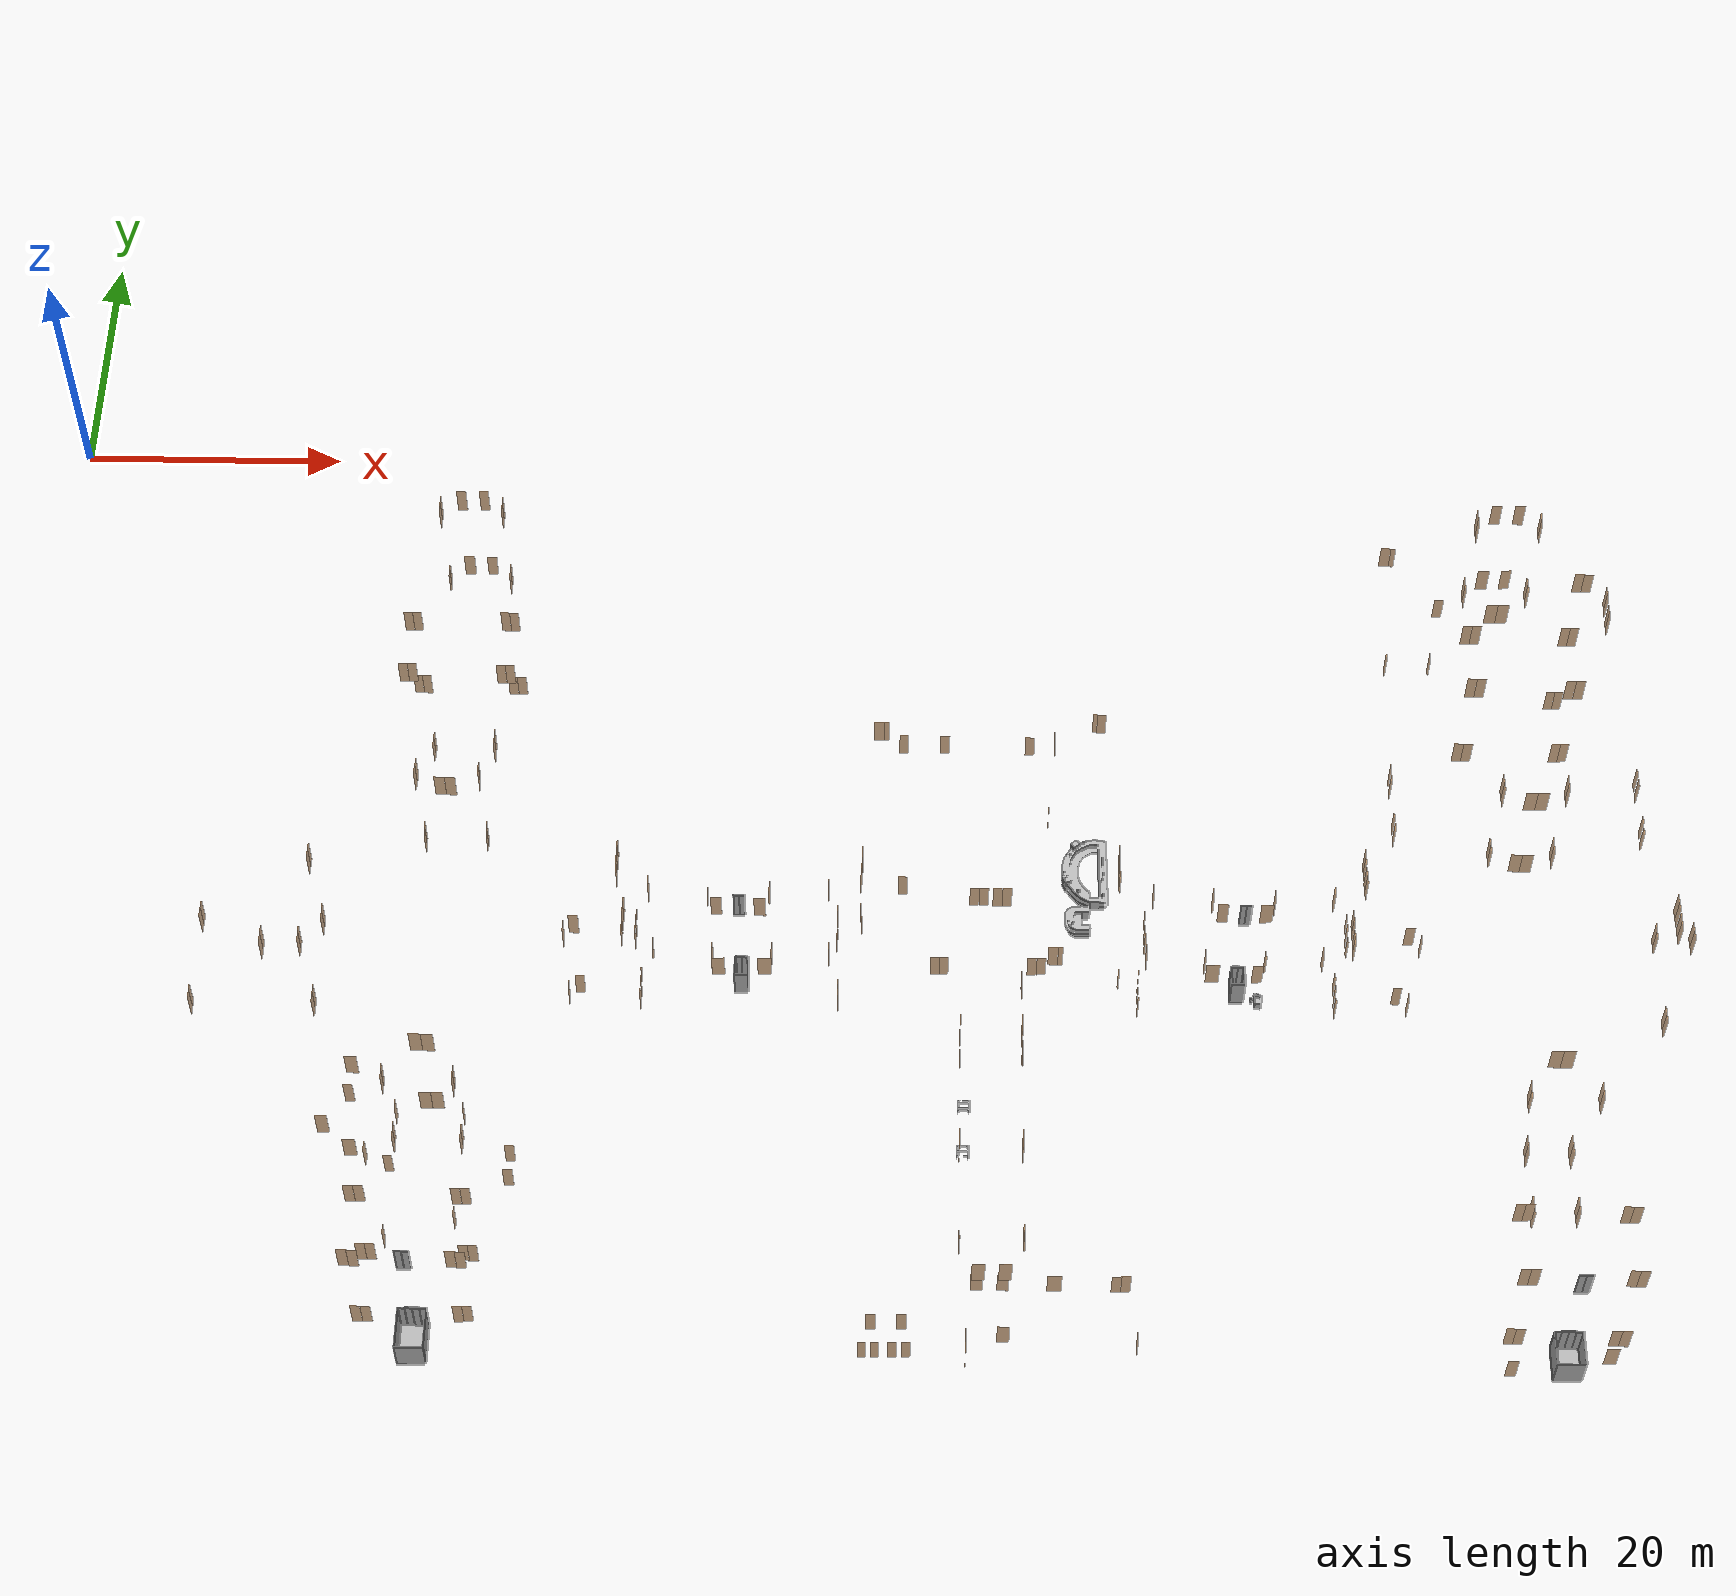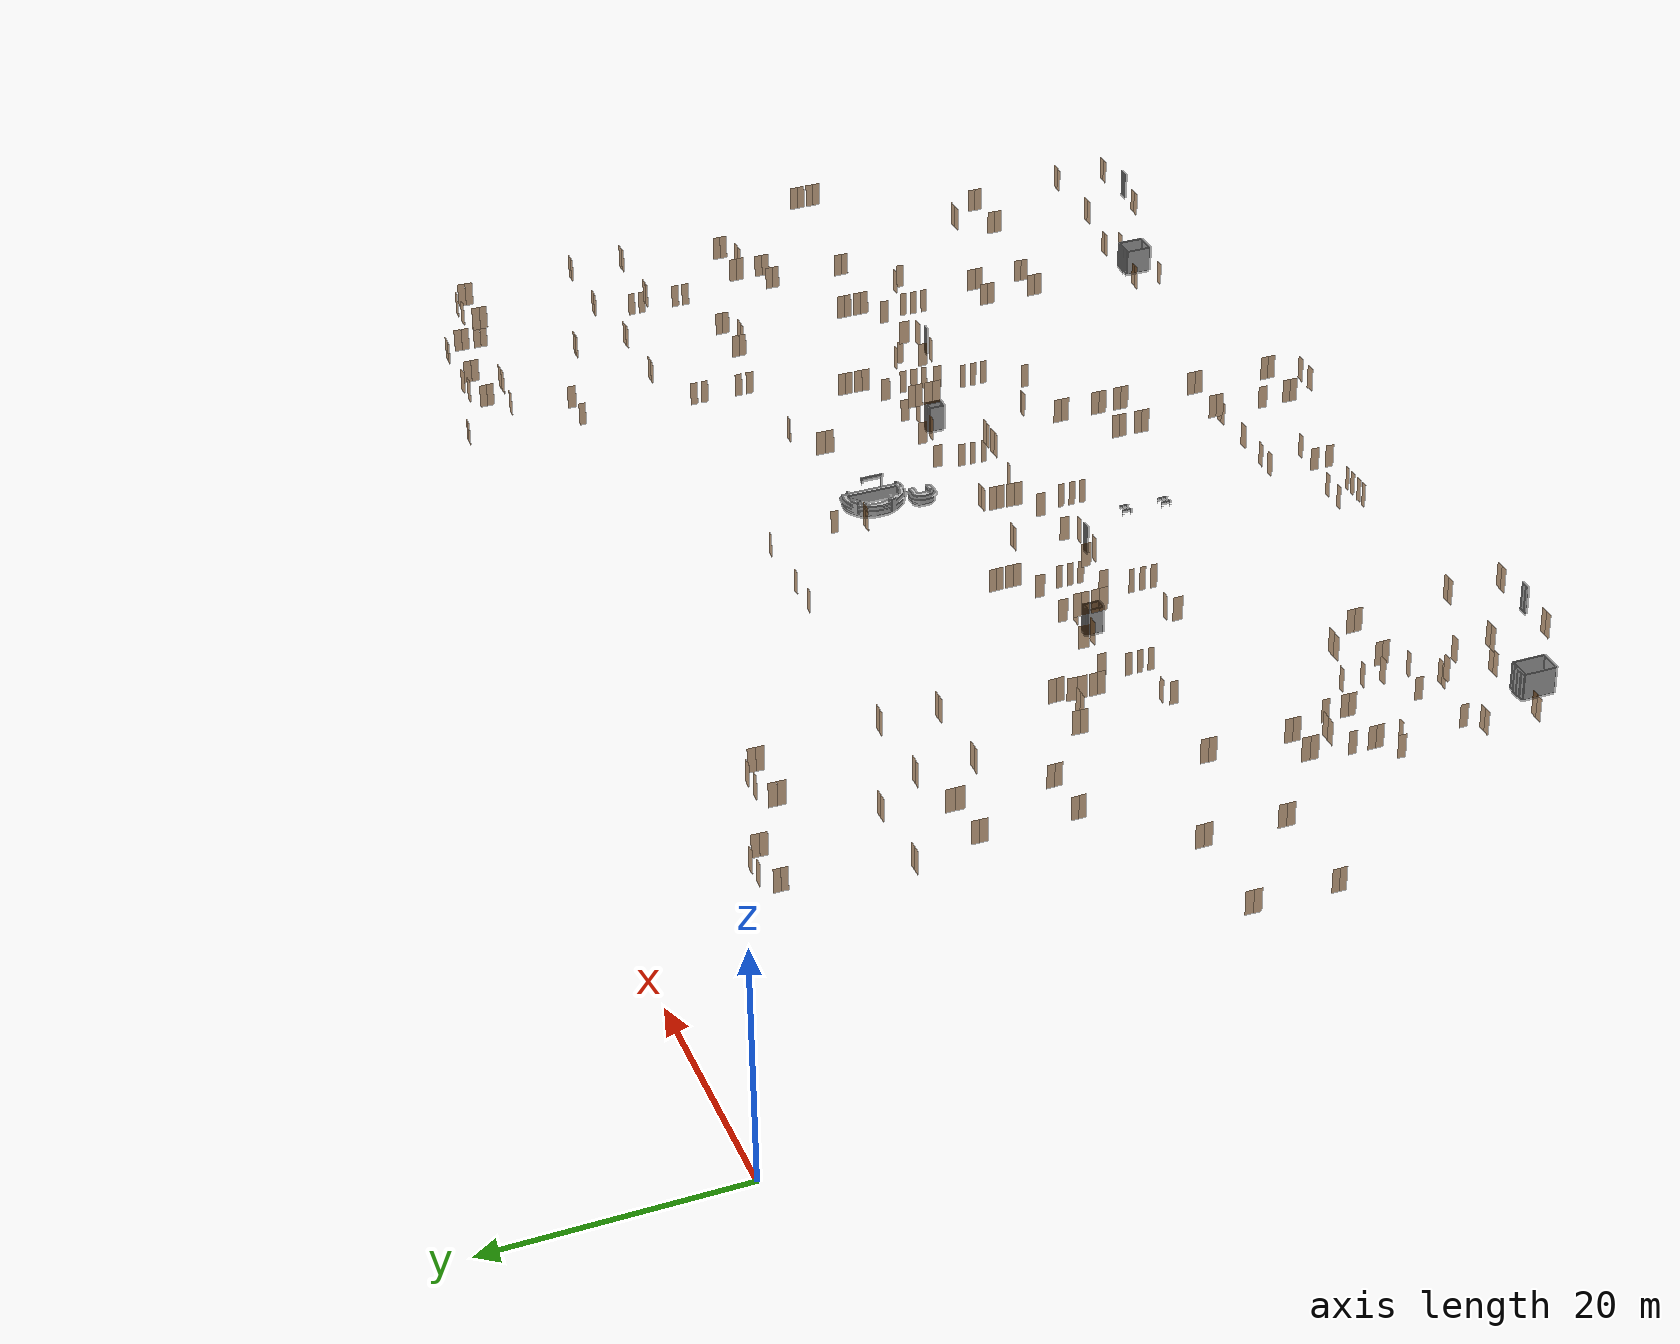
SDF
<sdf version="1.7">
 <world name="estce">
  <scene><ambient>0.8 0.8 0.8 1.0</ambient><background>0 0 0</background><grid>false</grid></scene>
  <include>
   <name>OpenRobotics/MiRCart</name>
   <uri>model://MiRCart</uri>
   <pose>69.80679362706269 -62.352217355699814 0.0 0 0 1.5708</pose>
   <static>True</static>
  </include>
  <include>
   <name>OpenRobotics/MiRCart_2</name>
   <uri>model://MiRCart</uri>
   <pose>69.86865174262017 -58.657115191611055 0.0 0 0 1.5708</pose>
   <static>True</static>
  </include>
  <include>
   <name>OpenRobotics/CleaningSection</name>
   <uri>model://CleaningSection</uri>
   <pose>91.0523404894248 -49.39112411035458 0.0 0 0 1.5708</pose>
   <static>True</static>
  </include>
  <include>
   <name>OpenRobotics/InformationCounter</name>
   <uri>model://InformationCounter</uri>
   <pose>78.62689453282388 -38.9416588937153 0.0 0 0 -3.1327</pose>
   <static>True</static>
  </include>
  <model name="TD1013AL2">
   <pose>28.615494677734596 -71.43441845900185 0.0 0 0 -3.1360970245967152</pose>
   <link name="right">
    <pose>0.3400059322993263 0 1.11 0 0 0</pose>
    <visual name="right_visual">
     <geometry><box><size>0.6700118645986526 0.03 2.2</size></box></geometry>
     <material><ambient>0.5 0.25 0 0.6</ambient><diffuse>0.5 0.25 0 0.6</diffuse></material>
    </visual>
    <collision name="right_collision">
     <geometry><box><size>0.6700118645986526 0.03 2.2</size></box></geometry>
     <surface><contact><collide_bitmask>0x02</collide_bitmask></contact></surface>
    </collision>
    <inertial>
     <mass>50.0</mass>
     <inertia><ixx>20.17041666666667</ixx><iyy>22.037149577929018</iyy><izz>1.8742329112623468</izz></inertia>
    </inertial>
   </link>
   <joint name="right_joint" type="revolute">
    <parent>world</parent>
    <child>right</child>
    <axis><xyz>0 0 -1</xyz><limit><lower>0</lower><upper>1.57</upper></limit></axis>
    <pose>0.3400059322993263 0 0 0 0 0</pose>
   </joint>
   <link name="left">
    <pose>-0.3400059322993263 0 1.11 0 0 0</pose>
    <visual name="left_visual">
     <geometry><box><size>0.6700118645986526 0.03 2.2</size></box></geometry>
     <material><ambient>0.5 0.25 0 0.6</ambient><diffuse>0.5 0.25 0 0.6</diffuse></material>
    </visual>
    <collision name="left_collision">
     <geometry><box><size>0.6700118645986526 0.03 2.2</size></box></geometry>
     <surface><contact><collide_bitmask>0x02</collide_bitmask></contact></surface>
    </collision>
    <inertial>
     <mass>50.0</mass>
     <inertia><ixx>20.17041666666667</ixx><iyy>22.037149577929018</iyy><izz>1.8742329112623468</izz></inertia>
    </inertial>
   </link>
   <joint name="left_joint" type="revolute">
    <parent>world</parent>
    <child>left</child>
    <axis><xyz>0 0 -1</xyz><limit><lower>-1.57</lower><upper>0</upper></limit></axis>
    <pose>-0.3400059322993263 0 0 0 0 0</pose>
   </joint>
   <plugin name="door" filename="libdoor.so">
    <v_max_door>0.5</v_max_door>
    <a_max_door>0.3</a_max_door>
    <a_nom_door>0.15</a_nom_door>
    <dx_min_door>0.01</dx_min_door>
    <f_max_door>500.0</f_max_door>
    <door name="TD1013AL2" type="DoubleSwingDoor" left_joint_name="left_joint" right_joint_name="right_joint"/>
   </plugin>
  </model>
  <model name="TD1012AL">
   <pose>28.74935599891922 -76.20730177365475 0.0 0 0 -0.019155480712126263</pose>
   <link name="right">
    <pose>0.3506591178894858 0 1.11 0 0 0</pose>
    <visual name="right_visual">
     <geometry><box><size>0.6913182357789716 0.03 2.2</size></box></geometry>
     <material><ambient>0.5 0.25 0 0.6</ambient><diffuse>0.5 0.25 0 0.6</diffuse></material>
    </visual>
    <collision name="right_collision">
     <geometry><box><size>0.6913182357789716 0.03 2.2</size></box></geometry>
     <surface><contact><collide_bitmask>0x02</collide_bitmask></contact></surface>
    </collision>
    <inertial>
     <mass>50.0</mass>
     <inertia><ixx>20.17041666666667</ixx><iyy>22.158003763002295</iyy><izz>1.995087096335624</izz></inertia>
    </inertial>
   </link>
   <joint name="right_joint" type="revolute">
    <parent>world</parent>
    <child>right</child>
    <axis><xyz>0 0 -1</xyz><limit><lower>0</lower><upper>1.57</upper></limit></axis>
    <pose>0.3506591178894858 0 0 0 0 0</pose>
   </joint>
   <link name="left">
    <pose>-0.3506591178894858 0 1.11 0 0 0</pose>
    <visual name="left_visual">
     <geometry><box><size>0.6913182357789716 0.03 2.2</size></box></geometry>
     <material><ambient>0.5 0.25 0 0.6</ambient><diffuse>0.5 0.25 0 0.6</diffuse></material>
    </visual>
    <collision name="left_collision">
     <geometry><box><size>0.6913182357789716 0.03 2.2</size></box></geometry>
     <surface><contact><collide_bitmask>0x02</collide_bitmask></contact></surface>
    </collision>
    <inertial>
     <mass>50.0</mass>
     <inertia><ixx>20.17041666666667</ixx><iyy>22.158003763002295</iyy><izz>1.995087096335624</izz></inertia>
    </inertial>
   </link>
   <joint name="left_joint" type="revolute">
    <parent>world</parent>
    <child>left</child>
    <axis><xyz>0 0 -1</xyz><limit><lower>-1.57</lower><upper>0</upper></limit></axis>
    <pose>-0.3506591178894858 0 0 0 0 0</pose>
   </joint>
   <plugin name="door" filename="libdoor.so">
    <v_max_door>0.5</v_max_door>
    <a_max_door>0.3</a_max_door>
    <a_nom_door>0.15</a_nom_door>
    <dx_min_door>0.01</dx_min_door>
    <f_max_door>500.0</f_max_door>
    <door name="TD1012AL" type="DoubleSwingDoor" left_joint_name="left_joint" right_joint_name="right_joint"/>
   </plugin>
  </model>
  <model name="TD1011AL">
   <pose>35.694736283854354 -76.12425568237657 0.0 0 0 0.03052550844454736</pose>
   <link name="right">
    <pose>0.333686512071335 0 1.11 0 0 0</pose>
    <visual name="right_visual">
     <geometry><box><size>0.65737302414267 0.03 2.2</size></box></geometry>
     <material><ambient>0.5 0.25 0 0.6</ambient><diffuse>0.5 0.25 0 0.6</diffuse></material>
    </visual>
    <collision name="right_collision">
     <geometry><box><size>0.65737302414267 0.03 2.2</size></box></geometry>
     <surface><contact><collide_bitmask>0x02</collide_bitmask></contact></surface>
    </collision>
    <inertial>
     <mass>50.0</mass>
     <inertia><ixx>20.17041666666667</ixx><iyy>21.967247053627002</iyy><izz>1.8043303869603309</izz></inertia>
    </inertial>
   </link>
   <joint name="right_joint" type="revolute">
    <parent>world</parent>
    <child>right</child>
    <axis><xyz>0 0 -1</xyz><limit><lower>0</lower><upper>1.57</upper></limit></axis>
    <pose>0.333686512071335 0 0 0 0 0</pose>
   </joint>
   <link name="left">
    <pose>-0.333686512071335 0 1.11 0 0 0</pose>
    <visual name="left_visual">
     <geometry><box><size>0.65737302414267 0.03 2.2</size></box></geometry>
     <material><ambient>0.5 0.25 0 0.6</ambient><diffuse>0.5 0.25 0 0.6</diffuse></material>
    </visual>
    <collision name="left_collision">
     <geometry><box><size>0.65737302414267 0.03 2.2</size></box></geometry>
     <surface><contact><collide_bitmask>0x02</collide_bitmask></contact></surface>
    </collision>
    <inertial>
     <mass>50.0</mass>
     <inertia><ixx>20.17041666666667</ixx><iyy>21.967247053627002</iyy><izz>1.8043303869603309</izz></inertia>
    </inertial>
   </link>
   <joint name="left_joint" type="revolute">
    <parent>world</parent>
    <child>left</child>
    <axis><xyz>0 0 -1</xyz><limit><lower>-1.57</lower><upper>0</upper></limit></axis>
    <pose>-0.333686512071335 0 0 0 0 0</pose>
   </joint>
   <plugin name="door" filename="libdoor.so">
    <v_max_door>0.5</v_max_door>
    <a_max_door>0.3</a_max_door>
    <a_nom_door>0.15</a_nom_door>
    <dx_min_door>0.01</dx_min_door>
    <f_max_door>500.0</f_max_door>
    <door name="TD1011AL" type="DoubleSwingDoor" left_joint_name="left_joint" right_joint_name="right_joint"/>
   </plugin>
  </model>
  <model name="TD1010AL2">
   <pose>35.71148017144721 -71.4268769761182 0.0 0 0 3.1356810753236894</pose>
   <link name="right">
    <pose>0.3312699130296567 0 1.11 0 0 0</pose>
    <visual name="right_visual">
     <geometry><box><size>0.6525398260593134 0.03 2.2</size></box></geometry>
     <material><ambient>0.5 0.25 0 0.6</ambient><diffuse>0.5 0.25 0 0.6</diffuse></material>
    </visual>
    <collision name="right_collision">
     <geometry><box><size>0.6525398260593134 0.03 2.2</size></box></geometry>
     <surface><contact><collide_bitmask>0x02</collide_bitmask></contact></surface>
    </collision>
    <inertial>
     <mass>50.0</mass>
     <inertia><ixx>20.17041666666667</ixx><iyy>21.940867602473</iyy><izz>1.7779509358063292</izz></inertia>
    </inertial>
   </link>
   <joint name="right_joint" type="revolute">
    <parent>world</parent>
    <child>right</child>
    <axis><xyz>0 0 -1</xyz><limit><lower>0</lower><upper>1.57</upper></limit></axis>
    <pose>0.3312699130296567 0 0 0 0 0</pose>
   </joint>
   <link name="left">
    <pose>-0.3312699130296567 0 1.11 0 0 0</pose>
    <visual name="left_visual">
     <geometry><box><size>0.6525398260593134 0.03 2.2</size></box></geometry>
     <material><ambient>0.5 0.25 0 0.6</ambient><diffuse>0.5 0.25 0 0.6</diffuse></material>
    </visual>
    <collision name="left_collision">
     <geometry><box><size>0.6525398260593134 0.03 2.2</size></box></geometry>
     <surface><contact><collide_bitmask>0x02</collide_bitmask></contact></surface>
    </collision>
    <inertial>
     <mass>50.0</mass>
     <inertia><ixx>20.17041666666667</ixx><iyy>21.940867602473</iyy><izz>1.7779509358063292</izz></inertia>
    </inertial>
   </link>
   <joint name="left_joint" type="revolute">
    <parent>world</parent>
    <child>left</child>
    <axis><xyz>0 0 -1</xyz><limit><lower>-1.57</lower><upper>0</upper></limit></axis>
    <pose>-0.3312699130296567 0 0 0 0 0</pose>
   </joint>
   <plugin name="door" filename="libdoor.so">
    <v_max_door>0.5</v_max_door>
    <a_max_door>0.3</a_max_door>
    <a_nom_door>0.15</a_nom_door>
    <dx_min_door>0.01</dx_min_door>
    <f_max_door>500.0</f_max_door>
    <door name="TD1010AL2" type="DoubleSwingDoor" left_joint_name="left_joint" right_joint_name="right_joint"/>
   </plugin>
  </model>
  <model name="TN4">
   <pose>34.54322367116888 -68.6983190900599 0.0 0 0 1.5597866738195798</pose>
   <link name="right">
    <pose>0 0 1.11 0 0 0</pose>
    <visual name="right_visual">
     <geometry><box><size>0.7035438381815191 0.03 2.2</size></box></geometry>
     <material><ambient>0.5 0.25 0 0.6</ambient><diffuse>0.5 0.25 0 0.6</diffuse></material>
    </visual>
    <collision name="right_collision">
     <geometry><box><size>0.7035438381815191 0.03 2.2</size></box></geometry>
     <surface><contact><collide_bitmask>0x02</collide_bitmask></contact></surface>
    </collision>
    <inertial>
     <mass>50.0</mass>
     <inertia><ixx>20.17041666666667</ixx><iyy>22.229058051013272</iyy><izz>2.066141384346598</izz></inertia>
    </inertial>
   </link>
   <joint name="right_joint" type="revolute">
    <parent>world</parent>
    <child>right</child>
    <axis><xyz>0 0 1</xyz><limit><lower>0</lower><upper>1.57</upper></limit></axis>
    <pose>0.35677191909075956 0 0 0 0 0</pose>
   </joint>
   <plugin name="door" filename="libdoor.so">
    <v_max_door>0.5</v_max_door>
    <a_max_door>0.3</a_max_door>
    <a_nom_door>0.15</a_nom_door>
    <dx_min_door>0.01</dx_min_door>
    <f_max_door>500.0</f_max_door>
    <door name="TN4" type="SwingDoor" left_joint_name="empty_joint" right_joint_name="right_joint"/>
   </plugin>
  </model>
  <model name="TN3">
   <pose>29.7646617994637 -70.20799602749449 0.0 0 0 1.5837881802092755</pose>
   <link name="right">
    <pose>0 0 1.11 0 0 0</pose>
    <visual name="right_visual">
     <geometry><box><size>0.7225283452947034 0.03 2.2</size></box></geometry>
     <material><ambient>0.5 0.25 0 0.6</ambient><diffuse>0.5 0.25 0 0.6</diffuse></material>
    </visual>
    <collision name="right_collision">
     <geometry><box><size>0.7225283452947034 0.03 2.2</size></box></geometry>
     <surface><contact><collide_bitmask>0x02</collide_bitmask></contact></surface>
    </collision>
    <inertial>
     <mass>50.0</mass>
     <inertia><ixx>20.17041666666667</ixx><iyy>22.341863373976267</iyy><izz>2.1789467073095925</izz></inertia>
    </inertial>
   </link>
   <joint name="right_joint" type="revolute">
    <parent>world</parent>
    <child>right</child>
    <axis><xyz>0 0 -1</xyz><limit><lower>0</lower><upper>1.57</upper></limit></axis>
    <pose>0.3662641726473517 0 0 0 0 0</pose>
   </joint>
   <plugin name="door" filename="libdoor.so">
    <v_max_door>0.5</v_max_door>
    <a_max_door>0.3</a_max_door>
    <a_nom_door>0.15</a_nom_door>
    <dx_min_door>0.01</dx_min_door>
    <f_max_door>500.0</f_max_door>
    <door name="TN3" type="SwingDoor" left_joint_name="empty_joint" right_joint_name="right_joint"/>
   </plugin>
  </model>
  <model name="TD1013AL1">
   <pose>29.58629226233187 -64.46540370538672 0.0 0 0 0.009366742804353713</pose>
   <link name="right">
    <pose>0 0 1.11 0 0 0</pose>
    <visual name="right_visual">
     <geometry><box><size>0.6226145179343526 0.03 2.2</size></box></geometry>
     <material><ambient>0.5 0.25 0 0.6</ambient><diffuse>0.5 0.25 0 0.6</diffuse></material>
    </visual>
    <collision name="right_collision">
     <geometry><box><size>0.6226145179343526 0.03 2.2</size></box></geometry>
     <surface><contact><collide_bitmask>0x02</collide_bitmask></contact></surface>
    </collision>
    <inertial>
     <mass>50.0</mass>
     <inertia><ixx>20.17041666666667</ixx><iyy>21.78187015809428</iyy><izz>1.6189534914276098</izz></inertia>
    </inertial>
   </link>
   <joint name="right_joint" type="revolute">
    <parent>world</parent>
    <child>right</child>
    <axis><xyz>0 0 1</xyz><limit><lower>0</lower><upper>1.57</upper></limit></axis>
    <pose>0.3163072589671763 0 0 0 0 0</pose>
   </joint>
   <plugin name="door" filename="libdoor.so">
    <v_max_door>0.5</v_max_door>
    <a_max_door>0.3</a_max_door>
    <a_nom_door>0.15</a_nom_door>
    <dx_min_door>0.01</dx_min_door>
    <f_max_door>500.0</f_max_door>
    <door name="TD1013AL1" type="SwingDoor" left_joint_name="empty_joint" right_joint_name="right_joint"/>
   </plugin>
  </model>
  <model name="TD1020CA">
   <pose>27.869303102710525 -63.66825100867423 0.0 0 0 -1.6530942220449312</pose>
   <link name="right">
    <pose>0 0 1.11 0 0 0</pose>
    <visual name="right_visual">
     <geometry><box><size>0.6884247753982287 0.03 2.2</size></box></geometry>
     <material><ambient>0.5 0.25 0 0.6</ambient><diffuse>0.5 0.25 0 0.6</diffuse></material>
    </visual>
    <collision name="right_collision">
     <geometry><box><size>0.6884247753982287 0.03 2.2</size></box></geometry>
     <surface><contact><collide_bitmask>0x02</collide_bitmask></contact></surface>
    </collision>
    <inertial>
     <mass>50.0</mass>
     <inertia><ixx>20.17041666666667</ixx><iyy>22.141369464092097</iyy><izz>1.9784527974254236</izz></inertia>
    </inertial>
   </link>
   <joint name="right_joint" type="revolute">
    <parent>world</parent>
    <child>right</child>
    <axis><xyz>0 0 1</xyz><limit><lower>0</lower><upper>1.57</upper></limit></axis>
    <pose>0.34921238769911433 0 0 0 0 0</pose>
   </joint>
   <plugin name="door" filename="libdoor.so">
    <v_max_door>0.5</v_max_door>
    <a_max_door>0.3</a_max_door>
    <a_nom_door>0.15</a_nom_door>
    <dx_min_door>0.01</dx_min_door>
    <f_max_door>500.0</f_max_door>
    <door name="TD1020CA" type="SwingDoor" left_joint_name="empty_joint" right_joint_name="right_joint"/>
   </plugin>
  </model>
  <model name="TD1009CA">
   <pose>38.051561909439855 -63.52871113043735 0.0 0 0 3.141592653589793</pose>
   <link name="right">
    <pose>0 0 1.11 0 0 0</pose>
    <visual name="right_visual">
     <geometry><box><size>0.6713819564927783 0.03 2.2</size></box></geometry>
     <material><ambient>0.5 0.25 0 0.6</ambient><diffuse>0.5 0.25 0 0.6</diffuse></material>
    </visual>
    <collision name="right_collision">
     <geometry><box><size>0.6713819564927783 0.03 2.2</size></box></geometry>
     <surface><contact><collide_bitmask>0x02</collide_bitmask></contact></surface>
    </collision>
    <inertial>
     <mass>50.0</mass>
     <inertia><ixx>20.17041666666667</ixx><iyy>22.0448072146003</iyy><izz>1.881890547933629</izz></inertia>
    </inertial>
   </link>
   <joint name="right_joint" type="revolute">
    <parent>world</parent>
    <child>right</child>
    <axis><xyz>0 0 -1</xyz><limit><lower>0</lower><upper>1.57</upper></limit></axis>
    <pose>0.34069097824638916 0 0 0 0 0</pose>
   </joint>
   <plugin name="door" filename="libdoor.so">
    <v_max_door>0.5</v_max_door>
    <a_max_door>0.3</a_max_door>
    <a_nom_door>0.15</a_nom_door>
    <dx_min_door>0.01</dx_min_door>
    <f_max_door>500.0</f_max_door>
    <door name="TD1009CA" type="SwingDoor" left_joint_name="empty_joint" right_joint_name="right_joint"/>
   </plugin>
  </model>
  <model name="TD1010AL1">
   <pose>38.04824006578872 -65.41280249264413 0.0 0 0 3.1203192675657387</pose>
   <link name="right">
    <pose>0 0 1.11 0 0 0</pose>
    <visual name="right_visual">
     <geometry><box><size>0.6990598299895224 0.03 2.2</size></box></geometry>
     <material><ambient>0.5 0.25 0 0.6</ambient><diffuse>0.5 0.25 0 0.6</diffuse></material>
    </visual>
    <collision name="right_collision">
     <geometry><box><size>0.6990598299895224 0.03 2.2</size></box></geometry>
     <surface><contact><collide_bitmask>0x02</collide_bitmask></contact></surface>
    </collision>
    <inertial>
     <mass>50.0</mass>
     <inertia><ixx>20.17041666666667</ixx><iyy>22.202852691270756</iyy><izz>2.0399360246040836</izz></inertia>
    </inertial>
   </link>
   <joint name="right_joint" type="revolute">
    <parent>world</parent>
    <child>right</child>
    <axis><xyz>0 0 1</xyz><limit><lower>0</lower><upper>1.57</upper></limit></axis>
    <pose>0.3545299149947612 0 0 0 0 0</pose>
   </joint>
   <plugin name="door" filename="libdoor.so">
    <v_max_door>0.5</v_max_door>
    <a_max_door>0.3</a_max_door>
    <a_nom_door>0.15</a_nom_door>
    <dx_min_door>0.01</dx_min_door>
    <f_max_door>500.0</f_max_door>
    <door name="TD1010AL1" type="SwingDoor" left_joint_name="empty_joint" right_joint_name="right_joint"/>
   </plugin>
  </model>
  <model name="TD1008AL">
   <pose>34.56893429213082 -62.36942136352812 0.0 0 0 1.5568159788755287</pose>
   <link name="right">
    <pose>0.338361719504987 0 1.11 0 0 0</pose>
    <visual name="right_visual">
     <geometry><box><size>0.666723439009974 0.03 2.2</size></box></geometry>
     <material><ambient>0.5 0.25 0 0.6</ambient><diffuse>0.5 0.25 0 0.6</diffuse></material>
    </visual>
    <collision name="right_collision">
     <geometry><box><size>0.666723439009974 0.03 2.2</size></box></geometry>
     <surface><contact><collide_bitmask>0x02</collide_bitmask></contact></surface>
    </collision>
    <inertial>
     <mass>50.0</mass>
     <inertia><ixx>20.17041666666667</ixx><iyy>22.018833933855365</iyy><izz>1.8559172671886939</izz></inertia>
    </inertial>
   </link>
   <joint name="right_joint" type="revolute">
    <parent>world</parent>
    <child>right</child>
    <axis><xyz>0 0 -1</xyz><limit><lower>0</lower><upper>1.57</upper></limit></axis>
    <pose>0.338361719504987 0 0 0 0 0</pose>
   </joint>
   <link name="left">
    <pose>-0.338361719504987 0 1.11 0 0 0</pose>
    <visual name="left_visual">
     <geometry><box><size>0.666723439009974 0.03 2.2</size></box></geometry>
     <material><ambient>0.5 0.25 0 0.6</ambient><diffuse>0.5 0.25 0 0.6</diffuse></material>
    </visual>
    <collision name="left_collision">
     <geometry><box><size>0.666723439009974 0.03 2.2</size></box></geometry>
     <surface><contact><collide_bitmask>0x02</collide_bitmask></contact></surface>
    </collision>
    <inertial>
     <mass>50.0</mass>
     <inertia><ixx>20.17041666666667</ixx><iyy>22.018833933855365</iyy><izz>1.8559172671886939</izz></inertia>
    </inertial>
   </link>
   <joint name="left_joint" type="revolute">
    <parent>world</parent>
    <child>left</child>
    <axis><xyz>0 0 -1</xyz><limit><lower>-1.57</lower><upper>0</upper></limit></axis>
    <pose>-0.338361719504987 0 0 0 0 0</pose>
   </joint>
   <plugin name="door" filename="libdoor.so">
    <v_max_door>0.5</v_max_door>
    <a_max_door>0.3</a_max_door>
    <a_nom_door>0.15</a_nom_door>
    <dx_min_door>0.01</dx_min_door>
    <f_max_door>500.0</f_max_door>
    <door name="TD1008AL" type="DoubleSwingDoor" left_joint_name="left_joint" right_joint_name="right_joint"/>
   </plugin>
  </model>
  <model name="TD1014AL">
   <pose>29.774829334422893 -62.3640345900398 0.0 0 0 -1.5524594989999174</pose>
   <link name="right">
    <pose>0.34886906712951293 0 1.11 0 0 0</pose>
    <visual name="right_visual">
     <geometry><box><size>0.6877381342590259 0.03 2.2</size></box></geometry>
     <material><ambient>0.5 0.25 0 0.6</ambient><diffuse>0.5 0.25 0 0.6</diffuse></material>
    </visual>
    <collision name="right_collision">
     <geometry><box><size>0.6877381342590259 0.03 2.2</size></box></geometry>
     <surface><contact><collide_bitmask>0x02</collide_bitmask></contact></surface>
    </collision>
    <inertial>
     <mass>50.0</mass>
     <inertia><ixx>20.17041666666667</ixx><iyy>22.137432255475364</iyy><izz>1.9745155888086914</izz></inertia>
    </inertial>
   </link>
   <joint name="right_joint" type="revolute">
    <parent>world</parent>
    <child>right</child>
    <axis><xyz>0 0 -1</xyz><limit><lower>0</lower><upper>1.57</upper></limit></axis>
    <pose>0.34886906712951293 0 0 0 0 0</pose>
   </joint>
   <link name="left">
    <pose>-0.34886906712951293 0 1.11 0 0 0</pose>
    <visual name="left_visual">
     <geometry><box><size>0.6877381342590259 0.03 2.2</size></box></geometry>
     <material><ambient>0.5 0.25 0 0.6</ambient><diffuse>0.5 0.25 0 0.6</diffuse></material>
    </visual>
    <collision name="left_collision">
     <geometry><box><size>0.6877381342590259 0.03 2.2</size></box></geometry>
     <surface><contact><collide_bitmask>0x02</collide_bitmask></contact></surface>
    </collision>
    <inertial>
     <mass>50.0</mass>
     <inertia><ixx>20.17041666666667</ixx><iyy>22.137432255475364</iyy><izz>1.9745155888086914</izz></inertia>
    </inertial>
   </link>
   <joint name="left_joint" type="revolute">
    <parent>world</parent>
    <child>left</child>
    <axis><xyz>0 0 -1</xyz><limit><lower>-1.57</lower><upper>0</upper></limit></axis>
    <pose>-0.34886906712951293 0 0 0 0 0</pose>
   </joint>
   <plugin name="door" filename="libdoor.so">
    <v_max_door>0.5</v_max_door>
    <a_max_door>0.3</a_max_door>
    <a_nom_door>0.15</a_nom_door>
    <dx_min_door>0.01</dx_min_door>
    <f_max_door>500.0</f_max_door>
    <door name="TD1014AL" type="DoubleSwingDoor" left_joint_name="left_joint" right_joint_name="right_joint"/>
   </plugin>
  </model>
  <model name="TN1">
   <pose>29.762035747388147 -60.30318972274769 0.0 0 0 -1.5707963267948966</pose>
   <link name="right">
    <pose>0 0 1.11 0 0 0</pose>
    <visual name="right_visual">
     <geometry><box><size>0.7196160241027394 0.03 2.2</size></box></geometry>
     <material><ambient>0.5 0.25 0 0.6</ambient><diffuse>0.5 0.25 0 0.6</diffuse></material>
    </visual>
    <collision name="right_collision">
     <geometry><box><size>0.7196160241027394 0.03 2.2</size></box></geometry>
     <surface><contact><collide_bitmask>0x02</collide_bitmask></contact></surface>
    </collision>
    <inertial>
     <mass>50.0</mass>
     <inertia><ixx>20.17041666666667</ixx><iyy>22.32436342560598</iyy><izz>2.1614467589393103</izz></inertia>
    </inertial>
   </link>
   <joint name="right_joint" type="revolute">
    <parent>world</parent>
    <child>right</child>
    <axis><xyz>0 0 1</xyz><limit><lower>0</lower><upper>1.57</upper></limit></axis>
    <pose>0.3648080120513697 0 0 0 0 0</pose>
   </joint>
   <plugin name="door" filename="libdoor.so">
    <v_max_door>0.5</v_max_door>
    <a_max_door>0.3</a_max_door>
    <a_nom_door>0.15</a_nom_door>
    <dx_min_door>0.01</dx_min_door>
    <f_max_door>500.0</f_max_door>
    <door name="TN1" type="SwingDoor" left_joint_name="empty_joint" right_joint_name="right_joint"/>
   </plugin>
  </model>
  <model name="TD1002CP">
   <pose>32.20689022972852 -59.33034965320277 0.0 0 0 -0.007458642109472351</pose>
   <link name="right">
    <pose>0.4288215424630806 0 1.11 0 0 0</pose>
    <visual name="right_visual">
     <geometry><box><size>0.8476430849261611 0.03 2.2</size></box></geometry>
     <material><ambient>0.5 0.25 0 0.6</ambient><diffuse>0.5 0.25 0 0.6</diffuse></material>
    </visual>
    <collision name="right_collision">
     <geometry><box><size>0.8476430849261611 0.03 2.2</size></box></geometry>
     <surface><contact><collide_bitmask>0x02</collide_bitmask></contact></surface>
    </collision>
    <inertial>
     <mass>50.0</mass>
     <inertia><ixx>20.17041666666667</ixx><iyy>23.160411664263087</iyy><izz>2.9974949975964136</izz></inertia>
    </inertial>
   </link>
   <joint name="right_joint" type="revolute">
    <parent>world</parent>
    <child>right</child>
    <axis><xyz>0 0 -1</xyz><limit><lower>0</lower><upper>1.57</upper></limit></axis>
    <pose>0.4288215424630806 0 0 0 0 0</pose>
   </joint>
   <link name="left">
    <pose>-0.4288215424630806 0 1.11 0 0 0</pose>
    <visual name="left_visual">
     <geometry><box><size>0.8476430849261611 0.03 2.2</size></box></geometry>
     <material><ambient>0.5 0.25 0 0.6</ambient><diffuse>0.5 0.25 0 0.6</diffuse></material>
    </visual>
    <collision name="left_collision">
     <geometry><box><size>0.8476430849261611 0.03 2.2</size></box></geometry>
     <surface><contact><collide_bitmask>0x02</collide_bitmask></contact></surface>
    </collision>
    <inertial>
     <mass>50.0</mass>
     <inertia><ixx>20.17041666666667</ixx><iyy>23.160411664263087</iyy><izz>2.9974949975964136</izz></inertia>
    </inertial>
   </link>
   <joint name="left_joint" type="revolute">
    <parent>world</parent>
    <child>left</child>
    <axis><xyz>0 0 -1</xyz><limit><lower>-1.57</lower><upper>0</upper></limit></axis>
    <pose>-0.4288215424630806 0 0 0 0 0</pose>
   </joint>
   <plugin name="door" filename="libdoor.so">
    <v_max_door>0.5</v_max_door>
    <a_max_door>0.3</a_max_door>
    <a_nom_door>0.15</a_nom_door>
    <dx_min_door>0.01</dx_min_door>
    <f_max_door>500.0</f_max_door>
    <door name="TD1002CP" type="DoubleSwingDoor" left_joint_name="left_joint" right_joint_name="right_joint"/>
   </plugin>
  </model>
  <model name="TN2">
   <pose>34.550013250253116 -60.30635445217207 0.0 0 0 -1.4909927351613321</pose>
   <link name="right">
    <pose>0 0 1.11 0 0 0</pose>
    <visual name="right_visual">
     <geometry><box><size>0.7020408952186347 0.03 2.2</size></box></geometry>
     <material><ambient>0.5 0.25 0 0.6</ambient><diffuse>0.5 0.25 0 0.6</diffuse></material>
    </visual>
    <collision name="right_collision">
     <geometry><box><size>0.7020408952186347 0.03 2.2</size></box></geometry>
     <surface><contact><collide_bitmask>0x02</collide_bitmask></contact></surface>
    </collision>
    <inertial>
     <mass>50.0</mass>
     <inertia><ixx>20.17041666666667</ixx><iyy>22.220255910664097</iyy><izz>2.057339243997425</izz></inertia>
    </inertial>
   </link>
   <joint name="right_joint" type="revolute">
    <parent>world</parent>
    <child>right</child>
    <axis><xyz>0 0 -1</xyz><limit><lower>0</lower><upper>1.57</upper></limit></axis>
    <pose>0.35602044760931734 0 0 0 0 0</pose>
   </joint>
   <plugin name="door" filename="libdoor.so">
    <v_max_door>0.5</v_max_door>
    <a_max_door>0.3</a_max_door>
    <a_nom_door>0.15</a_nom_door>
    <dx_min_door>0.01</dx_min_door>
    <f_max_door>500.0</f_max_door>
    <door name="TN2" type="SwingDoor" left_joint_name="empty_joint" right_joint_name="right_joint"/>
   </plugin>
  </model>
  <model name="TD1005CP1">
   <pose>23.027873095418798 -51.20491807853885 0.0 0 0 1.5707963267948966</pose>
   <link name="right">
    <pose>0.36435911426067413 0 1.11 0 0 0</pose>
    <visual name="right_visual">
     <geometry><box><size>0.7187182285213483 0.03 2.2</size></box></geometry>
     <material><ambient>0.5 0.25 0 0.6</ambient><diffuse>0.5 0.25 0 0.6</diffuse></material>
    </visual>
    <collision name="right_collision">
     <geometry><box><size>0.7187182285213483 0.03 2.2</size></box></geometry>
     <surface><contact><collide_bitmask>0x02</collide_bitmask></contact></surface>
    </collision>
    <inertial>
     <mass>50.0</mass>
     <inertia><ixx>20.17041666666667</ixx><iyy>22.31898288337028</iyy><izz>2.1560662167036044</izz></inertia>
    </inertial>
   </link>
   <joint name="right_joint" type="revolute">
    <parent>world</parent>
    <child>right</child>
    <axis><xyz>0 0 -1</xyz><limit><lower>0</lower><upper>1.57</upper></limit></axis>
    <pose>0.36435911426067413 0 0 0 0 0</pose>
   </joint>
   <link name="left">
    <pose>-0.36435911426067413 0 1.11 0 0 0</pose>
    <visual name="left_visual">
     <geometry><box><size>0.7187182285213483 0.03 2.2</size></box></geometry>
     <material><ambient>0.5 0.25 0 0.6</ambient><diffuse>0.5 0.25 0 0.6</diffuse></material>
    </visual>
    <collision name="left_collision">
     <geometry><box><size>0.7187182285213483 0.03 2.2</size></box></geometry>
     <surface><contact><collide_bitmask>0x02</collide_bitmask></contact></surface>
    </collision>
    <inertial>
     <mass>50.0</mass>
     <inertia><ixx>20.17041666666667</ixx><iyy>22.31898288337028</iyy><izz>2.1560662167036044</izz></inertia>
    </inertial>
   </link>
   <joint name="left_joint" type="revolute">
    <parent>world</parent>
    <child>left</child>
    <axis><xyz>0 0 -1</xyz><limit><lower>-1.57</lower><upper>0</upper></limit></axis>
    <pose>-0.36435911426067413 0 0 0 0 0</pose>
   </joint>
   <plugin name="door" filename="libdoor.so">
    <v_max_door>0.5</v_max_door>
    <a_max_door>0.3</a_max_door>
    <a_nom_door>0.15</a_nom_door>
    <dx_min_door>0.01</dx_min_door>
    <f_max_door>500.0</f_max_door>
    <door name="TD1005CP1" type="DoubleSwingDoor" left_joint_name="left_joint" right_joint_name="right_joint"/>
   </plugin>
  </model>
  <model name="TD1004CA">
   <pose>41.418329006971035 -50.19107119581413 0.0 0 0 1.5993775933365804</pose>
   <link name="right">
    <pose>0 0 1.11 0 0 0</pose>
    <visual name="right_visual">
     <geometry><box><size>0.7180729002156033 0.03 2.2</size></box></geometry>
     <material><ambient>0.5 0.25 0 0.6</ambient><diffuse>0.5 0.25 0 0.6</diffuse></material>
    </visual>
    <collision name="right_collision">
     <geometry><box><size>0.7180729002156033 0.03 2.2</size></box></geometry>
     <surface><contact><collide_bitmask>0x02</collide_bitmask></contact></surface>
    </collision>
    <inertial>
     <mass>50.0</mass>
     <inertia><ixx>20.17041666666667</ixx><iyy>22.315119541766872</iyy><izz>2.1522028751001994</izz></inertia>
    </inertial>
   </link>
   <joint name="right_joint" type="revolute">
    <parent>world</parent>
    <child>right</child>
    <axis><xyz>0 0 1</xyz><limit><lower>0</lower><upper>1.57</upper></limit></axis>
    <pose>0.36403645010780167 0 0 0 0 0</pose>
   </joint>
   <plugin name="door" filename="libdoor.so">
    <v_max_door>0.5</v_max_door>
    <a_max_door>0.3</a_max_door>
    <a_nom_door>0.15</a_nom_door>
    <dx_min_door>0.01</dx_min_door>
    <f_max_door>500.0</f_max_door>
    <door name="TD1004CA" type="SwingDoor" left_joint_name="empty_joint" right_joint_name="right_joint"/>
   </plugin>
  </model>
  <model name="TD1003CI">
   <pose>42.161714970803274 -49.42168282745601 0.0 0 0 -3.1108152612975006</pose>
   <link name="right">
    <pose>0 0 1.11 0 0 0</pose>
    <visual name="right_visual">
     <geometry><box><size>0.6661358327263901 0.03 2.2</size></box></geometry>
     <material><ambient>0.5 0.25 0 0.6</ambient><diffuse>0.5 0.25 0 0.6</diffuse></material>
    </visual>
    <collision name="right_collision">
     <geometry><box><size>0.6661358327263901 0.03 2.2</size></box></geometry>
     <surface><contact><collide_bitmask>0x02</collide_bitmask></contact></surface>
    </collision>
    <inertial>
     <mass>50.0</mass>
     <inertia><ixx>20.17041666666667</ixx><iyy>22.015570615175342</iyy><izz>1.8526539485086717</izz></inertia>
    </inertial>
   </link>
   <joint name="right_joint" type="revolute">
    <parent>world</parent>
    <child>right</child>
    <axis><xyz>0 0 1</xyz><limit><lower>0</lower><upper>1.57</upper></limit></axis>
    <pose>0.33806791636319505 0 0 0 0 0</pose>
   </joint>
   <plugin name="door" filename="libdoor.so">
    <v_max_door>0.5</v_max_door>
    <a_max_door>0.3</a_max_door>
    <a_nom_door>0.15</a_nom_door>
    <dx_min_door>0.01</dx_min_door>
    <f_max_door>500.0</f_max_door>
    <door name="TD1003CI" type="SwingDoor" left_joint_name="empty_joint" right_joint_name="right_joint"/>
   </plugin>
  </model>
  <model name="TD1023CP1">
   <pose>14.136285216489753 -51.20540064366385 0.0 0 0 1.579823871915645</pose>
   <link name="right">
    <pose>0.3095444736708306 0 1.11 0 0 0</pose>
    <visual name="right_visual">
     <geometry><box><size>0.6090889473416612 0.03 2.2</size></box></geometry>
     <material><ambient>0.5 0.25 0 0.6</ambient><diffuse>0.5 0.25 0 0.6</diffuse></material>
    </visual>
    <collision name="right_collision">
     <geometry><box><size>0.6090889473416612 0.03 2.2</size></box></geometry>
     <surface><contact><collide_bitmask>0x02</collide_bitmask></contact></surface>
    </collision>
    <inertial>
     <mass>50.0</mass>
     <inertia><ixx>20.17041666666667</ixx><iyy>21.712455607390726</iyy><izz>1.5495389407240538</izz></inertia>
    </inertial>
   </link>
   <joint name="right_joint" type="revolute">
    <parent>world</parent>
    <child>right</child>
    <axis><xyz>0 0 -1</xyz><limit><lower>0</lower><upper>1.57</upper></limit></axis>
    <pose>0.3095444736708306 0 0 0 0 0</pose>
   </joint>
   <link name="left">
    <pose>-0.3095444736708306 0 1.11 0 0 0</pose>
    <visual name="left_visual">
     <geometry><box><size>0.6090889473416612 0.03 2.2</size></box></geometry>
     <material><ambient>0.5 0.25 0 0.6</ambient><diffuse>0.5 0.25 0 0.6</diffuse></material>
    </visual>
    <collision name="left_collision">
     <geometry><box><size>0.6090889473416612 0.03 2.2</size></box></geometry>
     <surface><contact><collide_bitmask>0x02</collide_bitmask></contact></surface>
    </collision>
    <inertial>
     <mass>50.0</mass>
     <inertia><ixx>20.17041666666667</ixx><iyy>21.712455607390726</iyy><izz>1.5495389407240538</izz></inertia>
    </inertial>
   </link>
   <joint name="left_joint" type="revolute">
    <parent>world</parent>
    <child>left</child>
    <axis><xyz>0 0 -1</xyz><limit><lower>-1.57</lower><upper>0</upper></limit></axis>
    <pose>-0.3095444736708306 0 0 0 0 0</pose>
   </joint>
   <plugin name="door" filename="libdoor.so">
    <v_max_door>0.5</v_max_door>
    <a_max_door>0.3</a_max_door>
    <a_nom_door>0.15</a_nom_door>
    <dx_min_door>0.01</dx_min_door>
    <f_max_door>500.0</f_max_door>
    <door name="TD1023CP1" type="DoubleSwingDoor" left_joint_name="left_joint" right_joint_name="right_joint"/>
   </plugin>
  </model>
  <model name="TD1023CP2">
   <pose>14.151884414716331 -44.090000320503776 0.0 0 0 1.5401873563583324</pose>
   <link name="right">
    <pose>0.3461613428119867 0 1.11 0 0 0</pose>
    <visual name="right_visual">
     <geometry><box><size>0.6823226856239734 0.03 2.2</size></box></geometry>
     <material><ambient>0.5 0.25 0 0.6</ambient><diffuse>0.5 0.25 0 0.6</diffuse></material>
    </visual>
    <collision name="right_collision">
     <geometry><box><size>0.6823226856239734 0.03 2.2</size></box></geometry>
     <surface><contact><collide_bitmask>0x02</collide_bitmask></contact></surface>
    </collision>
    <inertial>
     <mass>50.0</mass>
     <inertia><ixx>20.17041666666667</ixx><iyy>22.106517697154636</iyy><izz>1.9436010304879652</izz></inertia>
    </inertial>
   </link>
   <joint name="right_joint" type="revolute">
    <parent>world</parent>
    <child>right</child>
    <axis><xyz>0 0 -1</xyz><limit><lower>0</lower><upper>1.57</upper></limit></axis>
    <pose>0.3461613428119867 0 0 0 0 0</pose>
   </joint>
   <link name="left">
    <pose>-0.3461613428119867 0 1.11 0 0 0</pose>
    <visual name="left_visual">
     <geometry><box><size>0.6823226856239734 0.03 2.2</size></box></geometry>
     <material><ambient>0.5 0.25 0 0.6</ambient><diffuse>0.5 0.25 0 0.6</diffuse></material>
    </visual>
    <collision name="left_collision">
     <geometry><box><size>0.6823226856239734 0.03 2.2</size></box></geometry>
     <surface><contact><collide_bitmask>0x02</collide_bitmask></contact></surface>
    </collision>
    <inertial>
     <mass>50.0</mass>
     <inertia><ixx>20.17041666666667</ixx><iyy>22.106517697154636</iyy><izz>1.9436010304879652</izz></inertia>
    </inertial>
   </link>
   <joint name="left_joint" type="revolute">
    <parent>world</parent>
    <child>left</child>
    <axis><xyz>0 0 -1</xyz><limit><lower>-1.57</lower><upper>0</upper></limit></axis>
    <pose>-0.3461613428119867 0 0 0 0 0</pose>
   </joint>
   <plugin name="door" filename="libdoor.so">
    <v_max_door>0.5</v_max_door>
    <a_max_door>0.3</a_max_door>
    <a_nom_door>0.15</a_nom_door>
    <dx_min_door>0.01</dx_min_door>
    <f_max_door>500.0</f_max_door>
    <door name="TD1023CP2" type="DoubleSwingDoor" left_joint_name="left_joint" right_joint_name="right_joint"/>
   </plugin>
  </model>
  <model name="TD1018AA">
   <pose>29.951908290406482 -36.82259198297031 0.0 0 0 -1.5430325593746388</pose>
   <link name="right">
    <pose>0.31754923010777264 0 1.11 0 0 0</pose>
    <visual name="right_visual">
     <geometry><box><size>0.6250984602155453 0.03 2.2</size></box></geometry>
     <material><ambient>0.5 0.25 0 0.6</ambient><diffuse>0.5 0.25 0 0.6</diffuse></material>
    </visual>
    <collision name="right_collision">
     <geometry><box><size>0.6250984602155453 0.03 2.2</size></box></geometry>
     <surface><contact><collide_bitmask>0x02</collide_bitmask></contact></surface>
    </collision>
    <inertial>
     <mass>50.0</mass>
     <inertia><ixx>20.17041666666667</ixx><iyy>21.79478368734936</iyy><izz>1.6318670206826902</izz></inertia>
    </inertial>
   </link>
   <joint name="right_joint" type="revolute">
    <parent>world</parent>
    <child>right</child>
    <axis><xyz>0 0 -1</xyz><limit><lower>0</lower><upper>1.57</upper></limit></axis>
    <pose>0.31754923010777264 0 0 0 0 0</pose>
   </joint>
   <link name="left">
    <pose>-0.31754923010777264 0 1.11 0 0 0</pose>
    <visual name="left_visual">
     <geometry><box><size>0.6250984602155453 0.03 2.2</size></box></geometry>
     <material><ambient>0.5 0.25 0 0.6</ambient><diffuse>0.5 0.25 0 0.6</diffuse></material>
    </visual>
    <collision name="left_collision">
     <geometry><box><size>0.6250984602155453 0.03 2.2</size></box></geometry>
     <surface><contact><collide_bitmask>0x02</collide_bitmask></contact></surface>
    </collision>
    <inertial>
     <mass>50.0</mass>
     <inertia><ixx>20.17041666666667</ixx><iyy>21.79478368734936</iyy><izz>1.6318670206826902</izz></inertia>
    </inertial>
   </link>
   <joint name="left_joint" type="revolute">
    <parent>world</parent>
    <child>left</child>
    <axis><xyz>0 0 -1</xyz><limit><lower>-1.57</lower><upper>0</upper></limit></axis>
    <pose>-0.31754923010777264 0 0 0 0 0</pose>
   </joint>
   <plugin name="door" filename="libdoor.so">
    <v_max_door>0.5</v_max_door>
    <a_max_door>0.3</a_max_door>
    <a_nom_door>0.15</a_nom_door>
    <dx_min_door>0.01</dx_min_door>
    <f_max_door>500.0</f_max_door>
    <door name="TD1018AA" type="DoubleSwingDoor" left_joint_name="left_joint" right_joint_name="right_joint"/>
   </plugin>
  </model>
  <model name="TD1015AA">
   <pose>34.52737757915742 -36.775884167848716 0.0 0 0 1.6088766030403268</pose>
   <link name="right">
    <pose>0.3404664622116848 0 1.11 0 0 0</pose>
    <visual name="right_visual">
     <geometry><box><size>0.6709329244233696 0.03 2.2</size></box></geometry>
     <material><ambient>0.5 0.25 0 0.6</ambient><diffuse>0.5 0.25 0 0.6</diffuse></material>
    </visual>
    <collision name="right_collision">
     <geometry><box><size>0.6709329244233696 0.03 2.2</size></box></geometry>
     <surface><contact><collide_bitmask>0x02</collide_bitmask></contact></surface>
    </collision>
    <inertial>
     <mass>50.0</mass>
     <inertia><ixx>20.17041666666667</ixx><iyy>22.042295787813735</iyy><izz>1.8793791211470627</izz></inertia>
    </inertial>
   </link>
   <joint name="right_joint" type="revolute">
    <parent>world</parent>
    <child>right</child>
    <axis><xyz>0 0 -1</xyz><limit><lower>0</lower><upper>1.57</upper></limit></axis>
    <pose>0.3404664622116848 0 0 0 0 0</pose>
   </joint>
   <link name="left">
    <pose>-0.3404664622116848 0 1.11 0 0 0</pose>
    <visual name="left_visual">
     <geometry><box><size>0.6709329244233696 0.03 2.2</size></box></geometry>
     <material><ambient>0.5 0.25 0 0.6</ambient><diffuse>0.5 0.25 0 0.6</diffuse></material>
    </visual>
    <collision name="left_collision">
     <geometry><box><size>0.6709329244233696 0.03 2.2</size></box></geometry>
     <surface><contact><collide_bitmask>0x02</collide_bitmask></contact></surface>
    </collision>
    <inertial>
     <mass>50.0</mass>
     <inertia><ixx>20.17041666666667</ixx><iyy>22.042295787813735</iyy><izz>1.8793791211470627</izz></inertia>
    </inertial>
   </link>
   <joint name="left_joint" type="revolute">
    <parent>world</parent>
    <child>left</child>
    <axis><xyz>0 0 -1</xyz><limit><lower>-1.57</lower><upper>0</upper></limit></axis>
    <pose>-0.3404664622116848 0 0 0 0 0</pose>
   </joint>
   <plugin name="door" filename="libdoor.so">
    <v_max_door>0.5</v_max_door>
    <a_max_door>0.3</a_max_door>
    <a_nom_door>0.15</a_nom_door>
    <dx_min_door>0.01</dx_min_door>
    <f_max_door>500.0</f_max_door>
    <door name="TD1015AA" type="DoubleSwingDoor" left_joint_name="left_joint" right_joint_name="right_joint"/>
   </plugin>
  </model>
  <model name="TD1016AA">
   <pose>34.49816555542807 -28.447820130466024 0.0 0 0 1.5747833511723939</pose>
   <link name="right">
    <pose>0.4123607880446388 0 1.11 0 0 0</pose>
    <visual name="right_visual">
     <geometry><box><size>0.8147215760892776 0.03 2.2</size></box></geometry>
     <material><ambient>0.5 0.25 0 0.6</ambient><diffuse>0.5 0.25 0 0.6</diffuse></material>
    </visual>
    <collision name="right_collision">
     <geometry><box><size>0.8147215760892776 0.03 2.2</size></box></geometry>
     <surface><contact><collide_bitmask>0x02</collide_bitmask></contact></surface>
    </collision>
    <inertial>
     <mass>50.0</mass>
     <inertia><ixx>20.17041666666667</ixx><iyy>22.93238019393916</iyy><izz>2.769463527272486</izz></inertia>
    </inertial>
   </link>
   <joint name="right_joint" type="revolute">
    <parent>world</parent>
    <child>right</child>
    <axis><xyz>0 0 -1</xyz><limit><lower>0</lower><upper>1.57</upper></limit></axis>
    <pose>0.4123607880446388 0 0 0 0 0</pose>
   </joint>
   <link name="left">
    <pose>-0.4123607880446388 0 1.11 0 0 0</pose>
    <visual name="left_visual">
     <geometry><box><size>0.8147215760892776 0.03 2.2</size></box></geometry>
     <material><ambient>0.5 0.25 0 0.6</ambient><diffuse>0.5 0.25 0 0.6</diffuse></material>
    </visual>
    <collision name="left_collision">
     <geometry><box><size>0.8147215760892776 0.03 2.2</size></box></geometry>
     <surface><contact><collide_bitmask>0x02</collide_bitmask></contact></surface>
    </collision>
    <inertial>
     <mass>50.0</mass>
     <inertia><ixx>20.17041666666667</ixx><iyy>22.93238019393916</iyy><izz>2.769463527272486</izz></inertia>
    </inertial>
   </link>
   <joint name="left_joint" type="revolute">
    <parent>world</parent>
    <child>left</child>
    <axis><xyz>0 0 -1</xyz><limit><lower>-1.57</lower><upper>0</upper></limit></axis>
    <pose>-0.4123607880446388 0 0 0 0 0</pose>
   </joint>
   <plugin name="door" filename="libdoor.so">
    <v_max_door>0.5</v_max_door>
    <a_max_door>0.3</a_max_door>
    <a_nom_door>0.15</a_nom_door>
    <dx_min_door>0.01</dx_min_door>
    <f_max_door>500.0</f_max_door>
    <door name="TD1016AA" type="DoubleSwingDoor" left_joint_name="left_joint" right_joint_name="right_joint"/>
   </plugin>
  </model>
  <model name="TD1017AA">
   <pose>29.95216640663613 -28.57745058997337 0.0 0 0 -1.597461133918594</pose>
   <link name="right">
    <pose>0.3354739616892271 0 1.11 0 0 0</pose>
    <visual name="right_visual">
     <geometry><box><size>0.6609479233784542 0.03 2.2</size></box></geometry>
     <material><ambient>0.5 0.25 0 0.6</ambient><diffuse>0.5 0.25 0 0.6</diffuse></material>
    </visual>
    <collision name="right_collision">
     <geometry><box><size>0.6609479233784542 0.03 2.2</size></box></geometry>
     <surface><contact><collide_bitmask>0x02</collide_bitmask></contact></surface>
    </collision>
    <inertial>
     <mass>50.0</mass>
     <inertia><ixx>20.17041666666667</ixx><iyy>21.986883989242884</iyy><izz>1.8239673225762125</izz></inertia>
    </inertial>
   </link>
   <joint name="right_joint" type="revolute">
    <parent>world</parent>
    <child>right</child>
    <axis><xyz>0 0 -1</xyz><limit><lower>0</lower><upper>1.57</upper></limit></axis>
    <pose>0.3354739616892271 0 0 0 0 0</pose>
   </joint>
   <link name="left">
    <pose>-0.3354739616892271 0 1.11 0 0 0</pose>
    <visual name="left_visual">
     <geometry><box><size>0.6609479233784542 0.03 2.2</size></box></geometry>
     <material><ambient>0.5 0.25 0 0.6</ambient><diffuse>0.5 0.25 0 0.6</diffuse></material>
    </visual>
    <collision name="left_collision">
     <geometry><box><size>0.6609479233784542 0.03 2.2</size></box></geometry>
     <surface><contact><collide_bitmask>0x02</collide_bitmask></contact></surface>
    </collision>
    <inertial>
     <mass>50.0</mass>
     <inertia><ixx>20.17041666666667</ixx><iyy>21.986883989242884</iyy><izz>1.8239673225762125</izz></inertia>
    </inertial>
   </link>
   <joint name="left_joint" type="revolute">
    <parent>world</parent>
    <child>left</child>
    <axis><xyz>0 0 -1</xyz><limit><lower>-1.57</lower><upper>0</upper></limit></axis>
    <pose>-0.3354739616892271 0 0 0 0 0</pose>
   </joint>
   <plugin name="door" filename="libdoor.so">
    <v_max_door>0.5</v_max_door>
    <a_max_door>0.3</a_max_door>
    <a_nom_door>0.15</a_nom_door>
    <dx_min_door>0.01</dx_min_door>
    <f_max_door>500.0</f_max_door>
    <door name="TD1017AA" type="DoubleSwingDoor" left_joint_name="left_joint" right_joint_name="right_joint"/>
   </plugin>
  </model>
  <model name="TD1022AA">
   <pose>28.610231351138722 -22.72563021294526 0.0 0 0 3.141592653589793</pose>
   <link name="right">
    <pose>0.3318589142145072 0 1.11 0 0 0</pose>
    <visual name="right_visual">
     <geometry><box><size>0.6537178284290144 0.03 2.2</size></box></geometry>
     <material><ambient>0.5 0.25 0 0.6</ambient><diffuse>0.5 0.25 0 0.6</diffuse></material>
    </visual>
    <collision name="right_collision">
     <geometry><box><size>0.6537178284290144 0.03 2.2</size></box></geometry>
     <surface><contact><collide_bitmask>0x02</collide_bitmask></contact></surface>
    </collision>
    <inertial>
     <mass>50.0</mass>
     <inertia><ixx>20.17041666666667</ixx><iyy>21.947279163358115</iyy><izz>1.7843624966914429</izz></inertia>
    </inertial>
   </link>
   <joint name="right_joint" type="revolute">
    <parent>world</parent>
    <child>right</child>
    <axis><xyz>0 0 -1</xyz><limit><lower>0</lower><upper>1.57</upper></limit></axis>
    <pose>0.3318589142145072 0 0 0 0 0</pose>
   </joint>
   <link name="left">
    <pose>-0.3318589142145072 0 1.11 0 0 0</pose>
    <visual name="left_visual">
     <geometry><box><size>0.6537178284290144 0.03 2.2</size></box></geometry>
     <material><ambient>0.5 0.25 0 0.6</ambient><diffuse>0.5 0.25 0 0.6</diffuse></material>
    </visual>
    <collision name="left_collision">
     <geometry><box><size>0.6537178284290144 0.03 2.2</size></box></geometry>
     <surface><contact><collide_bitmask>0x02</collide_bitmask></contact></surface>
    </collision>
    <inertial>
     <mass>50.0</mass>
     <inertia><ixx>20.17041666666667</ixx><iyy>21.947279163358115</iyy><izz>1.7843624966914429</izz></inertia>
    </inertial>
   </link>
   <joint name="left_joint" type="revolute">
    <parent>world</parent>
    <child>left</child>
    <axis><xyz>0 0 -1</xyz><limit><lower>-1.57</lower><upper>0</upper></limit></axis>
    <pose>-0.3318589142145072 0 0 0 0 0</pose>
   </joint>
   <plugin name="door" filename="libdoor.so">
    <v_max_door>0.5</v_max_door>
    <a_max_door>0.3</a_max_door>
    <a_nom_door>0.15</a_nom_door>
    <dx_min_door>0.01</dx_min_door>
    <f_max_door>500.0</f_max_door>
    <door name="TD1022AA" type="DoubleSwingDoor" left_joint_name="left_joint" right_joint_name="right_joint"/>
   </plugin>
  </model>
  <model name="TD1019AA">
   <pose>35.841424859408036 -22.755942036261796 0.0 0 0 -3.1322933793545134</pose>
   <link name="right">
    <pose>0.3469624931473078 0 1.11 0 0 0</pose>
    <visual name="right_visual">
     <geometry><box><size>0.6839249862946156 0.03 2.2</size></box></geometry>
     <material><ambient>0.5 0.25 0 0.6</ambient><diffuse>0.5 0.25 0 0.6</diffuse></material>
    </visual>
    <collision name="right_collision">
     <geometry><box><size>0.6839249862946156 0.03 2.2</size></box></geometry>
     <surface><contact><collide_bitmask>0x02</collide_bitmask></contact></surface>
    </collision>
    <inertial>
     <mass>50.0</mass>
     <inertia><ixx>20.17041666666667</ixx><iyy>22.11563911199205</iyy><izz>1.9527224453253758</izz></inertia>
    </inertial>
   </link>
   <joint name="right_joint" type="revolute">
    <parent>world</parent>
    <child>right</child>
    <axis><xyz>0 0 -1</xyz><limit><lower>0</lower><upper>1.57</upper></limit></axis>
    <pose>0.3469624931473078 0 0 0 0 0</pose>
   </joint>
   <link name="left">
    <pose>-0.3469624931473078 0 1.11 0 0 0</pose>
    <visual name="left_visual">
     <geometry><box><size>0.6839249862946156 0.03 2.2</size></box></geometry>
     <material><ambient>0.5 0.25 0 0.6</ambient><diffuse>0.5 0.25 0 0.6</diffuse></material>
    </visual>
    <collision name="left_collision">
     <geometry><box><size>0.6839249862946156 0.03 2.2</size></box></geometry>
     <surface><contact><collide_bitmask>0x02</collide_bitmask></contact></surface>
    </collision>
    <inertial>
     <mass>50.0</mass>
     <inertia><ixx>20.17041666666667</ixx><iyy>22.11563911199205</iyy><izz>1.9527224453253758</izz></inertia>
    </inertial>
   </link>
   <joint name="left_joint" type="revolute">
    <parent>world</parent>
    <child>left</child>
    <axis><xyz>0 0 -1</xyz><limit><lower>-1.57</lower><upper>0</upper></limit></axis>
    <pose>-0.3469624931473078 0 0 0 0 0</pose>
   </joint>
   <plugin name="door" filename="libdoor.so">
    <v_max_door>0.5</v_max_door>
    <a_max_door>0.3</a_max_door>
    <a_nom_door>0.15</a_nom_door>
    <dx_min_door>0.01</dx_min_door>
    <f_max_door>500.0</f_max_door>
    <door name="TD1019AA" type="DoubleSwingDoor" left_joint_name="left_joint" right_joint_name="right_joint"/>
   </plugin>
  </model>
  <model name="TD1007AA">
   <pose>29.895930735907072 -12.466205875995822 0.0 0 0 -1.5737789346019069</pose>
   <link name="right">
    <pose>0.3066546672582795 0 1.11 0 0 0</pose>
    <visual name="right_visual">
     <geometry><box><size>0.603309334516559 0.03 2.2</size></box></geometry>
     <material><ambient>0.5 0.25 0 0.6</ambient><diffuse>0.5 0.25 0 0.6</diffuse></material>
    </visual>
    <collision name="right_collision">
     <geometry><box><size>0.603309334516559 0.03 2.2</size></box></geometry>
     <surface><contact><collide_bitmask>0x02</collide_bitmask></contact></surface>
    </collision>
    <inertial>
     <mass>50.0</mass>
     <inertia><ixx>20.17041666666667</ixx><iyy>21.683258971311727</iyy><izz>1.5203423046450555</izz></inertia>
    </inertial>
   </link>
   <joint name="right_joint" type="revolute">
    <parent>world</parent>
    <child>right</child>
    <axis><xyz>0 0 -1</xyz><limit><lower>0</lower><upper>1.57</upper></limit></axis>
    <pose>0.3066546672582795 0 0 0 0 0</pose>
   </joint>
   <link name="left">
    <pose>-0.3066546672582795 0 1.11 0 0 0</pose>
    <visual name="left_visual">
     <geometry><box><size>0.603309334516559 0.03 2.2</size></box></geometry>
     <material><ambient>0.5 0.25 0 0.6</ambient><diffuse>0.5 0.25 0 0.6</diffuse></material>
    </visual>
    <collision name="left_collision">
     <geometry><box><size>0.603309334516559 0.03 2.2</size></box></geometry>
     <surface><contact><collide_bitmask>0x02</collide_bitmask></contact></surface>
    </collision>
    <inertial>
     <mass>50.0</mass>
     <inertia><ixx>20.17041666666667</ixx><iyy>21.683258971311727</iyy><izz>1.5203423046450555</izz></inertia>
    </inertial>
   </link>
   <joint name="left_joint" type="revolute">
    <parent>world</parent>
    <child>left</child>
    <axis><xyz>0 0 -1</xyz><limit><lower>-1.57</lower><upper>0</upper></limit></axis>
    <pose>-0.3066546672582795 0 0 0 0 0</pose>
   </joint>
   <plugin name="door" filename="libdoor.so">
    <v_max_door>0.5</v_max_door>
    <a_max_door>0.3</a_max_door>
    <a_nom_door>0.15</a_nom_door>
    <dx_min_door>0.01</dx_min_door>
    <f_max_door>500.0</f_max_door>
    <door name="TD1007AA" type="DoubleSwingDoor" left_joint_name="left_joint" right_joint_name="right_joint"/>
   </plugin>
  </model>
  <model name="TD1021AA">
   <pose>34.61294872050826 -12.449338541510535 0.0 0 0 1.5546589964034163</pose>
   <link name="right">
    <pose>0.345297861169204 0 1.11 0 0 0</pose>
    <visual name="right_visual">
     <geometry><box><size>0.680595722338408 0.03 2.2</size></box></geometry>
     <material><ambient>0.5 0.25 0 0.6</ambient><diffuse>0.5 0.25 0 0.6</diffuse></material>
    </visual>
    <collision name="right_collision">
     <geometry><box><size>0.680595722338408 0.03 2.2</size></box></geometry>
     <surface><contact><collide_bitmask>0x02</collide_bitmask></contact></surface>
    </collision>
    <inertial>
     <mass>50.0</mass>
     <inertia><ixx>20.17041666666667</ixx><iyy>22.096710571938917</iyy><izz>1.9337939052722477</izz></inertia>
    </inertial>
   </link>
   <joint name="right_joint" type="revolute">
    <parent>world</parent>
    <child>right</child>
    <axis><xyz>0 0 -1</xyz><limit><lower>0</lower><upper>1.57</upper></limit></axis>
    <pose>0.345297861169204 0 0 0 0 0</pose>
   </joint>
   <link name="left">
    <pose>-0.345297861169204 0 1.11 0 0 0</pose>
    <visual name="left_visual">
     <geometry><box><size>0.680595722338408 0.03 2.2</size></box></geometry>
     <material><ambient>0.5 0.25 0 0.6</ambient><diffuse>0.5 0.25 0 0.6</diffuse></material>
    </visual>
    <collision name="left_collision">
     <geometry><box><size>0.680595722338408 0.03 2.2</size></box></geometry>
     <surface><contact><collide_bitmask>0x02</collide_bitmask></contact></surface>
    </collision>
    <inertial>
     <mass>50.0</mass>
     <inertia><ixx>20.17041666666667</ixx><iyy>22.096710571938917</iyy><izz>1.9337939052722477</izz></inertia>
    </inertial>
   </link>
   <joint name="left_joint" type="revolute">
    <parent>world</parent>
    <child>left</child>
    <axis><xyz>0 0 -1</xyz><limit><lower>-1.57</lower><upper>0</upper></limit></axis>
    <pose>-0.345297861169204 0 0 0 0 0</pose>
   </joint>
   <plugin name="door" filename="libdoor.so">
    <v_max_door>0.5</v_max_door>
    <a_max_door>0.3</a_max_door>
    <a_nom_door>0.15</a_nom_door>
    <dx_min_door>0.01</dx_min_door>
    <f_max_door>500.0</f_max_door>
    <door name="TD1021AA" type="DoubleSwingDoor" left_joint_name="left_joint" right_joint_name="right_joint"/>
   </plugin>
  </model>
  <model name="em2">
   <pose>33.0865727852599 -11.178082443157725 0.0 0 0 0.03191096870064347</pose>
   <link name="right">
    <pose>0 0 1.11 0 0 0</pose>
    <visual name="right_visual">
     <geometry><box><size>0.7504608987853366 0.03 2.2</size></box></geometry>
     <material><ambient>0.5 0.25 0 0.6</ambient><diffuse>0.5 0.25 0 0.6</diffuse></material>
    </visual>
    <collision name="right_collision">
     <geometry><box><size>0.7504608987853366 0.03 2.2</size></box></geometry>
     <surface><contact><collide_bitmask>0x02</collide_bitmask></contact></surface>
    </collision>
    <inertial>
     <mass>50.0</mass>
     <inertia><ixx>20.17041666666667</ixx><iyy>22.5132981691904</iyy><izz>2.3503815025237302</izz></inertia>
    </inertial>
   </link>
   <joint name="right_joint" type="revolute">
    <parent>world</parent>
    <child>right</child>
    <axis><xyz>0 0 -1</xyz><limit><lower>0</lower><upper>1.57</upper></limit></axis>
    <pose>0.3802304493926683 0 0 0 0 0</pose>
   </joint>
   <plugin name="door" filename="libdoor.so">
    <v_max_door>0.5</v_max_door>
    <a_max_door>0.3</a_max_door>
    <a_nom_door>0.15</a_nom_door>
    <dx_min_door>0.01</dx_min_door>
    <f_max_door>500.0</f_max_door>
    <door name="em2" type="SwingDoor" left_joint_name="empty_joint" right_joint_name="right_joint"/>
   </plugin>
  </model>
  <model name="em1">
   <pose>31.33196599077849 -11.186173825834967 0.0 0 0 3.131795982307093</pose>
   <link name="right">
    <pose>0 0 1.11 0 0 0</pose>
    <visual name="right_visual">
     <geometry><box><size>0.8147994904935095 0.03 2.2</size></box></geometry>
     <material><ambient>0.5 0.25 0 0.6</ambient><diffuse>0.5 0.25 0 0.6</diffuse></material>
    </visual>
    <collision name="right_collision">
     <geometry><box><size>0.8147994904935095 0.03 2.2</size></box></geometry>
     <surface><contact><collide_bitmask>0x02</collide_bitmask></contact></surface>
    </collision>
    <inertial>
     <mass>50.0</mass>
     <inertia><ixx>20.17041666666667</ixx><iyy>22.93290920711868</iyy><izz>2.7699925404520114</izz></inertia>
    </inertial>
   </link>
   <joint name="right_joint" type="revolute">
    <parent>world</parent>
    <child>right</child>
    <axis><xyz>0 0 1</xyz><limit><lower>0</lower><upper>1.57</upper></limit></axis>
    <pose>0.41239974524675477 0 0 0 0 0</pose>
   </joint>
   <plugin name="door" filename="libdoor.so">
    <v_max_door>0.5</v_max_door>
    <a_max_door>0.3</a_max_door>
    <a_nom_door>0.15</a_nom_door>
    <dx_min_door>0.01</dx_min_door>
    <f_max_door>500.0</f_max_door>
    <door name="em1" type="SwingDoor" left_joint_name="empty_joint" right_joint_name="right_joint"/>
   </plugin>
  </model>
  <model name="bano01">
   <pose>47.27149607737123 -46.41799548548202 0.0 0 0 1.5707963267948966</pose>
   <link name="right">
    <pose>0 0 1.11 0 0 0</pose>
    <visual name="right_visual">
     <geometry><box><size>0.8199446803225976 0.03 2.2</size></box></geometry>
     <material><ambient>0.5 0.25 0 0.6</ambient><diffuse>0.5 0.25 0 0.6</diffuse></material>
    </visual>
    <collision name="right_collision">
     <geometry><box><size>0.8199446803225976 0.03 2.2</size></box></geometry>
     <surface><contact><collide_bitmask>0x02</collide_bitmask></contact></surface>
    </collision>
    <inertial>
     <mass>50.0</mass>
     <inertia><ixx>20.17041666666667</ixx><iyy>22.967955328288866</iyy><izz>2.805038661622195</izz></inertia>
    </inertial>
   </link>
   <joint name="right_joint" type="revolute">
    <parent>world</parent>
    <child>right</child>
    <axis><xyz>0 0 -1</xyz><limit><lower>0</lower><upper>1.57</upper></limit></axis>
    <pose>0.4149723401612988 0 0 0 0 0</pose>
   </joint>
   <plugin name="door" filename="libdoor.so">
    <v_max_door>0.5</v_max_door>
    <a_max_door>0.3</a_max_door>
    <a_nom_door>0.15</a_nom_door>
    <dx_min_door>0.01</dx_min_door>
    <f_max_door>500.0</f_max_door>
    <door name="bano01" type="SwingDoor" left_joint_name="empty_joint" right_joint_name="right_joint"/>
   </plugin>
  </model>
  <model name="bano02">
   <pose>46.556525343689856 -48.4981205128844 0.0 0 0 1.5918249008363818</pose>
   <link name="right">
    <pose>0 0 1.11 0 0 0</pose>
    <visual name="right_visual">
     <geometry><box><size>0.6101771898056049 0.03 2.2</size></box></geometry>
     <material><ambient>0.5 0.25 0 0.6</ambient><diffuse>0.5 0.25 0 0.6</diffuse></material>
    </visual>
    <collision name="right_collision">
     <geometry><box><size>0.6101771898056049 0.03 2.2</size></box></geometry>
     <surface><contact><collide_bitmask>0x02</collide_bitmask></contact></surface>
    </collision>
    <inertial>
     <mass>50.0</mass>
     <inertia><ixx>20.17041666666667</ixx><iyy>21.717984178996108</iyy><izz>1.5550675123294382</izz></inertia>
    </inertial>
   </link>
   <joint name="right_joint" type="revolute">
    <parent>world</parent>
    <child>right</child>
    <axis><xyz>0 0 -1</xyz><limit><lower>0</lower><upper>1.57</upper></limit></axis>
    <pose>0.31008859490280244 0 0 0 0 0</pose>
   </joint>
   <plugin name="door" filename="libdoor.so">
    <v_max_door>0.5</v_max_door>
    <a_max_door>0.3</a_max_door>
    <a_nom_door>0.15</a_nom_door>
    <dx_min_door>0.01</dx_min_door>
    <f_max_door>500.0</f_max_door>
    <door name="bano02" type="SwingDoor" left_joint_name="empty_joint" right_joint_name="right_joint"/>
   </plugin>
  </model>
  <model name="bano03">
   <pose>46.57414458197455 -49.527454369388025 0.0 0 0 1.6131373529821114</pose>
   <link name="right">
    <pose>0 0 1.11 0 0 0</pose>
    <visual name="right_visual">
     <geometry><box><size>0.5144235144770443 0.03 2.2</size></box></geometry>
     <material><ambient>0.5 0.25 0 0.6</ambient><diffuse>0.5 0.25 0 0.6</diffuse></material>
    </visual>
    <collision name="right_collision">
     <geometry><box><size>0.5144235144770443 0.03 2.2</size></box></geometry>
     <surface><contact><collide_bitmask>0x02</collide_bitmask></contact></surface>
    </collision>
    <inertial>
     <mass>50.0</mass>
     <inertia><ixx>20.17041666666667</ixx><iyy>21.269298134362145</iyy><izz>1.1063814676954742</izz></inertia>
    </inertial>
   </link>
   <joint name="right_joint" type="revolute">
    <parent>world</parent>
    <child>right</child>
    <axis><xyz>0 0 -1</xyz><limit><lower>0</lower><upper>1.57</upper></limit></axis>
    <pose>0.26221175723852214 0 0 0 0 0</pose>
   </joint>
   <plugin name="door" filename="libdoor.so">
    <v_max_door>0.5</v_max_door>
    <a_max_door>0.3</a_max_door>
    <a_nom_door>0.15</a_nom_door>
    <dx_min_door>0.01</dx_min_door>
    <f_max_door>500.0</f_max_door>
    <door name="bano03" type="SwingDoor" left_joint_name="empty_joint" right_joint_name="right_joint"/>
   </plugin>
  </model>
  <model name="bano04">
   <pose>46.571922537910616 -50.515388627145 0.0 0 0 1.5235857714449361</pose>
   <link name="right">
    <pose>0 0 1.11 0 0 0</pose>
    <visual name="right_visual">
     <geometry><box><size>0.5545344152907058 0.03 2.2</size></box></geometry>
     <material><ambient>0.5 0.25 0 0.6</ambient><diffuse>0.5 0.25 0 0.6</diffuse></material>
    </visual>
    <collision name="right_collision">
     <geometry><box><size>0.5545344152907058 0.03 2.2</size></box></geometry>
     <surface><contact><collide_bitmask>0x02</collide_bitmask></contact></surface>
    </collision>
    <inertial>
     <mass>50.0</mass>
     <inertia><ixx>20.17041666666667</ixx><iyy>21.44795174059086</iyy><izz>1.2850350739241876</izz></inertia>
    </inertial>
   </link>
   <joint name="right_joint" type="revolute">
    <parent>world</parent>
    <child>right</child>
    <axis><xyz>0 0 -1</xyz><limit><lower>0</lower><upper>1.57</upper></limit></axis>
    <pose>0.2822672076453529 0 0 0 0 0</pose>
   </joint>
   <plugin name="door" filename="libdoor.so">
    <v_max_door>0.5</v_max_door>
    <a_max_door>0.3</a_max_door>
    <a_nom_door>0.15</a_nom_door>
    <dx_min_door>0.01</dx_min_door>
    <f_max_door>500.0</f_max_door>
    <door name="bano04" type="SwingDoor" left_joint_name="empty_joint" right_joint_name="right_joint"/>
   </plugin>
  </model>
  <model name="bano05">
   <pose>52.06670083466635 -47.72443394818039 0.0 0 0 -3.1200870272772754</pose>
   <link name="right">
    <pose>0 0 1.11 0 0 0</pose>
    <visual name="right_visual">
     <geometry><box><size>0.9377301620501713 0.03 2.2</size></box></geometry>
     <material><ambient>0.5 0.25 0 0.6</ambient><diffuse>0.5 0.25 0 0.6</diffuse></material>
    </visual>
    <collision name="right_collision">
     <geometry><box><size>0.9377301620501713 0.03 2.2</size></box></geometry>
     <surface><contact><collide_bitmask>0x02</collide_bitmask></contact></surface>
    </collision>
    <inertial>
     <mass>50.0</mass>
     <inertia><ixx>20.17041666666667</ixx><iyy>23.830574403411006</iyy><izz>3.6676577367443364</izz></inertia>
    </inertial>
   </link>
   <joint name="right_joint" type="revolute">
    <parent>world</parent>
    <child>right</child>
    <axis><xyz>0 0 -1</xyz><limit><lower>0</lower><upper>1.57</upper></limit></axis>
    <pose>0.4738650810250857 0 0 0 0 0</pose>
   </joint>
   <plugin name="door" filename="libdoor.so">
    <v_max_door>0.5</v_max_door>
    <a_max_door>0.3</a_max_door>
    <a_nom_door>0.15</a_nom_door>
    <dx_min_door>0.01</dx_min_door>
    <f_max_door>500.0</f_max_door>
    <door name="bano05" type="SwingDoor" left_joint_name="empty_joint" right_joint_name="right_joint"/>
   </plugin>
  </model>
  <model name="bano06">
   <pose>55.41423266186635 -47.68037463002387 0.0 0 0 0.0023663209530105163</pose>
   <link name="right">
    <pose>0 0 1.11 0 0 0</pose>
    <visual name="right_visual">
     <geometry><box><size>0.976455656863217 0.03 2.2</size></box></geometry>
     <material><ambient>0.5 0.25 0 0.6</ambient><diffuse>0.5 0.25 0 0.6</diffuse></material>
    </visual>
    <collision name="right_collision">
     <geometry><box><size>0.976455656863217 0.03 2.2</size></box></geometry>
     <surface><contact><collide_bitmask>0x02</collide_bitmask></contact></surface>
    </collision>
    <inertial>
     <mass>50.0</mass>
     <inertia><ixx>20.17041666666667</ixx><iyy>24.139440207584073</iyy><izz>3.9765235409174027</izz></inertia>
    </inertial>
   </link>
   <joint name="right_joint" type="revolute">
    <parent>world</parent>
    <child>right</child>
    <axis><xyz>0 0 1</xyz><limit><lower>0</lower><upper>1.57</upper></limit></axis>
    <pose>0.4932278284316085 0 0 0 0 0</pose>
   </joint>
   <plugin name="door" filename="libdoor.so">
    <v_max_door>0.5</v_max_door>
    <a_max_door>0.3</a_max_door>
    <a_nom_door>0.15</a_nom_door>
    <dx_min_door>0.01</dx_min_door>
    <f_max_door>500.0</f_max_door>
    <door name="bano06" type="SwingDoor" left_joint_name="empty_joint" right_joint_name="right_joint"/>
   </plugin>
  </model>
  <model name="TD0008CW">
   <pose>55.8966070053002 -46.72136061243229 0.0 0 0 1.5301015660938087</pose>
   <link name="right">
    <pose>0 0 1.11 0 0 0</pose>
    <visual name="right_visual">
     <geometry><box><size>0.8644361759346737 0.03 2.2</size></box></geometry>
     <material><ambient>0.5 0.25 0 0.6</ambient><diffuse>0.5 0.25 0 0.6</diffuse></material>
    </visual>
    <collision name="right_collision">
     <geometry><box><size>0.8644361759346737 0.03 2.2</size></box></geometry>
     <surface><contact><collide_bitmask>0x02</collide_bitmask></contact></surface>
    </collision>
    <inertial>
     <mass>50.0</mass>
     <inertia><ixx>20.17041666666667</ixx><iyy>23.280207926102346</iyy><izz>3.117291259435676</izz></inertia>
    </inertial>
   </link>
   <joint name="right_joint" type="revolute">
    <parent>world</parent>
    <child>right</child>
    <axis><xyz>0 0 1</xyz><limit><lower>0</lower><upper>1.57</upper></limit></axis>
    <pose>0.43721808796733685 0 0 0 0 0</pose>
   </joint>
   <plugin name="door" filename="libdoor.so">
    <v_max_door>0.5</v_max_door>
    <a_max_door>0.3</a_max_door>
    <a_nom_door>0.15</a_nom_door>
    <dx_min_door>0.01</dx_min_door>
    <f_max_door>500.0</f_max_door>
    <door name="TD0008CW" type="SwingDoor" left_joint_name="empty_joint" right_joint_name="right_joint"/>
   </plugin>
  </model>
  <model name="TD0007CW">
   <pose>51.58219422672672 -46.71441391912132 0.0 0 0 1.5172743729555838</pose>
   <link name="right">
    <pose>0 0 1.11 0 0 0</pose>
    <visual name="right_visual">
     <geometry><box><size>0.9398812216442772 0.03 2.2</size></box></geometry>
     <material><ambient>0.5 0.25 0 0.6</ambient><diffuse>0.5 0.25 0 0.6</diffuse></material>
    </visual>
    <collision name="right_collision">
     <geometry><box><size>0.9398812216442772 0.03 2.2</size></box></geometry>
     <surface><contact><collide_bitmask>0x02</collide_bitmask></contact></surface>
    </collision>
    <inertial>
     <mass>50.0</mass>
     <inertia><ixx>20.17041666666667</ixx><iyy>23.847402961664752</iyy><izz>3.6844862949980794</izz></inertia>
    </inertial>
   </link>
   <joint name="right_joint" type="revolute">
    <parent>world</parent>
    <child>right</child>
    <axis><xyz>0 0 -1</xyz><limit><lower>0</lower><upper>1.57</upper></limit></axis>
    <pose>0.4749406108221386 0 0 0 0 0</pose>
   </joint>
   <plugin name="door" filename="libdoor.so">
    <v_max_door>0.5</v_max_door>
    <a_max_door>0.3</a_max_door>
    <a_nom_door>0.15</a_nom_door>
    <dx_min_door>0.01</dx_min_door>
    <f_max_door>500.0</f_max_door>
    <door name="TD0007CW" type="SwingDoor" left_joint_name="empty_joint" right_joint_name="right_joint"/>
   </plugin>
  </model>
  <model name="TD1001CP3">
   <pose>44.923985080942614 -43.22283079088796 0.0 0 0 -1.6010615391563061</pose>
   <link name="right">
    <pose>0.44651550188680655 0 1.11 0 0 0</pose>
    <visual name="right_visual">
     <geometry><box><size>0.8830310037736131 0.03 2.2</size></box></geometry>
     <material><ambient>0.5 0.25 0 0.6</ambient><diffuse>0.5 0.25 0 0.6</diffuse></material>
    </visual>
    <collision name="right_collision">
     <geometry><box><size>0.8830310037736131 0.03 2.2</size></box></geometry>
     <surface><contact><collide_bitmask>0x02</collide_bitmask></contact></surface>
    </collision>
    <inertial>
     <mass>50.0</mass>
     <inertia><ixx>20.17041666666667</ixx><iyy>23.415598973439316</iyy><izz>3.2526823067726447</izz></inertia>
    </inertial>
   </link>
   <joint name="right_joint" type="revolute">
    <parent>world</parent>
    <child>right</child>
    <axis><xyz>0 0 -1</xyz><limit><lower>0</lower><upper>1.57</upper></limit></axis>
    <pose>0.44651550188680655 0 0 0 0 0</pose>
   </joint>
   <link name="left">
    <pose>-0.44651550188680655 0 1.11 0 0 0</pose>
    <visual name="left_visual">
     <geometry><box><size>0.8830310037736131 0.03 2.2</size></box></geometry>
     <material><ambient>0.5 0.25 0 0.6</ambient><diffuse>0.5 0.25 0 0.6</diffuse></material>
    </visual>
    <collision name="left_collision">
     <geometry><box><size>0.8830310037736131 0.03 2.2</size></box></geometry>
     <surface><contact><collide_bitmask>0x02</collide_bitmask></contact></surface>
    </collision>
    <inertial>
     <mass>50.0</mass>
     <inertia><ixx>20.17041666666667</ixx><iyy>23.415598973439316</iyy><izz>3.2526823067726447</izz></inertia>
    </inertial>
   </link>
   <joint name="left_joint" type="revolute">
    <parent>world</parent>
    <child>left</child>
    <axis><xyz>0 0 -1</xyz><limit><lower>-1.57</lower><upper>0</upper></limit></axis>
    <pose>-0.44651550188680655 0 0 0 0 0</pose>
   </joint>
   <plugin name="door" filename="libdoor.so">
    <v_max_door>0.5</v_max_door>
    <a_max_door>0.3</a_max_door>
    <a_nom_door>0.15</a_nom_door>
    <dx_min_door>0.01</dx_min_door>
    <f_max_door>500.0</f_max_door>
    <door name="TD1001CP3" type="DoubleSwingDoor" left_joint_name="left_joint" right_joint_name="right_joint"/>
   </plugin>
  </model>
  <model name="TD1001CP2">
   <pose>44.922773056907744 -44.991499308662824 0.0 0 0 -1.5348843775082168</pose>
   <link name="right">
    <pose>0.3594509958894393 0 1.11 0 0 0</pose>
    <visual name="right_visual">
     <geometry><box><size>0.7089019917788786 0.03 2.2</size></box></geometry>
     <material><ambient>0.5 0.25 0 0.6</ambient><diffuse>0.5 0.25 0 0.6</diffuse></material>
    </visual>
    <collision name="right_collision">
     <geometry><box><size>0.7089019917788786 0.03 2.2</size></box></geometry>
     <surface><contact><collide_bitmask>0x02</collide_bitmask></contact></surface>
    </collision>
    <inertial>
     <mass>50.0</mass>
     <inertia><ixx>20.17041666666667</ixx><iyy>22.260591808116928</iyy><izz>2.0976751414502552</izz></inertia>
    </inertial>
   </link>
   <joint name="right_joint" type="revolute">
    <parent>world</parent>
    <child>right</child>
    <axis><xyz>0 0 -1</xyz><limit><lower>0</lower><upper>1.57</upper></limit></axis>
    <pose>0.3594509958894393 0 0 0 0 0</pose>
   </joint>
   <link name="left">
    <pose>-0.3594509958894393 0 1.11 0 0 0</pose>
    <visual name="left_visual">
     <geometry><box><size>0.7089019917788786 0.03 2.2</size></box></geometry>
     <material><ambient>0.5 0.25 0 0.6</ambient><diffuse>0.5 0.25 0 0.6</diffuse></material>
    </visual>
    <collision name="left_collision">
     <geometry><box><size>0.7089019917788786 0.03 2.2</size></box></geometry>
     <surface><contact><collide_bitmask>0x02</collide_bitmask></contact></surface>
    </collision>
    <inertial>
     <mass>50.0</mass>
     <inertia><ixx>20.17041666666667</ixx><iyy>22.260591808116928</iyy><izz>2.0976751414502552</izz></inertia>
    </inertial>
   </link>
   <joint name="left_joint" type="revolute">
    <parent>world</parent>
    <child>left</child>
    <axis><xyz>0 0 -1</xyz><limit><lower>-1.57</lower><upper>0</upper></limit></axis>
    <pose>-0.3594509958894393 0 0 0 0 0</pose>
   </joint>
   <plugin name="door" filename="libdoor.so">
    <v_max_door>0.5</v_max_door>
    <a_max_door>0.3</a_max_door>
    <a_nom_door>0.15</a_nom_door>
    <dx_min_door>0.01</dx_min_door>
    <f_max_door>500.0</f_max_door>
    <door name="TD1001CP2" type="DoubleSwingDoor" left_joint_name="left_joint" right_joint_name="right_joint"/>
   </plugin>
  </model>
  <model name="TD0013CP1">
   <pose>62.36216044176366 -43.44836826337686 0.0 0 0 1.6319355253426715</pose>
   <link name="right">
    <pose>0.3315244328518623 0 1.11 0 0 0</pose>
    <visual name="right_visual">
     <geometry><box><size>0.6530488657037246 0.03 2.2</size></box></geometry>
     <material><ambient>0.5 0.25 0 0.6</ambient><diffuse>0.5 0.25 0 0.6</diffuse></material>
    </visual>
    <collision name="right_collision">
     <geometry><box><size>0.6530488657037246 0.03 2.2</size></box></geometry>
     <surface><contact><collide_bitmask>0x02</collide_bitmask></contact></surface>
    </collision>
    <inertial>
     <mass>50.0</mass>
     <inertia><ixx>20.17041666666667</ixx><iyy>21.943636754153843</iyy><izz>1.7807200874871723</izz></inertia>
    </inertial>
   </link>
   <joint name="right_joint" type="revolute">
    <parent>world</parent>
    <child>right</child>
    <axis><xyz>0 0 -1</xyz><limit><lower>0</lower><upper>1.57</upper></limit></axis>
    <pose>0.3315244328518623 0 0 0 0 0</pose>
   </joint>
   <link name="left">
    <pose>-0.3315244328518623 0 1.11 0 0 0</pose>
    <visual name="left_visual">
     <geometry><box><size>0.6530488657037246 0.03 2.2</size></box></geometry>
     <material><ambient>0.5 0.25 0 0.6</ambient><diffuse>0.5 0.25 0 0.6</diffuse></material>
    </visual>
    <collision name="left_collision">
     <geometry><box><size>0.6530488657037246 0.03 2.2</size></box></geometry>
     <surface><contact><collide_bitmask>0x02</collide_bitmask></contact></surface>
    </collision>
    <inertial>
     <mass>50.0</mass>
     <inertia><ixx>20.17041666666667</ixx><iyy>21.943636754153843</iyy><izz>1.7807200874871723</izz></inertia>
    </inertial>
   </link>
   <joint name="left_joint" type="revolute">
    <parent>world</parent>
    <child>left</child>
    <axis><xyz>0 0 -1</xyz><limit><lower>-1.57</lower><upper>0</upper></limit></axis>
    <pose>-0.3315244328518623 0 0 0 0 0</pose>
   </joint>
   <plugin name="door" filename="libdoor.so">
    <v_max_door>0.5</v_max_door>
    <a_max_door>0.3</a_max_door>
    <a_nom_door>0.15</a_nom_door>
    <dx_min_door>0.01</dx_min_door>
    <f_max_door>500.0</f_max_door>
    <door name="TD0013CP1" type="DoubleSwingDoor" left_joint_name="left_joint" right_joint_name="right_joint"/>
   </plugin>
  </model>
  <model name="TD0013CP2">
   <pose>62.40023819685919 -45.00493257504931 0.0 0 0 1.5720618208057906</pose>
   <link name="right">
    <pose>0.36802353716743 0 1.11 0 0 0</pose>
    <visual name="right_visual">
     <geometry><box><size>0.72604707433486 0.03 2.2</size></box></geometry>
     <material><ambient>0.5 0.25 0 0.6</ambient><diffuse>0.5 0.25 0 0.6</diffuse></material>
    </visual>
    <collision name="right_collision">
     <geometry><box><size>0.72604707433486 0.03 2.2</size></box></geometry>
     <surface><contact><collide_bitmask>0x02</collide_bitmask></contact></surface>
    </collision>
    <inertial>
     <mass>50.0</mass>
     <inertia><ixx>20.17041666666667</ixx><iyy>22.36310147562588</iyy><izz>2.2001848089592078</izz></inertia>
    </inertial>
   </link>
   <joint name="right_joint" type="revolute">
    <parent>world</parent>
    <child>right</child>
    <axis><xyz>0 0 -1</xyz><limit><lower>0</lower><upper>1.57</upper></limit></axis>
    <pose>0.36802353716743 0 0 0 0 0</pose>
   </joint>
   <link name="left">
    <pose>-0.36802353716743 0 1.11 0 0 0</pose>
    <visual name="left_visual">
     <geometry><box><size>0.72604707433486 0.03 2.2</size></box></geometry>
     <material><ambient>0.5 0.25 0 0.6</ambient><diffuse>0.5 0.25 0 0.6</diffuse></material>
    </visual>
    <collision name="left_collision">
     <geometry><box><size>0.72604707433486 0.03 2.2</size></box></geometry>
     <surface><contact><collide_bitmask>0x02</collide_bitmask></contact></surface>
    </collision>
    <inertial>
     <mass>50.0</mass>
     <inertia><ixx>20.17041666666667</ixx><iyy>22.36310147562588</iyy><izz>2.2001848089592078</izz></inertia>
    </inertial>
   </link>
   <joint name="left_joint" type="revolute">
    <parent>world</parent>
    <child>left</child>
    <axis><xyz>0 0 -1</xyz><limit><lower>-1.57</lower><upper>0</upper></limit></axis>
    <pose>-0.36802353716743 0 0 0 0 0</pose>
   </joint>
   <plugin name="door" filename="libdoor.so">
    <v_max_door>0.5</v_max_door>
    <a_max_door>0.3</a_max_door>
    <a_nom_door>0.15</a_nom_door>
    <dx_min_door>0.01</dx_min_door>
    <f_max_door>500.0</f_max_door>
    <door name="TD0013CP2" type="DoubleSwingDoor" left_joint_name="left_joint" right_joint_name="right_joint"/>
   </plugin>
  </model>
  <model name="bano07">
   <pose>60.06898852289842 -46.43233776989466 0.0 0 0 1.54727733475389</pose>
   <link name="right">
    <pose>0 0 1.11 0 0 0</pose>
    <visual name="right_visual">
     <geometry><box><size>0.8585207486559601 0.03 2.2</size></box></geometry>
     <material><ambient>0.5 0.25 0 0.6</ambient><diffuse>0.5 0.25 0 0.6</diffuse></material>
    </visual>
    <collision name="right_collision">
     <geometry><box><size>0.8585207486559601 0.03 2.2</size></box></geometry>
     <surface><contact><collide_bitmask>0x02</collide_bitmask></contact></surface>
    </collision>
    <inertial>
     <mass>50.0</mass>
     <inertia><ixx>20.17041666666667</ixx><iyy>23.237741149469965</iyy><izz>3.0748244828032925</izz></inertia>
    </inertial>
   </link>
   <joint name="right_joint" type="revolute">
    <parent>world</parent>
    <child>right</child>
    <axis><xyz>0 0 1</xyz><limit><lower>0</lower><upper>1.57</upper></limit></axis>
    <pose>0.43426037432798004 0 0 0 0 0</pose>
   </joint>
   <plugin name="door" filename="libdoor.so">
    <v_max_door>0.5</v_max_door>
    <a_max_door>0.3</a_max_door>
    <a_nom_door>0.15</a_nom_door>
    <dx_min_door>0.01</dx_min_door>
    <f_max_door>500.0</f_max_door>
    <door name="bano07" type="SwingDoor" left_joint_name="empty_joint" right_joint_name="right_joint"/>
   </plugin>
  </model>
  <model name="bano08">
   <pose>60.78976126052451 -48.53715217578514 0.0 0 0 1.5717737241623335</pose>
   <link name="right">
    <pose>0 0 1.11 0 0 0</pose>
    <visual name="right_visual">
     <geometry><box><size>0.5411345257741597 0.03 2.2</size></box></geometry>
     <material><ambient>0.5 0.25 0 0.6</ambient><diffuse>0.5 0.25 0 0.6</diffuse></material>
    </visual>
    <collision name="right_collision">
     <geometry><box><size>0.5411345257741597 0.03 2.2</size></box></geometry>
     <surface><contact><collide_bitmask>0x02</collide_bitmask></contact></surface>
    </collision>
    <inertial>
     <mass>50.0</mass>
     <inertia><ixx>20.17041666666667</ixx><iyy>21.386777395770107</iyy><izz>1.2238607291034362</izz></inertia>
    </inertial>
   </link>
   <joint name="right_joint" type="revolute">
    <parent>world</parent>
    <child>right</child>
    <axis><xyz>0 0 1</xyz><limit><lower>0</lower><upper>1.57</upper></limit></axis>
    <pose>0.27556726288707983 0 0 0 0 0</pose>
   </joint>
   <plugin name="door" filename="libdoor.so">
    <v_max_door>0.5</v_max_door>
    <a_max_door>0.3</a_max_door>
    <a_nom_door>0.15</a_nom_door>
    <dx_min_door>0.01</dx_min_door>
    <f_max_door>500.0</f_max_door>
    <door name="bano08" type="SwingDoor" left_joint_name="empty_joint" right_joint_name="right_joint"/>
   </plugin>
  </model>
  <model name="bano09">
   <pose>60.79003059919892 -49.49870246589414 0.0 0 0 1.5707963267948966</pose>
   <link name="right">
    <pose>0 0 1.11 0 0 0</pose>
    <visual name="right_visual">
     <geometry><box><size>0.5286773488315057 0.03 2.2</size></box></geometry>
     <material><ambient>0.5 0.25 0 0.6</ambient><diffuse>0.5 0.25 0 0.6</diffuse></material>
    </visual>
    <collision name="right_collision">
     <geometry><box><size>0.5286773488315057 0.03 2.2</size></box></geometry>
     <surface><contact><collide_bitmask>0x02</collide_bitmask></contact></surface>
    </collision>
    <inertial>
     <mass>50.0</mass>
     <inertia><ixx>20.17041666666667</ixx><iyy>21.331248913197964</iyy><izz>1.16833224653129</izz></inertia>
    </inertial>
   </link>
   <joint name="right_joint" type="revolute">
    <parent>world</parent>
    <child>right</child>
    <axis><xyz>0 0 1</xyz><limit><lower>0</lower><upper>1.57</upper></limit></axis>
    <pose>0.2693386744157529 0 0 0 0 0</pose>
   </joint>
   <plugin name="door" filename="libdoor.so">
    <v_max_door>0.5</v_max_door>
    <a_max_door>0.3</a_max_door>
    <a_nom_door>0.15</a_nom_door>
    <dx_min_door>0.01</dx_min_door>
    <f_max_door>500.0</f_max_door>
    <door name="bano09" type="SwingDoor" left_joint_name="empty_joint" right_joint_name="right_joint"/>
   </plugin>
  </model>
  <model name="bano010">
   <pose>60.79214041881518 -50.483516884005795 0.0 0 0 1.5782784764305897</pose>
   <link name="right">
    <pose>0 0 1.11 0 0 0</pose>
    <visual name="right_visual">
     <geometry><box><size>0.553966080507234 0.03 2.2</size></box></geometry>
     <material><ambient>0.5 0.25 0 0.6</ambient><diffuse>0.5 0.25 0 0.6</diffuse></material>
    </visual>
    <collision name="right_collision">
     <geometry><box><size>0.553966080507234 0.03 2.2</size></box></geometry>
     <surface><contact><collide_bitmask>0x02</collide_bitmask></contact></surface>
    </collision>
    <inertial>
     <mass>50.0</mass>
     <inertia><ixx>20.17041666666667</ixx><iyy>21.44532674313562</iyy><izz>1.2824100764689468</izz></inertia>
    </inertial>
   </link>
   <joint name="right_joint" type="revolute">
    <parent>world</parent>
    <child>right</child>
    <axis><xyz>0 0 1</xyz><limit><lower>0</lower><upper>1.57</upper></limit></axis>
    <pose>0.281983040253617 0 0 0 0 0</pose>
   </joint>
   <plugin name="door" filename="libdoor.so">
    <v_max_door>0.5</v_max_door>
    <a_max_door>0.3</a_max_door>
    <a_nom_door>0.15</a_nom_door>
    <dx_min_door>0.01</dx_min_door>
    <f_max_door>500.0</f_max_door>
    <door name="bano010" type="SwingDoor" left_joint_name="empty_joint" right_joint_name="right_joint"/>
   </plugin>
  </model>
  <model name="TD0001EC1">
   <pose>68.0815447480926 -47.3850784408613 0.0 0 0 0.026534896190855972</pose>
   <link name="right">
    <pose>0.32252315344996946 0 1.11 0 0 0</pose>
    <visual name="right_visual">
     <geometry><box><size>0.6350463068999389 0.03 2.2</size></box></geometry>
     <material><ambient>0.5 0.25 0 0.6</ambient><diffuse>0.5 0.25 0 0.6</diffuse></material>
    </visual>
    <collision name="right_collision">
     <geometry><box><size>0.6350463068999389 0.03 2.2</size></box></geometry>
     <surface><contact><collide_bitmask>0x02</collide_bitmask></contact></surface>
    </collision>
    <inertial>
     <mass>50.0</mass>
     <inertia><ixx>20.17041666666667</ixx><iyy>21.847015882946888</iyy><izz>1.6840992162802142</izz></inertia>
    </inertial>
   </link>
   <joint name="right_joint" type="revolute">
    <parent>world</parent>
    <child>right</child>
    <axis><xyz>0 0 -1</xyz><limit><lower>0</lower><upper>1.57</upper></limit></axis>
    <pose>0.32252315344996946 0 0 0 0 0</pose>
   </joint>
   <link name="left">
    <pose>-0.32252315344996946 0 1.11 0 0 0</pose>
    <visual name="left_visual">
     <geometry><box><size>0.6350463068999389 0.03 2.2</size></box></geometry>
     <material><ambient>0.5 0.25 0 0.6</ambient><diffuse>0.5 0.25 0 0.6</diffuse></material>
    </visual>
    <collision name="left_collision">
     <geometry><box><size>0.6350463068999389 0.03 2.2</size></box></geometry>
     <surface><contact><collide_bitmask>0x02</collide_bitmask></contact></surface>
    </collision>
    <inertial>
     <mass>50.0</mass>
     <inertia><ixx>20.17041666666667</ixx><iyy>21.847015882946888</iyy><izz>1.6840992162802142</izz></inertia>
    </inertial>
   </link>
   <joint name="left_joint" type="revolute">
    <parent>world</parent>
    <child>left</child>
    <axis><xyz>0 0 -1</xyz><limit><lower>-1.57</lower><upper>0</upper></limit></axis>
    <pose>-0.32252315344996946 0 0 0 0 0</pose>
   </joint>
   <plugin name="door" filename="libdoor.so">
    <v_max_door>0.5</v_max_door>
    <a_max_door>0.3</a_max_door>
    <a_nom_door>0.15</a_nom_door>
    <dx_min_door>0.01</dx_min_door>
    <f_max_door>500.0</f_max_door>
    <door name="TD0001EC1" type="DoubleSwingDoor" left_joint_name="left_joint" right_joint_name="right_joint"/>
   </plugin>
  </model>
  <model name="TD0005AO">
   <pose>65.31522333539226 -27.709574046337217 0.0 0 0 -0.01888775122043157</pose>
   <link name="right">
    <pose>0 0 1.11 0 0 0</pose>
    <visual name="right_visual">
     <geometry><box><size>0.6424321977480195 0.03 2.2</size></box></geometry>
     <material><ambient>0.5 0.25 0 0.6</ambient><diffuse>0.5 0.25 0 0.6</diffuse></material>
    </visual>
    <collision name="right_collision">
     <geometry><box><size>0.6424321977480195 0.03 2.2</size></box></geometry>
     <surface><contact><collide_bitmask>0x02</collide_bitmask></contact></surface>
    </collision>
    <inertial>
     <mass>50.0</mass>
     <inertia><ixx>20.17041666666667</ixx><iyy>21.88632970293063</iyy><izz>1.7234130362639606</izz></inertia>
    </inertial>
   </link>
   <joint name="right_joint" type="revolute">
    <parent>world</parent>
    <child>right</child>
    <axis><xyz>0 0 -1</xyz><limit><lower>0</lower><upper>1.57</upper></limit></axis>
    <pose>0.32621609887400976 0 0 0 0 0</pose>
   </joint>
   <plugin name="door" filename="libdoor.so">
    <v_max_door>0.5</v_max_door>
    <a_max_door>0.3</a_max_door>
    <a_nom_door>0.15</a_nom_door>
    <dx_min_door>0.01</dx_min_door>
    <f_max_door>500.0</f_max_door>
    <door name="TD0005AO" type="SwingDoor" left_joint_name="empty_joint" right_joint_name="right_joint"/>
   </plugin>
  </model>
  <model name="TD0006ET">
   <pose>68.41063171844957 -27.703424146604725 0.0 0 0 0.035708405053418484</pose>
   <link name="right">
    <pose>0 0 1.11 0 0 0</pose>
    <visual name="right_visual">
     <geometry><box><size>0.6796773215043894 0.03 2.2</size></box></geometry>
     <material><ambient>0.5 0.25 0 0.6</ambient><diffuse>0.5 0.25 0 0.6</diffuse></material>
    </visual>
    <collision name="right_collision">
     <geometry><box><size>0.6796773215043894 0.03 2.2</size></box></geometry>
     <surface><contact><collide_bitmask>0x02</collide_bitmask></contact></surface>
    </collision>
    <inertial>
     <mass>50.0</mass>
     <inertia><ixx>20.17041666666667</ixx><iyy>22.091505255697424</iyy><izz>1.928588589030755</izz></inertia>
    </inertial>
   </link>
   <joint name="right_joint" type="revolute">
    <parent>world</parent>
    <child>right</child>
    <axis><xyz>0 0 -1</xyz><limit><lower>0</lower><upper>1.57</upper></limit></axis>
    <pose>0.3448386607521947 0 0 0 0 0</pose>
   </joint>
   <plugin name="door" filename="libdoor.so">
    <v_max_door>0.5</v_max_door>
    <a_max_door>0.3</a_max_door>
    <a_nom_door>0.15</a_nom_door>
    <dx_min_door>0.01</dx_min_door>
    <f_max_door>500.0</f_max_door>
    <door name="TD0006ET" type="SwingDoor" left_joint_name="empty_joint" right_joint_name="right_joint"/>
   </plugin>
  </model>
  <model name="TD0004SD">
   <pose>74.79835750045166 -27.734196090156722 0.0 0 0 3.0880747045317474</pose>
   <link name="right">
    <pose>0 0 1.11 0 0 0</pose>
    <visual name="right_visual">
     <geometry><box><size>0.680225894375982 0.03 2.2</size></box></geometry>
     <material><ambient>0.5 0.25 0 0.6</ambient><diffuse>0.5 0.25 0 0.6</diffuse></material>
    </visual>
    <collision name="right_collision">
     <geometry><box><size>0.680225894375982 0.03 2.2</size></box></geometry>
     <surface><contact><collide_bitmask>0x02</collide_bitmask></contact></surface>
    </collision>
    <inertial>
     <mass>50.0</mass>
     <inertia><ixx>20.17041666666667</ixx><iyy>22.09461361408169</iyy><izz>1.9316969474150196</izz></inertia>
    </inertial>
   </link>
   <joint name="right_joint" type="revolute">
    <parent>world</parent>
    <child>right</child>
    <axis><xyz>0 0 1</xyz><limit><lower>0</lower><upper>1.57</upper></limit></axis>
    <pose>0.345112947187991 0 0 0 0 0</pose>
   </joint>
   <plugin name="door" filename="libdoor.so">
    <v_max_door>0.5</v_max_door>
    <a_max_door>0.3</a_max_door>
    <a_nom_door>0.15</a_nom_door>
    <dx_min_door>0.01</dx_min_door>
    <f_max_door>500.0</f_max_door>
    <door name="TD0004SD" type="SwingDoor" left_joint_name="empty_joint" right_joint_name="right_joint"/>
   </plugin>
  </model>
  <model name="TD0003SC">
   <pose>76.13918153391711 -34.07165654204597 0.0 0 0 -1.631321297984006</pose>
   <link name="right">
    <pose>0 0 1.11 0 0 0</pose>
    <visual name="right_visual">
     <geometry><box><size>0.6642221204166918 0.03 2.2</size></box></geometry>
     <material><ambient>0.5 0.25 0 0.6</ambient><diffuse>0.5 0.25 0 0.6</diffuse></material>
    </visual>
    <collision name="right_collision">
     <geometry><box><size>0.6642221204166918 0.03 2.2</size></box></geometry>
     <surface><contact><collide_bitmask>0x02</collide_bitmask></contact></surface>
    </collision>
    <inertial>
     <mass>50.0</mass>
     <inertia><ixx>20.17041666666667</ixx><iyy>22.004962605211865</iyy><izz>1.8420459385451928</izz></inertia>
    </inertial>
   </link>
   <joint name="right_joint" type="revolute">
    <parent>world</parent>
    <child>right</child>
    <axis><xyz>0 0 -1</xyz><limit><lower>0</lower><upper>1.57</upper></limit></axis>
    <pose>0.3371110602083459 0 0 0 0 0</pose>
   </joint>
   <plugin name="door" filename="libdoor.so">
    <v_max_door>0.5</v_max_door>
    <a_max_door>0.3</a_max_door>
    <a_nom_door>0.15</a_nom_door>
    <dx_min_door>0.01</dx_min_door>
    <f_max_door>500.0</f_max_door>
    <door name="TD0003SC" type="SwingDoor" left_joint_name="empty_joint" right_joint_name="right_joint"/>
   </plugin>
  </model>
  <model name="TD0001EC2">
   <pose>75.12317994179705 -47.33942553554783 0.0 0 0 0.04271923748868774</pose>
   <link name="right">
    <pose>0.3341276760392261 0 1.11 0 0 0</pose>
    <visual name="right_visual">
     <geometry><box><size>0.6582553520784522 0.03 2.2</size></box></geometry>
     <material><ambient>0.5 0.25 0 0.6</ambient><diffuse>0.5 0.25 0 0.6</diffuse></material>
    </visual>
    <collision name="right_collision">
     <geometry><box><size>0.6582553520784522 0.03 2.2</size></box></geometry>
     <surface><contact><collide_bitmask>0x02</collide_bitmask></contact></surface>
    </collision>
    <inertial>
     <mass>50.0</mass>
     <inertia><ixx>20.17041666666667</ixx><iyy>21.972083785583035</iyy><izz>1.809167118916363</izz></inertia>
    </inertial>
   </link>
   <joint name="right_joint" type="revolute">
    <parent>world</parent>
    <child>right</child>
    <axis><xyz>0 0 -1</xyz><limit><lower>0</lower><upper>1.57</upper></limit></axis>
    <pose>0.3341276760392261 0 0 0 0 0</pose>
   </joint>
   <link name="left">
    <pose>-0.3341276760392261 0 1.11 0 0 0</pose>
    <visual name="left_visual">
     <geometry><box><size>0.6582553520784522 0.03 2.2</size></box></geometry>
     <material><ambient>0.5 0.25 0 0.6</ambient><diffuse>0.5 0.25 0 0.6</diffuse></material>
    </visual>
    <collision name="left_collision">
     <geometry><box><size>0.6582553520784522 0.03 2.2</size></box></geometry>
     <surface><contact><collide_bitmask>0x02</collide_bitmask></contact></surface>
    </collision>
    <inertial>
     <mass>50.0</mass>
     <inertia><ixx>20.17041666666667</ixx><iyy>21.972083785583035</iyy><izz>1.809167118916363</izz></inertia>
    </inertial>
   </link>
   <joint name="left_joint" type="revolute">
    <parent>world</parent>
    <child>left</child>
    <axis><xyz>0 0 -1</xyz><limit><lower>-1.57</lower><upper>0</upper></limit></axis>
    <pose>-0.3341276760392261 0 0 0 0 0</pose>
   </joint>
   <plugin name="door" filename="libdoor.so">
    <v_max_door>0.5</v_max_door>
    <a_max_door>0.3</a_max_door>
    <a_nom_door>0.15</a_nom_door>
    <dx_min_door>0.01</dx_min_door>
    <f_max_door>500.0</f_max_door>
    <door name="TD0001EC2" type="DoubleSwingDoor" left_joint_name="left_joint" right_joint_name="right_joint"/>
   </plugin>
  </model>
  <model name="cancan6">
   <pose>62.96837446320492 -78.30326167062383 0.0 0 0 -0.012798277267650381</pose>
   <link name="right">
    <pose>0 0 1.11 0 0 0</pose>
    <visual name="right_visual">
     <geometry><box><size>0.5512130897196971 0.03 2.2</size></box></geometry>
     <material><ambient>0.5 0.25 0 0.6</ambient><diffuse>0.5 0.25 0 0.6</diffuse></material>
    </visual>
    <collision name="right_collision">
     <geometry><box><size>0.5512130897196971 0.03 2.2</size></box></geometry>
     <surface><contact><collide_bitmask>0x02</collide_bitmask></contact></surface>
    </collision>
    <inertial>
     <mass>50.0</mass>
     <inertia><ixx>20.17041666666667</ixx><iyy>21.432649459493067</iyy><izz>1.269732792826395</izz></inertia>
    </inertial>
   </link>
   <joint name="right_joint" type="revolute">
    <parent>world</parent>
    <child>right</child>
    <axis><xyz>0 0 1</xyz><limit><lower>0</lower><upper>1.57</upper></limit></axis>
    <pose>0.28060654485984854 0 0 0 0 0</pose>
   </joint>
   <plugin name="door" filename="libdoor.so">
    <v_max_door>0.5</v_max_door>
    <a_max_door>0.3</a_max_door>
    <a_nom_door>0.15</a_nom_door>
    <dx_min_door>0.01</dx_min_door>
    <f_max_door>500.0</f_max_door>
    <door name="cancan6" type="SwingDoor" left_joint_name="empty_joint" right_joint_name="right_joint"/>
   </plugin>
  </model>
  <model name="cancan5">
   <pose>63.861602509570446 -78.29441838414718 0.0 0 0 -3.0986250525104793</pose>
   <link name="right">
    <pose>0 0 1.11 0 0 0</pose>
    <visual name="right_visual">
     <geometry><box><size>0.5689616097071877 0.03 2.2</size></box></geometry>
     <material><ambient>0.5 0.25 0 0.6</ambient><diffuse>0.5 0.25 0 0.6</diffuse></material>
    </visual>
    <collision name="right_collision">
     <geometry><box><size>0.5689616097071877 0.03 2.2</size></box></geometry>
     <surface><contact><collide_bitmask>0x02</collide_bitmask></contact></surface>
    </collision>
    <inertial>
     <mass>50.0</mass>
     <inertia><ixx>20.17041666666667</ixx><iyy>21.51548880550248</iyy><izz>1.3525721388358092</izz></inertia>
    </inertial>
   </link>
   <joint name="right_joint" type="revolute">
    <parent>world</parent>
    <child>right</child>
    <axis><xyz>0 0 -1</xyz><limit><lower>0</lower><upper>1.57</upper></limit></axis>
    <pose>0.28948080485359384 0 0 0 0 0</pose>
   </joint>
   <plugin name="door" filename="libdoor.so">
    <v_max_door>0.5</v_max_door>
    <a_max_door>0.3</a_max_door>
    <a_nom_door>0.15</a_nom_door>
    <dx_min_door>0.01</dx_min_door>
    <f_max_door>500.0</f_max_door>
    <door name="cancan5" type="SwingDoor" left_joint_name="empty_joint" right_joint_name="right_joint"/>
   </plugin>
  </model>
  <model name="bancan4">
   <pose>65.04022854881379 -78.27887529814444 0.0 0 0 0.009430149761953626</pose>
   <link name="right">
    <pose>0 0 1.11 0 0 0</pose>
    <visual name="right_visual">
     <geometry><box><size>0.6493030552441421 0.03 2.2</size></box></geometry>
     <material><ambient>0.5 0.25 0 0.6</ambient><diffuse>0.5 0.25 0 0.6</diffuse></material>
    </visual>
    <collision name="right_collision">
     <geometry><box><size>0.6493030552441421 0.03 2.2</size></box></geometry>
     <surface><contact><collide_bitmask>0x02</collide_bitmask></contact></surface>
    </collision>
    <inertial>
     <mass>50.0</mass>
     <inertia><ixx>20.17041666666667</ixx><iyy>21.92331023978908</iyy><izz>1.7603935731224063</izz></inertia>
    </inertial>
   </link>
   <joint name="right_joint" type="revolute">
    <parent>world</parent>
    <child>right</child>
    <axis><xyz>0 0 1</xyz><limit><lower>0</lower><upper>1.57</upper></limit></axis>
    <pose>0.32965152762207106 0 0 0 0 0</pose>
   </joint>
   <plugin name="door" filename="libdoor.so">
    <v_max_door>0.5</v_max_door>
    <a_max_door>0.3</a_max_door>
    <a_nom_door>0.15</a_nom_door>
    <dx_min_door>0.01</dx_min_door>
    <f_max_door>500.0</f_max_door>
    <door name="bancan4" type="SwingDoor" left_joint_name="empty_joint" right_joint_name="right_joint"/>
   </plugin>
  </model>
  <model name="cancan3">
   <pose>65.9874141096206 -78.28000876506593 0.0 0 0 3.1268591754535766</pose>
   <link name="right">
    <pose>0 0 1.11 0 0 0</pose>
    <visual name="right_visual">
     <geometry><box><size>0.5658636979061031 0.03 2.2</size></box></geometry>
     <material><ambient>0.5 0.25 0 0.6</ambient><diffuse>0.5 0.25 0 0.6</diffuse></material>
    </visual>
    <collision name="right_collision">
     <geometry><box><size>0.5658636979061031 0.03 2.2</size></box></geometry>
     <surface><contact><collide_bitmask>0x02</collide_bitmask></contact></surface>
    </collision>
    <inertial>
     <mass>50.0</mass>
     <inertia><ixx>20.17041666666667</ixx><iyy>21.500840519199876</iyy><izz>1.3379238525332064</izz></inertia>
    </inertial>
   </link>
   <joint name="right_joint" type="revolute">
    <parent>world</parent>
    <child>right</child>
    <axis><xyz>0 0 -1</xyz><limit><lower>0</lower><upper>1.57</upper></limit></axis>
    <pose>0.2879318489530516 0 0 0 0 0</pose>
   </joint>
   <plugin name="door" filename="libdoor.so">
    <v_max_door>0.5</v_max_door>
    <a_max_door>0.3</a_max_door>
    <a_nom_door>0.15</a_nom_door>
    <dx_min_door>0.01</dx_min_door>
    <f_max_door>500.0</f_max_door>
    <door name="cancan3" type="SwingDoor" left_joint_name="empty_joint" right_joint_name="right_joint"/>
   </plugin>
  </model>
  <model name="bancan1">
   <pose>63.532425759655325 -76.17578914874812 0.0 0 0 0.015593344452640543</pose>
   <link name="right">
    <pose>0 0 1.11 0 0 0</pose>
    <visual name="right_visual">
     <geometry><box><size>0.647827462352512 0.03 2.2</size></box></geometry>
     <material><ambient>0.5 0.25 0 0.6</ambient><diffuse>0.5 0.25 0 0.6</diffuse></material>
    </visual>
    <collision name="right_collision">
     <geometry><box><size>0.647827462352512 0.03 2.2</size></box></geometry>
     <surface><contact><collide_bitmask>0x02</collide_bitmask></contact></surface>
    </collision>
    <inertial>
     <mass>50.0</mass>
     <inertia><ixx>20.17041666666667</ixx><iyy>21.915335087408735</iyy><izz>1.752418420742064</izz></inertia>
    </inertial>
   </link>
   <joint name="right_joint" type="revolute">
    <parent>world</parent>
    <child>right</child>
    <axis><xyz>0 0 1</xyz><limit><lower>0</lower><upper>1.57</upper></limit></axis>
    <pose>0.328913731176256 0 0 0 0 0</pose>
   </joint>
   <plugin name="door" filename="libdoor.so">
    <v_max_door>0.5</v_max_door>
    <a_max_door>0.3</a_max_door>
    <a_nom_door>0.15</a_nom_door>
    <dx_min_door>0.01</dx_min_door>
    <f_max_door>500.0</f_max_door>
    <door name="bancan1" type="SwingDoor" left_joint_name="empty_joint" right_joint_name="right_joint"/>
   </plugin>
  </model>
  <model name="cancan2">
   <pose>65.64942774056314 -76.17066049148946 0.0 0 0 0.0</pose>
   <link name="right">
    <pose>0 0 1.11 0 0 0</pose>
    <visual name="right_visual">
     <geometry><box><size>0.6658829585567838 0.03 2.2</size></box></geometry>
     <material><ambient>0.5 0.25 0 0.6</ambient><diffuse>0.5 0.25 0 0.6</diffuse></material>
    </visual>
    <collision name="right_collision">
     <geometry><box><size>0.6658829585567838 0.03 2.2</size></box></geometry>
     <surface><contact><collide_bitmask>0x02</collide_bitmask></contact></surface>
    </collision>
    <inertial>
     <mass>50.0</mass>
     <inertia><ixx>20.17041666666667</ixx><iyy>22.014167143734735</iyy><izz>1.8512504770680647</izz></inertia>
    </inertial>
   </link>
   <joint name="right_joint" type="revolute">
    <parent>world</parent>
    <child>right</child>
    <axis><xyz>0 0 1</xyz><limit><lower>0</lower><upper>1.57</upper></limit></axis>
    <pose>0.3379414792783919 0 0 0 0 0</pose>
   </joint>
   <plugin name="door" filename="libdoor.so">
    <v_max_door>0.5</v_max_door>
    <a_max_door>0.3</a_max_door>
    <a_nom_door>0.15</a_nom_door>
    <dx_min_door>0.01</dx_min_door>
    <f_max_door>500.0</f_max_door>
    <door name="cancan2" type="SwingDoor" left_joint_name="empty_joint" right_joint_name="right_joint"/>
   </plugin>
  </model>
  <model name="can7">
   <pose>70.06035354413558 -77.11813783586021 0.0 0 0 1.549233235089427</pose>
   <link name="right">
    <pose>0 0 1.11 0 0 0</pose>
    <visual name="right_visual">
     <geometry><box><size>0.7728128371704641 0.03 2.2</size></box></geometry>
     <material><ambient>0.5 0.25 0 0.6</ambient><diffuse>0.5 0.25 0 0.6</diffuse></material>
    </visual>
    <collision name="right_collision">
     <geometry><box><size>0.7728128371704641 0.03 2.2</size></box></geometry>
     <surface><contact><collide_bitmask>0x02</collide_bitmask></contact></surface>
    </collision>
    <inertial>
     <mass>50.0</mass>
     <inertia><ixx>20.17041666666667</ixx><iyy>22.655165338731095</iyy><izz>2.4922486720644264</izz></inertia>
    </inertial>
   </link>
   <joint name="right_joint" type="revolute">
    <parent>world</parent>
    <child>right</child>
    <axis><xyz>0 0 -1</xyz><limit><lower>0</lower><upper>1.57</upper></limit></axis>
    <pose>0.39140641858523206 0 0 0 0 0</pose>
   </joint>
   <plugin name="door" filename="libdoor.so">
    <v_max_door>0.5</v_max_door>
    <a_max_door>0.3</a_max_door>
    <a_nom_door>0.15</a_nom_door>
    <dx_min_door>0.01</dx_min_door>
    <f_max_door>500.0</f_max_door>
    <door name="can7" type="SwingDoor" left_joint_name="empty_joint" right_joint_name="right_joint"/>
   </plugin>
  </model>
  <model name="can8">
   <pose>70.04037759244974 -78.55145725909793 0.0 0 0 1.5402560482815513</pose>
   <link name="right">
    <pose>0 0 1.11 0 0 0</pose>
    <visual name="right_visual">
     <geometry><box><size>0.7456228934420266 0.03 2.2</size></box></geometry>
     <material><ambient>0.5 0.25 0 0.6</ambient><diffuse>0.5 0.25 0 0.6</diffuse></material>
    </visual>
    <collision name="right_collision">
     <geometry><box><size>0.7456228934420266 0.03 2.2</size></box></geometry>
     <surface><contact><collide_bitmask>0x02</collide_bitmask></contact></surface>
    </collision>
    <inertial>
     <mass>50.0</mass>
     <inertia><ixx>20.17041666666667</ixx><iyy>22.483139580103586</iyy><izz>2.3202229134369157</izz></inertia>
    </inertial>
   </link>
   <joint name="right_joint" type="revolute">
    <parent>world</parent>
    <child>right</child>
    <axis><xyz>0 0 -1</xyz><limit><lower>0</lower><upper>1.57</upper></limit></axis>
    <pose>0.3778114467210133 0 0 0 0 0</pose>
   </joint>
   <plugin name="door" filename="libdoor.so">
    <v_max_door>0.5</v_max_door>
    <a_max_door>0.3</a_max_door>
    <a_nom_door>0.15</a_nom_door>
    <dx_min_door>0.01</dx_min_door>
    <f_max_door>500.0</f_max_door>
    <door name="can8" type="SwingDoor" left_joint_name="empty_joint" right_joint_name="right_joint"/>
   </plugin>
  </model>
  <model name="can6">
   <pose>72.58942125200996 -77.0033771156696 0.0 0 0 3.103509085440403</pose>
   <link name="right">
    <pose>0 0 1.11 0 0 0</pose>
    <visual name="right_visual">
     <geometry><box><size>0.845366502185707 0.03 2.2</size></box></geometry>
     <material><ambient>0.5 0.25 0 0.6</ambient><diffuse>0.5 0.25 0 0.6</diffuse></material>
    </visual>
    <collision name="right_collision">
     <geometry><box><size>0.845366502185707 0.03 2.2</size></box></geometry>
     <surface><contact><collide_bitmask>0x02</collide_bitmask></contact></surface>
    </collision>
    <inertial>
     <mass>50.0</mass>
     <inertia><ixx>20.17041666666667</ixx><iyy>23.144352179240407</iyy><izz>2.981435512573737</izz></inertia>
    </inertial>
   </link>
   <joint name="right_joint" type="revolute">
    <parent>world</parent>
    <child>right</child>
    <axis><xyz>0 0 1</xyz><limit><lower>0</lower><upper>1.57</upper></limit></axis>
    <pose>0.4276832510928535 0 0 0 0 0</pose>
   </joint>
   <plugin name="door" filename="libdoor.so">
    <v_max_door>0.5</v_max_door>
    <a_max_door>0.3</a_max_door>
    <a_nom_door>0.15</a_nom_door>
    <dx_min_door>0.01</dx_min_door>
    <f_max_door>500.0</f_max_door>
    <door name="can6" type="SwingDoor" left_joint_name="empty_joint" right_joint_name="right_joint"/>
   </plugin>
  </model>
  <model name="can2">
   <pose>72.59327055056514 -73.06088737912995 0.0 0 0 3.0966947153122124</pose>
   <link name="right">
    <pose>0 0 1.11 0 0 0</pose>
    <visual name="right_visual">
     <geometry><box><size>0.8106265710402226 0.03 2.2</size></box></geometry>
     <material><ambient>0.5 0.25 0 0.6</ambient><diffuse>0.5 0.25 0 0.6</diffuse></material>
    </visual>
    <collision name="right_collision">
     <geometry><box><size>0.8106265710402226 0.03 2.2</size></box></geometry>
     <surface><contact><collide_bitmask>0x02</collide_bitmask></contact></surface>
    </collision>
    <inertial>
     <mass>50.0</mass>
     <inertia><ixx>20.17041666666667</ixx><iyy>22.904647656985127</iyy><izz>2.741730990318455</izz></inertia>
    </inertial>
   </link>
   <joint name="right_joint" type="revolute">
    <parent>world</parent>
    <child>right</child>
    <axis><xyz>0 0 -1</xyz><limit><lower>0</lower><upper>1.57</upper></limit></axis>
    <pose>0.4103132855201113 0 0 0 0 0</pose>
   </joint>
   <plugin name="door" filename="libdoor.so">
    <v_max_door>0.5</v_max_door>
    <a_max_door>0.3</a_max_door>
    <a_nom_door>0.15</a_nom_door>
    <dx_min_door>0.01</dx_min_door>
    <f_max_door>500.0</f_max_door>
    <door name="can2" type="SwingDoor" left_joint_name="empty_joint" right_joint_name="right_joint"/>
   </plugin>
  </model>
  <model name="can1">
   <pose>70.7878485261773 -73.05168497442074 0.0 0 0 0.021507412331041125</pose>
   <link name="right">
    <pose>0 0 1.11 0 0 0</pose>
    <visual name="right_visual">
     <geometry><box><size>0.8468522677860504 0.03 2.2</size></box></geometry>
     <material><ambient>0.5 0.25 0 0.6</ambient><diffuse>0.5 0.25 0 0.6</diffuse></material>
    </visual>
    <collision name="right_collision">
     <geometry><box><size>0.8468522677860504 0.03 2.2</size></box></geometry>
     <surface><contact><collide_bitmask>0x02</collide_bitmask></contact></surface>
    </collision>
    <inertial>
     <mass>50.0</mass>
     <inertia><ixx>20.17041666666667</ixx><iyy>23.15482818105991</iyy><izz>2.991911514393235</izz></inertia>
    </inertial>
   </link>
   <joint name="right_joint" type="revolute">
    <parent>world</parent>
    <child>right</child>
    <axis><xyz>0 0 1</xyz><limit><lower>0</lower><upper>1.57</upper></limit></axis>
    <pose>0.4284261338930252 0 0 0 0 0</pose>
   </joint>
   <plugin name="door" filename="libdoor.so">
    <v_max_door>0.5</v_max_door>
    <a_max_door>0.3</a_max_door>
    <a_nom_door>0.15</a_nom_door>
    <dx_min_door>0.01</dx_min_door>
    <f_max_door>500.0</f_max_door>
    <door name="can1" type="SwingDoor" left_joint_name="empty_joint" right_joint_name="right_joint"/>
   </plugin>
  </model>
  <model name="can3">
   <pose>76.12580437975446 -73.07010100628392 0.0 0 0 0.018498442462925417</pose>
   <link name="right">
    <pose>0 0 1.11 0 0 0</pose>
    <visual name="right_visual">
     <geometry><box><size>0.9849950738526125 0.03 2.2</size></box></geometry>
     <material><ambient>0.5 0.25 0 0.6</ambient><diffuse>0.5 0.25 0 0.6</diffuse></material>
    </visual>
    <collision name="right_collision">
     <geometry><box><size>0.9849950738526125 0.03 2.2</size></box></geometry>
     <surface><contact><collide_bitmask>0x02</collide_bitmask></contact></surface>
    </collision>
    <inertial>
     <mass>50.0</mass>
     <inertia><ixx>20.17041666666667</ixx><iyy>24.209230397974643</iyy><izz>4.046313731307974</izz></inertia>
    </inertial>
   </link>
   <joint name="right_joint" type="revolute">
    <parent>world</parent>
    <child>right</child>
    <axis><xyz>0 0 -1</xyz><limit><lower>0</lower><upper>1.57</upper></limit></axis>
    <pose>0.49749753692630627 0 0 0 0 0</pose>
   </joint>
   <plugin name="door" filename="libdoor.so">
    <v_max_door>0.5</v_max_door>
    <a_max_door>0.3</a_max_door>
    <a_nom_door>0.15</a_nom_door>
    <dx_min_door>0.01</dx_min_door>
    <f_max_door>500.0</f_max_door>
    <door name="can3" type="SwingDoor" left_joint_name="empty_joint" right_joint_name="right_joint"/>
   </plugin>
  </model>
  <model name="can4">
   <pose>80.71146364835411 -73.03691623710695 0.0 0 0 0.03623150862274341</pose>
   <link name="right">
    <pose>0.33103247992899754 0 1.11 0 0 0</pose>
    <visual name="right_visual">
     <geometry><box><size>0.6520649598579951 0.03 2.2</size></box></geometry>
     <material><ambient>0.5 0.25 0 0.6</ambient><diffuse>0.5 0.25 0 0.6</diffuse></material>
    </visual>
    <collision name="right_collision">
     <geometry><box><size>0.6520649598579951 0.03 2.2</size></box></geometry>
     <surface><contact><collide_bitmask>0x02</collide_bitmask></contact></surface>
    </collision>
    <inertial>
     <mass>50.0</mass>
     <inertia><ixx>20.17041666666667</ixx><iyy>21.93828629947754</iyy><izz>1.77536963281087</izz></inertia>
    </inertial>
   </link>
   <joint name="right_joint" type="revolute">
    <parent>world</parent>
    <child>right</child>
    <axis><xyz>0 0 1</xyz><limit><lower>0</lower><upper>1.57</upper></limit></axis>
    <pose>0.33103247992899754 0 0 0 0 0</pose>
   </joint>
   <link name="left">
    <pose>-0.33103247992899754 0 1.11 0 0 0</pose>
    <visual name="left_visual">
     <geometry><box><size>0.6520649598579951 0.03 2.2</size></box></geometry>
     <material><ambient>0.5 0.25 0 0.6</ambient><diffuse>0.5 0.25 0 0.6</diffuse></material>
    </visual>
    <collision name="left_collision">
     <geometry><box><size>0.6520649598579951 0.03 2.2</size></box></geometry>
     <surface><contact><collide_bitmask>0x02</collide_bitmask></contact></surface>
    </collision>
    <inertial>
     <mass>50.0</mass>
     <inertia><ixx>20.17041666666667</ixx><iyy>21.93828629947754</iyy><izz>1.77536963281087</izz></inertia>
    </inertial>
   </link>
   <joint name="left_joint" type="revolute">
    <parent>world</parent>
    <child>left</child>
    <axis><xyz>0 0 1</xyz><limit><lower>-1.57</lower><upper>0</upper></limit></axis>
    <pose>-0.33103247992899754 0 0 0 0 0</pose>
   </joint>
   <plugin name="door" filename="libdoor.so">
    <v_max_door>0.5</v_max_door>
    <a_max_door>0.3</a_max_door>
    <a_nom_door>0.15</a_nom_door>
    <dx_min_door>0.01</dx_min_door>
    <f_max_door>500.0</f_max_door>
    <door name="can4" type="DoubleSwingDoor" left_joint_name="left_joint" right_joint_name="right_joint"/>
   </plugin>
  </model>
  <model name="can5">
   <pose>81.7004977056983 -77.67335706827876 0.0 0 0 1.5466963287256115</pose>
   <link name="right">
    <pose>0 0 1.11 0 0 0</pose>
    <visual name="right_visual">
     <geometry><box><size>0.8394490678208565 0.03 2.2</size></box></geometry>
     <material><ambient>0.5 0.25 0 0.6</ambient><diffuse>0.5 0.25 0 0.6</diffuse></material>
    </visual>
    <collision name="right_collision">
     <geometry><box><size>0.8394490678208565 0.03 2.2</size></box></geometry>
     <surface><contact><collide_bitmask>0x02</collide_bitmask></contact></surface>
    </collision>
    <inertial>
     <mass>50.0</mass>
     <inertia><ixx>20.17041666666667</ixx><iyy>23.10281140610544</iyy><izz>2.939894739438771</izz></inertia>
    </inertial>
   </link>
   <joint name="right_joint" type="revolute">
    <parent>world</parent>
    <child>right</child>
    <axis><xyz>0 0 1</xyz><limit><lower>0</lower><upper>1.57</upper></limit></axis>
    <pose>0.42472453391042825 0 0 0 0 0</pose>
   </joint>
   <plugin name="door" filename="libdoor.so">
    <v_max_door>0.5</v_max_door>
    <a_max_door>0.3</a_max_door>
    <a_nom_door>0.15</a_nom_door>
    <dx_min_door>0.01</dx_min_door>
    <f_max_door>500.0</f_max_door>
    <door name="can5" type="SwingDoor" left_joint_name="empty_joint" right_joint_name="right_joint"/>
   </plugin>
  </model>
  <model name="bano012">
   <pose>82.44700350917586 -48.49807562310532 0.0 0 0 1.470619011720645</pose>
   <link name="right">
    <pose>0 0 1.11 0 0 0</pose>
    <visual name="right_visual">
     <geometry><box><size>0.6442041280268124 0.03 2.2</size></box></geometry>
     <material><ambient>0.5 0.25 0 0.6</ambient><diffuse>0.5 0.25 0 0.6</diffuse></material>
    </visual>
    <collision name="right_collision">
     <geometry><box><size>0.6442041280268124 0.03 2.2</size></box></geometry>
     <surface><contact><collide_bitmask>0x02</collide_bitmask></contact></surface>
    </collision>
    <inertial>
     <mass>50.0</mass>
     <inertia><ixx>20.17041666666667</ixx><iyy>21.895828994028278</iyy><izz>1.732912327361607</izz></inertia>
    </inertial>
   </link>
   <joint name="right_joint" type="revolute">
    <parent>world</parent>
    <child>right</child>
    <axis><xyz>0 0 -1</xyz><limit><lower>0</lower><upper>1.57</upper></limit></axis>
    <pose>0.3271020640134062 0 0 0 0 0</pose>
   </joint>
   <plugin name="door" filename="libdoor.so">
    <v_max_door>0.5</v_max_door>
    <a_max_door>0.3</a_max_door>
    <a_nom_door>0.15</a_nom_door>
    <dx_min_door>0.01</dx_min_door>
    <f_max_door>500.0</f_max_door>
    <door name="bano012" type="SwingDoor" left_joint_name="empty_joint" right_joint_name="right_joint"/>
   </plugin>
  </model>
  <model name="bano013">
   <pose>82.40057625517343 -49.518308076902656 0.0 0 0 1.5131615643267342</pose>
   <link name="right">
    <pose>0 0 1.11 0 0 0</pose>
    <visual name="right_visual">
     <geometry><box><size>0.4661509275095324 0.03 2.2</size></box></geometry>
     <material><ambient>0.5 0.25 0 0.6</ambient><diffuse>0.5 0.25 0 0.6</diffuse></material>
    </visual>
    <collision name="right_collision">
     <geometry><box><size>0.4661509275095324 0.03 2.2</size></box></geometry>
     <surface><contact><collide_bitmask>0x02</collide_bitmask></contact></surface>
    </collision>
    <inertial>
     <mass>50.0</mass>
     <inertia><ixx>20.17041666666667</ixx><iyy>21.072069530074995</iyy><izz>0.9091528634083224</izz></inertia>
    </inertial>
   </link>
   <joint name="right_joint" type="revolute">
    <parent>world</parent>
    <child>right</child>
    <axis><xyz>0 0 -1</xyz><limit><lower>0</lower><upper>1.57</upper></limit></axis>
    <pose>0.2380754637547662 0 0 0 0 0</pose>
   </joint>
   <plugin name="door" filename="libdoor.so">
    <v_max_door>0.5</v_max_door>
    <a_max_door>0.3</a_max_door>
    <a_nom_door>0.15</a_nom_door>
    <dx_min_door>0.01</dx_min_door>
    <f_max_door>500.0</f_max_door>
    <door name="bano013" type="SwingDoor" left_joint_name="empty_joint" right_joint_name="right_joint"/>
   </plugin>
  </model>
  <model name="bano014">
   <pose>82.38686242766777 -50.54673291538013 0.0 0 0 1.5707963267948966</pose>
   <link name="right">
    <pose>0 0 1.11 0 0 0</pose>
    <visual name="right_visual">
     <geometry><box><size>0.5110581105468108 0.03 2.2</size></box></geometry>
     <material><ambient>0.5 0.25 0 0.6</ambient><diffuse>0.5 0.25 0 0.6</diffuse></material>
    </visual>
    <collision name="right_collision">
     <geometry><box><size>0.5110581105468108 0.03 2.2</size></box></geometry>
     <surface><contact><collide_bitmask>0x02</collide_bitmask></contact></surface>
    </collision>
    <inertial>
     <mass>50.0</mass>
     <inertia><ixx>20.17041666666667</ixx><iyy>21.25491830148199</iyy><izz>1.092001634815318</izz></inertia>
    </inertial>
   </link>
   <joint name="right_joint" type="revolute">
    <parent>world</parent>
    <child>right</child>
    <axis><xyz>0 0 -1</xyz><limit><lower>0</lower><upper>1.57</upper></limit></axis>
    <pose>0.2605290552734054 0 0 0 0 0</pose>
   </joint>
   <plugin name="door" filename="libdoor.so">
    <v_max_door>0.5</v_max_door>
    <a_max_door>0.3</a_max_door>
    <a_nom_door>0.15</a_nom_door>
    <dx_min_door>0.01</dx_min_door>
    <f_max_door>500.0</f_max_door>
    <door name="bano014" type="SwingDoor" left_joint_name="empty_joint" right_joint_name="right_joint"/>
   </plugin>
  </model>
  <model name="bano011">
   <pose>83.10448165831423 -46.433011116580694 0.0 0 0 1.5813146373530425</pose>
   <link name="right">
    <pose>0 0 1.11 0 0 0</pose>
    <visual name="right_visual">
     <geometry><box><size>0.8585081539588288 0.03 2.2</size></box></geometry>
     <material><ambient>0.5 0.25 0 0.6</ambient><diffuse>0.5 0.25 0 0.6</diffuse></material>
    </visual>
    <collision name="right_collision">
     <geometry><box><size>0.8585081539588288 0.03 2.2</size></box></geometry>
     <surface><contact><collide_bitmask>0x02</collide_bitmask></contact></surface>
    </collision>
    <inertial>
     <mass>50.0</mass>
     <inertia><ixx>20.17041666666667</ixx><iyy>23.237651043390823</iyy><izz>3.074734376724151</izz></inertia>
    </inertial>
   </link>
   <joint name="right_joint" type="revolute">
    <parent>world</parent>
    <child>right</child>
    <axis><xyz>0 0 -1</xyz><limit><lower>0</lower><upper>1.57</upper></limit></axis>
    <pose>0.4342540769794144 0 0 0 0 0</pose>
   </joint>
   <plugin name="door" filename="libdoor.so">
    <v_max_door>0.5</v_max_door>
    <a_max_door>0.3</a_max_door>
    <a_nom_door>0.15</a_nom_door>
    <dx_min_door>0.01</dx_min_door>
    <f_max_door>500.0</f_max_door>
    <door name="bano011" type="SwingDoor" left_joint_name="empty_joint" right_joint_name="right_joint"/>
   </plugin>
  </model>
  <model name="TD0009CW">
   <pose>87.36086317499587 -46.727566624388615 0.0 0 0 1.548810095529099</pose>
   <link name="right">
    <pose>0 0 1.11 0 0 0</pose>
    <visual name="right_visual">
     <geometry><box><size>0.8506552947807262 0.03 2.2</size></box></geometry>
     <material><ambient>0.5 0.25 0 0.6</ambient><diffuse>0.5 0.25 0 0.6</diffuse></material>
    </visual>
    <collision name="right_collision">
     <geometry><box><size>0.8506552947807262 0.03 2.2</size></box></geometry>
     <surface><contact><collide_bitmask>0x02</collide_bitmask></contact></surface>
    </collision>
    <inertial>
     <mass>50.0</mass>
     <inertia><ixx>20.17041666666667</ixx><iyy>23.181726793910357</iyy><izz>3.0188101272436842</izz></inertia>
    </inertial>
   </link>
   <joint name="right_joint" type="revolute">
    <parent>world</parent>
    <child>right</child>
    <axis><xyz>0 0 -1</xyz><limit><lower>0</lower><upper>1.57</upper></limit></axis>
    <pose>0.4303276473903631 0 0 0 0 0</pose>
   </joint>
   <plugin name="door" filename="libdoor.so">
    <v_max_door>0.5</v_max_door>
    <a_max_door>0.3</a_max_door>
    <a_nom_door>0.15</a_nom_door>
    <dx_min_door>0.01</dx_min_door>
    <f_max_door>500.0</f_max_door>
    <door name="TD0009CW" type="SwingDoor" left_joint_name="empty_joint" right_joint_name="right_joint"/>
   </plugin>
  </model>
  <model name="bano015">
   <pose>87.85361827983951 -47.72009086205543 0.0 0 0 3.131120733187098</pose>
   <link name="right">
    <pose>0 0 1.11 0 0 0</pose>
    <visual name="right_visual">
     <geometry><box><size>0.9523774060063468 0.03 2.2</size></box></geometry>
     <material><ambient>0.5 0.25 0 0.6</ambient><diffuse>0.5 0.25 0 0.6</diffuse></material>
    </visual>
    <collision name="right_collision">
     <geometry><box><size>0.9523774060063468 0.03 2.2</size></box></geometry>
     <surface><contact><collide_bitmask>0x02</collide_bitmask></contact></surface>
    </collision>
    <inertial>
     <mass>50.0</mass>
     <inertia><ixx>20.17041666666667</ixx><iyy>23.945928014464076</iyy><izz>3.7830113477974083</izz></inertia>
    </inertial>
   </link>
   <joint name="right_joint" type="revolute">
    <parent>world</parent>
    <child>right</child>
    <axis><xyz>0 0 -1</xyz><limit><lower>0</lower><upper>1.57</upper></limit></axis>
    <pose>0.4811887030031734 0 0 0 0 0</pose>
   </joint>
   <plugin name="door" filename="libdoor.so">
    <v_max_door>0.5</v_max_door>
    <a_max_door>0.3</a_max_door>
    <a_nom_door>0.15</a_nom_door>
    <dx_min_door>0.01</dx_min_door>
    <f_max_door>500.0</f_max_door>
    <door name="bano015" type="SwingDoor" left_joint_name="empty_joint" right_joint_name="right_joint"/>
   </plugin>
  </model>
  <model name="bano016">
   <pose>91.10995652086022 -47.73456781580528 0.0 0 0 0.0493386622574908</pose>
   <link name="right">
    <pose>0 0 1.11 0 0 0</pose>
    <visual name="right_visual">
     <geometry><box><size>0.7568425849847848 0.03 2.2</size></box></geometry>
     <material><ambient>0.5 0.25 0 0.6</ambient><diffuse>0.5 0.25 0 0.6</diffuse></material>
    </visual>
    <collision name="right_collision">
     <geometry><box><size>0.7568425849847848 0.03 2.2</size></box></geometry>
     <surface><contact><collide_bitmask>0x02</collide_bitmask></contact></surface>
    </collision>
    <inertial>
     <mass>50.0</mass>
     <inertia><ixx>20.17041666666667</ixx><iyy>22.553377910193554</iyy><izz>2.3904612435268806</izz></inertia>
    </inertial>
   </link>
   <joint name="right_joint" type="revolute">
    <parent>world</parent>
    <child>right</child>
    <axis><xyz>0 0 1</xyz><limit><lower>0</lower><upper>1.57</upper></limit></axis>
    <pose>0.38342129249239243 0 0 0 0 0</pose>
   </joint>
   <plugin name="door" filename="libdoor.so">
    <v_max_door>0.5</v_max_door>
    <a_max_door>0.3</a_max_door>
    <a_nom_door>0.15</a_nom_door>
    <dx_min_door>0.01</dx_min_door>
    <f_max_door>500.0</f_max_door>
    <door name="bano016" type="SwingDoor" left_joint_name="empty_joint" right_joint_name="right_joint"/>
   </plugin>
  </model>
  <model name="TD0010CW">
   <pose>91.71982905929562 -46.703932155708635 0.0 0 0 1.5707963267948966</pose>
   <link name="right">
    <pose>0 0 1.11 0 0 0</pose>
    <visual name="right_visual">
     <geometry><box><size>0.8220769448283869 0.03 2.2</size></box></geometry>
     <material><ambient>0.5 0.25 0 0.6</ambient><diffuse>0.5 0.25 0 0.6</diffuse></material>
    </visual>
    <collision name="right_collision">
     <geometry><box><size>0.8220769448283869 0.03 2.2</size></box></geometry>
     <surface><contact><collide_bitmask>0x02</collide_bitmask></contact></surface>
    </collision>
    <inertial>
     <mass>50.0</mass>
     <inertia><ixx>20.17041666666667</ixx><iyy>22.9825437634099</iyy><izz>2.819627096743228</izz></inertia>
    </inertial>
   </link>
   <joint name="right_joint" type="revolute">
    <parent>world</parent>
    <child>right</child>
    <axis><xyz>0 0 1</xyz><limit><lower>0</lower><upper>1.57</upper></limit></axis>
    <pose>0.41603847241419345 0 0 0 0 0</pose>
   </joint>
   <plugin name="door" filename="libdoor.so">
    <v_max_door>0.5</v_max_door>
    <a_max_door>0.3</a_max_door>
    <a_nom_door>0.15</a_nom_door>
    <dx_min_door>0.01</dx_min_door>
    <f_max_door>500.0</f_max_door>
    <door name="TD0010CW" type="SwingDoor" left_joint_name="empty_joint" right_joint_name="right_joint"/>
   </plugin>
  </model>
  <model name="bano017">
   <pose>95.89357971515548 -46.43758987404577 0.0 0 0 1.5818987977262087</pose>
   <link name="right">
    <pose>0 0 1.11 0 0 0</pose>
    <visual name="right_visual">
     <geometry><box><size>0.8128130271172215 0.03 2.2</size></box></geometry>
     <material><ambient>0.5 0.25 0 0.6</ambient><diffuse>0.5 0.25 0 0.6</diffuse></material>
    </visual>
    <collision name="right_collision">
     <geometry><box><size>0.8128130271172215 0.03 2.2</size></box></geometry>
     <surface><contact><collide_bitmask>0x02</collide_bitmask></contact></surface>
    </collision>
    <inertial>
     <mass>50.0</mass>
     <inertia><ixx>20.17041666666667</ixx><iyy>22.919437571047762</iyy><izz>2.7565209043810874</izz></inertia>
    </inertial>
   </link>
   <joint name="right_joint" type="revolute">
    <parent>world</parent>
    <child>right</child>
    <axis><xyz>0 0 1</xyz><limit><lower>0</lower><upper>1.57</upper></limit></axis>
    <pose>0.41140651355861074 0 0 0 0 0</pose>
   </joint>
   <plugin name="door" filename="libdoor.so">
    <v_max_door>0.5</v_max_door>
    <a_max_door>0.3</a_max_door>
    <a_nom_door>0.15</a_nom_door>
    <dx_min_door>0.01</dx_min_door>
    <f_max_door>500.0</f_max_door>
    <door name="bano017" type="SwingDoor" left_joint_name="empty_joint" right_joint_name="right_joint"/>
   </plugin>
  </model>
  <model name="bano018">
   <pose>96.61255686161878 -48.44135738725127 0.0 0 0 1.5939053097456333</pose>
   <link name="right">
    <pose>0 0 1.11 0 0 0</pose>
    <visual name="right_visual">
     <geometry><box><size>0.6631448530400826 0.03 2.2</size></box></geometry>
     <material><ambient>0.5 0.25 0 0.6</ambient><diffuse>0.5 0.25 0 0.6</diffuse></material>
    </visual>
    <collision name="right_collision">
     <geometry><box><size>0.6631448530400826 0.03 2.2</size></box></geometry>
     <surface><contact><collide_bitmask>0x02</collide_bitmask></contact></surface>
    </collision>
    <inertial>
     <mass>50.0</mass>
     <inertia><ixx>20.17041666666667</ixx><iyy>21.999004567139806</iyy><izz>1.8360879004731367</izz></inertia>
    </inertial>
   </link>
   <joint name="right_joint" type="revolute">
    <parent>world</parent>
    <child>right</child>
    <axis><xyz>0 0 1</xyz><limit><lower>0</lower><upper>1.57</upper></limit></axis>
    <pose>0.3365724265200413 0 0 0 0 0</pose>
   </joint>
   <plugin name="door" filename="libdoor.so">
    <v_max_door>0.5</v_max_door>
    <a_max_door>0.3</a_max_door>
    <a_nom_door>0.15</a_nom_door>
    <dx_min_door>0.01</dx_min_door>
    <f_max_door>500.0</f_max_door>
    <door name="bano018" type="SwingDoor" left_joint_name="empty_joint" right_joint_name="right_joint"/>
   </plugin>
  </model>
  <model name="bano019">
   <pose>96.59748511829628 -49.48174535185072 0.0 0 0 1.495199436193495</pose>
   <link name="right">
    <pose>0 0 1.11 0 0 0</pose>
    <visual name="right_visual">
     <geometry><box><size>0.5950692042728132 0.03 2.2</size></box></geometry>
     <material><ambient>0.5 0.25 0 0.6</ambient><diffuse>0.5 0.25 0 0.6</diffuse></material>
    </visual>
    <collision name="right_collision">
     <geometry><box><size>0.5950692042728132 0.03 2.2</size></box></geometry>
     <surface><contact><collide_bitmask>0x02</collide_bitmask></contact></surface>
    </collision>
    <inertial>
     <mass>50.0</mass>
     <inertia><ixx>20.17041666666667</ixx><iyy>21.642113991141166</iyy><izz>1.479197324474496</izz></inertia>
    </inertial>
   </link>
   <joint name="right_joint" type="revolute">
    <parent>world</parent>
    <child>right</child>
    <axis><xyz>0 0 1</xyz><limit><lower>0</lower><upper>1.57</upper></limit></axis>
    <pose>0.3025346021364066 0 0 0 0 0</pose>
   </joint>
   <plugin name="door" filename="libdoor.so">
    <v_max_door>0.5</v_max_door>
    <a_max_door>0.3</a_max_door>
    <a_nom_door>0.15</a_nom_door>
    <dx_min_door>0.01</dx_min_door>
    <f_max_door>500.0</f_max_door>
    <door name="bano019" type="SwingDoor" left_joint_name="empty_joint" right_joint_name="right_joint"/>
   </plugin>
  </model>
  <model name="bano020">
   <pose>96.5792037557703 -50.459882415325815 0.0 0 0 1.5869124666132146</pose>
   <link name="right">
    <pose>0 0 1.11 0 0 0</pose>
    <visual name="right_visual">
     <geometry><box><size>0.5568519631551812 0.03 2.2</size></box></geometry>
     <material><ambient>0.5 0.25 0 0.6</ambient><diffuse>0.5 0.25 0 0.6</diffuse></material>
    </visual>
    <collision name="right_collision">
     <geometry><box><size>0.5568519631551812 0.03 2.2</size></box></geometry>
     <surface><contact><collide_bitmask>0x02</collide_bitmask></contact></surface>
    </collision>
    <inertial>
     <mass>50.0</mass>
     <inertia><ixx>20.17041666666667</ixx><iyy>21.45868378695742</iyy><izz>1.2957671202907468</izz></inertia>
    </inertial>
   </link>
   <joint name="right_joint" type="revolute">
    <parent>world</parent>
    <child>right</child>
    <axis><xyz>0 0 1</xyz><limit><lower>0</lower><upper>1.57</upper></limit></axis>
    <pose>0.2834259815775906 0 0 0 0 0</pose>
   </joint>
   <plugin name="door" filename="libdoor.so">
    <v_max_door>0.5</v_max_door>
    <a_max_door>0.3</a_max_door>
    <a_nom_door>0.15</a_nom_door>
    <dx_min_door>0.01</dx_min_door>
    <f_max_door>500.0</f_max_door>
    <door name="bano020" type="SwingDoor" left_joint_name="empty_joint" right_joint_name="right_joint"/>
   </plugin>
  </model>
  <model name="TD2012CI">
   <pose>101.0331451901359 -49.4272154927263 0.0 0 0 0.0</pose>
   <link name="right">
    <pose>0 0 1.11 0 0 0</pose>
    <visual name="right_visual">
     <geometry><box><size>0.6053715363713843 0.03 2.2</size></box></geometry>
     <material><ambient>0.5 0.25 0 0.6</ambient><diffuse>0.5 0.25 0 0.6</diffuse></material>
    </visual>
    <collision name="right_collision">
     <geometry><box><size>0.6053715363713843 0.03 2.2</size></box></geometry>
     <surface><contact><collide_bitmask>0x02</collide_bitmask></contact></surface>
    </collision>
    <inertial>
     <mass>50.0</mass>
     <inertia><ixx>20.17041666666667</ixx><iyy>21.693644571036046</iyy><izz>1.5307279043693762</izz></inertia>
    </inertial>
   </link>
   <joint name="right_joint" type="revolute">
    <parent>world</parent>
    <child>right</child>
    <axis><xyz>0 0 -1</xyz><limit><lower>0</lower><upper>1.57</upper></limit></axis>
    <pose>0.30768576818569215 0 0 0 0 0</pose>
   </joint>
   <plugin name="door" filename="libdoor.so">
    <v_max_door>0.5</v_max_door>
    <a_max_door>0.3</a_max_door>
    <a_nom_door>0.15</a_nom_door>
    <dx_min_door>0.01</dx_min_door>
    <f_max_door>500.0</f_max_door>
    <door name="TD2012CI" type="SwingDoor" left_joint_name="empty_joint" right_joint_name="right_joint"/>
   </plugin>
  </model>
  <model name="TD2013CA">
   <pose>101.79936882906964 -50.17409163688117 0.0 0 0 1.5413766250854544</pose>
   <link name="right">
    <pose>0 0 1.11 0 0 0</pose>
    <visual name="right_visual">
     <geometry><box><size>0.6332346513899125 0.03 2.2</size></box></geometry>
     <material><ambient>0.5 0.25 0 0.6</ambient><diffuse>0.5 0.25 0 0.6</diffuse></material>
    </visual>
    <collision name="right_collision">
     <geometry><box><size>0.6332346513899125 0.03 2.2</size></box></geometry>
     <surface><contact><collide_bitmask>0x02</collide_bitmask></contact></surface>
    </collision>
    <inertial>
     <mass>50.0</mass>
     <inertia><ixx>20.17041666666667</ixx><iyy>21.837442182170438</iyy><izz>1.674525515503767</izz></inertia>
    </inertial>
   </link>
   <joint name="right_joint" type="revolute">
    <parent>world</parent>
    <child>right</child>
    <axis><xyz>0 0 -1</xyz><limit><lower>0</lower><upper>1.57</upper></limit></axis>
    <pose>0.32161732569495627 0 0 0 0 0</pose>
   </joint>
   <plugin name="door" filename="libdoor.so">
    <v_max_door>0.5</v_max_door>
    <a_max_door>0.3</a_max_door>
    <a_nom_door>0.15</a_nom_door>
    <dx_min_door>0.01</dx_min_door>
    <f_max_door>500.0</f_max_door>
    <door name="TD2013CA" type="SwingDoor" left_joint_name="empty_joint" right_joint_name="right_joint"/>
   </plugin>
  </model>
  <model name="TD0014CP1">
   <pose>98.26902337660995 -43.42105283281319 0.0 0 0 1.5803984075257813</pose>
   <link name="right">
    <pose>0.34011186770259527 0 1.11 0 0 0</pose>
    <visual name="right_visual">
     <geometry><box><size>0.6702237354051905 0.03 2.2</size></box></geometry>
     <material><ambient>0.5 0.25 0 0.6</ambient><diffuse>0.5 0.25 0 0.6</diffuse></material>
    </visual>
    <collision name="right_collision">
     <geometry><box><size>0.6702237354051905 0.03 2.2</size></box></geometry>
     <surface><contact><collide_bitmask>0x02</collide_bitmask></contact></surface>
    </collision>
    <inertial>
     <mass>50.0</mass>
     <inertia><ixx>20.17041666666667</ixx><iyy>22.038332731252034</iyy><izz>1.8754160645853621</izz></inertia>
    </inertial>
   </link>
   <joint name="right_joint" type="revolute">
    <parent>world</parent>
    <child>right</child>
    <axis><xyz>0 0 -1</xyz><limit><lower>0</lower><upper>1.57</upper></limit></axis>
    <pose>0.34011186770259527 0 0 0 0 0</pose>
   </joint>
   <link name="left">
    <pose>-0.34011186770259527 0 1.11 0 0 0</pose>
    <visual name="left_visual">
     <geometry><box><size>0.6702237354051905 0.03 2.2</size></box></geometry>
     <material><ambient>0.5 0.25 0 0.6</ambient><diffuse>0.5 0.25 0 0.6</diffuse></material>
    </visual>
    <collision name="left_collision">
     <geometry><box><size>0.6702237354051905 0.03 2.2</size></box></geometry>
     <surface><contact><collide_bitmask>0x02</collide_bitmask></contact></surface>
    </collision>
    <inertial>
     <mass>50.0</mass>
     <inertia><ixx>20.17041666666667</ixx><iyy>22.038332731252034</iyy><izz>1.8754160645853621</izz></inertia>
    </inertial>
   </link>
   <joint name="left_joint" type="revolute">
    <parent>world</parent>
    <child>left</child>
    <axis><xyz>0 0 -1</xyz><limit><lower>-1.57</lower><upper>0</upper></limit></axis>
    <pose>-0.34011186770259527 0 0 0 0 0</pose>
   </joint>
   <plugin name="door" filename="libdoor.so">
    <v_max_door>0.5</v_max_door>
    <a_max_door>0.3</a_max_door>
    <a_nom_door>0.15</a_nom_door>
    <dx_min_door>0.01</dx_min_door>
    <f_max_door>500.0</f_max_door>
    <door name="TD0014CP1" type="DoubleSwingDoor" left_joint_name="left_joint" right_joint_name="right_joint"/>
   </plugin>
  </model>
  <model name="TD0014CP2">
   <pose>98.2577784869531 -45.01359630240969 0.0 0 0 1.54642404726844</pose>
   <link name="right">
    <pose>0.36471993718789486 0 1.11 0 0 0</pose>
    <visual name="right_visual">
     <geometry><box><size>0.7194398743757897 0.03 2.2</size></box></geometry>
     <material><ambient>0.5 0.25 0 0.6</ambient><diffuse>0.5 0.25 0 0.6</diffuse></material>
    </visual>
    <collision name="right_collision">
     <geometry><box><size>0.7194398743757897 0.03 2.2</size></box></geometry>
     <surface><contact><collide_bitmask>0x02</collide_bitmask></contact></surface>
    </collision>
    <inertial>
     <mass>50.0</mass>
     <inertia><ixx>20.17041666666667</ixx><iyy>22.32330722017439</iyy><izz>2.160390553507717</izz></inertia>
    </inertial>
   </link>
   <joint name="right_joint" type="revolute">
    <parent>world</parent>
    <child>right</child>
    <axis><xyz>0 0 -1</xyz><limit><lower>0</lower><upper>1.57</upper></limit></axis>
    <pose>0.36471993718789486 0 0 0 0 0</pose>
   </joint>
   <link name="left">
    <pose>-0.36471993718789486 0 1.11 0 0 0</pose>
    <visual name="left_visual">
     <geometry><box><size>0.7194398743757897 0.03 2.2</size></box></geometry>
     <material><ambient>0.5 0.25 0 0.6</ambient><diffuse>0.5 0.25 0 0.6</diffuse></material>
    </visual>
    <collision name="left_collision">
     <geometry><box><size>0.7194398743757897 0.03 2.2</size></box></geometry>
     <surface><contact><collide_bitmask>0x02</collide_bitmask></contact></surface>
    </collision>
    <inertial>
     <mass>50.0</mass>
     <inertia><ixx>20.17041666666667</ixx><iyy>22.32330722017439</iyy><izz>2.160390553507717</izz></inertia>
    </inertial>
   </link>
   <joint name="left_joint" type="revolute">
    <parent>world</parent>
    <child>left</child>
    <axis><xyz>0 0 -1</xyz><limit><lower>-1.57</lower><upper>0</upper></limit></axis>
    <pose>-0.36471993718789486 0 0 0 0 0</pose>
   </joint>
   <plugin name="door" filename="libdoor.so">
    <v_max_door>0.5</v_max_door>
    <a_max_door>0.3</a_max_door>
    <a_nom_door>0.15</a_nom_door>
    <dx_min_door>0.01</dx_min_door>
    <f_max_door>500.0</f_max_door>
    <door name="TD0014CP2" type="DoubleSwingDoor" left_joint_name="left_joint" right_joint_name="right_joint"/>
   </plugin>
  </model>
  <model name="TD2034EA">
   <pose>102.8239219241024 -9.1023005018803 0.0 0 0 -0.04995839572194183</pose>
   <link name="right">
    <pose>0.3802419440167738 0 1.11 0 0 0</pose>
    <visual name="right_visual">
     <geometry><box><size>0.37024194401677374 0.03 2.2</size></box></geometry>
     <material><ambient>0.5 0.25 0 0.6</ambient><diffuse>0.5 0.25 0 0.6</diffuse></material>
    </visual>
    <collision name="right_collision">
     <geometry><box><size>0.37024194401677374 0.03 2.2</size></box></geometry>
     <surface><contact><collide_bitmask>0x02</collide_bitmask></contact></surface>
    </collision>
    <inertial>
     <mass>50.0</mass>
     <inertia><ixx>20.17041666666667</ixx><iyy>20.737829571288838</iyy><izz>0.5749129046221659</izz></inertia>
    </inertial>
   </link>
   <joint name="right_joint" type="revolute">
    <parent>world</parent>
    <child>right</child>
    <axis><xyz>0 0 -1</xyz><limit><lower>0</lower><upper>1.57</upper></limit></axis>
    <pose>0.19012097200838687 0 0 0 0 0</pose>
   </joint>
   <link name="left">
    <pose>-0.19012097200838685 0 1.11 0 0 0</pose>
    <visual name="left_visual">
     <geometry><box><size>0.7504838880335476 0.03 2.2</size></box></geometry>
     <material><ambient>0.5 0.25 0 0.6</ambient><diffuse>0.5 0.25 0 0.6</diffuse></material>
    </visual>
    <collision name="left_collision">
     <geometry><box><size>0.7504838880335476 0.03 2.2</size></box></geometry>
     <surface><contact><collide_bitmask>0x02</collide_bitmask></contact></surface>
    </collision>
    <inertial>
     <mass>50.0</mass>
     <inertia><ixx>20.17041666666667</ixx><iyy>22.513441942491465</iyy><izz>2.350525275824794</izz></inertia>
    </inertial>
   </link>
   <joint name="left_joint" type="revolute">
    <parent>world</parent>
    <child>left</child>
    <axis><xyz>0 0 -1</xyz><limit><lower>-1.57</lower><upper>0</upper></limit></axis>
    <pose>-0.3802419440167738 0 0 0 0 0</pose>
   </joint>
   <plugin name="door" filename="libdoor.so">
    <v_max_door>0.5</v_max_door>
    <a_max_door>0.3</a_max_door>
    <a_nom_door>0.15</a_nom_door>
    <dx_min_door>0.01</dx_min_door>
    <f_max_door>500.0</f_max_door>
    <door name="TD2034EA" type="DoubleSwingDoor" left_joint_name="left_joint" right_joint_name="right_joint"/>
   </plugin>
  </model>
  <model name="TD2049SD">
   <pose>106.42221927962822 -14.077255157013635 0.0 0 0 -3.1145722044025277</pose>
   <link name="right">
    <pose>0 0 1.11 0 0 0</pose>
    <visual name="right_visual">
     <geometry><box><size>0.6928264850546799 0.03 2.2</size></box></geometry>
     <material><ambient>0.5 0.25 0 0.6</ambient><diffuse>0.5 0.25 0 0.6</diffuse></material>
    </visual>
    <collision name="right_collision">
     <geometry><box><size>0.6928264850546799 0.03 2.2</size></box></geometry>
     <surface><contact><collide_bitmask>0x02</collide_bitmask></contact></surface>
    </collision>
    <inertial>
     <mass>50.0</mass>
     <inertia><ixx>20.17041666666667</ixx><iyy>22.166702243305096</iyy><izz>2.003785576638428</izz></inertia>
    </inertial>
   </link>
   <joint name="right_joint" type="revolute">
    <parent>world</parent>
    <child>right</child>
    <axis><xyz>0 0 -1</xyz><limit><lower>0</lower><upper>1.57</upper></limit></axis>
    <pose>0.35141324252733996 0 0 0 0 0</pose>
   </joint>
   <plugin name="door" filename="libdoor.so">
    <v_max_door>0.5</v_max_door>
    <a_max_door>0.3</a_max_door>
    <a_nom_door>0.15</a_nom_door>
    <dx_min_door>0.01</dx_min_door>
    <f_max_door>500.0</f_max_door>
    <door name="TD2049SD" type="SwingDoor" left_joint_name="empty_joint" right_joint_name="right_joint"/>
   </plugin>
  </model>
  <model name="TD2029SD">
   <pose>105.37830746737183 -19.527783354051813 0.0 0 0 1.5511915545260988</pose>
   <link name="right">
    <pose>0 0 1.11 0 0 0</pose>
    <visual name="right_visual">
     <geometry><box><size>0.7777201029996541 0.03 2.2</size></box></geometry>
     <material><ambient>0.5 0.25 0 0.6</ambient><diffuse>0.5 0.25 0 0.6</diffuse></material>
    </visual>
    <collision name="right_collision">
     <geometry><box><size>0.7777201029996541 0.03 2.2</size></box></geometry>
     <surface><contact><collide_bitmask>0x02</collide_bitmask></contact></surface>
    </collision>
    <inertial>
     <mass>50.0</mass>
     <inertia><ixx>20.17041666666667</ixx><iyy>22.686868994207476</iyy><izz>2.5239523275408025</izz></inertia>
    </inertial>
   </link>
   <joint name="right_joint" type="revolute">
    <parent>world</parent>
    <child>right</child>
    <axis><xyz>0 0 1</xyz><limit><lower>0</lower><upper>1.57</upper></limit></axis>
    <pose>0.39386005149982706 0 0 0 0 0</pose>
   </joint>
   <plugin name="door" filename="libdoor.so">
    <v_max_door>0.5</v_max_door>
    <a_max_door>0.3</a_max_door>
    <a_nom_door>0.15</a_nom_door>
    <dx_min_door>0.01</dx_min_door>
    <f_max_door>500.0</f_max_door>
    <door name="TD2029SD" type="SwingDoor" left_joint_name="empty_joint" right_joint_name="right_joint"/>
   </plugin>
  </model>
  <model name="TD2030SD">
   <pose>102.05814718295935 -19.512341270051976 0.0 0 0 1.5951808718553335</pose>
   <link name="right">
    <pose>0 0 1.11 0 0 0</pose>
    <visual name="right_visual">
     <geometry><box><size>0.6233361723090195 0.03 2.2</size></box></geometry>
     <material><ambient>0.5 0.25 0 0.6</ambient><diffuse>0.5 0.25 0 0.6</diffuse></material>
    </visual>
    <collision name="right_collision">
     <geometry><box><size>0.6233361723090195 0.03 2.2</size></box></geometry>
     <surface><contact><collide_bitmask>0x02</collide_bitmask></contact></surface>
    </collision>
    <inertial>
     <mass>50.0</mass>
     <inertia><ixx>20.17041666666667</ixx><iyy>21.78561659878692</iyy><izz>1.6226999321202487</izz></inertia>
    </inertial>
   </link>
   <joint name="right_joint" type="revolute">
    <parent>world</parent>
    <child>right</child>
    <axis><xyz>0 0 -1</xyz><limit><lower>0</lower><upper>1.57</upper></limit></axis>
    <pose>0.31666808615450975 0 0 0 0 0</pose>
   </joint>
   <plugin name="door" filename="libdoor.so">
    <v_max_door>0.5</v_max_door>
    <a_max_door>0.3</a_max_door>
    <a_nom_door>0.15</a_nom_door>
    <dx_min_door>0.01</dx_min_door>
    <f_max_door>500.0</f_max_door>
    <door name="TD2030SD" type="SwingDoor" left_joint_name="empty_joint" right_joint_name="right_joint"/>
   </plugin>
  </model>
  <model name="TD2040CP1">
   <pose>110.93195870937694 -14.513987817578775 0.0 0 0 0.010869137177270357</pose>
   <link name="right">
    <pose>0.43675845922780765 0 1.11 0 0 0</pose>
    <visual name="right_visual">
     <geometry><box><size>0.8635169184556153 0.03 2.2</size></box></geometry>
     <material><ambient>0.5 0.25 0 0.6</ambient><diffuse>0.5 0.25 0 0.6</diffuse></material>
    </visual>
    <collision name="right_collision">
     <geometry><box><size>0.8635169184556153 0.03 2.2</size></box></geometry>
     <surface><contact><collide_bitmask>0x02</collide_bitmask></contact></surface>
    </collision>
    <inertial>
     <mass>50.0</mass>
     <inertia><ixx>20.17041666666667</ixx><iyy>23.273589451912844</iyy><izz>3.1106727852461744</izz></inertia>
    </inertial>
   </link>
   <joint name="right_joint" type="revolute">
    <parent>world</parent>
    <child>right</child>
    <axis><xyz>0 0 -1</xyz><limit><lower>0</lower><upper>1.57</upper></limit></axis>
    <pose>0.43675845922780765 0 0 0 0 0</pose>
   </joint>
   <link name="left">
    <pose>-0.43675845922780765 0 1.11 0 0 0</pose>
    <visual name="left_visual">
     <geometry><box><size>0.8635169184556153 0.03 2.2</size></box></geometry>
     <material><ambient>0.5 0.25 0 0.6</ambient><diffuse>0.5 0.25 0 0.6</diffuse></material>
    </visual>
    <collision name="left_collision">
     <geometry><box><size>0.8635169184556153 0.03 2.2</size></box></geometry>
     <surface><contact><collide_bitmask>0x02</collide_bitmask></contact></surface>
    </collision>
    <inertial>
     <mass>50.0</mass>
     <inertia><ixx>20.17041666666667</ixx><iyy>23.273589451912844</iyy><izz>3.1106727852461744</izz></inertia>
    </inertial>
   </link>
   <joint name="left_joint" type="revolute">
    <parent>world</parent>
    <child>left</child>
    <axis><xyz>0 0 -1</xyz><limit><lower>-1.57</lower><upper>0</upper></limit></axis>
    <pose>-0.43675845922780765 0 0 0 0 0</pose>
   </joint>
   <plugin name="door" filename="libdoor.so">
    <v_max_door>0.5</v_max_door>
    <a_max_door>0.3</a_max_door>
    <a_nom_door>0.15</a_nom_door>
    <dx_min_door>0.01</dx_min_door>
    <f_max_door>500.0</f_max_door>
    <door name="TD2040CP1" type="DoubleSwingDoor" left_joint_name="left_joint" right_joint_name="right_joint"/>
   </plugin>
  </model>
  <model name="TD2037EA">
   <pose>108.55841164108816 -12.463243150577249 0.0 0 0 -1.5418189329433347</pose>
   <link name="right">
    <pose>0.3276870634666377 0 1.11 0 0 0</pose>
    <visual name="right_visual">
     <geometry><box><size>0.6453741269332753 0.03 2.2</size></box></geometry>
     <material><ambient>0.5 0.25 0 0.6</ambient><diffuse>0.5 0.25 0 0.6</diffuse></material>
    </visual>
    <collision name="right_collision">
     <geometry><box><size>0.6453741269332753 0.03 2.2</size></box></geometry>
     <surface><contact><collide_bitmask>0x02</collide_bitmask></contact></surface>
    </collision>
    <inertial>
     <mass>50.0</mass>
     <inertia><ixx>20.17041666666667</ixx><iyy>21.902115682145368</iyy><izz>1.7391990154786976</izz></inertia>
    </inertial>
   </link>
   <joint name="right_joint" type="revolute">
    <parent>world</parent>
    <child>right</child>
    <axis><xyz>0 0 -1</xyz><limit><lower>0</lower><upper>1.57</upper></limit></axis>
    <pose>0.3276870634666377 0 0 0 0 0</pose>
   </joint>
   <link name="left">
    <pose>-0.3276870634666377 0 1.11 0 0 0</pose>
    <visual name="left_visual">
     <geometry><box><size>0.6453741269332753 0.03 2.2</size></box></geometry>
     <material><ambient>0.5 0.25 0 0.6</ambient><diffuse>0.5 0.25 0 0.6</diffuse></material>
    </visual>
    <collision name="left_collision">
     <geometry><box><size>0.6453741269332753 0.03 2.2</size></box></geometry>
     <surface><contact><collide_bitmask>0x02</collide_bitmask></contact></surface>
    </collision>
    <inertial>
     <mass>50.0</mass>
     <inertia><ixx>20.17041666666667</ixx><iyy>21.902115682145368</iyy><izz>1.7391990154786976</izz></inertia>
    </inertial>
   </link>
   <joint name="left_joint" type="revolute">
    <parent>world</parent>
    <child>left</child>
    <axis><xyz>0 0 -1</xyz><limit><lower>-1.57</lower><upper>0</upper></limit></axis>
    <pose>-0.3276870634666377 0 0 0 0 0</pose>
   </joint>
   <plugin name="door" filename="libdoor.so">
    <v_max_door>0.5</v_max_door>
    <a_max_door>0.3</a_max_door>
    <a_nom_door>0.15</a_nom_door>
    <dx_min_door>0.01</dx_min_door>
    <f_max_door>500.0</f_max_door>
    <door name="TD2037EA" type="DoubleSwingDoor" left_joint_name="left_joint" right_joint_name="right_joint"/>
   </plugin>
  </model>
  <model name="TD2040CP2">
   <pose>113.40994184867046 -12.377795456118852 0.0 0 0 1.58430901780821</pose>
   <link name="right">
    <pose>0.35131703960291694 0 1.11 0 0 0</pose>
    <visual name="right_visual">
     <geometry><box><size>0.6926340792058339 0.03 2.2</size></box></geometry>
     <material><ambient>0.5 0.25 0 0.6</ambient><diffuse>0.5 0.25 0 0.6</diffuse></material>
    </visual>
    <collision name="right_collision">
     <geometry><box><size>0.6926340792058339 0.03 2.2</size></box></geometry>
     <surface><contact><collide_bitmask>0x02</collide_bitmask></contact></surface>
    </collision>
    <inertial>
     <mass>50.0</mass>
     <inertia><ixx>20.17041666666667</ixx><iyy>22.16559153198881</iyy><izz>2.002674865322139</izz></inertia>
    </inertial>
   </link>
   <joint name="right_joint" type="revolute">
    <parent>world</parent>
    <child>right</child>
    <axis><xyz>0 0 -1</xyz><limit><lower>0</lower><upper>1.57</upper></limit></axis>
    <pose>0.35131703960291694 0 0 0 0 0</pose>
   </joint>
   <link name="left">
    <pose>-0.35131703960291694 0 1.11 0 0 0</pose>
    <visual name="left_visual">
     <geometry><box><size>0.6926340792058339 0.03 2.2</size></box></geometry>
     <material><ambient>0.5 0.25 0 0.6</ambient><diffuse>0.5 0.25 0 0.6</diffuse></material>
    </visual>
    <collision name="left_collision">
     <geometry><box><size>0.6926340792058339 0.03 2.2</size></box></geometry>
     <surface><contact><collide_bitmask>0x02</collide_bitmask></contact></surface>
    </collision>
    <inertial>
     <mass>50.0</mass>
     <inertia><ixx>20.17041666666667</ixx><iyy>22.16559153198881</iyy><izz>2.002674865322139</izz></inertia>
    </inertial>
   </link>
   <joint name="left_joint" type="revolute">
    <parent>world</parent>
    <child>left</child>
    <axis><xyz>0 0 -1</xyz><limit><lower>-1.57</lower><upper>0</upper></limit></axis>
    <pose>-0.35131703960291694 0 0 0 0 0</pose>
   </joint>
   <plugin name="door" filename="libdoor.so">
    <v_max_door>0.5</v_max_door>
    <a_max_door>0.3</a_max_door>
    <a_nom_door>0.15</a_nom_door>
    <dx_min_door>0.01</dx_min_door>
    <f_max_door>500.0</f_max_door>
    <door name="TD2040CP2" type="DoubleSwingDoor" left_joint_name="left_joint" right_joint_name="right_joint"/>
   </plugin>
  </model>
  <model name="EM5">
   <pose>111.84223364934405 -11.14201350567555 0.0 0 0 0.13942592588749686</pose>
   <link name="right">
    <pose>0 0 1.11 0 0 0</pose>
    <visual name="right_visual">
     <geometry><box><size>0.7902498311618975 0.03 2.2</size></box></geometry>
     <material><ambient>0.5 0.25 0 0.6</ambient><diffuse>0.5 0.25 0 0.6</diffuse></material>
    </visual>
    <collision name="right_collision">
     <geometry><box><size>0.7902498311618975 0.03 2.2</size></box></geometry>
     <surface><contact><collide_bitmask>0x02</collide_bitmask></contact></surface>
    </collision>
    <inertial>
     <mass>50.0</mass>
     <inertia><ixx>20.17041666666667</ixx><iyy>22.7687283152142</iyy><izz>2.605811648547532</izz></inertia>
    </inertial>
   </link>
   <joint name="right_joint" type="revolute">
    <parent>world</parent>
    <child>right</child>
    <axis><xyz>0 0 -1</xyz><limit><lower>0</lower><upper>1.57</upper></limit></axis>
    <pose>0.40012491558094876 0 0 0 0 0</pose>
   </joint>
   <plugin name="door" filename="libdoor.so">
    <v_max_door>0.5</v_max_door>
    <a_max_door>0.3</a_max_door>
    <a_nom_door>0.15</a_nom_door>
    <dx_min_door>0.01</dx_min_door>
    <f_max_door>500.0</f_max_door>
    <door name="EM5" type="SwingDoor" left_joint_name="empty_joint" right_joint_name="right_joint"/>
   </plugin>
  </model>
  <model name="EM4">
   <pose>110.07656152432207 -11.211525328564349 0.0 0 0 -3.109853622996496</pose>
   <link name="right">
    <pose>0 0 1.11 0 0 0</pose>
    <visual name="right_visual">
     <geometry><box><size>0.8663307250637649 0.03 2.2</size></box></geometry>
     <material><ambient>0.5 0.25 0 0.6</ambient><diffuse>0.5 0.25 0 0.6</diffuse></material>
    </visual>
    <collision name="right_collision">
     <geometry><box><size>0.8663307250637649 0.03 2.2</size></box></geometry>
     <surface><contact><collide_bitmask>0x02</collide_bitmask></contact></surface>
    </collision>
    <inertial>
     <mass>50.0</mass>
     <inertia><ixx>20.17041666666667</ixx><iyy>23.293870521622956</iyy><izz>3.1309538549562856</izz></inertia>
    </inertial>
   </link>
   <joint name="right_joint" type="revolute">
    <parent>world</parent>
    <child>right</child>
    <axis><xyz>0 0 1</xyz><limit><lower>0</lower><upper>1.57</upper></limit></axis>
    <pose>0.43816536253188243 0 0 0 0 0</pose>
   </joint>
   <plugin name="door" filename="libdoor.so">
    <v_max_door>0.5</v_max_door>
    <a_max_door>0.3</a_max_door>
    <a_nom_door>0.15</a_nom_door>
    <dx_min_door>0.01</dx_min_door>
    <f_max_door>500.0</f_max_door>
    <door name="EM4" type="SwingDoor" left_joint_name="empty_joint" right_joint_name="right_joint"/>
   </plugin>
  </model>
  <model name="TD2043AA">
   <pose>117.86218869387619 -11.399220717297823 0.0 0 0 3.1318752434434827</pose>
   <link name="right">
    <pose>0.3580185026632924 0 1.11 0 0 0</pose>
    <visual name="right_visual">
     <geometry><box><size>0.7060370053265848 0.03 2.2</size></box></geometry>
     <material><ambient>0.5 0.25 0 0.6</ambient><diffuse>0.5 0.25 0 0.6</diffuse></material>
    </visual>
    <collision name="right_collision">
     <geometry><box><size>0.7060370053265848 0.03 2.2</size></box></geometry>
     <surface><contact><collide_bitmask>0x02</collide_bitmask></contact></surface>
    </collision>
    <inertial>
     <mass>50.0</mass>
     <inertia><ixx>20.17041666666667</ixx><iyy>22.243701053710552</iyy><izz>2.080784387043883</izz></inertia>
    </inertial>
   </link>
   <joint name="right_joint" type="revolute">
    <parent>world</parent>
    <child>right</child>
    <axis><xyz>0 0 -1</xyz><limit><lower>0</lower><upper>1.57</upper></limit></axis>
    <pose>0.3580185026632924 0 0 0 0 0</pose>
   </joint>
   <link name="left">
    <pose>-0.3580185026632924 0 1.11 0 0 0</pose>
    <visual name="left_visual">
     <geometry><box><size>0.7060370053265848 0.03 2.2</size></box></geometry>
     <material><ambient>0.5 0.25 0 0.6</ambient><diffuse>0.5 0.25 0 0.6</diffuse></material>
    </visual>
    <collision name="left_collision">
     <geometry><box><size>0.7060370053265848 0.03 2.2</size></box></geometry>
     <surface><contact><collide_bitmask>0x02</collide_bitmask></contact></surface>
    </collision>
    <inertial>
     <mass>50.0</mass>
     <inertia><ixx>20.17041666666667</ixx><iyy>22.243701053710552</iyy><izz>2.080784387043883</izz></inertia>
    </inertial>
   </link>
   <joint name="left_joint" type="revolute">
    <parent>world</parent>
    <child>left</child>
    <axis><xyz>0 0 -1</xyz><limit><lower>-1.57</lower><upper>0</upper></limit></axis>
    <pose>-0.3580185026632924 0 0 0 0 0</pose>
   </joint>
   <plugin name="door" filename="libdoor.so">
    <v_max_door>0.5</v_max_door>
    <a_max_door>0.3</a_max_door>
    <a_nom_door>0.15</a_nom_door>
    <dx_min_door>0.01</dx_min_door>
    <f_max_door>500.0</f_max_door>
    <door name="TD2043AA" type="DoubleSwingDoor" left_joint_name="left_joint" right_joint_name="right_joint"/>
   </plugin>
  </model>
  <model name="TD2021CP1">
   <pose>119.48187925736485 -13.185744144697498 0.0 0 0 1.5507964107931267</pose>
   <link name="right">
    <pose>0.3476398619596005 0 1.11 0 0 0</pose>
    <visual name="right_visual">
     <geometry><box><size>0.685279723919201 0.03 2.2</size></box></geometry>
     <material><ambient>0.5 0.25 0 0.6</ambient><diffuse>0.5 0.25 0 0.6</diffuse></material>
    </visual>
    <collision name="right_collision">
     <geometry><box><size>0.685279723919201 0.03 2.2</size></box></geometry>
     <surface><contact><collide_bitmask>0x02</collide_bitmask></contact></surface>
    </collision>
    <inertial>
     <mass>50.0</mass>
     <inertia><ixx>20.17041666666667</ixx><iyy>22.12336791672824</iyy><izz>1.9604512500615683</izz></inertia>
    </inertial>
   </link>
   <joint name="right_joint" type="revolute">
    <parent>world</parent>
    <child>right</child>
    <axis><xyz>0 0 -1</xyz><limit><lower>0</lower><upper>1.57</upper></limit></axis>
    <pose>0.3476398619596005 0 0 0 0 0</pose>
   </joint>
   <link name="left">
    <pose>-0.3476398619596005 0 1.11 0 0 0</pose>
    <visual name="left_visual">
     <geometry><box><size>0.685279723919201 0.03 2.2</size></box></geometry>
     <material><ambient>0.5 0.25 0 0.6</ambient><diffuse>0.5 0.25 0 0.6</diffuse></material>
    </visual>
    <collision name="left_collision">
     <geometry><box><size>0.685279723919201 0.03 2.2</size></box></geometry>
     <surface><contact><collide_bitmask>0x02</collide_bitmask></contact></surface>
    </collision>
    <inertial>
     <mass>50.0</mass>
     <inertia><ixx>20.17041666666667</ixx><iyy>22.12336791672824</iyy><izz>1.9604512500615683</izz></inertia>
    </inertial>
   </link>
   <joint name="left_joint" type="revolute">
    <parent>world</parent>
    <child>left</child>
    <axis><xyz>0 0 -1</xyz><limit><lower>-1.57</lower><upper>0</upper></limit></axis>
    <pose>-0.3476398619596005 0 0 0 0 0</pose>
   </joint>
   <plugin name="door" filename="libdoor.so">
    <v_max_door>0.5</v_max_door>
    <a_max_door>0.3</a_max_door>
    <a_nom_door>0.15</a_nom_door>
    <dx_min_door>0.01</dx_min_door>
    <f_max_door>500.0</f_max_door>
    <door name="TD2021CP1" type="DoubleSwingDoor" left_joint_name="left_joint" right_joint_name="right_joint"/>
   </plugin>
  </model>
  <model name="TD2021CP2">
   <pose>119.45955781472264 -14.968025487975128 0.0 0 0 1.5576916041753859</pose>
   <link name="right">
    <pose>0.32114661003415224 0 1.11 0 0 0</pose>
    <visual name="right_visual">
     <geometry><box><size>0.6322932200683045 0.03 2.2</size></box></geometry>
     <material><ambient>0.5 0.25 0 0.6</ambient><diffuse>0.5 0.25 0 0.6</diffuse></material>
    </visual>
    <collision name="right_collision">
     <geometry><box><size>0.6322932200683045 0.03 2.2</size></box></geometry>
     <surface><contact><collide_bitmask>0x02</collide_bitmask></contact></surface>
    </collision>
    <inertial>
     <mass>50.0</mass>
     <inertia><ixx>20.17041666666667</ixx><iyy>21.832477983934776</iyy><izz>1.6695613172681056</izz></inertia>
    </inertial>
   </link>
   <joint name="right_joint" type="revolute">
    <parent>world</parent>
    <child>right</child>
    <axis><xyz>0 0 -1</xyz><limit><lower>0</lower><upper>1.57</upper></limit></axis>
    <pose>0.32114661003415224 0 0 0 0 0</pose>
   </joint>
   <link name="left">
    <pose>-0.32114661003415224 0 1.11 0 0 0</pose>
    <visual name="left_visual">
     <geometry><box><size>0.6322932200683045 0.03 2.2</size></box></geometry>
     <material><ambient>0.5 0.25 0 0.6</ambient><diffuse>0.5 0.25 0 0.6</diffuse></material>
    </visual>
    <collision name="left_collision">
     <geometry><box><size>0.6322932200683045 0.03 2.2</size></box></geometry>
     <surface><contact><collide_bitmask>0x02</collide_bitmask></contact></surface>
    </collision>
    <inertial>
     <mass>50.0</mass>
     <inertia><ixx>20.17041666666667</ixx><iyy>21.832477983934776</iyy><izz>1.6695613172681056</izz></inertia>
    </inertial>
   </link>
   <joint name="left_joint" type="revolute">
    <parent>world</parent>
    <child>left</child>
    <axis><xyz>0 0 -1</xyz><limit><lower>-1.57</lower><upper>0</upper></limit></axis>
    <pose>-0.32114661003415224 0 0 0 0 0</pose>
   </joint>
   <plugin name="door" filename="libdoor.so">
    <v_max_door>0.5</v_max_door>
    <a_max_door>0.3</a_max_door>
    <a_nom_door>0.15</a_nom_door>
    <dx_min_door>0.01</dx_min_door>
    <f_max_door>500.0</f_max_door>
    <door name="TD2021CP2" type="DoubleSwingDoor" left_joint_name="left_joint" right_joint_name="right_joint"/>
   </plugin>
  </model>
  <model name="TD2046AA">
   <pose>114.60565967129442 -22.74313722678228 0.0 0 0 3.141592653589793</pose>
   <link name="right">
    <pose>0.3174324614661188 0 1.11 0 0 0</pose>
    <visual name="right_visual">
     <geometry><box><size>0.6248649229322376 0.03 2.2</size></box></geometry>
     <material><ambient>0.5 0.25 0 0.6</ambient><diffuse>0.5 0.25 0 0.6</diffuse></material>
    </visual>
    <collision name="right_collision">
     <geometry><box><size>0.6248649229322376 0.03 2.2</size></box></geometry>
     <surface><contact><collide_bitmask>0x02</collide_bitmask></contact></surface>
    </collision>
    <inertial>
     <mass>50.0</mass>
     <inertia><ixx>20.17041666666667</ixx><iyy>21.79356738296297</iyy><izz>1.630650716296297</izz></inertia>
    </inertial>
   </link>
   <joint name="right_joint" type="revolute">
    <parent>world</parent>
    <child>right</child>
    <axis><xyz>0 0 -1</xyz><limit><lower>0</lower><upper>1.57</upper></limit></axis>
    <pose>0.3174324614661188 0 0 0 0 0</pose>
   </joint>
   <link name="left">
    <pose>-0.3174324614661188 0 1.11 0 0 0</pose>
    <visual name="left_visual">
     <geometry><box><size>0.6248649229322376 0.03 2.2</size></box></geometry>
     <material><ambient>0.5 0.25 0 0.6</ambient><diffuse>0.5 0.25 0 0.6</diffuse></material>
    </visual>
    <collision name="left_collision">
     <geometry><box><size>0.6248649229322376 0.03 2.2</size></box></geometry>
     <surface><contact><collide_bitmask>0x02</collide_bitmask></contact></surface>
    </collision>
    <inertial>
     <mass>50.0</mass>
     <inertia><ixx>20.17041666666667</ixx><iyy>21.79356738296297</iyy><izz>1.630650716296297</izz></inertia>
    </inertial>
   </link>
   <joint name="left_joint" type="revolute">
    <parent>world</parent>
    <child>left</child>
    <axis><xyz>0 0 -1</xyz><limit><lower>-1.57</lower><upper>0</upper></limit></axis>
    <pose>-0.3174324614661188 0 0 0 0 0</pose>
   </joint>
   <plugin name="door" filename="libdoor.so">
    <v_max_door>0.5</v_max_door>
    <a_max_door>0.3</a_max_door>
    <a_nom_door>0.15</a_nom_door>
    <dx_min_door>0.01</dx_min_door>
    <f_max_door>500.0</f_max_door>
    <door name="TD2046AA" type="DoubleSwingDoor" left_joint_name="left_joint" right_joint_name="right_joint"/>
   </plugin>
  </model>
  <model name="TD2016CE1">
   <pose>114.59559313833813 -27.637929958942628 0.0 0 0 0.03998619467690964</pose>
   <link name="right">
    <pose>0.32859772831542156 0 1.11 0 0 0</pose>
    <visual name="right_visual">
     <geometry><box><size>0.6471954566308431 0.03 2.2</size></box></geometry>
     <material><ambient>0.5 0.25 0 0.6</ambient><diffuse>0.5 0.25 0 0.6</diffuse></material>
    </visual>
    <collision name="right_collision">
     <geometry><box><size>0.6471954566308431 0.03 2.2</size></box></geometry>
     <surface><contact><collide_bitmask>0x02</collide_bitmask></contact></surface>
    </collision>
    <inertial>
     <mass>50.0</mass>
     <inertia><ixx>20.17041666666667</ixx><iyy>21.911924829515026</iyy><izz>1.7490081628483565</izz></inertia>
    </inertial>
   </link>
   <joint name="right_joint" type="revolute">
    <parent>world</parent>
    <child>right</child>
    <axis><xyz>0 0 -1</xyz><limit><lower>0</lower><upper>1.57</upper></limit></axis>
    <pose>0.32859772831542156 0 0 0 0 0</pose>
   </joint>
   <link name="left">
    <pose>-0.32859772831542156 0 1.11 0 0 0</pose>
    <visual name="left_visual">
     <geometry><box><size>0.6471954566308431 0.03 2.2</size></box></geometry>
     <material><ambient>0.5 0.25 0 0.6</ambient><diffuse>0.5 0.25 0 0.6</diffuse></material>
    </visual>
    <collision name="left_collision">
     <geometry><box><size>0.6471954566308431 0.03 2.2</size></box></geometry>
     <surface><contact><collide_bitmask>0x02</collide_bitmask></contact></surface>
    </collision>
    <inertial>
     <mass>50.0</mass>
     <inertia><ixx>20.17041666666667</ixx><iyy>21.911924829515026</iyy><izz>1.7490081628483565</izz></inertia>
    </inertial>
   </link>
   <joint name="left_joint" type="revolute">
    <parent>world</parent>
    <child>left</child>
    <axis><xyz>0 0 -1</xyz><limit><lower>-1.57</lower><upper>0</upper></limit></axis>
    <pose>-0.32859772831542156 0 0 0 0 0</pose>
   </joint>
   <plugin name="door" filename="libdoor.so">
    <v_max_door>0.5</v_max_door>
    <a_max_door>0.3</a_max_door>
    <a_nom_door>0.15</a_nom_door>
    <dx_min_door>0.01</dx_min_door>
    <f_max_door>500.0</f_max_door>
    <door name="TD2016CE1" type="DoubleSwingDoor" left_joint_name="left_joint" right_joint_name="right_joint"/>
   </plugin>
  </model>
  <model name="TD2020CE">
   <pose>120.14336381928517 -30.01781770852497 0.0 0 0 -1.528039815718483</pose>
   <link name="right">
    <pose>0 0 1.11 0 0 0</pose>
    <visual name="right_visual">
     <geometry><box><size>0.6442829253050271 0.03 2.2</size></box></geometry>
     <material><ambient>0.5 0.25 0 0.6</ambient><diffuse>0.5 0.25 0 0.6</diffuse></material>
    </visual>
    <collision name="right_collision">
     <geometry><box><size>0.6442829253050271 0.03 2.2</size></box></geometry>
     <surface><contact><collide_bitmask>0x02</collide_bitmask></contact></surface>
    </collision>
    <inertial>
     <mass>50.0</mass>
     <inertia><ixx>20.17041666666667</ixx><iyy>21.896252032665018</iyy><izz>1.7333353659983464</izz></inertia>
    </inertial>
   </link>
   <joint name="right_joint" type="revolute">
    <parent>world</parent>
    <child>right</child>
    <axis><xyz>0 0 -1</xyz><limit><lower>0</lower><upper>1.57</upper></limit></axis>
    <pose>0.32714146265251354 0 0 0 0 0</pose>
   </joint>
   <plugin name="door" filename="libdoor.so">
    <v_max_door>0.5</v_max_door>
    <a_max_door>0.3</a_max_door>
    <a_nom_door>0.15</a_nom_door>
    <dx_min_door>0.01</dx_min_door>
    <f_max_door>500.0</f_max_door>
    <door name="TD2020CE" type="SwingDoor" left_joint_name="empty_joint" right_joint_name="right_joint"/>
   </plugin>
  </model>
  <model name="TD2019CE">
   <pose>120.15734698546525 -31.04027220638623 0.0 0 0 1.5707963267948966</pose>
   <link name="right">
    <pose>0 0 1.11 0 0 0</pose>
    <visual name="right_visual">
     <geometry><box><size>0.6541442813301737 0.03 2.2</size></box></geometry>
     <material><ambient>0.5 0.25 0 0.6</ambient><diffuse>0.5 0.25 0 0.6</diffuse></material>
    </visual>
    <collision name="right_collision">
     <geometry><box><size>0.6541442813301737 0.03 2.2</size></box></geometry>
     <surface><contact><collide_bitmask>0x02</collide_bitmask></contact></surface>
    </collision>
    <inertial>
     <mass>50.0</mass>
     <inertia><ixx>20.17041666666667</ixx><iyy>21.949603086654044</iyy><izz>1.7866864199873727</izz></inertia>
    </inertial>
   </link>
   <joint name="right_joint" type="revolute">
    <parent>world</parent>
    <child>right</child>
    <axis><xyz>0 0 1</xyz><limit><lower>0</lower><upper>1.57</upper></limit></axis>
    <pose>0.33207214066508683 0 0 0 0 0</pose>
   </joint>
   <plugin name="door" filename="libdoor.so">
    <v_max_door>0.5</v_max_door>
    <a_max_door>0.3</a_max_door>
    <a_nom_door>0.15</a_nom_door>
    <dx_min_door>0.01</dx_min_door>
    <f_max_door>500.0</f_max_door>
    <door name="TD2019CE" type="SwingDoor" left_joint_name="empty_joint" right_joint_name="right_joint"/>
   </plugin>
  </model>
  <model name="TD2018CE">
   <pose>120.1503554023752 -34.35754832249353 0.0 0 0 -1.5914136677952118</pose>
   <link name="right">
    <pose>0 0 1.11 0 0 0</pose>
    <visual name="right_visual">
     <geometry><box><size>0.6682716004693073 0.03 2.2</size></box></geometry>
     <material><ambient>0.5 0.25 0 0.6</ambient><diffuse>0.5 0.25 0 0.6</diffuse></material>
    </visual>
    <collision name="right_collision">
     <geometry><box><size>0.6682716004693073 0.03 2.2</size></box></geometry>
     <surface><contact><collide_bitmask>0x02</collide_bitmask></contact></surface>
    </collision>
    <inertial>
     <mass>50.0</mass>
     <inertia><ixx>20.17041666666667</ixx><iyy>22.02744554997421</iyy><izz>1.86452888330754</izz></inertia>
    </inertial>
   </link>
   <joint name="right_joint" type="revolute">
    <parent>world</parent>
    <child>right</child>
    <axis><xyz>0 0 -1</xyz><limit><lower>0</lower><upper>1.57</upper></limit></axis>
    <pose>0.3391358002346537 0 0 0 0 0</pose>
   </joint>
   <plugin name="door" filename="libdoor.so">
    <v_max_door>0.5</v_max_door>
    <a_max_door>0.3</a_max_door>
    <a_nom_door>0.15</a_nom_door>
    <dx_min_door>0.01</dx_min_door>
    <f_max_door>500.0</f_max_door>
    <door name="TD2018CE" type="SwingDoor" left_joint_name="empty_joint" right_joint_name="right_joint"/>
   </plugin>
  </model>
  <model name="TD2017CE">
   <pose>120.1308507933696 -35.356806027020724 0.0 0 0 1.5338583430210873</pose>
   <link name="right">
    <pose>0 0 1.11 0 0 0</pose>
    <visual name="right_visual">
     <geometry><box><size>0.6676694655481198 0.03 2.2</size></box></geometry>
     <material><ambient>0.5 0.25 0 0.6</ambient><diffuse>0.5 0.25 0 0.6</diffuse></material>
    </visual>
    <collision name="right_collision">
     <geometry><box><size>0.6676694655481198 0.03 2.2</size></box></geometry>
     <surface><contact><collide_bitmask>0x02</collide_bitmask></contact></surface>
    </collision>
    <inertial>
     <mass>50.0</mass>
     <inertia><ixx>20.17041666666667</ixx><iyy>22.024093813438803</iyy><izz>1.8611771467721332</izz></inertia>
    </inertial>
   </link>
   <joint name="right_joint" type="revolute">
    <parent>world</parent>
    <child>right</child>
    <axis><xyz>0 0 1</xyz><limit><lower>0</lower><upper>1.57</upper></limit></axis>
    <pose>0.3388347327740599 0 0 0 0 0</pose>
   </joint>
   <plugin name="door" filename="libdoor.so">
    <v_max_door>0.5</v_max_door>
    <a_max_door>0.3</a_max_door>
    <a_nom_door>0.15</a_nom_door>
    <dx_min_door>0.01</dx_min_door>
    <f_max_door>500.0</f_max_door>
    <door name="TD2017CE" type="SwingDoor" left_joint_name="empty_joint" right_joint_name="right_joint"/>
   </plugin>
  </model>
  <model name="TD2016CE2">
   <pose>113.35449174907512 -36.75249659295361 0.0 0 0 1.58079360113094</pose>
   <link name="right">
    <pose>0.32835147504611817 0 1.11 0 0 0</pose>
    <visual name="right_visual">
     <geometry><box><size>0.6467029500922363 0.03 2.2</size></box></geometry>
     <material><ambient>0.5 0.25 0 0.6</ambient><diffuse>0.5 0.25 0 0.6</diffuse></material>
    </visual>
    <collision name="right_collision">
     <geometry><box><size>0.6467029500922363 0.03 2.2</size></box></geometry>
     <surface><contact><collide_bitmask>0x02</collide_bitmask></contact></surface>
    </collision>
    <inertial>
     <mass>50.0</mass>
     <inertia><ixx>20.17041666666667</ixx><iyy>21.909269606908346</iyy><izz>1.746352940241673</izz></inertia>
    </inertial>
   </link>
   <joint name="right_joint" type="revolute">
    <parent>world</parent>
    <child>right</child>
    <axis><xyz>0 0 -1</xyz><limit><lower>0</lower><upper>1.57</upper></limit></axis>
    <pose>0.32835147504611817 0 0 0 0 0</pose>
   </joint>
   <link name="left">
    <pose>-0.32835147504611817 0 1.11 0 0 0</pose>
    <visual name="left_visual">
     <geometry><box><size>0.6467029500922363 0.03 2.2</size></box></geometry>
     <material><ambient>0.5 0.25 0 0.6</ambient><diffuse>0.5 0.25 0 0.6</diffuse></material>
    </visual>
    <collision name="left_collision">
     <geometry><box><size>0.6467029500922363 0.03 2.2</size></box></geometry>
     <surface><contact><collide_bitmask>0x02</collide_bitmask></contact></surface>
    </collision>
    <inertial>
     <mass>50.0</mass>
     <inertia><ixx>20.17041666666667</ixx><iyy>21.909269606908346</iyy><izz>1.746352940241673</izz></inertia>
    </inertial>
   </link>
   <joint name="left_joint" type="revolute">
    <parent>world</parent>
    <child>left</child>
    <axis><xyz>0 0 -1</xyz><limit><lower>-1.57</lower><upper>0</upper></limit></axis>
    <pose>-0.32835147504611817 0 0 0 0 0</pose>
   </joint>
   <plugin name="door" filename="libdoor.so">
    <v_max_door>0.5</v_max_door>
    <a_max_door>0.3</a_max_door>
    <a_nom_door>0.15</a_nom_door>
    <dx_min_door>0.01</dx_min_door>
    <f_max_door>500.0</f_max_door>
    <door name="TD2016CE2" type="DoubleSwingDoor" left_joint_name="left_joint" right_joint_name="right_joint"/>
   </plugin>
  </model>
  <model name="TD2022CE1">
   <pose>108.69870342312444 -36.7853334663428 0.0 0 0 -1.551369535946799</pose>
   <link name="right">
    <pose>0.3382521992801837 0 1.11 0 0 0</pose>
    <visual name="right_visual">
     <geometry><box><size>0.6665043985603674 0.03 2.2</size></box></geometry>
     <material><ambient>0.5 0.25 0 0.6</ambient><diffuse>0.5 0.25 0 0.6</diffuse></material>
    </visual>
    <collision name="right_collision">
     <geometry><box><size>0.6665043985603674 0.03 2.2</size></box></geometry>
     <surface><contact><collide_bitmask>0x02</collide_bitmask></contact></surface>
    </collision>
    <inertial>
     <mass>50.0</mass>
     <inertia><ixx>20.17041666666667</ixx><iyy>22.017617138751326</iyy><izz>1.8547004720846545</izz></inertia>
    </inertial>
   </link>
   <joint name="right_joint" type="revolute">
    <parent>world</parent>
    <child>right</child>
    <axis><xyz>0 0 -1</xyz><limit><lower>0</lower><upper>1.57</upper></limit></axis>
    <pose>0.3382521992801837 0 0 0 0 0</pose>
   </joint>
   <link name="left">
    <pose>-0.3382521992801837 0 1.11 0 0 0</pose>
    <visual name="left_visual">
     <geometry><box><size>0.6665043985603674 0.03 2.2</size></box></geometry>
     <material><ambient>0.5 0.25 0 0.6</ambient><diffuse>0.5 0.25 0 0.6</diffuse></material>
    </visual>
    <collision name="left_collision">
     <geometry><box><size>0.6665043985603674 0.03 2.2</size></box></geometry>
     <surface><contact><collide_bitmask>0x02</collide_bitmask></contact></surface>
    </collision>
    <inertial>
     <mass>50.0</mass>
     <inertia><ixx>20.17041666666667</ixx><iyy>22.017617138751326</iyy><izz>1.8547004720846545</izz></inertia>
    </inertial>
   </link>
   <joint name="left_joint" type="revolute">
    <parent>world</parent>
    <child>left</child>
    <axis><xyz>0 0 -1</xyz><limit><lower>-1.57</lower><upper>0</upper></limit></axis>
    <pose>-0.3382521992801837 0 0 0 0 0</pose>
   </joint>
   <plugin name="door" filename="libdoor.so">
    <v_max_door>0.5</v_max_door>
    <a_max_door>0.3</a_max_door>
    <a_nom_door>0.15</a_nom_door>
    <dx_min_door>0.01</dx_min_door>
    <f_max_door>500.0</f_max_door>
    <door name="TD2022CE1" type="DoubleSwingDoor" left_joint_name="left_joint" right_joint_name="right_joint"/>
   </plugin>
  </model>
  <model name="TD2014CP">
   <pose>110.94450540262682 -37.69809978904824 0.0 0 0 3.1257248448701245</pose>
   <link name="right">
    <pose>0.4137562921105559 0 1.11 0 0 0</pose>
    <visual name="right_visual">
     <geometry><box><size>0.8175125842211118 0.03 2.2</size></box></geometry>
     <material><ambient>0.5 0.25 0 0.6</ambient><diffuse>0.5 0.25 0 0.6</diffuse></material>
    </visual>
    <collision name="right_collision">
     <geometry><box><size>0.8175125842211118 0.03 2.2</size></box></geometry>
     <surface><contact><collide_bitmask>0x02</collide_bitmask></contact></surface>
    </collision>
    <inertial>
     <mass>50.0</mass>
     <inertia><ixx>20.17041666666667</ixx><iyy>22.95136177233284</iyy><izz>2.788445105666169</izz></inertia>
    </inertial>
   </link>
   <joint name="right_joint" type="revolute">
    <parent>world</parent>
    <child>right</child>
    <axis><xyz>0 0 -1</xyz><limit><lower>0</lower><upper>1.57</upper></limit></axis>
    <pose>0.4137562921105559 0 0 0 0 0</pose>
   </joint>
   <link name="left">
    <pose>-0.4137562921105559 0 1.11 0 0 0</pose>
    <visual name="left_visual">
     <geometry><box><size>0.8175125842211118 0.03 2.2</size></box></geometry>
     <material><ambient>0.5 0.25 0 0.6</ambient><diffuse>0.5 0.25 0 0.6</diffuse></material>
    </visual>
    <collision name="left_collision">
     <geometry><box><size>0.8175125842211118 0.03 2.2</size></box></geometry>
     <surface><contact><collide_bitmask>0x02</collide_bitmask></contact></surface>
    </collision>
    <inertial>
     <mass>50.0</mass>
     <inertia><ixx>20.17041666666667</ixx><iyy>22.95136177233284</iyy><izz>2.788445105666169</izz></inertia>
    </inertial>
   </link>
   <joint name="left_joint" type="revolute">
    <parent>world</parent>
    <child>left</child>
    <axis><xyz>0 0 -1</xyz><limit><lower>-1.57</lower><upper>0</upper></limit></axis>
    <pose>-0.4137562921105559 0 0 0 0 0</pose>
   </joint>
   <plugin name="door" filename="libdoor.so">
    <v_max_door>0.5</v_max_door>
    <a_max_door>0.3</a_max_door>
    <a_nom_door>0.15</a_nom_door>
    <dx_min_door>0.01</dx_min_door>
    <f_max_door>500.0</f_max_door>
    <door name="TD2014CP" type="DoubleSwingDoor" left_joint_name="left_joint" right_joint_name="right_joint"/>
   </plugin>
  </model>
  <model name="TD2026CE">
   <pose>101.75445660511082 -35.37022807096245 0.0 0 0 1.5334150025436055</pose>
   <link name="right">
    <pose>0 0 1.11 0 0 0</pose>
    <visual name="right_visual">
     <geometry><box><size>0.6776531327090441 0.03 2.2</size></box></geometry>
     <material><ambient>0.5 0.25 0 0.6</ambient><diffuse>0.5 0.25 0 0.6</diffuse></material>
    </visual>
    <collision name="right_collision">
     <geometry><box><size>0.6776531327090441 0.03 2.2</size></box></geometry>
     <surface><contact><collide_bitmask>0x02</collide_bitmask></contact></surface>
    </collision>
    <inertial>
     <mass>50.0</mass>
     <inertia><ixx>20.17041666666667</ixx><iyy>22.080057367793263</iyy><izz>1.9171407011265893</izz></inertia>
    </inertial>
   </link>
   <joint name="right_joint" type="revolute">
    <parent>world</parent>
    <child>right</child>
    <axis><xyz>0 0 -1</xyz><limit><lower>0</lower><upper>1.57</upper></limit></axis>
    <pose>0.3438265663545221 0 0 0 0 0</pose>
   </joint>
   <plugin name="door" filename="libdoor.so">
    <v_max_door>0.5</v_max_door>
    <a_max_door>0.3</a_max_door>
    <a_nom_door>0.15</a_nom_door>
    <dx_min_door>0.01</dx_min_door>
    <f_max_door>500.0</f_max_door>
    <door name="TD2026CE" type="SwingDoor" left_joint_name="empty_joint" right_joint_name="right_joint"/>
   </plugin>
  </model>
  <model name="TD2025CE">
   <pose>101.75012474143062 -34.29380483621513 0.0 0 0 -1.519501701976483</pose>
   <link name="right">
    <pose>0 0 1.11 0 0 0</pose>
    <visual name="right_visual">
     <geometry><box><size>0.6602105659282514 0.03 2.2</size></box></geometry>
     <material><ambient>0.5 0.25 0 0.6</ambient><diffuse>0.5 0.25 0 0.6</diffuse></material>
    </visual>
    <collision name="right_collision">
     <geometry><box><size>0.6602105659282514 0.03 2.2</size></box></geometry>
     <surface><contact><collide_bitmask>0x02</collide_bitmask></contact></surface>
    </collision>
    <inertial>
     <mass>50.0</mass>
     <inertia><ixx>20.17041666666667</ixx><iyy>21.982824964013762</iyy><izz>1.8199082973470921</izz></inertia>
    </inertial>
   </link>
   <joint name="right_joint" type="revolute">
    <parent>world</parent>
    <child>right</child>
    <axis><xyz>0 0 1</xyz><limit><lower>0</lower><upper>1.57</upper></limit></axis>
    <pose>0.33510528296412573 0 0 0 0 0</pose>
   </joint>
   <plugin name="door" filename="libdoor.so">
    <v_max_door>0.5</v_max_door>
    <a_max_door>0.3</a_max_door>
    <a_nom_door>0.15</a_nom_door>
    <dx_min_door>0.01</dx_min_door>
    <f_max_door>500.0</f_max_door>
    <door name="TD2025CE" type="SwingDoor" left_joint_name="empty_joint" right_joint_name="right_joint"/>
   </plugin>
  </model>
  <model name="TD2024CE">
   <pose>101.73706181572146 -31.02709705622939 0.0 0 0 1.5579792024926429</pose>
   <link name="right">
    <pose>0 0 1.11 0 0 0</pose>
    <visual name="right_visual">
     <geometry><box><size>0.6326948669639998 0.03 2.2</size></box></geometry>
     <material><ambient>0.5 0.25 0 0.6</ambient><diffuse>0.5 0.25 0 0.6</diffuse></material>
    </visual>
    <collision name="right_collision">
     <geometry><box><size>0.6326948669639998 0.03 2.2</size></box></geometry>
     <surface><contact><collide_bitmask>0x02</collide_bitmask></contact></surface>
    </collision>
    <inertial>
     <mass>50.0</mass>
     <inertia><ixx>20.17041666666667</ixx><iyy>21.834594977844144</iyy><izz>1.6716783111774727</izz></inertia>
    </inertial>
   </link>
   <joint name="right_joint" type="revolute">
    <parent>world</parent>
    <child>right</child>
    <axis><xyz>0 0 -1</xyz><limit><lower>0</lower><upper>1.57</upper></limit></axis>
    <pose>0.3213474334819999 0 0 0 0 0</pose>
   </joint>
   <plugin name="door" filename="libdoor.so">
    <v_max_door>0.5</v_max_door>
    <a_max_door>0.3</a_max_door>
    <a_nom_door>0.15</a_nom_door>
    <dx_min_door>0.01</dx_min_door>
    <f_max_door>500.0</f_max_door>
    <door name="TD2024CE" type="SwingDoor" left_joint_name="empty_joint" right_joint_name="right_joint"/>
   </plugin>
  </model>
  <model name="TD2023CE">
   <pose>101.74682534266904 -30.01228504325468 0.0 0 0 -1.5877781833900286</pose>
   <link name="right">
    <pose>0 0 1.11 0 0 0</pose>
    <visual name="right_visual">
     <geometry><box><size>0.654846156359078 0.03 2.2</size></box></geometry>
     <material><ambient>0.5 0.25 0 0.6</ambient><diffuse>0.5 0.25 0 0.6</diffuse></material>
    </visual>
    <collision name="right_collision">
     <geometry><box><size>0.654846156359078 0.03 2.2</size></box></geometry>
     <surface><contact><collide_bitmask>0x02</collide_bitmask></contact></surface>
    </collision>
    <inertial>
     <mass>50.0</mass>
     <inertia><ixx>20.17041666666667</ixx><iyy>21.953431202076082</iyy><izz>1.7905145354094083</izz></inertia>
    </inertial>
   </link>
   <joint name="right_joint" type="revolute">
    <parent>world</parent>
    <child>right</child>
    <axis><xyz>0 0 1</xyz><limit><lower>0</lower><upper>1.57</upper></limit></axis>
    <pose>0.332423078179539 0 0 0 0 0</pose>
   </joint>
   <plugin name="door" filename="libdoor.so">
    <v_max_door>0.5</v_max_door>
    <a_max_door>0.3</a_max_door>
    <a_nom_door>0.15</a_nom_door>
    <dx_min_door>0.01</dx_min_door>
    <f_max_door>500.0</f_max_door>
    <door name="TD2023CE" type="SwingDoor" left_joint_name="empty_joint" right_joint_name="right_joint"/>
   </plugin>
  </model>
  <model name="TD2022CE2">
   <pose>107.33939602312722 -27.703592483276235 0.0 0 0 0.0</pose>
   <link name="right">
    <pose>0.35131302221866534 0 1.11 0 0 0</pose>
    <visual name="right_visual">
     <geometry><box><size>0.6926260444373307 0.03 2.2</size></box></geometry>
     <material><ambient>0.5 0.25 0 0.6</ambient><diffuse>0.5 0.25 0 0.6</diffuse></material>
    </visual>
    <collision name="right_collision">
     <geometry><box><size>0.6926260444373307 0.03 2.2</size></box></geometry>
     <surface><contact><collide_bitmask>0x02</collide_bitmask></contact></surface>
    </collision>
    <inertial>
     <mass>50.0</mass>
     <inertia><ixx>20.17041666666667</ixx><iyy>22.165545155970435</iyy><izz>2.0026284893037634</izz></inertia>
    </inertial>
   </link>
   <joint name="right_joint" type="revolute">
    <parent>world</parent>
    <child>right</child>
    <axis><xyz>0 0 -1</xyz><limit><lower>0</lower><upper>1.57</upper></limit></axis>
    <pose>0.35131302221866534 0 0 0 0 0</pose>
   </joint>
   <link name="left">
    <pose>-0.35131302221866534 0 1.11 0 0 0</pose>
    <visual name="left_visual">
     <geometry><box><size>0.6926260444373307 0.03 2.2</size></box></geometry>
     <material><ambient>0.5 0.25 0 0.6</ambient><diffuse>0.5 0.25 0 0.6</diffuse></material>
    </visual>
    <collision name="left_collision">
     <geometry><box><size>0.6926260444373307 0.03 2.2</size></box></geometry>
     <surface><contact><collide_bitmask>0x02</collide_bitmask></contact></surface>
    </collision>
    <inertial>
     <mass>50.0</mass>
     <inertia><ixx>20.17041666666667</ixx><iyy>22.165545155970435</iyy><izz>2.0026284893037634</izz></inertia>
    </inertial>
   </link>
   <joint name="left_joint" type="revolute">
    <parent>world</parent>
    <child>left</child>
    <axis><xyz>0 0 -1</xyz><limit><lower>-1.57</lower><upper>0</upper></limit></axis>
    <pose>-0.35131302221866534 0 0 0 0 0</pose>
   </joint>
   <plugin name="door" filename="libdoor.so">
    <v_max_door>0.5</v_max_door>
    <a_max_door>0.3</a_max_door>
    <a_nom_door>0.15</a_nom_door>
    <dx_min_door>0.01</dx_min_door>
    <f_max_door>500.0</f_max_door>
    <door name="TD2022CE2" type="DoubleSwingDoor" left_joint_name="left_joint" right_joint_name="right_joint"/>
   </plugin>
  </model>
  <model name="TD2011CP2">
   <pose>120.18099267659 -44.177254828569716 0.0 0 0 -1.5838520152937463</pose>
   <link name="right">
    <pose>0.32965935391274803 0 1.11 0 0 0</pose>
    <visual name="right_visual">
     <geometry><box><size>0.649318707825496 0.03 2.2</size></box></geometry>
     <material><ambient>0.5 0.25 0 0.6</ambient><diffuse>0.5 0.25 0 0.6</diffuse></material>
    </visual>
    <collision name="right_collision">
     <geometry><box><size>0.649318707825496 0.03 2.2</size></box></geometry>
     <surface><contact><collide_bitmask>0x02</collide_bitmask></contact></surface>
    </collision>
    <inertial>
     <mass>50.0</mass>
     <inertia><ixx>20.17041666666667</ixx><iyy>21.923394934717386</iyy><izz>1.7604782680507165</izz></inertia>
    </inertial>
   </link>
   <joint name="right_joint" type="revolute">
    <parent>world</parent>
    <child>right</child>
    <axis><xyz>0 0 -1</xyz><limit><lower>0</lower><upper>1.57</upper></limit></axis>
    <pose>0.32965935391274803 0 0 0 0 0</pose>
   </joint>
   <link name="left">
    <pose>-0.32965935391274803 0 1.11 0 0 0</pose>
    <visual name="left_visual">
     <geometry><box><size>0.649318707825496 0.03 2.2</size></box></geometry>
     <material><ambient>0.5 0.25 0 0.6</ambient><diffuse>0.5 0.25 0 0.6</diffuse></material>
    </visual>
    <collision name="left_collision">
     <geometry><box><size>0.649318707825496 0.03 2.2</size></box></geometry>
     <surface><contact><collide_bitmask>0x02</collide_bitmask></contact></surface>
    </collision>
    <inertial>
     <mass>50.0</mass>
     <inertia><ixx>20.17041666666667</ixx><iyy>21.923394934717386</iyy><izz>1.7604782680507165</izz></inertia>
    </inertial>
   </link>
   <joint name="left_joint" type="revolute">
    <parent>world</parent>
    <child>left</child>
    <axis><xyz>0 0 -1</xyz><limit><lower>-1.57</lower><upper>0</upper></limit></axis>
    <pose>-0.32965935391274803 0 0 0 0 0</pose>
   </joint>
   <plugin name="door" filename="libdoor.so">
    <v_max_door>0.5</v_max_door>
    <a_max_door>0.3</a_max_door>
    <a_nom_door>0.15</a_nom_door>
    <dx_min_door>0.01</dx_min_door>
    <f_max_door>500.0</f_max_door>
    <door name="TD2011CP2" type="DoubleSwingDoor" left_joint_name="left_joint" right_joint_name="right_joint"/>
   </plugin>
  </model>
  <model name="TD2011CP3">
   <pose>122.9242519652935 -44.07919310619285 0.0 0 0 -1.5517822454962154</pose>
   <link name="right">
    <pose>0.36093978943000277 0 1.11 0 0 0</pose>
    <visual name="right_visual">
     <geometry><box><size>0.7118795788600055 0.03 2.2</size></box></geometry>
     <material><ambient>0.5 0.25 0 0.6</ambient><diffuse>0.5 0.25 0 0.6</diffuse></material>
    </visual>
    <collision name="right_collision">
     <geometry><box><size>0.7118795788600055 0.03 2.2</size></box></geometry>
     <surface><contact><collide_bitmask>0x02</collide_bitmask></contact></surface>
    </collision>
    <inertial>
     <mass>50.0</mass>
     <inertia><ixx>20.17041666666667</ixx><iyy>22.27821889499125</iyy><izz>2.1153022283245786</izz></inertia>
    </inertial>
   </link>
   <joint name="right_joint" type="revolute">
    <parent>world</parent>
    <child>right</child>
    <axis><xyz>0 0 -1</xyz><limit><lower>0</lower><upper>1.57</upper></limit></axis>
    <pose>0.36093978943000277 0 0 0 0 0</pose>
   </joint>
   <link name="left">
    <pose>-0.36093978943000277 0 1.11 0 0 0</pose>
    <visual name="left_visual">
     <geometry><box><size>0.7118795788600055 0.03 2.2</size></box></geometry>
     <material><ambient>0.5 0.25 0 0.6</ambient><diffuse>0.5 0.25 0 0.6</diffuse></material>
    </visual>
    <collision name="left_collision">
     <geometry><box><size>0.7118795788600055 0.03 2.2</size></box></geometry>
     <surface><contact><collide_bitmask>0x02</collide_bitmask></contact></surface>
    </collision>
    <inertial>
     <mass>50.0</mass>
     <inertia><ixx>20.17041666666667</ixx><iyy>22.27821889499125</iyy><izz>2.1153022283245786</izz></inertia>
    </inertial>
   </link>
   <joint name="left_joint" type="revolute">
    <parent>world</parent>
    <child>left</child>
    <axis><xyz>0 0 -1</xyz><limit><lower>-1.57</lower><upper>0</upper></limit></axis>
    <pose>-0.36093978943000277 0 0 0 0 0</pose>
   </joint>
   <plugin name="door" filename="libdoor.so">
    <v_max_door>0.5</v_max_door>
    <a_max_door>0.3</a_max_door>
    <a_nom_door>0.15</a_nom_door>
    <dx_min_door>0.01</dx_min_door>
    <f_max_door>500.0</f_max_door>
    <door name="TD2011CP3" type="DoubleSwingDoor" left_joint_name="left_joint" right_joint_name="right_joint"/>
   </plugin>
  </model>
  <model name="TD2011CP1">
   <pose>120.17686281691562 -51.225544932021194 0.0 0 0 -1.5641731375628034</pose>
   <link name="right">
    <pose>0.3380386731190806 0 1.11 0 0 0</pose>
    <visual name="right_visual">
     <geometry><box><size>0.6660773462381612 0.03 2.2</size></box></geometry>
     <material><ambient>0.5 0.25 0 0.6</ambient><diffuse>0.5 0.25 0 0.6</diffuse></material>
    </visual>
    <collision name="right_collision">
     <geometry><box><size>0.6660773462381612 0.03 2.2</size></box></geometry>
     <surface><contact><collide_bitmask>0x02</collide_bitmask></contact></surface>
    </collision>
    <inertial>
     <mass>50.0</mass>
     <inertia><ixx>20.17041666666667</ixx><iyy>22.0152459632153</iyy><izz>1.8523292965486302</izz></inertia>
    </inertial>
   </link>
   <joint name="right_joint" type="revolute">
    <parent>world</parent>
    <child>right</child>
    <axis><xyz>0 0 -1</xyz><limit><lower>0</lower><upper>1.57</upper></limit></axis>
    <pose>0.3380386731190806 0 0 0 0 0</pose>
   </joint>
   <link name="left">
    <pose>-0.3380386731190806 0 1.11 0 0 0</pose>
    <visual name="left_visual">
     <geometry><box><size>0.6660773462381612 0.03 2.2</size></box></geometry>
     <material><ambient>0.5 0.25 0 0.6</ambient><diffuse>0.5 0.25 0 0.6</diffuse></material>
    </visual>
    <collision name="left_collision">
     <geometry><box><size>0.6660773462381612 0.03 2.2</size></box></geometry>
     <surface><contact><collide_bitmask>0x02</collide_bitmask></contact></surface>
    </collision>
    <inertial>
     <mass>50.0</mass>
     <inertia><ixx>20.17041666666667</ixx><iyy>22.0152459632153</iyy><izz>1.8523292965486302</izz></inertia>
    </inertial>
   </link>
   <joint name="left_joint" type="revolute">
    <parent>world</parent>
    <child>left</child>
    <axis><xyz>0 0 -1</xyz><limit><lower>-1.57</lower><upper>0</upper></limit></axis>
    <pose>-0.3380386731190806 0 0 0 0 0</pose>
   </joint>
   <plugin name="door" filename="libdoor.so">
    <v_max_door>0.5</v_max_door>
    <a_max_door>0.3</a_max_door>
    <a_nom_door>0.15</a_nom_door>
    <dx_min_door>0.01</dx_min_door>
    <f_max_door>500.0</f_max_door>
    <door name="TD2011CP1" type="DoubleSwingDoor" left_joint_name="left_joint" right_joint_name="right_joint"/>
   </plugin>
  </model>
  <model name="TD2003AA">
   <pose>109.39467455781474 -62.08049952299339 0.0 0 0 -1.5804696773764422</pose>
   <link name="right">
    <pose>0.3555885767495707 0 1.11 0 0 0</pose>
    <visual name="right_visual">
     <geometry><box><size>0.7011771534991413 0.03 2.2</size></box></geometry>
     <material><ambient>0.5 0.25 0 0.6</ambient><diffuse>0.5 0.25 0 0.6</diffuse></material>
    </visual>
    <collision name="right_collision">
     <geometry><box><size>0.7011771534991413 0.03 2.2</size></box></geometry>
     <surface><contact><collide_bitmask>0x02</collide_bitmask></contact></surface>
    </collision>
    <inertial>
     <mass>50.0</mass>
     <inertia><ixx>20.17041666666667</ixx><iyy>22.215205835788165</iyy><izz>2.0522891691214937</izz></inertia>
    </inertial>
   </link>
   <joint name="right_joint" type="revolute">
    <parent>world</parent>
    <child>right</child>
    <axis><xyz>0 0 -1</xyz><limit><lower>0</lower><upper>1.57</upper></limit></axis>
    <pose>0.3555885767495707 0 0 0 0 0</pose>
   </joint>
   <link name="left">
    <pose>-0.3555885767495707 0 1.11 0 0 0</pose>
    <visual name="left_visual">
     <geometry><box><size>0.7011771534991413 0.03 2.2</size></box></geometry>
     <material><ambient>0.5 0.25 0 0.6</ambient><diffuse>0.5 0.25 0 0.6</diffuse></material>
    </visual>
    <collision name="left_collision">
     <geometry><box><size>0.7011771534991413 0.03 2.2</size></box></geometry>
     <surface><contact><collide_bitmask>0x02</collide_bitmask></contact></surface>
    </collision>
    <inertial>
     <mass>50.0</mass>
     <inertia><ixx>20.17041666666667</ixx><iyy>22.215205835788165</iyy><izz>2.0522891691214937</izz></inertia>
    </inertial>
   </link>
   <joint name="left_joint" type="revolute">
    <parent>world</parent>
    <child>left</child>
    <axis><xyz>0 0 -1</xyz><limit><lower>-1.57</lower><upper>0</upper></limit></axis>
    <pose>-0.3555885767495707 0 0 0 0 0</pose>
   </joint>
   <plugin name="door" filename="libdoor.so">
    <v_max_door>0.5</v_max_door>
    <a_max_door>0.3</a_max_door>
    <a_nom_door>0.15</a_nom_door>
    <dx_min_door>0.01</dx_min_door>
    <f_max_door>500.0</f_max_door>
    <door name="TD2003AA" type="DoubleSwingDoor" left_joint_name="left_joint" right_joint_name="right_joint"/>
   </plugin>
  </model>
  <model name="TD2002AA">
   <pose>112.55227772977256 -62.0532626495431 0.0 0 0 1.5980504964411408</pose>
   <link name="right">
    <pose>0.384640636116833 0 1.11 0 0 0</pose>
    <visual name="right_visual">
     <geometry><box><size>0.759281272233666 0.03 2.2</size></box></geometry>
     <material><ambient>0.5 0.25 0 0.6</ambient><diffuse>0.5 0.25 0 0.6</diffuse></material>
    </visual>
    <collision name="right_collision">
     <geometry><box><size>0.759281272233666 0.03 2.2</size></box></geometry>
     <surface><contact><collide_bitmask>0x02</collide_bitmask></contact></surface>
    </collision>
    <inertial>
     <mass>50.0</mass>
     <inertia><ixx>20.17041666666667</ixx><iyy>22.568783543186562</iyy><izz>2.405866876519894</izz></inertia>
    </inertial>
   </link>
   <joint name="right_joint" type="revolute">
    <parent>world</parent>
    <child>right</child>
    <axis><xyz>0 0 -1</xyz><limit><lower>0</lower><upper>1.57</upper></limit></axis>
    <pose>0.384640636116833 0 0 0 0 0</pose>
   </joint>
   <link name="left">
    <pose>-0.384640636116833 0 1.11 0 0 0</pose>
    <visual name="left_visual">
     <geometry><box><size>0.759281272233666 0.03 2.2</size></box></geometry>
     <material><ambient>0.5 0.25 0 0.6</ambient><diffuse>0.5 0.25 0 0.6</diffuse></material>
    </visual>
    <collision name="left_collision">
     <geometry><box><size>0.759281272233666 0.03 2.2</size></box></geometry>
     <surface><contact><collide_bitmask>0x02</collide_bitmask></contact></surface>
    </collision>
    <inertial>
     <mass>50.0</mass>
     <inertia><ixx>20.17041666666667</ixx><iyy>22.568783543186562</iyy><izz>2.405866876519894</izz></inertia>
    </inertial>
   </link>
   <joint name="left_joint" type="revolute">
    <parent>world</parent>
    <child>left</child>
    <axis><xyz>0 0 -1</xyz><limit><lower>-1.57</lower><upper>0</upper></limit></axis>
    <pose>-0.384640636116833 0 0 0 0 0</pose>
   </joint>
   <plugin name="door" filename="libdoor.so">
    <v_max_door>0.5</v_max_door>
    <a_max_door>0.3</a_max_door>
    <a_nom_door>0.15</a_nom_door>
    <dx_min_door>0.01</dx_min_door>
    <f_max_door>500.0</f_max_door>
    <door name="TD2002AA" type="DoubleSwingDoor" left_joint_name="left_joint" right_joint_name="right_joint"/>
   </plugin>
  </model>
  <model name="TD2048AA">
   <pose>109.40632345548323 -66.90460207556437 0.0 0 0 -1.5465537573246375</pose>
   <link name="right">
    <pose>0.3821804307386069 0 1.11 0 0 0</pose>
    <visual name="right_visual">
     <geometry><box><size>0.7543608614772138 0.03 2.2</size></box></geometry>
     <material><ambient>0.5 0.25 0 0.6</ambient><diffuse>0.5 0.25 0 0.6</diffuse></material>
    </visual>
    <collision name="right_collision">
     <geometry><box><size>0.7543608614772138 0.03 2.2</size></box></geometry>
     <surface><contact><collide_bitmask>0x02</collide_bitmask></contact></surface>
    </collision>
    <inertial>
     <mass>50.0</mass>
     <inertia><ixx>20.17041666666667</ixx><iyy>22.537751288869355</iyy><izz>2.3748346222026844</izz></inertia>
    </inertial>
   </link>
   <joint name="right_joint" type="revolute">
    <parent>world</parent>
    <child>right</child>
    <axis><xyz>0 0 -1</xyz><limit><lower>0</lower><upper>1.57</upper></limit></axis>
    <pose>0.3821804307386069 0 0 0 0 0</pose>
   </joint>
   <link name="left">
    <pose>-0.3821804307386069 0 1.11 0 0 0</pose>
    <visual name="left_visual">
     <geometry><box><size>0.7543608614772138 0.03 2.2</size></box></geometry>
     <material><ambient>0.5 0.25 0 0.6</ambient><diffuse>0.5 0.25 0 0.6</diffuse></material>
    </visual>
    <collision name="left_collision">
     <geometry><box><size>0.7543608614772138 0.03 2.2</size></box></geometry>
     <surface><contact><collide_bitmask>0x02</collide_bitmask></contact></surface>
    </collision>
    <inertial>
     <mass>50.0</mass>
     <inertia><ixx>20.17041666666667</ixx><iyy>22.537751288869355</iyy><izz>2.3748346222026844</izz></inertia>
    </inertial>
   </link>
   <joint name="left_joint" type="revolute">
    <parent>world</parent>
    <child>left</child>
    <axis><xyz>0 0 -1</xyz><limit><lower>-1.57</lower><upper>0</upper></limit></axis>
    <pose>-0.3821804307386069 0 0 0 0 0</pose>
   </joint>
   <plugin name="door" filename="libdoor.so">
    <v_max_door>0.5</v_max_door>
    <a_max_door>0.3</a_max_door>
    <a_nom_door>0.15</a_nom_door>
    <dx_min_door>0.01</dx_min_door>
    <f_max_door>500.0</f_max_door>
    <door name="TD2048AA" type="DoubleSwingDoor" left_joint_name="left_joint" right_joint_name="right_joint"/>
   </plugin>
  </model>
  <model name="TD2047AA">
   <pose>112.57834746896705 -66.83982612436739 0.0 0 0 1.5783168461663433</pose>
   <link name="right">
    <pose>0.33948855459902605 0 1.11 0 0 0</pose>
    <visual name="right_visual">
     <geometry><box><size>0.6689771091980521 0.03 2.2</size></box></geometry>
     <material><ambient>0.5 0.25 0 0.6</ambient><diffuse>0.5 0.25 0 0.6</diffuse></material>
    </visual>
    <collision name="right_collision">
     <geometry><box><size>0.6689771091980521 0.03 2.2</size></box></geometry>
     <surface><contact><collide_bitmask>0x02</collide_bitmask></contact></surface>
    </collision>
    <inertial>
     <mass>50.0</mass>
     <inertia><ixx>20.17041666666667</ixx><iyy>22.031376552629098</iyy><izz>1.8684598859624273</izz></inertia>
    </inertial>
   </link>
   <joint name="right_joint" type="revolute">
    <parent>world</parent>
    <child>right</child>
    <axis><xyz>0 0 -1</xyz><limit><lower>0</lower><upper>1.57</upper></limit></axis>
    <pose>0.33948855459902605 0 0 0 0 0</pose>
   </joint>
   <link name="left">
    <pose>-0.33948855459902605 0 1.11 0 0 0</pose>
    <visual name="left_visual">
     <geometry><box><size>0.6689771091980521 0.03 2.2</size></box></geometry>
     <material><ambient>0.5 0.25 0 0.6</ambient><diffuse>0.5 0.25 0 0.6</diffuse></material>
    </visual>
    <collision name="left_collision">
     <geometry><box><size>0.6689771091980521 0.03 2.2</size></box></geometry>
     <surface><contact><collide_bitmask>0x02</collide_bitmask></contact></surface>
    </collision>
    <inertial>
     <mass>50.0</mass>
     <inertia><ixx>20.17041666666667</ixx><iyy>22.031376552629098</iyy><izz>1.8684598859624273</izz></inertia>
    </inertial>
   </link>
   <joint name="left_joint" type="revolute">
    <parent>world</parent>
    <child>left</child>
    <axis><xyz>0 0 -1</xyz><limit><lower>-1.57</lower><upper>0</upper></limit></axis>
    <pose>-0.33948855459902605 0 0 0 0 0</pose>
   </joint>
   <plugin name="door" filename="libdoor.so">
    <v_max_door>0.5</v_max_door>
    <a_max_door>0.3</a_max_door>
    <a_nom_door>0.15</a_nom_door>
    <dx_min_door>0.01</dx_min_door>
    <f_max_door>500.0</f_max_door>
    <door name="TD2047AA" type="DoubleSwingDoor" left_joint_name="left_joint" right_joint_name="right_joint"/>
   </plugin>
  </model>
  <model name="TD2006CI">
   <pose>107.39730383812659 -76.51110457595095 0.0 0 0 -0.01999491726999864</pose>
   <link name="right">
    <pose>0.32499401817698503 0 1.11 0 0 0</pose>
    <visual name="right_visual">
     <geometry><box><size>0.6399880363539701 0.03 2.2</size></box></geometry>
     <material><ambient>0.5 0.25 0 0.6</ambient><diffuse>0.5 0.25 0 0.6</diffuse></material>
    </visual>
    <collision name="right_collision">
     <geometry><box><size>0.6399880363539701 0.03 2.2</size></box></geometry>
     <surface><contact><collide_bitmask>0x02</collide_bitmask></contact></surface>
    </collision>
    <inertial>
     <mass>50.0</mass>
     <inertia><ixx>20.17041666666667</ixx><iyy>21.87326952781755</iyy><izz>1.7103528611508774</izz></inertia>
    </inertial>
   </link>
   <joint name="right_joint" type="revolute">
    <parent>world</parent>
    <child>right</child>
    <axis><xyz>0 0 -1</xyz><limit><lower>0</lower><upper>1.57</upper></limit></axis>
    <pose>0.32499401817698503 0 0 0 0 0</pose>
   </joint>
   <link name="left">
    <pose>-0.32499401817698503 0 1.11 0 0 0</pose>
    <visual name="left_visual">
     <geometry><box><size>0.6399880363539701 0.03 2.2</size></box></geometry>
     <material><ambient>0.5 0.25 0 0.6</ambient><diffuse>0.5 0.25 0 0.6</diffuse></material>
    </visual>
    <collision name="left_collision">
     <geometry><box><size>0.6399880363539701 0.03 2.2</size></box></geometry>
     <surface><contact><collide_bitmask>0x02</collide_bitmask></contact></surface>
    </collision>
    <inertial>
     <mass>50.0</mass>
     <inertia><ixx>20.17041666666667</ixx><iyy>21.87326952781755</iyy><izz>1.7103528611508774</izz></inertia>
    </inertial>
   </link>
   <joint name="left_joint" type="revolute">
    <parent>world</parent>
    <child>left</child>
    <axis><xyz>0 0 -1</xyz><limit><lower>-1.57</lower><upper>0</upper></limit></axis>
    <pose>-0.32499401817698503 0 0 0 0 0</pose>
   </joint>
   <plugin name="door" filename="libdoor.so">
    <v_max_door>0.5</v_max_door>
    <a_max_door>0.3</a_max_door>
    <a_nom_door>0.15</a_nom_door>
    <dx_min_door>0.01</dx_min_door>
    <f_max_door>500.0</f_max_door>
    <door name="TD2006CI" type="DoubleSwingDoor" left_joint_name="left_joint" right_joint_name="right_joint"/>
   </plugin>
  </model>
  <model name="TD2004CI">
   <pose>107.03772548533681 -78.92855384816954 0.0 0 0 -3.1301002756277767</pose>
   <link name="right">
    <pose>0 0 1.11 0 0 0</pose>
    <visual name="right_visual">
     <geometry><box><size>0.7438838438732581 0.03 2.2</size></box></geometry>
     <material><ambient>0.5 0.25 0 0.6</ambient><diffuse>0.5 0.25 0 0.6</diffuse></material>
    </visual>
    <collision name="right_collision">
     <geometry><box><size>0.7438838438732581 0.03 2.2</size></box></geometry>
     <surface><contact><collide_bitmask>0x02</collide_bitmask></contact></surface>
    </collision>
    <inertial>
     <mass>50.0</mass>
     <inertia><ixx>20.17041666666667</ixx><iyy>22.47234655489856</iyy><izz>2.3094298882318913</izz></inertia>
    </inertial>
   </link>
   <joint name="right_joint" type="revolute">
    <parent>world</parent>
    <child>right</child>
    <axis><xyz>0 0 1</xyz><limit><lower>0</lower><upper>1.57</upper></limit></axis>
    <pose>0.37694192193662907 0 0 0 0 0</pose>
   </joint>
   <plugin name="door" filename="libdoor.so">
    <v_max_door>0.5</v_max_door>
    <a_max_door>0.3</a_max_door>
    <a_nom_door>0.15</a_nom_door>
    <dx_min_door>0.01</dx_min_door>
    <f_max_door>500.0</f_max_door>
    <door name="TD2004CI" type="SwingDoor" left_joint_name="empty_joint" right_joint_name="right_joint"/>
   </plugin>
  </model>
  <model name="TD2007CI">
   <pose>113.87501118227308 -77.92768011159583 0.0 0 0 -3.130096002835818</pose>
   <link name="right">
    <pose>0 0 1.11 0 0 0</pose>
    <visual name="right_visual">
     <geometry><box><size>0.8783152083204939 0.03 2.2</size></box></geometry>
     <material><ambient>0.5 0.25 0 0.6</ambient><diffuse>0.5 0.25 0 0.6</diffuse></material>
    </visual>
    <collision name="right_collision">
     <geometry><box><size>0.8783152083204939 0.03 2.2</size></box></geometry>
     <surface><contact><collide_bitmask>0x02</collide_bitmask></contact></surface>
    </collision>
    <inertial>
     <mass>50.0</mass>
     <inertia><ixx>20.17041666666667</ixx><iyy>23.380990021529474</iyy><izz>3.2180733548628027</izz></inertia>
    </inertial>
   </link>
   <joint name="right_joint" type="revolute">
    <parent>world</parent>
    <child>right</child>
    <axis><xyz>0 0 1</xyz><limit><lower>0</lower><upper>1.57</upper></limit></axis>
    <pose>0.44415760416024697 0 0 0 0 0</pose>
   </joint>
   <plugin name="door" filename="libdoor.so">
    <v_max_door>0.5</v_max_door>
    <a_max_door>0.3</a_max_door>
    <a_nom_door>0.15</a_nom_door>
    <dx_min_door>0.01</dx_min_door>
    <f_max_door>500.0</f_max_door>
    <door name="TD2007CI" type="SwingDoor" left_joint_name="empty_joint" right_joint_name="right_joint"/>
   </plugin>
  </model>
  <model name="TD2010CP">
   <pose>114.61010375942227 -76.55956309245626 0.0 0 0 -0.03701349063309876</pose>
   <link name="right">
    <pose>0.3448157269059257 0 1.11 0 0 0</pose>
    <visual name="right_visual">
     <geometry><box><size>0.6796314538118514 0.03 2.2</size></box></geometry>
     <material><ambient>0.5 0.25 0 0.6</ambient><diffuse>0.5 0.25 0 0.6</diffuse></material>
    </visual>
    <collision name="right_collision">
     <geometry><box><size>0.6796314538118514 0.03 2.2</size></box></geometry>
     <surface><contact><collide_bitmask>0x02</collide_bitmask></contact></surface>
    </collision>
    <inertial>
     <mass>50.0</mass>
     <inertia><ixx>20.17041666666667</ixx><iyy>22.091245470876718</iyy><izz>1.928328804210045</izz></inertia>
    </inertial>
   </link>
   <joint name="right_joint" type="revolute">
    <parent>world</parent>
    <child>right</child>
    <axis><xyz>0 0 -1</xyz><limit><lower>0</lower><upper>1.57</upper></limit></axis>
    <pose>0.3448157269059257 0 0 0 0 0</pose>
   </joint>
   <link name="left">
    <pose>-0.3448157269059257 0 1.11 0 0 0</pose>
    <visual name="left_visual">
     <geometry><box><size>0.6796314538118514 0.03 2.2</size></box></geometry>
     <material><ambient>0.5 0.25 0 0.6</ambient><diffuse>0.5 0.25 0 0.6</diffuse></material>
    </visual>
    <collision name="left_collision">
     <geometry><box><size>0.6796314538118514 0.03 2.2</size></box></geometry>
     <surface><contact><collide_bitmask>0x02</collide_bitmask></contact></surface>
    </collision>
    <inertial>
     <mass>50.0</mass>
     <inertia><ixx>20.17041666666667</ixx><iyy>22.091245470876718</iyy><izz>1.928328804210045</izz></inertia>
    </inertial>
   </link>
   <joint name="left_joint" type="revolute">
    <parent>world</parent>
    <child>left</child>
    <axis><xyz>0 0 -1</xyz><limit><lower>-1.57</lower><upper>0</upper></limit></axis>
    <pose>-0.3448157269059257 0 0 0 0 0</pose>
   </joint>
   <plugin name="door" filename="libdoor.so">
    <v_max_door>0.5</v_max_door>
    <a_max_door>0.3</a_max_door>
    <a_nom_door>0.15</a_nom_door>
    <dx_min_door>0.01</dx_min_door>
    <f_max_door>500.0</f_max_door>
    <door name="TD2010CP" type="DoubleSwingDoor" left_joint_name="left_joint" right_joint_name="right_joint"/>
   </plugin>
  </model>
  <model name="TD1005CP2">
   <pose>23.0216221936834 -44.19776945760438 0.0 0 0 1.5793460133227735</pose>
   <link name="right">
    <pose>0.36556766552237047 0 1.11 0 0 0</pose>
    <visual name="right_visual">
     <geometry><box><size>0.7211353310447409 0.03 2.2</size></box></geometry>
     <material><ambient>0.5 0.25 0 0.6</ambient><diffuse>0.5 0.25 0 0.6</diffuse></material>
    </visual>
    <collision name="right_collision">
     <geometry><box><size>0.7211353310447409 0.03 2.2</size></box></geometry>
     <surface><contact><collide_bitmask>0x02</collide_bitmask></contact></surface>
    </collision>
    <inertial>
     <mass>50.0</mass>
     <inertia><ixx>20.17041666666667</ixx><iyy>22.33348402367087</iyy><izz>2.1705673570042006</izz></inertia>
    </inertial>
   </link>
   <joint name="right_joint" type="revolute">
    <parent>world</parent>
    <child>right</child>
    <axis><xyz>0 0 -1</xyz><limit><lower>0</lower><upper>1.57</upper></limit></axis>
    <pose>0.36556766552237047 0 0 0 0 0</pose>
   </joint>
   <link name="left">
    <pose>-0.36556766552237047 0 1.11 0 0 0</pose>
    <visual name="left_visual">
     <geometry><box><size>0.7211353310447409 0.03 2.2</size></box></geometry>
     <material><ambient>0.5 0.25 0 0.6</ambient><diffuse>0.5 0.25 0 0.6</diffuse></material>
    </visual>
    <collision name="left_collision">
     <geometry><box><size>0.7211353310447409 0.03 2.2</size></box></geometry>
     <surface><contact><collide_bitmask>0x02</collide_bitmask></contact></surface>
    </collision>
    <inertial>
     <mass>50.0</mass>
     <inertia><ixx>20.17041666666667</ixx><iyy>22.33348402367087</iyy><izz>2.1705673570042006</izz></inertia>
    </inertial>
   </link>
   <joint name="left_joint" type="revolute">
    <parent>world</parent>
    <child>left</child>
    <axis><xyz>0 0 -1</xyz><limit><lower>-1.57</lower><upper>0</upper></limit></axis>
    <pose>-0.36556766552237047 0 0 0 0 0</pose>
   </joint>
   <plugin name="door" filename="libdoor.so">
    <v_max_door>0.5</v_max_door>
    <a_max_door>0.3</a_max_door>
    <a_nom_door>0.15</a_nom_door>
    <dx_min_door>0.01</dx_min_door>
    <f_max_door>500.0</f_max_door>
    <door name="TD1005CP2" type="DoubleSwingDoor" left_joint_name="left_joint" right_joint_name="right_joint"/>
   </plugin>
  </model>
  <model name="TD1104">
   <pose>29.831071160037812 -12.370400812692349 8.0 0 0 1.555111475044199</pose>
   <link name="right">
    <pose>0.3555122669612724 0 1.11 0 0 0</pose>
    <visual name="right_visual">
     <geometry><box><size>0.7010245339225448 0.03 2.2</size></box></geometry>
     <material><ambient>0.5 0.25 0 0.6</ambient><diffuse>0.5 0.25 0 0.6</diffuse></material>
    </visual>
    <collision name="right_collision">
     <geometry><box><size>0.7010245339225448 0.03 2.2</size></box></geometry>
     <surface><contact><collide_bitmask>0x02</collide_bitmask></contact></surface>
    </collision>
    <inertial>
     <mass>50.0</mass>
     <inertia><ixx>20.17041666666667</ixx><iyy>22.214314154838842</iyy><izz>2.0513974881721717</izz></inertia>
    </inertial>
   </link>
   <joint name="right_joint" type="revolute">
    <parent>world</parent>
    <child>right</child>
    <axis><xyz>0 0 1</xyz><limit><lower>0</lower><upper>1.57</upper></limit></axis>
    <pose>0.3555122669612724 0 0 0 0 0</pose>
   </joint>
   <link name="left">
    <pose>-0.3555122669612724 0 1.11 0 0 0</pose>
    <visual name="left_visual">
     <geometry><box><size>0.7010245339225448 0.03 2.2</size></box></geometry>
     <material><ambient>0.5 0.25 0 0.6</ambient><diffuse>0.5 0.25 0 0.6</diffuse></material>
    </visual>
    <collision name="left_collision">
     <geometry><box><size>0.7010245339225448 0.03 2.2</size></box></geometry>
     <surface><contact><collide_bitmask>0x02</collide_bitmask></contact></surface>
    </collision>
    <inertial>
     <mass>50.0</mass>
     <inertia><ixx>20.17041666666667</ixx><iyy>22.214314154838842</iyy><izz>2.0513974881721717</izz></inertia>
    </inertial>
   </link>
   <joint name="left_joint" type="revolute">
    <parent>world</parent>
    <child>left</child>
    <axis><xyz>0 0 1</xyz><limit><lower>-1.57</lower><upper>0</upper></limit></axis>
    <pose>-0.3555122669612724 0 0 0 0 0</pose>
   </joint>
   <plugin name="door" filename="libdoor.so">
    <v_max_door>0.5</v_max_door>
    <a_max_door>0.3</a_max_door>
    <a_nom_door>0.15</a_nom_door>
    <dx_min_door>0.01</dx_min_door>
    <f_max_door>500.0</f_max_door>
    <door name="TD1104" type="DoubleSwingDoor" left_joint_name="left_joint" right_joint_name="right_joint"/>
   </plugin>
  </model>
  <model name="d2">
   <pose>33.059571625828255 -11.182166293832482 8.0 0 0 0.03094497696470782</pose>
   <link name="right">
    <pose>0 0 1.11 0 0 0</pose>
    <visual name="right_visual">
     <geometry><box><size>0.6926931969739676 0.03 2.2</size></box></geometry>
     <material><ambient>0.5 0.25 0 0.6</ambient><diffuse>0.5 0.25 0 0.6</diffuse></material>
    </visual>
    <collision name="right_collision">
     <geometry><box><size>0.6926931969739676 0.03 2.2</size></box></geometry>
     <surface><contact><collide_bitmask>0x02</collide_bitmask></contact></surface>
    </collision>
    <inertial>
     <mass>50.0</mass>
     <inertia><ixx>20.17041666666667</ixx><iyy>22.165932771391738</iyy><izz>2.0030161047250665</izz></inertia>
    </inertial>
   </link>
   <joint name="right_joint" type="revolute">
    <parent>world</parent>
    <child>right</child>
    <axis><xyz>0 0 -1</xyz><limit><lower>0</lower><upper>1.57</upper></limit></axis>
    <pose>0.3513465984869838 0 0 0 0 0</pose>
   </joint>
   <plugin name="door" filename="libdoor.so">
    <v_max_door>0.5</v_max_door>
    <a_max_door>0.3</a_max_door>
    <a_nom_door>0.15</a_nom_door>
    <dx_min_door>0.01</dx_min_door>
    <f_max_door>500.0</f_max_door>
    <door name="d2" type="SwingDoor" left_joint_name="empty_joint" right_joint_name="right_joint"/>
   </plugin>
  </model>
  <model name="d1">
   <pose>31.3333783748407 -11.187873680363586 8.0 0 0 -3.1414135882629974</pose>
   <link name="right">
    <pose>0 0 1.11 0 0 0</pose>
    <visual name="right_visual">
     <geometry><box><size>0.7193857536835634 0.03 2.2</size></box></geometry>
     <material><ambient>0.5 0.25 0 0.6</ambient><diffuse>0.5 0.25 0 0.6</diffuse></material>
    </visual>
    <collision name="right_collision">
     <geometry><box><size>0.7193857536835634 0.03 2.2</size></box></geometry>
     <surface><contact><collide_bitmask>0x02</collide_bitmask></contact></surface>
    </collision>
    <inertial>
     <mass>50.0</mass>
     <inertia><ixx>20.17041666666667</ixx><iyy>22.322982760845292</iyy><izz>2.160066094178619</izz></inertia>
    </inertial>
   </link>
   <joint name="right_joint" type="revolute">
    <parent>world</parent>
    <child>right</child>
    <axis><xyz>0 0 1</xyz><limit><lower>0</lower><upper>1.57</upper></limit></axis>
    <pose>0.3646928768417817 0 0 0 0 0</pose>
   </joint>
   <plugin name="door" filename="libdoor.so">
    <v_max_door>0.5</v_max_door>
    <a_max_door>0.3</a_max_door>
    <a_nom_door>0.15</a_nom_door>
    <dx_min_door>0.01</dx_min_door>
    <f_max_door>500.0</f_max_door>
    <door name="d1" type="SwingDoor" left_joint_name="empty_joint" right_joint_name="right_joint"/>
   </plugin>
  </model>
  <model name="TD1103">
   <pose>34.555627519648425 -12.380845192821173 8.0 0 0 1.554301982959703</pose>
   <link name="right">
    <pose>0.3385902432608419 0 1.11 0 0 0</pose>
    <visual name="right_visual">
     <geometry><box><size>0.6671804865216838 0.03 2.2</size></box></geometry>
     <material><ambient>0.5 0.25 0 0.6</ambient><diffuse>0.5 0.25 0 0.6</diffuse></material>
    </visual>
    <collision name="right_collision">
     <geometry><box><size>0.6671804865216838 0.03 2.2</size></box></geometry>
     <surface><contact><collide_bitmask>0x02</collide_bitmask></contact></surface>
    </collision>
    <inertial>
     <mass>50.0</mass>
     <inertia><ixx>20.17041666666667</ixx><iyy>22.0213741733138</iyy><izz>1.8584575066471283</izz></inertia>
    </inertial>
   </link>
   <joint name="right_joint" type="revolute">
    <parent>world</parent>
    <child>right</child>
    <axis><xyz>0 0 -1</xyz><limit><lower>0</lower><upper>1.57</upper></limit></axis>
    <pose>0.3385902432608419 0 0 0 0 0</pose>
   </joint>
   <link name="left">
    <pose>-0.3385902432608419 0 1.11 0 0 0</pose>
    <visual name="left_visual">
     <geometry><box><size>0.6671804865216838 0.03 2.2</size></box></geometry>
     <material><ambient>0.5 0.25 0 0.6</ambient><diffuse>0.5 0.25 0 0.6</diffuse></material>
    </visual>
    <collision name="left_collision">
     <geometry><box><size>0.6671804865216838 0.03 2.2</size></box></geometry>
     <surface><contact><collide_bitmask>0x02</collide_bitmask></contact></surface>
    </collision>
    <inertial>
     <mass>50.0</mass>
     <inertia><ixx>20.17041666666667</ixx><iyy>22.0213741733138</iyy><izz>1.8584575066471283</izz></inertia>
    </inertial>
   </link>
   <joint name="left_joint" type="revolute">
    <parent>world</parent>
    <child>left</child>
    <axis><xyz>0 0 -1</xyz><limit><lower>-1.57</lower><upper>0</upper></limit></axis>
    <pose>-0.3385902432608419 0 0 0 0 0</pose>
   </joint>
   <plugin name="door" filename="libdoor.so">
    <v_max_door>0.5</v_max_door>
    <a_max_door>0.3</a_max_door>
    <a_nom_door>0.15</a_nom_door>
    <dx_min_door>0.01</dx_min_door>
    <f_max_door>500.0</f_max_door>
    <door name="TD1103" type="DoubleSwingDoor" left_joint_name="left_joint" right_joint_name="right_joint"/>
   </plugin>
  </model>
  <model name="TD1105">
   <pose>28.610416642762054 -22.824089985987072 8.0 0 0 3.11904258186162</pose>
   <link name="right">
    <pose>0.33110365024338156 0 1.11 0 0 0</pose>
    <visual name="right_visual">
     <geometry><box><size>0.6522073004867631 0.03 2.2</size></box></geometry>
     <material><ambient>0.5 0.25 0 0.6</ambient><diffuse>0.5 0.25 0 0.6</diffuse></material>
    </visual>
    <collision name="right_collision">
     <geometry><box><size>0.6522073004867631 0.03 2.2</size></box></geometry>
     <surface><contact><collide_bitmask>0x02</collide_bitmask></contact></surface>
    </collision>
    <inertial>
     <mass>50.0</mass>
     <inertia><ixx>20.17041666666667</ixx><iyy>21.9390598450343</iyy><izz>1.7761431783676291</izz></inertia>
    </inertial>
   </link>
   <joint name="right_joint" type="revolute">
    <parent>world</parent>
    <child>right</child>
    <axis><xyz>0 0 -1</xyz><limit><lower>0</lower><upper>1.57</upper></limit></axis>
    <pose>0.33110365024338156 0 0 0 0 0</pose>
   </joint>
   <link name="left">
    <pose>-0.33110365024338156 0 1.11 0 0 0</pose>
    <visual name="left_visual">
     <geometry><box><size>0.6522073004867631 0.03 2.2</size></box></geometry>
     <material><ambient>0.5 0.25 0 0.6</ambient><diffuse>0.5 0.25 0 0.6</diffuse></material>
    </visual>
    <collision name="left_collision">
     <geometry><box><size>0.6522073004867631 0.03 2.2</size></box></geometry>
     <surface><contact><collide_bitmask>0x02</collide_bitmask></contact></surface>
    </collision>
    <inertial>
     <mass>50.0</mass>
     <inertia><ixx>20.17041666666667</ixx><iyy>21.9390598450343</iyy><izz>1.7761431783676291</izz></inertia>
    </inertial>
   </link>
   <joint name="left_joint" type="revolute">
    <parent>world</parent>
    <child>left</child>
    <axis><xyz>0 0 -1</xyz><limit><lower>-1.57</lower><upper>0</upper></limit></axis>
    <pose>-0.33110365024338156 0 0 0 0 0</pose>
   </joint>
   <plugin name="door" filename="libdoor.so">
    <v_max_door>0.5</v_max_door>
    <a_max_door>0.3</a_max_door>
    <a_nom_door>0.15</a_nom_door>
    <dx_min_door>0.01</dx_min_door>
    <f_max_door>500.0</f_max_door>
    <door name="TD1105" type="DoubleSwingDoor" left_joint_name="left_joint" right_joint_name="right_joint"/>
   </plugin>
  </model>
  <model name="TD1102">
   <pose>35.83267012767112 -22.75507687068682 8.0 0 0 3.096863950006291</pose>
   <link name="right">
    <pose>0.3351213235833892 0 1.11 0 0 0</pose>
    <visual name="right_visual">
     <geometry><box><size>0.6602426471667784 0.03 2.2</size></box></geometry>
     <material><ambient>0.5 0.25 0 0.6</ambient><diffuse>0.5 0.25 0 0.6</diffuse></material>
    </visual>
    <collision name="right_collision">
     <geometry><box><size>0.6602426471667784 0.03 2.2</size></box></geometry>
     <surface><contact><collide_bitmask>0x02</collide_bitmask></contact></surface>
    </collision>
    <inertial>
     <mass>50.0</mass>
     <inertia><ixx>20.17041666666667</ixx><iyy>21.983001471407484</iyy><izz>1.820084804740813</izz></inertia>
    </inertial>
   </link>
   <joint name="right_joint" type="revolute">
    <parent>world</parent>
    <child>right</child>
    <axis><xyz>0 0 -1</xyz><limit><lower>0</lower><upper>1.57</upper></limit></axis>
    <pose>0.3351213235833892 0 0 0 0 0</pose>
   </joint>
   <link name="left">
    <pose>-0.3351213235833892 0 1.11 0 0 0</pose>
    <visual name="left_visual">
     <geometry><box><size>0.6602426471667784 0.03 2.2</size></box></geometry>
     <material><ambient>0.5 0.25 0 0.6</ambient><diffuse>0.5 0.25 0 0.6</diffuse></material>
    </visual>
    <collision name="left_collision">
     <geometry><box><size>0.6602426471667784 0.03 2.2</size></box></geometry>
     <surface><contact><collide_bitmask>0x02</collide_bitmask></contact></surface>
    </collision>
    <inertial>
     <mass>50.0</mass>
     <inertia><ixx>20.17041666666667</ixx><iyy>21.983001471407484</iyy><izz>1.820084804740813</izz></inertia>
    </inertial>
   </link>
   <joint name="left_joint" type="revolute">
    <parent>world</parent>
    <child>left</child>
    <axis><xyz>0 0 -1</xyz><limit><lower>-1.57</lower><upper>0</upper></limit></axis>
    <pose>-0.3351213235833892 0 0 0 0 0</pose>
   </joint>
   <plugin name="door" filename="libdoor.so">
    <v_max_door>0.5</v_max_door>
    <a_max_door>0.3</a_max_door>
    <a_nom_door>0.15</a_nom_door>
    <dx_min_door>0.01</dx_min_door>
    <f_max_door>500.0</f_max_door>
    <door name="TD1102" type="DoubleSwingDoor" left_joint_name="left_joint" right_joint_name="right_joint"/>
   </plugin>
  </model>
  <model name="TD11011">
   <pose>35.833533645719356 -27.57744005211769 8.0 0 0 0.011425657835920758</pose>
   <link name="right">
    <pose>0.33480463329190085 0 1.11 0 0 0</pose>
    <visual name="right_visual">
     <geometry><box><size>0.6596092665838017 0.03 2.2</size></box></geometry>
     <material><ambient>0.5 0.25 0 0.6</ambient><diffuse>0.5 0.25 0 0.6</diffuse></material>
    </visual>
    <collision name="right_collision">
     <geometry><box><size>0.6596092665838017 0.03 2.2</size></box></geometry>
     <surface><contact><collide_bitmask>0x02</collide_bitmask></contact></surface>
    </collision>
    <inertial>
     <mass>50.0</mass>
     <inertia><ixx>20.17041666666667</ixx><iyy>21.979518269013425</iyy><izz>1.8166016023467535</izz></inertia>
    </inertial>
   </link>
   <joint name="right_joint" type="revolute">
    <parent>world</parent>
    <child>right</child>
    <axis><xyz>0 0 -1</xyz><limit><lower>0</lower><upper>1.57</upper></limit></axis>
    <pose>0.33480463329190085 0 0 0 0 0</pose>
   </joint>
   <link name="left">
    <pose>-0.33480463329190085 0 1.11 0 0 0</pose>
    <visual name="left_visual">
     <geometry><box><size>0.6596092665838017 0.03 2.2</size></box></geometry>
     <material><ambient>0.5 0.25 0 0.6</ambient><diffuse>0.5 0.25 0 0.6</diffuse></material>
    </visual>
    <collision name="left_collision">
     <geometry><box><size>0.6596092665838017 0.03 2.2</size></box></geometry>
     <surface><contact><collide_bitmask>0x02</collide_bitmask></contact></surface>
    </collision>
    <inertial>
     <mass>50.0</mass>
     <inertia><ixx>20.17041666666667</ixx><iyy>21.979518269013425</iyy><izz>1.8166016023467535</izz></inertia>
    </inertial>
   </link>
   <joint name="left_joint" type="revolute">
    <parent>world</parent>
    <child>left</child>
    <axis><xyz>0 0 -1</xyz><limit><lower>-1.57</lower><upper>0</upper></limit></axis>
    <pose>-0.33480463329190085 0 0 0 0 0</pose>
   </joint>
   <plugin name="door" filename="libdoor.so">
    <v_max_door>0.5</v_max_door>
    <a_max_door>0.3</a_max_door>
    <a_nom_door>0.15</a_nom_door>
    <dx_min_door>0.01</dx_min_door>
    <f_max_door>500.0</f_max_door>
    <door name="TD11011" type="DoubleSwingDoor" left_joint_name="left_joint" right_joint_name="right_joint"/>
   </plugin>
  </model>
  <model name="TD11061">
   <pose>28.599983485678962 -27.548646343588032 8.0 0 0 -0.022152788436983237</pose>
   <link name="right">
    <pose>0.3367416731741536 0 1.11 0 0 0</pose>
    <visual name="right_visual">
     <geometry><box><size>0.6634833463483072 0.03 2.2</size></box></geometry>
     <material><ambient>0.5 0.25 0 0.6</ambient><diffuse>0.5 0.25 0 0.6</diffuse></material>
    </visual>
    <collision name="right_collision">
     <geometry><box><size>0.6634833463483072 0.03 2.2</size></box></geometry>
     <surface><contact><collide_bitmask>0x02</collide_bitmask></contact></surface>
    </collision>
    <inertial>
     <mass>50.0</mass>
     <inertia><ixx>20.17041666666667</ixx><iyy>22.00087562867312</iyy><izz>1.8379589620064491</izz></inertia>
    </inertial>
   </link>
   <joint name="right_joint" type="revolute">
    <parent>world</parent>
    <child>right</child>
    <axis><xyz>0 0 -1</xyz><limit><lower>0</lower><upper>1.57</upper></limit></axis>
    <pose>0.3367416731741536 0 0 0 0 0</pose>
   </joint>
   <link name="left">
    <pose>-0.3367416731741536 0 1.11 0 0 0</pose>
    <visual name="left_visual">
     <geometry><box><size>0.6634833463483072 0.03 2.2</size></box></geometry>
     <material><ambient>0.5 0.25 0 0.6</ambient><diffuse>0.5 0.25 0 0.6</diffuse></material>
    </visual>
    <collision name="left_collision">
     <geometry><box><size>0.6634833463483072 0.03 2.2</size></box></geometry>
     <surface><contact><collide_bitmask>0x02</collide_bitmask></contact></surface>
    </collision>
    <inertial>
     <mass>50.0</mass>
     <inertia><ixx>20.17041666666667</ixx><iyy>22.00087562867312</iyy><izz>1.8379589620064491</izz></inertia>
    </inertial>
   </link>
   <joint name="left_joint" type="revolute">
    <parent>world</parent>
    <child>left</child>
    <axis><xyz>0 0 -1</xyz><limit><lower>-1.57</lower><upper>0</upper></limit></axis>
    <pose>-0.3367416731741536 0 0 0 0 0</pose>
   </joint>
   <plugin name="door" filename="libdoor.so">
    <v_max_door>0.5</v_max_door>
    <a_max_door>0.3</a_max_door>
    <a_nom_door>0.15</a_nom_door>
    <dx_min_door>0.01</dx_min_door>
    <f_max_door>500.0</f_max_door>
    <door name="TD11061" type="DoubleSwingDoor" left_joint_name="left_joint" right_joint_name="right_joint"/>
   </plugin>
  </model>
  <model name="TD11062">
   <pose>29.940759694369184 -36.78311016332414 8.0 0 0 -1.6333948249818107</pose>
   <link name="right">
    <pose>0.3297879047775497 0 1.11 0 0 0</pose>
    <visual name="right_visual">
     <geometry><box><size>0.6495758095550994 0.03 2.2</size></box></geometry>
     <material><ambient>0.5 0.25 0 0.6</ambient><diffuse>0.5 0.25 0 0.6</diffuse></material>
    </visual>
    <collision name="right_collision">
     <geometry><box><size>0.6495758095550994 0.03 2.2</size></box></geometry>
     <surface><contact><collide_bitmask>0x02</collide_bitmask></contact></surface>
    </collision>
    <inertial>
     <mass>50.0</mass>
     <inertia><ixx>20.17041666666667</ixx><iyy>21.92478638482985</iyy><izz>1.7618697181631786</izz></inertia>
    </inertial>
   </link>
   <joint name="right_joint" type="revolute">
    <parent>world</parent>
    <child>right</child>
    <axis><xyz>0 0 -1</xyz><limit><lower>0</lower><upper>1.57</upper></limit></axis>
    <pose>0.3297879047775497 0 0 0 0 0</pose>
   </joint>
   <link name="left">
    <pose>-0.3297879047775497 0 1.11 0 0 0</pose>
    <visual name="left_visual">
     <geometry><box><size>0.6495758095550994 0.03 2.2</size></box></geometry>
     <material><ambient>0.5 0.25 0 0.6</ambient><diffuse>0.5 0.25 0 0.6</diffuse></material>
    </visual>
    <collision name="left_collision">
     <geometry><box><size>0.6495758095550994 0.03 2.2</size></box></geometry>
     <surface><contact><collide_bitmask>0x02</collide_bitmask></contact></surface>
    </collision>
    <inertial>
     <mass>50.0</mass>
     <inertia><ixx>20.17041666666667</ixx><iyy>21.92478638482985</iyy><izz>1.7618697181631786</izz></inertia>
    </inertial>
   </link>
   <joint name="left_joint" type="revolute">
    <parent>world</parent>
    <child>left</child>
    <axis><xyz>0 0 -1</xyz><limit><lower>-1.57</lower><upper>0</upper></limit></axis>
    <pose>-0.3297879047775497 0 0 0 0 0</pose>
   </joint>
   <plugin name="door" filename="libdoor.so">
    <v_max_door>0.5</v_max_door>
    <a_max_door>0.3</a_max_door>
    <a_nom_door>0.15</a_nom_door>
    <dx_min_door>0.01</dx_min_door>
    <f_max_door>500.0</f_max_door>
    <door name="TD11062" type="DoubleSwingDoor" left_joint_name="left_joint" right_joint_name="right_joint"/>
   </plugin>
  </model>
  <model name="TD118CP1">
   <pose>32.148312796529765 -37.736550331229736 8.0 0 0 3.1371944600582897</pose>
   <link name="right">
    <pose>0.38617783216979074 0 1.11 0 0 0</pose>
    <visual name="right_visual">
     <geometry><box><size>0.7623556643395815 0.03 2.2</size></box></geometry>
     <material><ambient>0.5 0.25 0 0.6</ambient><diffuse>0.5 0.25 0 0.6</diffuse></material>
    </visual>
    <collision name="right_collision">
     <geometry><box><size>0.7623556643395815 0.03 2.2</size></box></geometry>
     <surface><contact><collide_bitmask>0x02</collide_bitmask></contact></surface>
    </collision>
    <inertial>
     <mass>50.0</mass>
     <inertia><ixx>20.17041666666667</ixx><iyy>22.588275662294357</iyy><izz>2.425358995627686</izz></inertia>
    </inertial>
   </link>
   <joint name="right_joint" type="revolute">
    <parent>world</parent>
    <child>right</child>
    <axis><xyz>0 0 -1</xyz><limit><lower>0</lower><upper>1.57</upper></limit></axis>
    <pose>0.38617783216979074 0 0 0 0 0</pose>
   </joint>
   <link name="left">
    <pose>-0.38617783216979074 0 1.11 0 0 0</pose>
    <visual name="left_visual">
     <geometry><box><size>0.7623556643395815 0.03 2.2</size></box></geometry>
     <material><ambient>0.5 0.25 0 0.6</ambient><diffuse>0.5 0.25 0 0.6</diffuse></material>
    </visual>
    <collision name="left_collision">
     <geometry><box><size>0.7623556643395815 0.03 2.2</size></box></geometry>
     <surface><contact><collide_bitmask>0x02</collide_bitmask></contact></surface>
    </collision>
    <inertial>
     <mass>50.0</mass>
     <inertia><ixx>20.17041666666667</ixx><iyy>22.588275662294357</iyy><izz>2.425358995627686</izz></inertia>
    </inertial>
   </link>
   <joint name="left_joint" type="revolute">
    <parent>world</parent>
    <child>left</child>
    <axis><xyz>0 0 -1</xyz><limit><lower>-1.57</lower><upper>0</upper></limit></axis>
    <pose>-0.38617783216979074 0 0 0 0 0</pose>
   </joint>
   <plugin name="door" filename="libdoor.so">
    <v_max_door>0.5</v_max_door>
    <a_max_door>0.3</a_max_door>
    <a_nom_door>0.15</a_nom_door>
    <dx_min_door>0.01</dx_min_door>
    <f_max_door>500.0</f_max_door>
    <door name="TD118CP1" type="DoubleSwingDoor" left_joint_name="left_joint" right_joint_name="right_joint"/>
   </plugin>
  </model>
  <model name="TD11012">
   <pose>34.533668379086635 -36.786047453060874 8.0 0 0 -1.5157225496062487</pose>
   <link name="right">
    <pose>0.3428249214216214 0 1.11 0 0 0</pose>
    <visual name="right_visual">
     <geometry><box><size>0.6756498428432428 0.03 2.2</size></box></geometry>
     <material><ambient>0.5 0.25 0 0.6</ambient><diffuse>0.5 0.25 0 0.6</diffuse></material>
    </visual>
    <collision name="right_collision">
     <geometry><box><size>0.6756498428432428 0.03 2.2</size></box></geometry>
     <surface><contact><collide_bitmask>0x02</collide_bitmask></contact></surface>
    </collision>
    <inertial>
     <mass>50.0</mass>
     <inertia><ixx>20.17041666666667</ixx><iyy>22.068761292225414</iyy><izz>1.905844625558745</izz></inertia>
    </inertial>
   </link>
   <joint name="right_joint" type="revolute">
    <parent>world</parent>
    <child>right</child>
    <axis><xyz>0 0 1</xyz><limit><lower>0</lower><upper>1.57</upper></limit></axis>
    <pose>0.3428249214216214 0 0 0 0 0</pose>
   </joint>
   <link name="left">
    <pose>-0.3428249214216214 0 1.11 0 0 0</pose>
    <visual name="left_visual">
     <geometry><box><size>0.6756498428432428 0.03 2.2</size></box></geometry>
     <material><ambient>0.5 0.25 0 0.6</ambient><diffuse>0.5 0.25 0 0.6</diffuse></material>
    </visual>
    <collision name="left_collision">
     <geometry><box><size>0.6756498428432428 0.03 2.2</size></box></geometry>
     <surface><contact><collide_bitmask>0x02</collide_bitmask></contact></surface>
    </collision>
    <inertial>
     <mass>50.0</mass>
     <inertia><ixx>20.17041666666667</ixx><iyy>22.068761292225414</iyy><izz>1.905844625558745</izz></inertia>
    </inertial>
   </link>
   <joint name="left_joint" type="revolute">
    <parent>world</parent>
    <child>left</child>
    <axis><xyz>0 0 1</xyz><limit><lower>-1.57</lower><upper>0</upper></limit></axis>
    <pose>-0.3428249214216214 0 0 0 0 0</pose>
   </joint>
   <plugin name="door" filename="libdoor.so">
    <v_max_door>0.5</v_max_door>
    <a_max_door>0.3</a_max_door>
    <a_nom_door>0.15</a_nom_door>
    <dx_min_door>0.01</dx_min_door>
    <f_max_door>500.0</f_max_door>
    <door name="TD11012" type="DoubleSwingDoor" left_joint_name="left_joint" right_joint_name="right_joint"/>
   </plugin>
  </model>
  <model name="TD1114CP1">
   <pose>22.9126582820327 -44.21086026507539 8.0 0 0 1.5537483819523819</pose>
   <link name="right">
    <pose>0.33618010783248176 0 1.11 0 0 0</pose>
    <visual name="right_visual">
     <geometry><box><size>0.6623602156649635 0.03 2.2</size></box></geometry>
     <material><ambient>0.5 0.25 0 0.6</ambient><diffuse>0.5 0.25 0 0.6</diffuse></material>
    </visual>
    <collision name="right_collision">
     <geometry><box><size>0.6623602156649635 0.03 2.2</size></box></geometry>
     <surface><contact><collide_bitmask>0x02</collide_bitmask></contact></surface>
    </collision>
    <inertial>
     <mass>50.0</mass>
     <inertia><ixx>20.17041666666667</ixx><iyy>21.99467106373224</iyy><izz>1.8317543970655707</izz></inertia>
    </inertial>
   </link>
   <joint name="right_joint" type="revolute">
    <parent>world</parent>
    <child>right</child>
    <axis><xyz>0 0 -1</xyz><limit><lower>0</lower><upper>1.57</upper></limit></axis>
    <pose>0.33618010783248176 0 0 0 0 0</pose>
   </joint>
   <link name="left">
    <pose>-0.33618010783248176 0 1.11 0 0 0</pose>
    <visual name="left_visual">
     <geometry><box><size>0.6623602156649635 0.03 2.2</size></box></geometry>
     <material><ambient>0.5 0.25 0 0.6</ambient><diffuse>0.5 0.25 0 0.6</diffuse></material>
    </visual>
    <collision name="left_collision">
     <geometry><box><size>0.6623602156649635 0.03 2.2</size></box></geometry>
     <surface><contact><collide_bitmask>0x02</collide_bitmask></contact></surface>
    </collision>
    <inertial>
     <mass>50.0</mass>
     <inertia><ixx>20.17041666666667</ixx><iyy>21.99467106373224</iyy><izz>1.8317543970655707</izz></inertia>
    </inertial>
   </link>
   <joint name="left_joint" type="revolute">
    <parent>world</parent>
    <child>left</child>
    <axis><xyz>0 0 -1</xyz><limit><lower>-1.57</lower><upper>0</upper></limit></axis>
    <pose>-0.33618010783248176 0 0 0 0 0</pose>
   </joint>
   <plugin name="door" filename="libdoor.so">
    <v_max_door>0.5</v_max_door>
    <a_max_door>0.3</a_max_door>
    <a_nom_door>0.15</a_nom_door>
    <dx_min_door>0.01</dx_min_door>
    <f_max_door>500.0</f_max_door>
    <door name="TD1114CP1" type="DoubleSwingDoor" left_joint_name="left_joint" right_joint_name="right_joint"/>
   </plugin>
  </model>
  <model name="TD1114CP2">
   <pose>22.9216487112622 -51.234835719651585 8.0 0 0 1.5880230398319741</pose>
   <link name="right">
    <pose>0.34004597559087635 0 1.11 0 0 0</pose>
    <visual name="right_visual">
     <geometry><box><size>0.6700919511817527 0.03 2.2</size></box></geometry>
     <material><ambient>0.5 0.25 0 0.6</ambient><diffuse>0.5 0.25 0 0.6</diffuse></material>
    </visual>
    <collision name="right_collision">
     <geometry><box><size>0.6700919511817527 0.03 2.2</size></box></geometry>
     <surface><contact><collide_bitmask>0x02</collide_bitmask></contact></surface>
    </collision>
    <inertial>
     <mass>50.0</mass>
     <inertia><ixx>20.17041666666667</ixx><iyy>22.037596762660705</iyy><izz>1.8746800959940355</izz></inertia>
    </inertial>
   </link>
   <joint name="right_joint" type="revolute">
    <parent>world</parent>
    <child>right</child>
    <axis><xyz>0 0 -1</xyz><limit><lower>0</lower><upper>1.57</upper></limit></axis>
    <pose>0.34004597559087635 0 0 0 0 0</pose>
   </joint>
   <link name="left">
    <pose>-0.34004597559087635 0 1.11 0 0 0</pose>
    <visual name="left_visual">
     <geometry><box><size>0.6700919511817527 0.03 2.2</size></box></geometry>
     <material><ambient>0.5 0.25 0 0.6</ambient><diffuse>0.5 0.25 0 0.6</diffuse></material>
    </visual>
    <collision name="left_collision">
     <geometry><box><size>0.6700919511817527 0.03 2.2</size></box></geometry>
     <surface><contact><collide_bitmask>0x02</collide_bitmask></contact></surface>
    </collision>
    <inertial>
     <mass>50.0</mass>
     <inertia><ixx>20.17041666666667</ixx><iyy>22.037596762660705</iyy><izz>1.8746800959940355</izz></inertia>
    </inertial>
   </link>
   <joint name="left_joint" type="revolute">
    <parent>world</parent>
    <child>left</child>
    <axis><xyz>0 0 -1</xyz><limit><lower>-1.57</lower><upper>0</upper></limit></axis>
    <pose>-0.34004597559087635 0 0 0 0 0</pose>
   </joint>
   <plugin name="door" filename="libdoor.so">
    <v_max_door>0.5</v_max_door>
    <a_max_door>0.3</a_max_door>
    <a_nom_door>0.15</a_nom_door>
    <dx_min_door>0.01</dx_min_door>
    <f_max_door>500.0</f_max_door>
    <door name="TD1114CP2" type="DoubleSwingDoor" left_joint_name="left_joint" right_joint_name="right_joint"/>
   </plugin>
  </model>
  <model name="TC1114CP3">
   <pose>20.261239705075116 -51.376082773769355 8.0 0 0 1.5632942395434615</pose>
   <link name="right">
    <pose>0.3608989107627863 0 1.11 0 0 0</pose>
    <visual name="right_visual">
     <geometry><box><size>0.7117978215255726 0.03 2.2</size></box></geometry>
     <material><ambient>0.5 0.25 0 0.6</ambient><diffuse>0.5 0.25 0 0.6</diffuse></material>
    </visual>
    <collision name="right_collision">
     <geometry><box><size>0.7117978215255726 0.03 2.2</size></box></geometry>
     <surface><contact><collide_bitmask>0x02</collide_bitmask></contact></surface>
    </collision>
    <inertial>
     <mass>50.0</mass>
     <inertia><ixx>20.17041666666667</ixx><iyy>22.277733911368966</iyy><izz>2.1148172447022953</izz></inertia>
    </inertial>
   </link>
   <joint name="right_joint" type="revolute">
    <parent>world</parent>
    <child>right</child>
    <axis><xyz>0 0 -1</xyz><limit><lower>0</lower><upper>1.57</upper></limit></axis>
    <pose>0.3608989107627863 0 0 0 0 0</pose>
   </joint>
   <link name="left">
    <pose>-0.3608989107627863 0 1.11 0 0 0</pose>
    <visual name="left_visual">
     <geometry><box><size>0.7117978215255726 0.03 2.2</size></box></geometry>
     <material><ambient>0.5 0.25 0 0.6</ambient><diffuse>0.5 0.25 0 0.6</diffuse></material>
    </visual>
    <collision name="left_collision">
     <geometry><box><size>0.7117978215255726 0.03 2.2</size></box></geometry>
     <surface><contact><collide_bitmask>0x02</collide_bitmask></contact></surface>
    </collision>
    <inertial>
     <mass>50.0</mass>
     <inertia><ixx>20.17041666666667</ixx><iyy>22.277733911368966</iyy><izz>2.1148172447022953</izz></inertia>
    </inertial>
   </link>
   <joint name="left_joint" type="revolute">
    <parent>world</parent>
    <child>left</child>
    <axis><xyz>0 0 -1</xyz><limit><lower>-1.57</lower><upper>0</upper></limit></axis>
    <pose>-0.3608989107627863 0 0 0 0 0</pose>
   </joint>
   <plugin name="door" filename="libdoor.so">
    <v_max_door>0.5</v_max_door>
    <a_max_door>0.3</a_max_door>
    <a_nom_door>0.15</a_nom_door>
    <dx_min_door>0.01</dx_min_door>
    <f_max_door>500.0</f_max_door>
    <door name="TC1114CP3" type="DoubleSwingDoor" left_joint_name="left_joint" right_joint_name="right_joint"/>
   </plugin>
  </model>
  <model name="door">
   <pose>29.73892054717852 -62.333095334997715 8.0 0 0 -1.5576285929037816</pose>
   <link name="right">
    <pose>0.3054553485527327 0 1.11 0 0 0</pose>
    <visual name="right_visual">
     <geometry><box><size>0.6009106971054654 0.03 2.2</size></box></geometry>
     <material><ambient>0.5 0.25 0 0.6</ambient><diffuse>0.5 0.25 0 0.6</diffuse></material>
    </visual>
    <collision name="right_collision">
     <geometry><box><size>0.6009106971054654 0.03 2.2</size></box></geometry>
     <surface><contact><collide_bitmask>0x02</collide_bitmask></contact></surface>
    </collision>
    <inertial>
     <mass>50.0</mass>
     <inertia><ixx>20.17041666666667</ixx><iyy>21.671223607899073</iyy><izz>1.508306941232402</izz></inertia>
    </inertial>
   </link>
   <joint name="right_joint" type="revolute">
    <parent>world</parent>
    <child>right</child>
    <axis><xyz>0 0 -1</xyz><limit><lower>0</lower><upper>1.57</upper></limit></axis>
    <pose>0.3054553485527327 0 0 0 0 0</pose>
   </joint>
   <link name="left">
    <pose>-0.3054553485527327 0 1.11 0 0 0</pose>
    <visual name="left_visual">
     <geometry><box><size>0.6009106971054654 0.03 2.2</size></box></geometry>
     <material><ambient>0.5 0.25 0 0.6</ambient><diffuse>0.5 0.25 0 0.6</diffuse></material>
    </visual>
    <collision name="left_collision">
     <geometry><box><size>0.6009106971054654 0.03 2.2</size></box></geometry>
     <surface><contact><collide_bitmask>0x02</collide_bitmask></contact></surface>
    </collision>
    <inertial>
     <mass>50.0</mass>
     <inertia><ixx>20.17041666666667</ixx><iyy>21.671223607899073</iyy><izz>1.508306941232402</izz></inertia>
    </inertial>
   </link>
   <joint name="left_joint" type="revolute">
    <parent>world</parent>
    <child>left</child>
    <axis><xyz>0 0 -1</xyz><limit><lower>-1.57</lower><upper>0</upper></limit></axis>
    <pose>-0.3054553485527327 0 0 0 0 0</pose>
   </joint>
   <plugin name="door" filename="libdoor.so">
    <v_max_door>0.5</v_max_door>
    <a_max_door>0.3</a_max_door>
    <a_nom_door>0.15</a_nom_door>
    <dx_min_door>0.01</dx_min_door>
    <f_max_door>500.0</f_max_door>
    <door name="door" type="DoubleSwingDoor" left_joint_name="left_joint" right_joint_name="right_joint"/>
   </plugin>
  </model>
  <model name="d4">
   <pose>27.568806973245728 -63.507538001600025 8.0 0 0 3.0808908731286304</pose>
   <link name="right">
    <pose>0 0 1.11 0 0 0</pose>
    <visual name="right_visual">
     <geometry><box><size>0.6673311542468745 0.03 2.2</size></box></geometry>
     <material><ambient>0.5 0.25 0 0.6</ambient><diffuse>0.5 0.25 0 0.6</diffuse></material>
    </visual>
    <collision name="right_collision">
     <geometry><box><size>0.6673311542468745 0.03 2.2</size></box></geometry>
     <surface><contact><collide_bitmask>0x02</collide_bitmask></contact></surface>
    </collision>
    <inertial>
     <mass>50.0</mass>
     <inertia><ixx>20.17041666666667</ixx><iyy>22.022211955951946</iyy><izz>1.8592952892852745</izz></inertia>
    </inertial>
   </link>
   <joint name="right_joint" type="revolute">
    <parent>world</parent>
    <child>right</child>
    <axis><xyz>0 0 -1</xyz><limit><lower>0</lower><upper>1.57</upper></limit></axis>
    <pose>0.33866557712343726 0 0 0 0 0</pose>
   </joint>
   <plugin name="door" filename="libdoor.so">
    <v_max_door>0.5</v_max_door>
    <a_max_door>0.3</a_max_door>
    <a_nom_door>0.15</a_nom_door>
    <dx_min_door>0.01</dx_min_door>
    <f_max_door>500.0</f_max_door>
    <door name="d4" type="SwingDoor" left_joint_name="empty_joint" right_joint_name="right_joint"/>
   </plugin>
  </model>
  <model name="d5">
   <pose>28.014598158153348 -67.77267583487519 8.0 0 0 -3.1205721923182987</pose>
   <link name="right">
    <pose>0 0 1.11 0 0 0</pose>
    <visual name="right_visual">
     <geometry><box><size>0.8764315532339856 0.03 2.2</size></box></geometry>
     <material><ambient>0.5 0.25 0 0.6</ambient><diffuse>0.5 0.25 0 0.6</diffuse></material>
    </visual>
    <collision name="right_collision">
     <geometry><box><size>0.8764315532339856 0.03 2.2</size></box></geometry>
     <surface><contact><collide_bitmask>0x02</collide_bitmask></contact></surface>
    </collision>
    <inertial>
     <mass>50.0</mass>
     <inertia><ixx>20.17041666666667</ixx><iyy>23.36721778126724</iyy><izz>3.204301114600569</izz></inertia>
    </inertial>
   </link>
   <joint name="right_joint" type="revolute">
    <parent>world</parent>
    <child>right</child>
    <axis><xyz>0 0 1</xyz><limit><lower>0</lower><upper>1.57</upper></limit></axis>
    <pose>0.4432157766169928 0 0 0 0 0</pose>
   </joint>
   <plugin name="door" filename="libdoor.so">
    <v_max_door>0.5</v_max_door>
    <a_max_door>0.3</a_max_door>
    <a_nom_door>0.15</a_nom_door>
    <dx_min_door>0.01</dx_min_door>
    <f_max_door>500.0</f_max_door>
    <door name="d5" type="SwingDoor" left_joint_name="empty_joint" right_joint_name="right_joint"/>
   </plugin>
  </model>
  <model name="TD1111AL2">
   <pose>28.620555126127428 -71.29515602824856 8.0 0 0 -3.1358969399711842</pose>
   <link name="right">
    <pose>0.34584903390522415 0 1.11 0 0 0</pose>
    <visual name="right_visual">
     <geometry><box><size>0.6816980678104483 0.03 2.2</size></box></geometry>
     <material><ambient>0.5 0.25 0 0.6</ambient><diffuse>0.5 0.25 0 0.6</diffuse></material>
    </visual>
    <collision name="right_collision">
     <geometry><box><size>0.6816980678104483 0.03 2.2</size></box></geometry>
     <surface><contact><collide_bitmask>0x02</collide_bitmask></contact></surface>
    </collision>
    <inertial>
     <mass>50.0</mass>
     <inertia><ixx>20.17041666666667</ixx><iyy>22.10296773190208</iyy><izz>1.9400510652354108</izz></inertia>
    </inertial>
   </link>
   <joint name="right_joint" type="revolute">
    <parent>world</parent>
    <child>right</child>
    <axis><xyz>0 0 -1</xyz><limit><lower>0</lower><upper>1.57</upper></limit></axis>
    <pose>0.34584903390522415 0 0 0 0 0</pose>
   </joint>
   <link name="left">
    <pose>-0.34584903390522415 0 1.11 0 0 0</pose>
    <visual name="left_visual">
     <geometry><box><size>0.6816980678104483 0.03 2.2</size></box></geometry>
     <material><ambient>0.5 0.25 0 0.6</ambient><diffuse>0.5 0.25 0 0.6</diffuse></material>
    </visual>
    <collision name="left_collision">
     <geometry><box><size>0.6816980678104483 0.03 2.2</size></box></geometry>
     <surface><contact><collide_bitmask>0x02</collide_bitmask></contact></surface>
    </collision>
    <inertial>
     <mass>50.0</mass>
     <inertia><ixx>20.17041666666667</ixx><iyy>22.10296773190208</iyy><izz>1.9400510652354108</izz></inertia>
    </inertial>
   </link>
   <joint name="left_joint" type="revolute">
    <parent>world</parent>
    <child>left</child>
    <axis><xyz>0 0 -1</xyz><limit><lower>-1.57</lower><upper>0</upper></limit></axis>
    <pose>-0.34584903390522415 0 0 0 0 0</pose>
   </joint>
   <plugin name="door" filename="libdoor.so">
    <v_max_door>0.5</v_max_door>
    <a_max_door>0.3</a_max_door>
    <a_nom_door>0.15</a_nom_door>
    <dx_min_door>0.01</dx_min_door>
    <f_max_door>500.0</f_max_door>
    <door name="TD1111AL2" type="DoubleSwingDoor" left_joint_name="left_joint" right_joint_name="right_joint"/>
   </plugin>
  </model>
  <model name="TD1109AL1">
   <pose>28.635809897595426 -76.19867047898036 8.0 0 0 -0.04441612756529279</pose>
   <link name="right">
    <pose>0.349552598970735 0 1.11 0 0 0</pose>
    <visual name="right_visual">
     <geometry><box><size>0.68910519794147 0.03 2.2</size></box></geometry>
     <material><ambient>0.5 0.25 0 0.6</ambient><diffuse>0.5 0.25 0 0.6</diffuse></material>
    </visual>
    <collision name="right_collision">
     <geometry><box><size>0.68910519794147 0.03 2.2</size></box></geometry>
     <surface><contact><collide_bitmask>0x02</collide_bitmask></contact></surface>
    </collision>
    <inertial>
     <mass>50.0</mass>
     <inertia><ixx>20.17041666666667</ixx><iyy>22.145274890958138</iyy><izz>1.982358224291469</izz></inertia>
    </inertial>
   </link>
   <joint name="right_joint" type="revolute">
    <parent>world</parent>
    <child>right</child>
    <axis><xyz>0 0 -1</xyz><limit><lower>0</lower><upper>1.57</upper></limit></axis>
    <pose>0.349552598970735 0 0 0 0 0</pose>
   </joint>
   <link name="left">
    <pose>-0.349552598970735 0 1.11 0 0 0</pose>
    <visual name="left_visual">
     <geometry><box><size>0.68910519794147 0.03 2.2</size></box></geometry>
     <material><ambient>0.5 0.25 0 0.6</ambient><diffuse>0.5 0.25 0 0.6</diffuse></material>
    </visual>
    <collision name="left_collision">
     <geometry><box><size>0.68910519794147 0.03 2.2</size></box></geometry>
     <surface><contact><collide_bitmask>0x02</collide_bitmask></contact></surface>
    </collision>
    <inertial>
     <mass>50.0</mass>
     <inertia><ixx>20.17041666666667</ixx><iyy>22.145274890958138</iyy><izz>1.982358224291469</izz></inertia>
    </inertial>
   </link>
   <joint name="left_joint" type="revolute">
    <parent>world</parent>
    <child>left</child>
    <axis><xyz>0 0 -1</xyz><limit><lower>-1.57</lower><upper>0</upper></limit></axis>
    <pose>-0.349552598970735 0 0 0 0 0</pose>
   </joint>
   <plugin name="door" filename="libdoor.so">
    <v_max_door>0.5</v_max_door>
    <a_max_door>0.3</a_max_door>
    <a_nom_door>0.15</a_nom_door>
    <dx_min_door>0.01</dx_min_door>
    <f_max_door>500.0</f_max_door>
    <door name="TD1109AL1" type="DoubleSwingDoor" left_joint_name="left_joint" right_joint_name="right_joint"/>
   </plugin>
  </model>
  <model name="TD1108AL2">
   <pose>35.858100892995125 -76.21378531045255 8.0 0 0 -0.021554127307024953</pose>
   <link name="right">
    <pose>0.33956049363497615 0 1.11 0 0 0</pose>
    <visual name="right_visual">
     <geometry><box><size>0.6691209872699523 0.03 2.2</size></box></geometry>
     <material><ambient>0.5 0.25 0 0.6</ambient><diffuse>0.5 0.25 0 0.6</diffuse></material>
    </visual>
    <collision name="right_collision">
     <geometry><box><size>0.6691209872699523 0.03 2.2</size></box></geometry>
     <surface><contact><collide_bitmask>0x02</collide_bitmask></contact></surface>
    </collision>
    <inertial>
     <mass>50.0</mass>
     <inertia><ixx>20.17041666666667</ixx><iyy>22.03217873168799</iyy><izz>1.8692620650213154</izz></inertia>
    </inertial>
   </link>
   <joint name="right_joint" type="revolute">
    <parent>world</parent>
    <child>right</child>
    <axis><xyz>0 0 -1</xyz><limit><lower>0</lower><upper>1.57</upper></limit></axis>
    <pose>0.33956049363497615 0 0 0 0 0</pose>
   </joint>
   <link name="left">
    <pose>-0.33956049363497615 0 1.11 0 0 0</pose>
    <visual name="left_visual">
     <geometry><box><size>0.6691209872699523 0.03 2.2</size></box></geometry>
     <material><ambient>0.5 0.25 0 0.6</ambient><diffuse>0.5 0.25 0 0.6</diffuse></material>
    </visual>
    <collision name="left_collision">
     <geometry><box><size>0.6691209872699523 0.03 2.2</size></box></geometry>
     <surface><contact><collide_bitmask>0x02</collide_bitmask></contact></surface>
    </collision>
    <inertial>
     <mass>50.0</mass>
     <inertia><ixx>20.17041666666667</ixx><iyy>22.03217873168799</iyy><izz>1.8692620650213154</izz></inertia>
    </inertial>
   </link>
   <joint name="left_joint" type="revolute">
    <parent>world</parent>
    <child>left</child>
    <axis><xyz>0 0 -1</xyz><limit><lower>-1.57</lower><upper>0</upper></limit></axis>
    <pose>-0.33956049363497615 0 0 0 0 0</pose>
   </joint>
   <plugin name="door" filename="libdoor.so">
    <v_max_door>0.5</v_max_door>
    <a_max_door>0.3</a_max_door>
    <a_nom_door>0.15</a_nom_door>
    <dx_min_door>0.01</dx_min_door>
    <f_max_door>500.0</f_max_door>
    <door name="TD1108AL2" type="DoubleSwingDoor" left_joint_name="left_joint" right_joint_name="right_joint"/>
   </plugin>
  </model>
  <model name="TD1107AL2">
   <pose>35.85232358607331 -71.40206245660406 8.0 0 0 -3.1338843591328</pose>
   <link name="right">
    <pose>0.3271891199038359 0 1.11 0 0 0</pose>
    <visual name="right_visual">
     <geometry><box><size>0.6443782398076718 0.03 2.2</size></box></geometry>
     <material><ambient>0.5 0.25 0 0.6</ambient><diffuse>0.5 0.25 0 0.6</diffuse></material>
    </visual>
    <collision name="right_collision">
     <geometry><box><size>0.6443782398076718 0.03 2.2</size></box></geometry>
     <surface><contact><collide_bitmask>0x02</collide_bitmask></contact></surface>
    </collision>
    <inertial>
     <mass>50.0</mass>
     <inertia><ixx>20.17041666666667</ixx><iyy>21.89676381640681</iyy><izz>1.7338471497401395</izz></inertia>
    </inertial>
   </link>
   <joint name="right_joint" type="revolute">
    <parent>world</parent>
    <child>right</child>
    <axis><xyz>0 0 -1</xyz><limit><lower>0</lower><upper>1.57</upper></limit></axis>
    <pose>0.3271891199038359 0 0 0 0 0</pose>
   </joint>
   <link name="left">
    <pose>-0.3271891199038359 0 1.11 0 0 0</pose>
    <visual name="left_visual">
     <geometry><box><size>0.6443782398076718 0.03 2.2</size></box></geometry>
     <material><ambient>0.5 0.25 0 0.6</ambient><diffuse>0.5 0.25 0 0.6</diffuse></material>
    </visual>
    <collision name="left_collision">
     <geometry><box><size>0.6443782398076718 0.03 2.2</size></box></geometry>
     <surface><contact><collide_bitmask>0x02</collide_bitmask></contact></surface>
    </collision>
    <inertial>
     <mass>50.0</mass>
     <inertia><ixx>20.17041666666667</ixx><iyy>21.89676381640681</iyy><izz>1.7338471497401395</izz></inertia>
    </inertial>
   </link>
   <joint name="left_joint" type="revolute">
    <parent>world</parent>
    <child>left</child>
    <axis><xyz>0 0 -1</xyz><limit><lower>-1.57</lower><upper>0</upper></limit></axis>
    <pose>-0.3271891199038359 0 0 0 0 0</pose>
   </joint>
   <plugin name="door" filename="libdoor.so">
    <v_max_door>0.5</v_max_door>
    <a_max_door>0.3</a_max_door>
    <a_nom_door>0.15</a_nom_door>
    <dx_min_door>0.01</dx_min_door>
    <f_max_door>500.0</f_max_door>
    <door name="TD1107AL2" type="DoubleSwingDoor" left_joint_name="left_joint" right_joint_name="right_joint"/>
   </plugin>
  </model>
  <model name="TD1107AL1">
   <pose>34.64926711548466 -62.428015983598065 8.0 0 0 1.5958340804097362</pose>
   <link name="right">
    <pose>0.3451872536102721 0 1.11 0 0 0</pose>
    <visual name="right_visual">
     <geometry><box><size>0.6803745072205442 0.03 2.2</size></box></geometry>
     <material><ambient>0.5 0.25 0 0.6</ambient><diffuse>0.5 0.25 0 0.6</diffuse></material>
    </visual>
    <collision name="right_collision">
     <geometry><box><size>0.6803745072205442 0.03 2.2</size></box></geometry>
     <surface><contact><collide_bitmask>0x02</collide_bitmask></contact></surface>
    </collision>
    <inertial>
     <mass>50.0</mass>
     <inertia><ixx>20.17041666666667</ixx><iyy>22.095456125315</iyy><izz>1.9325394586483264</izz></inertia>
    </inertial>
   </link>
   <joint name="right_joint" type="revolute">
    <parent>world</parent>
    <child>right</child>
    <axis><xyz>0 0 -1</xyz><limit><lower>0</lower><upper>1.57</upper></limit></axis>
    <pose>0.3451872536102721 0 0 0 0 0</pose>
   </joint>
   <link name="left">
    <pose>-0.3451872536102721 0 1.11 0 0 0</pose>
    <visual name="left_visual">
     <geometry><box><size>0.6803745072205442 0.03 2.2</size></box></geometry>
     <material><ambient>0.5 0.25 0 0.6</ambient><diffuse>0.5 0.25 0 0.6</diffuse></material>
    </visual>
    <collision name="left_collision">
     <geometry><box><size>0.6803745072205442 0.03 2.2</size></box></geometry>
     <surface><contact><collide_bitmask>0x02</collide_bitmask></contact></surface>
    </collision>
    <inertial>
     <mass>50.0</mass>
     <inertia><ixx>20.17041666666667</ixx><iyy>22.095456125315</iyy><izz>1.9325394586483264</izz></inertia>
    </inertial>
   </link>
   <joint name="left_joint" type="revolute">
    <parent>world</parent>
    <child>left</child>
    <axis><xyz>0 0 -1</xyz><limit><lower>-1.57</lower><upper>0</upper></limit></axis>
    <pose>-0.3451872536102721 0 0 0 0 0</pose>
   </joint>
   <plugin name="door" filename="libdoor.so">
    <v_max_door>0.5</v_max_door>
    <a_max_door>0.3</a_max_door>
    <a_nom_door>0.15</a_nom_door>
    <dx_min_door>0.01</dx_min_door>
    <f_max_door>500.0</f_max_door>
    <door name="TD1107AL1" type="DoubleSwingDoor" left_joint_name="left_joint" right_joint_name="right_joint"/>
   </plugin>
  </model>
  <model name="TD1118CP2">
   <pose>32.20211902364819 -59.37611111488185 8.0 0 0 -0.0006382402822296309</pose>
   <link name="right">
    <pose>0.42568466201527627 0 1.11 0 0 0</pose>
    <visual name="right_visual">
     <geometry><box><size>0.8413693240305525 0.03 2.2</size></box></geometry>
     <material><ambient>0.5 0.25 0 0.6</ambient><diffuse>0.5 0.25 0 0.6</diffuse></material>
    </visual>
    <collision name="right_collision">
     <geometry><box><size>0.8413693240305525 0.03 2.2</size></box></geometry>
     <surface><contact><collide_bitmask>0x02</collide_bitmask></contact></surface>
    </collision>
    <inertial>
     <mass>50.0</mass>
     <inertia><ixx>20.17041666666667</ixx><iyy>23.116259747581793</iyy><izz>2.9533430809151207</izz></inertia>
    </inertial>
   </link>
   <joint name="right_joint" type="revolute">
    <parent>world</parent>
    <child>right</child>
    <axis><xyz>0 0 -1</xyz><limit><lower>0</lower><upper>1.57</upper></limit></axis>
    <pose>0.42568466201527627 0 0 0 0 0</pose>
   </joint>
   <link name="left">
    <pose>-0.42568466201527627 0 1.11 0 0 0</pose>
    <visual name="left_visual">
     <geometry><box><size>0.8413693240305525 0.03 2.2</size></box></geometry>
     <material><ambient>0.5 0.25 0 0.6</ambient><diffuse>0.5 0.25 0 0.6</diffuse></material>
    </visual>
    <collision name="left_collision">
     <geometry><box><size>0.8413693240305525 0.03 2.2</size></box></geometry>
     <surface><contact><collide_bitmask>0x02</collide_bitmask></contact></surface>
    </collision>
    <inertial>
     <mass>50.0</mass>
     <inertia><ixx>20.17041666666667</ixx><iyy>23.116259747581793</iyy><izz>2.9533430809151207</izz></inertia>
    </inertial>
   </link>
   <joint name="left_joint" type="revolute">
    <parent>world</parent>
    <child>left</child>
    <axis><xyz>0 0 -1</xyz><limit><lower>-1.57</lower><upper>0</upper></limit></axis>
    <pose>-0.42568466201527627 0 0 0 0 0</pose>
   </joint>
   <plugin name="door" filename="libdoor.so">
    <v_max_door>0.5</v_max_door>
    <a_max_door>0.3</a_max_door>
    <a_nom_door>0.15</a_nom_door>
    <dx_min_door>0.01</dx_min_door>
    <f_max_door>500.0</f_max_door>
    <door name="TD1118CP2" type="DoubleSwingDoor" left_joint_name="left_joint" right_joint_name="right_joint"/>
   </plugin>
  </model>
  <model name="TD1116CT">
   <pose>42.13165229551727 -49.469770444557135 8.0 0 0 -3.1414135882629983</pose>
   <link name="right">
    <pose>0 0 1.11 0 0 0</pose>
    <visual name="right_visual">
     <geometry><box><size>0.7019451403396002 0.03 2.2</size></box></geometry>
     <material><ambient>0.5 0.25 0 0.6</ambient><diffuse>0.5 0.25 0 0.6</diffuse></material>
    </visual>
    <collision name="right_collision">
     <geometry><box><size>0.7019451403396002 0.03 2.2</size></box></geometry>
     <surface><contact><collide_bitmask>0x02</collide_bitmask></contact></surface>
    </collision>
    <inertial>
     <mass>50.0</mass>
     <inertia><ixx>20.17041666666667</ixx><iyy>22.21969575019326</iyy><izz>2.056779083526588</izz></inertia>
    </inertial>
   </link>
   <joint name="right_joint" type="revolute">
    <parent>world</parent>
    <child>right</child>
    <axis><xyz>0 0 1</xyz><limit><lower>0</lower><upper>1.57</upper></limit></axis>
    <pose>0.3559725701698001 0 0 0 0 0</pose>
   </joint>
   <plugin name="door" filename="libdoor.so">
    <v_max_door>0.5</v_max_door>
    <a_max_door>0.3</a_max_door>
    <a_nom_door>0.15</a_nom_door>
    <dx_min_door>0.01</dx_min_door>
    <f_max_door>500.0</f_max_door>
    <door name="TD1116CT" type="SwingDoor" left_joint_name="empty_joint" right_joint_name="right_joint"/>
   </plugin>
  </model>
  <model name="TD1118CP4">
   <pose>44.94644914665497 -45.02413210114766 8.0 0 0 -1.5336877245950296</pose>
   <link name="right">
    <pose>0.3714555084669651 0 1.11 0 0 0</pose>
    <visual name="right_visual">
     <geometry><box><size>0.7329110169339302 0.03 2.2</size></box></geometry>
     <material><ambient>0.5 0.25 0 0.6</ambient><diffuse>0.5 0.25 0 0.6</diffuse></material>
    </visual>
    <collision name="right_collision">
     <geometry><box><size>0.7329110169339302 0.03 2.2</size></box></geometry>
     <surface><contact><collide_bitmask>0x02</collide_bitmask></contact></surface>
    </collision>
    <inertial>
     <mass>50.0</mass>
     <inertia><ixx>20.17041666666667</ixx><iyy>22.40482732809637</iyy><izz>2.2419106614296993</izz></inertia>
    </inertial>
   </link>
   <joint name="right_joint" type="revolute">
    <parent>world</parent>
    <child>right</child>
    <axis><xyz>0 0 -1</xyz><limit><lower>0</lower><upper>1.57</upper></limit></axis>
    <pose>0.3714555084669651 0 0 0 0 0</pose>
   </joint>
   <link name="left">
    <pose>-0.3714555084669651 0 1.11 0 0 0</pose>
    <visual name="left_visual">
     <geometry><box><size>0.7329110169339302 0.03 2.2</size></box></geometry>
     <material><ambient>0.5 0.25 0 0.6</ambient><diffuse>0.5 0.25 0 0.6</diffuse></material>
    </visual>
    <collision name="left_collision">
     <geometry><box><size>0.7329110169339302 0.03 2.2</size></box></geometry>
     <surface><contact><collide_bitmask>0x02</collide_bitmask></contact></surface>
    </collision>
    <inertial>
     <mass>50.0</mass>
     <inertia><ixx>20.17041666666667</ixx><iyy>22.40482732809637</iyy><izz>2.2419106614296993</izz></inertia>
    </inertial>
   </link>
   <joint name="left_joint" type="revolute">
    <parent>world</parent>
    <child>left</child>
    <axis><xyz>0 0 -1</xyz><limit><lower>-1.57</lower><upper>0</upper></limit></axis>
    <pose>-0.3714555084669651 0 0 0 0 0</pose>
   </joint>
   <plugin name="door" filename="libdoor.so">
    <v_max_door>0.5</v_max_door>
    <a_max_door>0.3</a_max_door>
    <a_nom_door>0.15</a_nom_door>
    <dx_min_door>0.01</dx_min_door>
    <f_max_door>500.0</f_max_door>
    <door name="TD1118CP4" type="DoubleSwingDoor" left_joint_name="left_joint" right_joint_name="right_joint"/>
   </plugin>
  </model>
  <model name="TD1118CP3">
   <pose>44.92416772290538 -43.43670355985003 8.0 0 0 -1.5785536027755687</pose>
   <link name="right">
    <pose>0.3422238934015113 0 1.11 0 0 0</pose>
    <visual name="right_visual">
     <geometry><box><size>0.6744477868030226 0.03 2.2</size></box></geometry>
     <material><ambient>0.5 0.25 0 0.6</ambient><diffuse>0.5 0.25 0 0.6</diffuse></material>
    </visual>
    <collision name="right_collision">
     <geometry><box><size>0.6744477868030226 0.03 2.2</size></box></geometry>
     <surface><contact><collide_bitmask>0x02</collide_bitmask></contact></surface>
    </collision>
    <inertial>
     <mass>50.0</mass>
     <inertia><ixx>20.17041666666667</ixx><iyy>22.061999238014568</iyy><izz>1.8990825713478978</izz></inertia>
    </inertial>
   </link>
   <joint name="right_joint" type="revolute">
    <parent>world</parent>
    <child>right</child>
    <axis><xyz>0 0 -1</xyz><limit><lower>0</lower><upper>1.57</upper></limit></axis>
    <pose>0.3422238934015113 0 0 0 0 0</pose>
   </joint>
   <link name="left">
    <pose>-0.3422238934015113 0 1.11 0 0 0</pose>
    <visual name="left_visual">
     <geometry><box><size>0.6744477868030226 0.03 2.2</size></box></geometry>
     <material><ambient>0.5 0.25 0 0.6</ambient><diffuse>0.5 0.25 0 0.6</diffuse></material>
    </visual>
    <collision name="left_collision">
     <geometry><box><size>0.6744477868030226 0.03 2.2</size></box></geometry>
     <surface><contact><collide_bitmask>0x02</collide_bitmask></contact></surface>
    </collision>
    <inertial>
     <mass>50.0</mass>
     <inertia><ixx>20.17041666666667</ixx><iyy>22.061999238014568</iyy><izz>1.8990825713478978</izz></inertia>
    </inertial>
   </link>
   <joint name="left_joint" type="revolute">
    <parent>world</parent>
    <child>left</child>
    <axis><xyz>0 0 -1</xyz><limit><lower>-1.57</lower><upper>0</upper></limit></axis>
    <pose>-0.3422238934015113 0 0 0 0 0</pose>
   </joint>
   <plugin name="door" filename="libdoor.so">
    <v_max_door>0.5</v_max_door>
    <a_max_door>0.3</a_max_door>
    <a_nom_door>0.15</a_nom_door>
    <dx_min_door>0.01</dx_min_door>
    <f_max_door>500.0</f_max_door>
    <door name="TD1118CP3" type="DoubleSwingDoor" left_joint_name="left_joint" right_joint_name="right_joint"/>
   </plugin>
  </model>
  <model name="TD0114CW">
   <pose>51.50515808954793 -46.74820920088596 8.0 0 0 1.6056425163225825</pose>
   <link name="right">
    <pose>0 0 1.11 0 0 0</pose>
    <visual name="right_visual">
     <geometry><box><size>0.8454856513248106 0.03 2.2</size></box></geometry>
     <material><ambient>0.5 0.25 0 0.6</ambient><diffuse>0.5 0.25 0 0.6</diffuse></material>
    </visual>
    <collision name="right_collision">
     <geometry><box><size>0.8454856513248106 0.03 2.2</size></box></geometry>
     <surface><contact><collide_bitmask>0x02</collide_bitmask></contact></surface>
    </collision>
    <inertial>
     <mass>50.0</mass>
     <inertia><ixx>20.17041666666667</ixx><iyy>23.145191610817253</iyy><izz>2.9822749441505803</izz></inertia>
    </inertial>
   </link>
   <joint name="right_joint" type="revolute">
    <parent>world</parent>
    <child>right</child>
    <axis><xyz>0 0 -1</xyz><limit><lower>0</lower><upper>1.57</upper></limit></axis>
    <pose>0.4277428256624053 0 0 0 0 0</pose>
   </joint>
   <plugin name="door" filename="libdoor.so">
    <v_max_door>0.5</v_max_door>
    <a_max_door>0.3</a_max_door>
    <a_nom_door>0.15</a_nom_door>
    <dx_min_door>0.01</dx_min_door>
    <f_max_door>500.0</f_max_door>
    <door name="TD0114CW" type="SwingDoor" left_joint_name="empty_joint" right_joint_name="right_joint"/>
   </plugin>
  </model>
  <model name="bano1">
   <pose>47.28208015738405 -46.41913130619041 8.0 0 0 1.5764696971908632</pose>
   <link name="right">
    <pose>0 0 1.11 0 0 0</pose>
    <visual name="right_visual">
     <geometry><box><size>0.8397545239237783 0.03 2.2</size></box></geometry>
     <material><ambient>0.5 0.25 0 0.6</ambient><diffuse>0.5 0.25 0 0.6</diffuse></material>
    </visual>
    <collision name="right_collision">
     <geometry><box><size>0.8397545239237783 0.03 2.2</size></box></geometry>
     <surface><contact><collide_bitmask>0x02</collide_bitmask></contact></surface>
    </collision>
    <inertial>
     <mass>50.0</mass>
     <inertia><ixx>20.17041666666667</ixx><iyy>23.104948585210217</iyy><izz>2.942031918543548</izz></inertia>
    </inertial>
   </link>
   <joint name="right_joint" type="revolute">
    <parent>world</parent>
    <child>right</child>
    <axis><xyz>0 0 -1</xyz><limit><lower>0</lower><upper>1.57</upper></limit></axis>
    <pose>0.42487726196188913 0 0 0 0 0</pose>
   </joint>
   <plugin name="door" filename="libdoor.so">
    <v_max_door>0.5</v_max_door>
    <a_max_door>0.3</a_max_door>
    <a_nom_door>0.15</a_nom_door>
    <dx_min_door>0.01</dx_min_door>
    <f_max_door>500.0</f_max_door>
    <door name="bano1" type="SwingDoor" left_joint_name="empty_joint" right_joint_name="right_joint"/>
   </plugin>
  </model>
  <model name="bano2">
   <pose>46.56346860594233 -48.55060622142908 8.0 0 0 1.6194787439386857</pose>
   <link name="right">
    <pose>0 0 1.11 0 0 0</pose>
    <visual name="right_visual">
     <geometry><box><size>0.47147375781130063 0.03 2.2</size></box></geometry>
     <material><ambient>0.5 0.25 0 0.6</ambient><diffuse>0.5 0.25 0 0.6</diffuse></material>
    </visual>
    <collision name="right_collision">
     <geometry><box><size>0.47147375781130063 0.03 2.2</size></box></geometry>
     <surface><contact><collide_bitmask>0x02</collide_bitmask></contact></surface>
    </collision>
    <inertial>
     <mass>50.0</mass>
     <inertia><ixx>20.17041666666667</ixx><iyy>21.092864601269625</iyy><izz>0.9299479346029541</izz></inertia>
    </inertial>
   </link>
   <joint name="right_joint" type="revolute">
    <parent>world</parent>
    <child>right</child>
    <axis><xyz>0 0 -1</xyz><limit><lower>0</lower><upper>1.57</upper></limit></axis>
    <pose>0.24073687890565032 0 0 0 0 0</pose>
   </joint>
   <plugin name="door" filename="libdoor.so">
    <v_max_door>0.5</v_max_door>
    <a_max_door>0.3</a_max_door>
    <a_nom_door>0.15</a_nom_door>
    <dx_min_door>0.01</dx_min_door>
    <f_max_door>500.0</f_max_door>
    <door name="bano2" type="SwingDoor" left_joint_name="empty_joint" right_joint_name="right_joint"/>
   </plugin>
  </model>
  <model name="bano3">
   <pose>46.57076823740256 -49.51671839086791 8.0 0 0 1.5714524499396092</pose>
   <link name="right">
    <pose>0 0 1.11 0 0 0</pose>
    <visual name="right_visual">
     <geometry><box><size>0.5075620440748119 0.03 2.2</size></box></geometry>
     <material><ambient>0.5 0.25 0 0.6</ambient><diffuse>0.5 0.25 0 0.6</diffuse></material>
    </visual>
    <collision name="right_collision">
     <geometry><box><size>0.5075620440748119 0.03 2.2</size></box></geometry>
     <surface><contact><collide_bitmask>0x02</collide_bitmask></contact></surface>
    </collision>
    <inertial>
     <mass>50.0</mass>
     <inertia><ixx>20.17041666666667</ixx><iyy>21.240080119105844</iyy><izz>1.077163452439172</izz></inertia>
    </inertial>
   </link>
   <joint name="right_joint" type="revolute">
    <parent>world</parent>
    <child>right</child>
    <axis><xyz>0 0 -1</xyz><limit><lower>0</lower><upper>1.57</upper></limit></axis>
    <pose>0.25878102203740594 0 0 0 0 0</pose>
   </joint>
   <plugin name="door" filename="libdoor.so">
    <v_max_door>0.5</v_max_door>
    <a_max_door>0.3</a_max_door>
    <a_nom_door>0.15</a_nom_door>
    <dx_min_door>0.01</dx_min_door>
    <f_max_door>500.0</f_max_door>
    <door name="bano3" type="SwingDoor" left_joint_name="empty_joint" right_joint_name="right_joint"/>
   </plugin>
  </model>
  <model name="bano4">
   <pose>46.563481016345676 -50.50018400156114 8.0 0 0 1.557244461655424</pose>
   <link name="right">
    <pose>0 0 1.11 0 0 0</pose>
    <visual name="right_visual">
     <geometry><box><size>0.5556274960112053 0.03 2.2</size></box></geometry>
     <material><ambient>0.5 0.25 0 0.6</ambient><diffuse>0.5 0.25 0 0.6</diffuse></material>
    </visual>
    <collision name="right_collision">
     <geometry><box><size>0.5556274960112053 0.03 2.2</size></box></geometry>
     <surface><contact><collide_bitmask>0x02</collide_bitmask></contact></surface>
    </collision>
    <inertial>
     <mass>50.0</mass>
     <inertia><ixx>20.17041666666667</ixx><iyy>21.45300797634868</iyy><izz>1.2900913096820084</izz></inertia>
    </inertial>
   </link>
   <joint name="right_joint" type="revolute">
    <parent>world</parent>
    <child>right</child>
    <axis><xyz>0 0 -1</xyz><limit><lower>0</lower><upper>1.57</upper></limit></axis>
    <pose>0.28281374800560266 0 0 0 0 0</pose>
   </joint>
   <plugin name="door" filename="libdoor.so">
    <v_max_door>0.5</v_max_door>
    <a_max_door>0.3</a_max_door>
    <a_nom_door>0.15</a_nom_door>
    <dx_min_door>0.01</dx_min_door>
    <f_max_door>500.0</f_max_door>
    <door name="bano4" type="SwingDoor" left_joint_name="empty_joint" right_joint_name="right_joint"/>
   </plugin>
  </model>
  <model name="bano5">
   <pose>52.148068485913775 -47.74097451939845 8.0 0 0 3.1065786581625146</pose>
   <link name="right">
    <pose>0 0 1.11 0 0 0</pose>
    <visual name="right_visual">
     <geometry><box><size>0.7657234564264961 0.03 2.2</size></box></geometry>
     <material><ambient>0.5 0.25 0 0.6</ambient><diffuse>0.5 0.25 0 0.6</diffuse></material>
    </visual>
    <collision name="right_collision">
     <geometry><box><size>0.7657234564264961 0.03 2.2</size></box></geometry>
     <surface><contact><collide_bitmask>0x02</collide_bitmask></contact></surface>
    </collision>
    <inertial>
     <mass>50.0</mass>
     <inertia><ixx>20.17041666666667</ixx><iyy>22.60971838217392</iyy><izz>2.44680171550725</izz></inertia>
    </inertial>
   </link>
   <joint name="right_joint" type="revolute">
    <parent>world</parent>
    <child>right</child>
    <axis><xyz>0 0 -1</xyz><limit><lower>0</lower><upper>1.57</upper></limit></axis>
    <pose>0.38786172821324805 0 0 0 0 0</pose>
   </joint>
   <plugin name="door" filename="libdoor.so">
    <v_max_door>0.5</v_max_door>
    <a_max_door>0.3</a_max_door>
    <a_nom_door>0.15</a_nom_door>
    <dx_min_door>0.01</dx_min_door>
    <f_max_door>500.0</f_max_door>
    <door name="bano5" type="SwingDoor" left_joint_name="empty_joint" right_joint_name="right_joint"/>
   </plugin>
  </model>
  <model name="bano6">
   <pose>55.234940433910175 -47.778894369654296 8.0 0 0 -0.04549059902802838</pose>
   <link name="right">
    <pose>0 0 1.11 0 0 0</pose>
    <visual name="right_visual">
     <geometry><box><size>0.8297533818517685 0.03 2.2</size></box></geometry>
     <material><ambient>0.5 0.25 0 0.6</ambient><diffuse>0.5 0.25 0 0.6</diffuse></material>
    </visual>
    <collision name="right_collision">
     <geometry><box><size>0.8297533818517685 0.03 2.2</size></box></geometry>
     <surface><contact><collide_bitmask>0x02</collide_bitmask></contact></surface>
    </collision>
    <inertial>
     <mass>50.0</mass>
     <inertia><ixx>20.17041666666667</ixx><iyy>23.035377811226866</iyy><izz>2.8724611445601953</izz></inertia>
    </inertial>
   </link>
   <joint name="right_joint" type="revolute">
    <parent>world</parent>
    <child>right</child>
    <axis><xyz>0 0 1</xyz><limit><lower>0</lower><upper>1.57</upper></limit></axis>
    <pose>0.41987669092588426 0 0 0 0 0</pose>
   </joint>
   <plugin name="door" filename="libdoor.so">
    <v_max_door>0.5</v_max_door>
    <a_max_door>0.3</a_max_door>
    <a_nom_door>0.15</a_nom_door>
    <dx_min_door>0.01</dx_min_door>
    <f_max_door>500.0</f_max_door>
    <door name="bano6" type="SwingDoor" left_joint_name="empty_joint" right_joint_name="right_joint"/>
   </plugin>
  </model>
  <model name="TD0115CW">
   <pose>55.88847397362011 -46.73766025088821 8.0 0 0 1.5145458440551605</pose>
   <link name="right">
    <pose>0 0 1.11 0 0 0</pose>
    <visual name="right_visual">
     <geometry><box><size>0.8030795554057361 0.03 2.2</size></box></geometry>
     <material><ambient>0.5 0.25 0 0.6</ambient><diffuse>0.5 0.25 0 0.6</diffuse></material>
    </visual>
    <collision name="right_collision">
     <geometry><box><size>0.8030795554057361 0.03 2.2</size></box></geometry>
     <surface><contact><collide_bitmask>0x02</collide_bitmask></contact></surface>
    </collision>
    <inertial>
     <mass>50.0</mass>
     <inertia><ixx>20.17041666666667</ixx><iyy>22.853903217961147</iyy><izz>2.690986551294478</izz></inertia>
    </inertial>
   </link>
   <joint name="right_joint" type="revolute">
    <parent>world</parent>
    <child>right</child>
    <axis><xyz>0 0 1</xyz><limit><lower>0</lower><upper>1.57</upper></limit></axis>
    <pose>0.40653977770286803 0 0 0 0 0</pose>
   </joint>
   <plugin name="door" filename="libdoor.so">
    <v_max_door>0.5</v_max_door>
    <a_max_door>0.3</a_max_door>
    <a_nom_door>0.15</a_nom_door>
    <dx_min_door>0.01</dx_min_door>
    <f_max_door>500.0</f_max_door>
    <door name="TD0115CW" type="SwingDoor" left_joint_name="empty_joint" right_joint_name="right_joint"/>
   </plugin>
  </model>
  <model name="bano7">
   <pose>60.0810335978438 -46.42408954515949 8.0 0 0 1.541245749789117</pose>
   <link name="right">
    <pose>0 0 1.11 0 0 0</pose>
    <visual name="right_visual">
     <geometry><box><size>0.7806089194577953 0.03 2.2</size></box></geometry>
     <material><ambient>0.5 0.25 0 0.6</ambient><diffuse>0.5 0.25 0 0.6</diffuse></material>
    </visual>
    <collision name="right_collision">
     <geometry><box><size>0.7806089194577953 0.03 2.2</size></box></geometry>
     <surface><contact><collide_bitmask>0x02</collide_bitmask></contact></surface>
    </collision>
    <inertial>
     <mass>50.0</mass>
     <inertia><ixx>20.17041666666667</ixx><iyy>22.70562618807112</iyy><izz>2.5427095214044453</izz></inertia>
    </inertial>
   </link>
   <joint name="right_joint" type="revolute">
    <parent>world</parent>
    <child>right</child>
    <axis><xyz>0 0 1</xyz><limit><lower>0</lower><upper>1.57</upper></limit></axis>
    <pose>0.39530445972889766 0 0 0 0 0</pose>
   </joint>
   <plugin name="door" filename="libdoor.so">
    <v_max_door>0.5</v_max_door>
    <a_max_door>0.3</a_max_door>
    <a_nom_door>0.15</a_nom_door>
    <dx_min_door>0.01</dx_min_door>
    <f_max_door>500.0</f_max_door>
    <door name="bano7" type="SwingDoor" left_joint_name="empty_joint" right_joint_name="right_joint"/>
   </plugin>
  </model>
  <model name="bano8">
   <pose>60.781529853885814 -48.5473083155301 8.0 0 0 1.564084700622381</pose>
   <link name="right">
    <pose>0 0 1.11 0 0 0</pose>
    <visual name="right_visual">
     <geometry><box><size>0.5014238975936707 0.03 2.2</size></box></geometry>
     <material><ambient>0.5 0.25 0 0.6</ambient><diffuse>0.5 0.25 0 0.6</diffuse></material>
    </visual>
    <collision name="right_collision">
     <geometry><box><size>0.5014238975936707 0.03 2.2</size></box></geometry>
     <surface><contact><collide_bitmask>0x02</collide_bitmask></contact></surface>
    </collision>
    <inertial>
     <mass>50.0</mass>
     <inertia><ixx>20.17041666666667</ixx><iyy>21.21427468782512</iyy><izz>1.0513580211584497</izz></inertia>
    </inertial>
   </link>
   <joint name="right_joint" type="revolute">
    <parent>world</parent>
    <child>right</child>
    <axis><xyz>0 0 1</xyz><limit><lower>0</lower><upper>1.57</upper></limit></axis>
    <pose>0.25571194879683534 0 0 0 0 0</pose>
   </joint>
   <plugin name="door" filename="libdoor.so">
    <v_max_door>0.5</v_max_door>
    <a_max_door>0.3</a_max_door>
    <a_nom_door>0.15</a_nom_door>
    <dx_min_door>0.01</dx_min_door>
    <f_max_door>500.0</f_max_door>
    <door name="bano8" type="SwingDoor" left_joint_name="empty_joint" right_joint_name="right_joint"/>
   </plugin>
  </model>
  <model name="bano9">
   <pose>60.7830405702094 -49.525576080478196 8.0 0 0 1.6080317512604094</pose>
   <link name="right">
    <pose>0 0 1.11 0 0 0</pose>
    <visual name="right_visual">
     <geometry><box><size>0.5401273478474014 0.03 2.2</size></box></geometry>
     <material><ambient>0.5 0.25 0 0.6</ambient><diffuse>0.5 0.25 0 0.6</diffuse></material>
    </visual>
    <collision name="right_collision">
     <geometry><box><size>0.5401273478474014 0.03 2.2</size></box></geometry>
     <surface><contact><collide_bitmask>0x02</collide_bitmask></contact></surface>
    </collision>
    <inertial>
     <mass>50.0</mass>
     <inertia><ixx>20.17041666666667</ixx><iyy>21.38223979955279</iyy><izz>1.2193231328861156</izz></inertia>
    </inertial>
   </link>
   <joint name="right_joint" type="revolute">
    <parent>world</parent>
    <child>right</child>
    <axis><xyz>0 0 1</xyz><limit><lower>0</lower><upper>1.57</upper></limit></axis>
    <pose>0.2750636739237007 0 0 0 0 0</pose>
   </joint>
   <plugin name="door" filename="libdoor.so">
    <v_max_door>0.5</v_max_door>
    <a_max_door>0.3</a_max_door>
    <a_nom_door>0.15</a_nom_door>
    <dx_min_door>0.01</dx_min_door>
    <f_max_door>500.0</f_max_door>
    <door name="bano9" type="SwingDoor" left_joint_name="empty_joint" right_joint_name="right_joint"/>
   </plugin>
  </model>
  <model name="bano10">
   <pose>60.77464856298866 -50.481522979988085 8.0 0 0 1.5423201626319034</pose>
   <link name="right">
    <pose>0 0 1.11 0 0 0</pose>
    <visual name="right_visual">
     <geometry><box><size>0.5360457845933009 0.03 2.2</size></box></geometry>
     <material><ambient>0.5 0.25 0 0.6</ambient><diffuse>0.5 0.25 0 0.6</diffuse></material>
    </visual>
    <collision name="right_collision">
     <geometry><box><size>0.5360457845933009 0.03 2.2</size></box></geometry>
     <surface><contact><collide_bitmask>0x02</collide_bitmask></contact></surface>
    </collision>
    <inertial>
     <mass>50.0</mass>
     <inertia><ixx>20.17041666666667</ixx><iyy>21.36393784658437</iyy><izz>1.2010211799176982</izz></inertia>
    </inertial>
   </link>
   <joint name="right_joint" type="revolute">
    <parent>world</parent>
    <child>right</child>
    <axis><xyz>0 0 1</xyz><limit><lower>0</lower><upper>1.57</upper></limit></axis>
    <pose>0.27302289229665044 0 0 0 0 0</pose>
   </joint>
   <plugin name="door" filename="libdoor.so">
    <v_max_door>0.5</v_max_door>
    <a_max_door>0.3</a_max_door>
    <a_nom_door>0.15</a_nom_door>
    <dx_min_door>0.01</dx_min_door>
    <f_max_door>500.0</f_max_door>
    <door name="bano10" type="SwingDoor" left_joint_name="empty_joint" right_joint_name="right_joint"/>
   </plugin>
  </model>
  <model name="TD0121CI">
   <pose>65.33917160585753 -45.769495344585565 8.0 0 0 -0.030342913966224207</pose>
   <link name="right">
    <pose>0 0 1.11 0 0 0</pose>
    <visual name="right_visual">
     <geometry><box><size>0.6424077246111844 0.03 2.2</size></box></geometry>
     <material><ambient>0.5 0.25 0 0.6</ambient><diffuse>0.5 0.25 0 0.6</diffuse></material>
    </visual>
    <collision name="right_collision">
     <geometry><box><size>0.6424077246111844 0.03 2.2</size></box></geometry>
     <surface><contact><collide_bitmask>0x02</collide_bitmask></contact></surface>
    </collision>
    <inertial>
     <mass>50.0</mass>
     <inertia><ixx>20.17041666666667</ixx><iyy>21.886198686000505</iyy><izz>1.723282019333831</izz></inertia>
    </inertial>
   </link>
   <joint name="right_joint" type="revolute">
    <parent>world</parent>
    <child>right</child>
    <axis><xyz>0 0 1</xyz><limit><lower>0</lower><upper>1.57</upper></limit></axis>
    <pose>0.32620386230559223 0 0 0 0 0</pose>
   </joint>
   <plugin name="door" filename="libdoor.so">
    <v_max_door>0.5</v_max_door>
    <a_max_door>0.3</a_max_door>
    <a_nom_door>0.15</a_nom_door>
    <dx_min_door>0.01</dx_min_door>
    <f_max_door>500.0</f_max_door>
    <door name="TD0121CI" type="SwingDoor" left_joint_name="empty_joint" right_joint_name="right_joint"/>
   </plugin>
  </model>
  <model name="TD0118CP2">
   <pose>72.41551607728127 -46.65071877677124 8.0 0 0 -0.0022488865674640916</pose>
   <link name="right">
    <pose>0.3351267501694839 0 1.11 0 0 0</pose>
    <visual name="right_visual">
     <geometry><box><size>0.6602535003389678 0.03 2.2</size></box></geometry>
     <material><ambient>0.5 0.25 0 0.6</ambient><diffuse>0.5 0.25 0 0.6</diffuse></material>
    </visual>
    <collision name="right_collision">
     <geometry><box><size>0.6602535003389678 0.03 2.2</size></box></geometry>
     <surface><contact><collide_bitmask>0x02</collide_bitmask></contact></surface>
    </collision>
    <inertial>
     <mass>50.0</mass>
     <inertia><ixx>20.17041666666667</ixx><iyy>21.983061186291085</iyy><izz>1.8201445196244141</izz></inertia>
    </inertial>
   </link>
   <joint name="right_joint" type="revolute">
    <parent>world</parent>
    <child>right</child>
    <axis><xyz>0 0 -1</xyz><limit><lower>0</lower><upper>1.57</upper></limit></axis>
    <pose>0.3351267501694839 0 0 0 0 0</pose>
   </joint>
   <link name="left">
    <pose>-0.3351267501694839 0 1.11 0 0 0</pose>
    <visual name="left_visual">
     <geometry><box><size>0.6602535003389678 0.03 2.2</size></box></geometry>
     <material><ambient>0.5 0.25 0 0.6</ambient><diffuse>0.5 0.25 0 0.6</diffuse></material>
    </visual>
    <collision name="left_collision">
     <geometry><box><size>0.6602535003389678 0.03 2.2</size></box></geometry>
     <surface><contact><collide_bitmask>0x02</collide_bitmask></contact></surface>
    </collision>
    <inertial>
     <mass>50.0</mass>
     <inertia><ixx>20.17041666666667</ixx><iyy>21.983061186291085</iyy><izz>1.8201445196244141</izz></inertia>
    </inertial>
   </link>
   <joint name="left_joint" type="revolute">
    <parent>world</parent>
    <child>left</child>
    <axis><xyz>0 0 -1</xyz><limit><lower>-1.57</lower><upper>0</upper></limit></axis>
    <pose>-0.3351267501694839 0 0 0 0 0</pose>
   </joint>
   <plugin name="door" filename="libdoor.so">
    <v_max_door>0.5</v_max_door>
    <a_max_door>0.3</a_max_door>
    <a_nom_door>0.15</a_nom_door>
    <dx_min_door>0.01</dx_min_door>
    <f_max_door>500.0</f_max_door>
    <door name="TD0118CP2" type="DoubleSwingDoor" left_joint_name="left_joint" right_joint_name="right_joint"/>
   </plugin>
  </model>
  <model name="TD0118CP1">
   <pose>70.76829959604194 -46.6575118798179 8.0 0 0 0.017164137838007427</pose>
   <link name="right">
    <pose>0.33436032065809285 0 1.11 0 0 0</pose>
    <visual name="right_visual">
     <geometry><box><size>0.6587206413161857 0.03 2.2</size></box></geometry>
     <material><ambient>0.5 0.25 0 0.6</ambient><diffuse>0.5 0.25 0 0.6</diffuse></material>
    </visual>
    <collision name="right_collision">
     <geometry><box><size>0.6587206413161857 0.03 2.2</size></box></geometry>
     <surface><contact><collide_bitmask>0x02</collide_bitmask></contact></surface>
    </collision>
    <inertial>
     <mass>50.0</mass>
     <inertia><ixx>20.17041666666667</ixx><iyy>21.974637013733368</iyy><izz>1.8117203470666958</izz></inertia>
    </inertial>
   </link>
   <joint name="right_joint" type="revolute">
    <parent>world</parent>
    <child>right</child>
    <axis><xyz>0 0 -1</xyz><limit><lower>0</lower><upper>1.57</upper></limit></axis>
    <pose>0.33436032065809285 0 0 0 0 0</pose>
   </joint>
   <link name="left">
    <pose>-0.33436032065809285 0 1.11 0 0 0</pose>
    <visual name="left_visual">
     <geometry><box><size>0.6587206413161857 0.03 2.2</size></box></geometry>
     <material><ambient>0.5 0.25 0 0.6</ambient><diffuse>0.5 0.25 0 0.6</diffuse></material>
    </visual>
    <collision name="left_collision">
     <geometry><box><size>0.6587206413161857 0.03 2.2</size></box></geometry>
     <surface><contact><collide_bitmask>0x02</collide_bitmask></contact></surface>
    </collision>
    <inertial>
     <mass>50.0</mass>
     <inertia><ixx>20.17041666666667</ixx><iyy>21.974637013733368</iyy><izz>1.8117203470666958</izz></inertia>
    </inertial>
   </link>
   <joint name="left_joint" type="revolute">
    <parent>world</parent>
    <child>left</child>
    <axis><xyz>0 0 -1</xyz><limit><lower>-1.57</lower><upper>0</upper></limit></axis>
    <pose>-0.33436032065809285 0 0 0 0 0</pose>
   </joint>
   <plugin name="door" filename="libdoor.so">
    <v_max_door>0.5</v_max_door>
    <a_max_door>0.3</a_max_door>
    <a_nom_door>0.15</a_nom_door>
    <dx_min_door>0.01</dx_min_door>
    <f_max_door>500.0</f_max_door>
    <door name="TD0118CP1" type="DoubleSwingDoor" left_joint_name="left_joint" right_joint_name="right_joint"/>
   </plugin>
  </model>
  <model name="TD0112FR">
   <pose>76.27606314217377 -33.41932435095574 8.0 0 0 -1.5805137048583946</pose>
   <link name="right">
    <pose>0.3946552893605957 0 1.11 0 0 0</pose>
    <visual name="right_visual">
     <geometry><box><size>0.7793105787211914 0.03 2.2</size></box></geometry>
     <material><ambient>0.5 0.25 0 0.6</ambient><diffuse>0.5 0.25 0 0.6</diffuse></material>
    </visual>
    <collision name="right_collision">
     <geometry><box><size>0.7793105787211914 0.03 2.2</size></box></geometry>
     <surface><contact><collide_bitmask>0x02</collide_bitmask></contact></surface>
    </collision>
    <inertial>
     <mass>50.0</mass>
     <inertia><ixx>20.17041666666667</ixx><iyy>22.697187408778166</iyy><izz>2.534270742111493</izz></inertia>
    </inertial>
   </link>
   <joint name="right_joint" type="revolute">
    <parent>world</parent>
    <child>right</child>
    <axis><xyz>0 0 -1</xyz><limit><lower>0</lower><upper>1.57</upper></limit></axis>
    <pose>0.3946552893605957 0 0 0 0 0</pose>
   </joint>
   <link name="left">
    <pose>-0.3946552893605957 0 1.11 0 0 0</pose>
    <visual name="left_visual">
     <geometry><box><size>0.7793105787211914 0.03 2.2</size></box></geometry>
     <material><ambient>0.5 0.25 0 0.6</ambient><diffuse>0.5 0.25 0 0.6</diffuse></material>
    </visual>
    <collision name="left_collision">
     <geometry><box><size>0.7793105787211914 0.03 2.2</size></box></geometry>
     <surface><contact><collide_bitmask>0x02</collide_bitmask></contact></surface>
    </collision>
    <inertial>
     <mass>50.0</mass>
     <inertia><ixx>20.17041666666667</ixx><iyy>22.697187408778166</iyy><izz>2.534270742111493</izz></inertia>
    </inertial>
   </link>
   <joint name="left_joint" type="revolute">
    <parent>world</parent>
    <child>left</child>
    <axis><xyz>0 0 -1</xyz><limit><lower>-1.57</lower><upper>0</upper></limit></axis>
    <pose>-0.3946552893605957 0 0 0 0 0</pose>
   </joint>
   <plugin name="door" filename="libdoor.so">
    <v_max_door>0.5</v_max_door>
    <a_max_door>0.3</a_max_door>
    <a_nom_door>0.15</a_nom_door>
    <dx_min_door>0.01</dx_min_door>
    <f_max_door>500.0</f_max_door>
    <door name="TD0112FR" type="DoubleSwingDoor" left_joint_name="left_joint" right_joint_name="right_joint"/>
   </plugin>
  </model>
  <model name="TD0125DP">
   <pose>79.55417862068859 -31.34204735176244 8.0 0 0 3.093300224154347</pose>
   <link name="right">
    <pose>0.31686954406185663 0 1.11 0 0 0</pose>
    <visual name="right_visual">
     <geometry><box><size>0.3068695440618566 0.03 2.2</size></box></geometry>
     <material><ambient>0.5 0.25 0 0.6</ambient><diffuse>0.5 0.25 0 0.6</diffuse></material>
    </visual>
    <collision name="right_collision">
     <geometry><box><size>0.3068695440618566 0.03 2.2</size></box></geometry>
     <surface><contact><collide_bitmask>0x02</collide_bitmask></contact></surface>
    </collision>
    <inertial>
     <mass>50.0</mass>
     <inertia><ixx>20.17041666666667</ixx><iyy>20.559037154469717</iyy><izz>0.39612048780304904</izz></inertia>
    </inertial>
   </link>
   <joint name="right_joint" type="revolute">
    <parent>world</parent>
    <child>right</child>
    <axis><xyz>0 0 -1</xyz><limit><lower>0</lower><upper>1.57</upper></limit></axis>
    <pose>0.15843477203092832 0 0 0 0 0</pose>
   </joint>
   <link name="left">
    <pose>-0.15843477203092832 0 1.11 0 0 0</pose>
    <visual name="left_visual">
     <geometry><box><size>0.6237390881237133 0.03 2.2</size></box></geometry>
     <material><ambient>0.5 0.25 0 0.6</ambient><diffuse>0.5 0.25 0 0.6</diffuse></material>
    </visual>
    <collision name="left_collision">
     <geometry><box><size>0.6237390881237133 0.03 2.2</size></box></geometry>
     <surface><contact><collide_bitmask>0x02</collide_bitmask></contact></surface>
    </collision>
    <inertial>
     <mass>50.0</mass>
     <inertia><ixx>20.17041666666667</ixx><iyy>21.787710208555843</iyy><izz>1.6247935418891724</izz></inertia>
    </inertial>
   </link>
   <joint name="left_joint" type="revolute">
    <parent>world</parent>
    <child>left</child>
    <axis><xyz>0 0 -1</xyz><limit><lower>-1.57</lower><upper>0</upper></limit></axis>
    <pose>-0.31686954406185663 0 0 0 0 0</pose>
   </joint>
   <plugin name="door" filename="libdoor.so">
    <v_max_door>0.5</v_max_door>
    <a_max_door>0.3</a_max_door>
    <a_nom_door>0.15</a_nom_door>
    <dx_min_door>0.01</dx_min_door>
    <f_max_door>500.0</f_max_door>
    <door name="TD0125DP" type="DoubleSwingDoor" left_joint_name="left_joint" right_joint_name="right_joint"/>
   </plugin>
  </model>
  <model name="TD0120AI">
   <pose>69.458115087851 -57.717003443619944 8.0 0 0 -1.5734051330332963</pose>
   <link name="right">
    <pose>0.3240667100073321 0 1.11 0 0 0</pose>
    <visual name="right_visual">
     <geometry><box><size>0.6381334200146642 0.03 2.2</size></box></geometry>
     <material><ambient>0.5 0.25 0 0.6</ambient><diffuse>0.5 0.25 0 0.6</diffuse></material>
    </visual>
    <collision name="right_collision">
     <geometry><box><size>0.6381334200146642 0.03 2.2</size></box></geometry>
     <surface><contact><collide_bitmask>0x02</collide_bitmask></contact></surface>
    </collision>
    <inertial>
     <mass>50.0</mass>
     <inertia><ixx>20.17041666666667</ixx><iyy>21.863392757248388</iyy><izz>1.7004760905817162</izz></inertia>
    </inertial>
   </link>
   <joint name="right_joint" type="revolute">
    <parent>world</parent>
    <child>right</child>
    <axis><xyz>0 0 -1</xyz><limit><lower>0</lower><upper>1.57</upper></limit></axis>
    <pose>0.3240667100073321 0 0 0 0 0</pose>
   </joint>
   <link name="left">
    <pose>-0.3240667100073321 0 1.11 0 0 0</pose>
    <visual name="left_visual">
     <geometry><box><size>0.6381334200146642 0.03 2.2</size></box></geometry>
     <material><ambient>0.5 0.25 0 0.6</ambient><diffuse>0.5 0.25 0 0.6</diffuse></material>
    </visual>
    <collision name="left_collision">
     <geometry><box><size>0.6381334200146642 0.03 2.2</size></box></geometry>
     <surface><contact><collide_bitmask>0x02</collide_bitmask></contact></surface>
    </collision>
    <inertial>
     <mass>50.0</mass>
     <inertia><ixx>20.17041666666667</ixx><iyy>21.863392757248388</iyy><izz>1.7004760905817162</izz></inertia>
    </inertial>
   </link>
   <joint name="left_joint" type="revolute">
    <parent>world</parent>
    <child>left</child>
    <axis><xyz>0 0 -1</xyz><limit><lower>-1.57</lower><upper>0</upper></limit></axis>
    <pose>-0.3240667100073321 0 0 0 0 0</pose>
   </joint>
   <plugin name="door" filename="libdoor.so">
    <v_max_door>0.5</v_max_door>
    <a_max_door>0.3</a_max_door>
    <a_nom_door>0.15</a_nom_door>
    <dx_min_door>0.01</dx_min_door>
    <f_max_door>500.0</f_max_door>
    <door name="TD0120AI" type="DoubleSwingDoor" left_joint_name="left_joint" right_joint_name="right_joint"/>
   </plugin>
  </model>
  <model name="TD0108AI">
   <pose>69.4391617826742 -59.79881454888431 8.0 0 0 -1.585838878532824</pose>
   <link name="right">
    <pose>0.338806890408198 0 1.11 0 0 0</pose>
    <visual name="right_visual">
     <geometry><box><size>0.667613780816396 0.03 2.2</size></box></geometry>
     <material><ambient>0.5 0.25 0 0.6</ambient><diffuse>0.5 0.25 0 0.6</diffuse></material>
    </visual>
    <collision name="right_collision">
     <geometry><box><size>0.667613780816396 0.03 2.2</size></box></geometry>
     <surface><contact><collide_bitmask>0x02</collide_bitmask></contact></surface>
    </collision>
    <inertial>
     <mass>50.0</mass>
     <inertia><ixx>20.17041666666667</ixx><iyy>22.02378400139985</iyy><izz>1.8608673347331786</izz></inertia>
    </inertial>
   </link>
   <joint name="right_joint" type="revolute">
    <parent>world</parent>
    <child>right</child>
    <axis><xyz>0 0 -1</xyz><limit><lower>0</lower><upper>1.57</upper></limit></axis>
    <pose>0.338806890408198 0 0 0 0 0</pose>
   </joint>
   <link name="left">
    <pose>-0.338806890408198 0 1.11 0 0 0</pose>
    <visual name="left_visual">
     <geometry><box><size>0.667613780816396 0.03 2.2</size></box></geometry>
     <material><ambient>0.5 0.25 0 0.6</ambient><diffuse>0.5 0.25 0 0.6</diffuse></material>
    </visual>
    <collision name="left_collision">
     <geometry><box><size>0.667613780816396 0.03 2.2</size></box></geometry>
     <surface><contact><collide_bitmask>0x02</collide_bitmask></contact></surface>
    </collision>
    <inertial>
     <mass>50.0</mass>
     <inertia><ixx>20.17041666666667</ixx><iyy>22.02378400139985</iyy><izz>1.8608673347331786</izz></inertia>
    </inertial>
   </link>
   <joint name="left_joint" type="revolute">
    <parent>world</parent>
    <child>left</child>
    <axis><xyz>0 0 -1</xyz><limit><lower>-1.57</lower><upper>0</upper></limit></axis>
    <pose>-0.338806890408198 0 0 0 0 0</pose>
   </joint>
   <plugin name="door" filename="libdoor.so">
    <v_max_door>0.5</v_max_door>
    <a_max_door>0.3</a_max_door>
    <a_nom_door>0.15</a_nom_door>
    <dx_min_door>0.01</dx_min_door>
    <f_max_door>500.0</f_max_door>
    <door name="TD0108AI" type="DoubleSwingDoor" left_joint_name="left_joint" right_joint_name="right_joint"/>
   </plugin>
  </model>
  <model name="TD0107AI">
   <pose>69.42261503695126 -66.85896645383062 8.0 0 0 -1.571123505096818</pose>
   <link name="right">
    <pose>0.33253889292192323 0 1.11 0 0 0</pose>
    <visual name="right_visual">
     <geometry><box><size>0.6550777858438465 0.03 2.2</size></box></geometry>
     <material><ambient>0.5 0.25 0 0.6</ambient><diffuse>0.5 0.25 0 0.6</diffuse></material>
    </visual>
    <collision name="right_collision">
     <geometry><box><size>0.6550777858438465 0.03 2.2</size></box></geometry>
     <surface><contact><collide_bitmask>0x02</collide_bitmask></contact></surface>
    </collision>
    <inertial>
     <mass>50.0</mass>
     <inertia><ixx>20.17041666666667</ixx><iyy>21.954695439608656</iyy><izz>1.791778772941985</izz></inertia>
    </inertial>
   </link>
   <joint name="right_joint" type="revolute">
    <parent>world</parent>
    <child>right</child>
    <axis><xyz>0 0 -1</xyz><limit><lower>0</lower><upper>1.57</upper></limit></axis>
    <pose>0.33253889292192323 0 0 0 0 0</pose>
   </joint>
   <link name="left">
    <pose>-0.33253889292192323 0 1.11 0 0 0</pose>
    <visual name="left_visual">
     <geometry><box><size>0.6550777858438465 0.03 2.2</size></box></geometry>
     <material><ambient>0.5 0.25 0 0.6</ambient><diffuse>0.5 0.25 0 0.6</diffuse></material>
    </visual>
    <collision name="left_collision">
     <geometry><box><size>0.6550777858438465 0.03 2.2</size></box></geometry>
     <surface><contact><collide_bitmask>0x02</collide_bitmask></contact></surface>
    </collision>
    <inertial>
     <mass>50.0</mass>
     <inertia><ixx>20.17041666666667</ixx><iyy>21.954695439608656</iyy><izz>1.791778772941985</izz></inertia>
    </inertial>
   </link>
   <joint name="left_joint" type="revolute">
    <parent>world</parent>
    <child>left</child>
    <axis><xyz>0 0 -1</xyz><limit><lower>-1.57</lower><upper>0</upper></limit></axis>
    <pose>-0.33253889292192323 0 0 0 0 0</pose>
   </joint>
   <plugin name="door" filename="libdoor.so">
    <v_max_door>0.5</v_max_door>
    <a_max_door>0.3</a_max_door>
    <a_nom_door>0.15</a_nom_door>
    <dx_min_door>0.01</dx_min_door>
    <f_max_door>500.0</f_max_door>
    <door name="TD0107AI" type="DoubleSwingDoor" left_joint_name="left_joint" right_joint_name="right_joint"/>
   </plugin>
  </model>
  <model name="TD0104AI">
   <pose>73.76116416509116 -66.85944655126693 8.0 0 0 1.5805418816825874</pose>
   <link name="right">
    <pose>0.3619261226570596 0 1.11 0 0 0</pose>
    <visual name="right_visual">
     <geometry><box><size>0.7138522453141192 0.03 2.2</size></box></geometry>
     <material><ambient>0.5 0.25 0 0.6</ambient><diffuse>0.5 0.25 0 0.6</diffuse></material>
    </visual>
    <collision name="right_collision">
     <geometry><box><size>0.7138522453141192 0.03 2.2</size></box></geometry>
     <surface><contact><collide_bitmask>0x02</collide_bitmask></contact></surface>
    </collision>
    <inertial>
     <mass>50.0</mass>
     <inertia><ixx>20.17041666666667</ixx><iyy>22.289937617250047</iyy><izz>2.127020950583373</izz></inertia>
    </inertial>
   </link>
   <joint name="right_joint" type="revolute">
    <parent>world</parent>
    <child>right</child>
    <axis><xyz>0 0 -1</xyz><limit><lower>0</lower><upper>1.57</upper></limit></axis>
    <pose>0.3619261226570596 0 0 0 0 0</pose>
   </joint>
   <link name="left">
    <pose>-0.3619261226570596 0 1.11 0 0 0</pose>
    <visual name="left_visual">
     <geometry><box><size>0.7138522453141192 0.03 2.2</size></box></geometry>
     <material><ambient>0.5 0.25 0 0.6</ambient><diffuse>0.5 0.25 0 0.6</diffuse></material>
    </visual>
    <collision name="left_collision">
     <geometry><box><size>0.7138522453141192 0.03 2.2</size></box></geometry>
     <surface><contact><collide_bitmask>0x02</collide_bitmask></contact></surface>
    </collision>
    <inertial>
     <mass>50.0</mass>
     <inertia><ixx>20.17041666666667</ixx><iyy>22.289937617250047</iyy><izz>2.127020950583373</izz></inertia>
    </inertial>
   </link>
   <joint name="left_joint" type="revolute">
    <parent>world</parent>
    <child>left</child>
    <axis><xyz>0 0 -1</xyz><limit><lower>-1.57</lower><upper>0</upper></limit></axis>
    <pose>-0.3619261226570596 0 0 0 0 0</pose>
   </joint>
   <plugin name="door" filename="libdoor.so">
    <v_max_door>0.5</v_max_door>
    <a_max_door>0.3</a_max_door>
    <a_nom_door>0.15</a_nom_door>
    <dx_min_door>0.01</dx_min_door>
    <f_max_door>500.0</f_max_door>
    <door name="TD0104AI" type="DoubleSwingDoor" left_joint_name="left_joint" right_joint_name="right_joint"/>
   </plugin>
  </model>
  <model name="TD0106AI">
   <pose>69.42705745066247 -73.93064066868044 8.0 0 0 -1.5619125662999749</pose>
   <link name="right">
    <pose>0.3371586841216713 0 1.11 0 0 0</pose>
    <visual name="right_visual">
     <geometry><box><size>0.6643173682433426 0.03 2.2</size></box></geometry>
     <material><ambient>0.5 0.25 0 0.6</ambient><diffuse>0.5 0.25 0 0.6</diffuse></material>
    </visual>
    <collision name="right_collision">
     <geometry><box><size>0.6643173682433426 0.03 2.2</size></box></geometry>
     <surface><contact><collide_bitmask>0x02</collide_bitmask></contact></surface>
    </collision>
    <inertial>
     <mass>50.0</mass>
     <inertia><ixx>20.17041666666667</ixx><iyy>22.005489857290673</iyy><izz>1.842573190624004</izz></inertia>
    </inertial>
   </link>
   <joint name="right_joint" type="revolute">
    <parent>world</parent>
    <child>right</child>
    <axis><xyz>0 0 -1</xyz><limit><lower>0</lower><upper>1.57</upper></limit></axis>
    <pose>0.3371586841216713 0 0 0 0 0</pose>
   </joint>
   <link name="left">
    <pose>-0.3371586841216713 0 1.11 0 0 0</pose>
    <visual name="left_visual">
     <geometry><box><size>0.6643173682433426 0.03 2.2</size></box></geometry>
     <material><ambient>0.5 0.25 0 0.6</ambient><diffuse>0.5 0.25 0 0.6</diffuse></material>
    </visual>
    <collision name="left_collision">
     <geometry><box><size>0.6643173682433426 0.03 2.2</size></box></geometry>
     <surface><contact><collide_bitmask>0x02</collide_bitmask></contact></surface>
    </collision>
    <inertial>
     <mass>50.0</mass>
     <inertia><ixx>20.17041666666667</ixx><iyy>22.005489857290673</iyy><izz>1.842573190624004</izz></inertia>
    </inertial>
   </link>
   <joint name="left_joint" type="revolute">
    <parent>world</parent>
    <child>left</child>
    <axis><xyz>0 0 -1</xyz><limit><lower>-1.57</lower><upper>0</upper></limit></axis>
    <pose>-0.3371586841216713 0 0 0 0 0</pose>
   </joint>
   <plugin name="door" filename="libdoor.so">
    <v_max_door>0.5</v_max_door>
    <a_max_door>0.3</a_max_door>
    <a_nom_door>0.15</a_nom_door>
    <dx_min_door>0.01</dx_min_door>
    <f_max_door>500.0</f_max_door>
    <door name="TD0106AI" type="DoubleSwingDoor" left_joint_name="left_joint" right_joint_name="right_joint"/>
   </plugin>
  </model>
  <model name="TD0105AI">
   <pose>73.78379682080418 -73.91818855977962 8.0 0 0 1.6134941406274728</pose>
   <link name="right">
    <pose>0.3394167036928094 0 1.11 0 0 0</pose>
    <visual name="right_visual">
     <geometry><box><size>0.6688334073856188 0.03 2.2</size></box></geometry>
     <material><ambient>0.5 0.25 0 0.6</ambient><diffuse>0.5 0.25 0 0.6</diffuse></material>
    </visual>
    <collision name="right_collision">
     <geometry><box><size>0.6688334073856188 0.03 2.2</size></box></geometry>
     <surface><contact><collide_bitmask>0x02</collide_bitmask></contact></surface>
    </collision>
    <inertial>
     <mass>50.0</mass>
     <inertia><ixx>20.17041666666667</ixx><iyy>22.03057552847941</iyy><izz>1.8676588618127383</izz></inertia>
    </inertial>
   </link>
   <joint name="right_joint" type="revolute">
    <parent>world</parent>
    <child>right</child>
    <axis><xyz>0 0 -1</xyz><limit><lower>0</lower><upper>1.57</upper></limit></axis>
    <pose>0.3394167036928094 0 0 0 0 0</pose>
   </joint>
   <link name="left">
    <pose>-0.3394167036928094 0 1.11 0 0 0</pose>
    <visual name="left_visual">
     <geometry><box><size>0.6688334073856188 0.03 2.2</size></box></geometry>
     <material><ambient>0.5 0.25 0 0.6</ambient><diffuse>0.5 0.25 0 0.6</diffuse></material>
    </visual>
    <collision name="left_collision">
     <geometry><box><size>0.6688334073856188 0.03 2.2</size></box></geometry>
     <surface><contact><collide_bitmask>0x02</collide_bitmask></contact></surface>
    </collision>
    <inertial>
     <mass>50.0</mass>
     <inertia><ixx>20.17041666666667</ixx><iyy>22.03057552847941</iyy><izz>1.8676588618127383</izz></inertia>
    </inertial>
   </link>
   <joint name="left_joint" type="revolute">
    <parent>world</parent>
    <child>left</child>
    <axis><xyz>0 0 -1</xyz><limit><lower>-1.57</lower><upper>0</upper></limit></axis>
    <pose>-0.3394167036928094 0 0 0 0 0</pose>
   </joint>
   <plugin name="door" filename="libdoor.so">
    <v_max_door>0.5</v_max_door>
    <a_max_door>0.3</a_max_door>
    <a_nom_door>0.15</a_nom_door>
    <dx_min_door>0.01</dx_min_door>
    <f_max_door>500.0</f_max_door>
    <door name="TD0105AI" type="DoubleSwingDoor" left_joint_name="left_joint" right_joint_name="right_joint"/>
   </plugin>
  </model>
  <model name="TD0118CP3">
   <pose>70.69289519193421 -76.50925675459348 8.0 0 0 -3.1202965498709876</pose>
   <link name="right">
    <pose>0 0 1.11 0 0 0</pose>
    <visual name="right_visual">
     <geometry><box><size>0.8786817897678904 0.03 2.2</size></box></geometry>
     <material><ambient>0.5 0.25 0 0.6</ambient><diffuse>0.5 0.25 0 0.6</diffuse></material>
    </visual>
    <collision name="right_collision">
     <geometry><box><size>0.8786817897678904 0.03 2.2</size></box></geometry>
     <surface><contact><collide_bitmask>0x02</collide_bitmask></contact></surface>
    </collision>
    <inertial>
     <mass>50.0</mass>
     <inertia><ixx>20.17041666666667</ixx><iyy>23.38367369862377</iyy><izz>3.2207570319570964</izz></inertia>
    </inertial>
   </link>
   <joint name="right_joint" type="revolute">
    <parent>world</parent>
    <child>right</child>
    <axis><xyz>0 0 -1</xyz><limit><lower>0</lower><upper>1.57</upper></limit></axis>
    <pose>0.4443408948839452 0 0 0 0 0</pose>
   </joint>
   <plugin name="door" filename="libdoor.so">
    <v_max_door>0.5</v_max_door>
    <a_max_door>0.3</a_max_door>
    <a_nom_door>0.15</a_nom_door>
    <dx_min_door>0.01</dx_min_door>
    <f_max_door>500.0</f_max_door>
    <door name="TD0118CP3" type="SwingDoor" left_joint_name="empty_joint" right_joint_name="right_joint"/>
   </plugin>
  </model>
  <model name="TD0118CP4">
   <pose>72.5011613042312 -76.49643048348364 8.0 0 0 -0.035525531201685036</pose>
   <link name="right">
    <pose>0 0 1.11 0 0 0</pose>
    <visual name="right_visual">
     <geometry><box><size>0.8665398344788962 0.03 2.2</size></box></geometry>
     <material><ambient>0.5 0.25 0 0.6</ambient><diffuse>0.5 0.25 0 0.6</diffuse></material>
    </visual>
    <collision name="right_collision">
     <geometry><box><size>0.8665398344788962 0.03 2.2</size></box></geometry>
     <surface><contact><collide_bitmask>0x02</collide_bitmask></contact></surface>
    </collision>
    <inertial>
     <mass>50.0</mass>
     <inertia><ixx>20.17041666666667</ixx><iyy>23.295380353077974</iyy><izz>3.1324636864113033</izz></inertia>
    </inertial>
   </link>
   <joint name="right_joint" type="revolute">
    <parent>world</parent>
    <child>right</child>
    <axis><xyz>0 0 1</xyz><limit><lower>0</lower><upper>1.57</upper></limit></axis>
    <pose>0.4382699172394481 0 0 0 0 0</pose>
   </joint>
   <plugin name="door" filename="libdoor.so">
    <v_max_door>0.5</v_max_door>
    <a_max_door>0.3</a_max_door>
    <a_nom_door>0.15</a_nom_door>
    <dx_min_door>0.01</dx_min_door>
    <f_max_door>500.0</f_max_door>
    <door name="TD0118CP4" type="SwingDoor" left_joint_name="empty_joint" right_joint_name="right_joint"/>
   </plugin>
  </model>
  <model name="TD0103AI">
   <pose>73.76084966579683 -59.77567315356594 8.0 0 0 1.5729614221660908</pose>
   <link name="right">
    <pose>0.34471092342329807 0 1.11 0 0 0</pose>
    <visual name="right_visual">
     <geometry><box><size>0.6794218468465961 0.03 2.2</size></box></geometry>
     <material><ambient>0.5 0.25 0 0.6</ambient><diffuse>0.5 0.25 0 0.6</diffuse></material>
    </visual>
    <collision name="right_collision">
     <geometry><box><size>0.6794218468465961 0.03 2.2</size></box></geometry>
     <surface><contact><collide_bitmask>0x02</collide_bitmask></contact></surface>
    </collision>
    <inertial>
     <mass>50.0</mass>
     <inertia><ixx>20.17041666666667</ixx><iyy>22.09005852488517</iyy><izz>1.927141858218498</izz></inertia>
    </inertial>
   </link>
   <joint name="right_joint" type="revolute">
    <parent>world</parent>
    <child>right</child>
    <axis><xyz>0 0 -1</xyz><limit><lower>0</lower><upper>1.57</upper></limit></axis>
    <pose>0.34471092342329807 0 0 0 0 0</pose>
   </joint>
   <link name="left">
    <pose>-0.34471092342329807 0 1.11 0 0 0</pose>
    <visual name="left_visual">
     <geometry><box><size>0.6794218468465961 0.03 2.2</size></box></geometry>
     <material><ambient>0.5 0.25 0 0.6</ambient><diffuse>0.5 0.25 0 0.6</diffuse></material>
    </visual>
    <collision name="left_collision">
     <geometry><box><size>0.6794218468465961 0.03 2.2</size></box></geometry>
     <surface><contact><collide_bitmask>0x02</collide_bitmask></contact></surface>
    </collision>
    <inertial>
     <mass>50.0</mass>
     <inertia><ixx>20.17041666666667</ixx><iyy>22.09005852488517</iyy><izz>1.927141858218498</izz></inertia>
    </inertial>
   </link>
   <joint name="left_joint" type="revolute">
    <parent>world</parent>
    <child>left</child>
    <axis><xyz>0 0 -1</xyz><limit><lower>-1.57</lower><upper>0</upper></limit></axis>
    <pose>-0.34471092342329807 0 0 0 0 0</pose>
   </joint>
   <plugin name="door" filename="libdoor.so">
    <v_max_door>0.5</v_max_door>
    <a_max_door>0.3</a_max_door>
    <a_nom_door>0.15</a_nom_door>
    <dx_min_door>0.01</dx_min_door>
    <f_max_door>500.0</f_max_door>
    <door name="TD0103AI" type="DoubleSwingDoor" left_joint_name="left_joint" right_joint_name="right_joint"/>
   </plugin>
  </model>
  <model name="TD0102AI">
   <pose>73.75508046016452 -57.70424779287917 8.0 0 0 1.5769013709534752</pose>
   <link name="right">
    <pose>0.33995202967899124 0 1.11 0 0 0</pose>
    <visual name="right_visual">
     <geometry><box><size>0.6699040593579825 0.03 2.2</size></box></geometry>
     <material><ambient>0.5 0.25 0 0.6</ambient><diffuse>0.5 0.25 0 0.6</diffuse></material>
    </visual>
    <collision name="right_collision">
     <geometry><box><size>0.6699040593579825 0.03 2.2</size></box></geometry>
     <surface><contact><collide_bitmask>0x02</collide_bitmask></contact></surface>
    </collision>
    <inertial>
     <mass>50.0</mass>
     <inertia><ixx>20.17041666666667</ixx><iyy>22.03654770310127</iyy><izz>1.8736310364345974</izz></inertia>
    </inertial>
   </link>
   <joint name="right_joint" type="revolute">
    <parent>world</parent>
    <child>right</child>
    <axis><xyz>0 0 -1</xyz><limit><lower>0</lower><upper>1.57</upper></limit></axis>
    <pose>0.33995202967899124 0 0 0 0 0</pose>
   </joint>
   <link name="left">
    <pose>-0.33995202967899124 0 1.11 0 0 0</pose>
    <visual name="left_visual">
     <geometry><box><size>0.6699040593579825 0.03 2.2</size></box></geometry>
     <material><ambient>0.5 0.25 0 0.6</ambient><diffuse>0.5 0.25 0 0.6</diffuse></material>
    </visual>
    <collision name="left_collision">
     <geometry><box><size>0.6699040593579825 0.03 2.2</size></box></geometry>
     <surface><contact><collide_bitmask>0x02</collide_bitmask></contact></surface>
    </collision>
    <inertial>
     <mass>50.0</mass>
     <inertia><ixx>20.17041666666667</ixx><iyy>22.03654770310127</iyy><izz>1.8736310364345974</izz></inertia>
    </inertial>
   </link>
   <joint name="left_joint" type="revolute">
    <parent>world</parent>
    <child>left</child>
    <axis><xyz>0 0 -1</xyz><limit><lower>-1.57</lower><upper>0</upper></limit></axis>
    <pose>-0.33995202967899124 0 0 0 0 0</pose>
   </joint>
   <plugin name="door" filename="libdoor.so">
    <v_max_door>0.5</v_max_door>
    <a_max_door>0.3</a_max_door>
    <a_nom_door>0.15</a_nom_door>
    <dx_min_door>0.01</dx_min_door>
    <f_max_door>500.0</f_max_door>
    <door name="TD0102AI" type="DoubleSwingDoor" left_joint_name="left_joint" right_joint_name="right_joint"/>
   </plugin>
  </model>
  <model name="TD0101AO1">
   <pose>73.73628791282093 -54.16554616453085 8.0 0 0 1.5796660583711413</pose>
   <link name="right">
    <pose>0.3480341851671836 0 1.11 0 0 0</pose>
    <visual name="right_visual">
     <geometry><box><size>0.6860683703343672 0.03 2.2</size></box></geometry>
     <material><ambient>0.5 0.25 0 0.6</ambient><diffuse>0.5 0.25 0 0.6</diffuse></material>
    </visual>
    <collision name="right_collision">
     <geometry><box><size>0.6860683703343672 0.03 2.2</size></box></geometry>
     <surface><contact><collide_bitmask>0x02</collide_bitmask></contact></surface>
    </collision>
    <inertial>
     <mass>50.0</mass>
     <inertia><ixx>20.17041666666667</ixx><iyy>22.1278742032219</iyy><izz>1.9649575365552268</izz></inertia>
    </inertial>
   </link>
   <joint name="right_joint" type="revolute">
    <parent>world</parent>
    <child>right</child>
    <axis><xyz>0 0 -1</xyz><limit><lower>0</lower><upper>1.57</upper></limit></axis>
    <pose>0.3480341851671836 0 0 0 0 0</pose>
   </joint>
   <link name="left">
    <pose>-0.3480341851671836 0 1.11 0 0 0</pose>
    <visual name="left_visual">
     <geometry><box><size>0.6860683703343672 0.03 2.2</size></box></geometry>
     <material><ambient>0.5 0.25 0 0.6</ambient><diffuse>0.5 0.25 0 0.6</diffuse></material>
    </visual>
    <collision name="left_collision">
     <geometry><box><size>0.6860683703343672 0.03 2.2</size></box></geometry>
     <surface><contact><collide_bitmask>0x02</collide_bitmask></contact></surface>
    </collision>
    <inertial>
     <mass>50.0</mass>
     <inertia><ixx>20.17041666666667</ixx><iyy>22.1278742032219</iyy><izz>1.9649575365552268</izz></inertia>
    </inertial>
   </link>
   <joint name="left_joint" type="revolute">
    <parent>world</parent>
    <child>left</child>
    <axis><xyz>0 0 -1</xyz><limit><lower>-1.57</lower><upper>0</upper></limit></axis>
    <pose>-0.3480341851671836 0 0 0 0 0</pose>
   </joint>
   <plugin name="door" filename="libdoor.so">
    <v_max_door>0.5</v_max_door>
    <a_max_door>0.3</a_max_door>
    <a_nom_door>0.15</a_nom_door>
    <dx_min_door>0.01</dx_min_door>
    <f_max_door>500.0</f_max_door>
    <door name="TD0101AO1" type="DoubleSwingDoor" left_joint_name="left_joint" right_joint_name="right_joint"/>
   </plugin>
  </model>
  <model name="TD0111AO">
   <pose>76.117156318815 -51.53420214612608 8.0 0 0 0.00017906532679788667</pose>
   <link name="right">
    <pose>0.3436496657607462 0 1.11 0 0 0</pose>
    <visual name="right_visual">
     <geometry><box><size>0.3336496657607462 0.03 2.2</size></box></geometry>
     <material><ambient>0.5 0.25 0 0.6</ambient><diffuse>0.5 0.25 0 0.6</diffuse></material>
    </visual>
    <collision name="right_collision">
     <geometry><box><size>0.3336496657607462 0.03 2.2</size></box></geometry>
     <surface><contact><collide_bitmask>0x02</collide_bitmask></contact></surface>
    </collision>
    <inertial>
     <mass>50.0</mass>
     <inertia><ixx>20.17041666666667</ixx><iyy>20.63050874775941</iyy><izz>0.4675920810927402</izz></inertia>
    </inertial>
   </link>
   <joint name="right_joint" type="revolute">
    <parent>world</parent>
    <child>right</child>
    <axis><xyz>0 0 -1</xyz><limit><lower>0</lower><upper>1.57</upper></limit></axis>
    <pose>0.1718248328803731 0 0 0 0 0</pose>
   </joint>
   <link name="left">
    <pose>-0.1718248328803731 0 1.11 0 0 0</pose>
    <visual name="left_visual">
     <geometry><box><size>0.6772993315214924 0.03 2.2</size></box></geometry>
     <material><ambient>0.5 0.25 0 0.6</ambient><diffuse>0.5 0.25 0 0.6</diffuse></material>
    </visual>
    <collision name="left_collision">
     <geometry><box><size>0.6772993315214924 0.03 2.2</size></box></geometry>
     <surface><contact><collide_bitmask>0x02</collide_bitmask></contact></surface>
    </collision>
    <inertial>
     <mass>50.0</mass>
     <inertia><ixx>20.17041666666667</ixx><iyy>22.07805993533109</iyy><izz>1.9151432686644185</izz></inertia>
    </inertial>
   </link>
   <joint name="left_joint" type="revolute">
    <parent>world</parent>
    <child>left</child>
    <axis><xyz>0 0 -1</xyz><limit><lower>-1.57</lower><upper>0</upper></limit></axis>
    <pose>-0.3436496657607462 0 0 0 0 0</pose>
   </joint>
   <plugin name="door" filename="libdoor.so">
    <v_max_door>0.5</v_max_door>
    <a_max_door>0.3</a_max_door>
    <a_nom_door>0.15</a_nom_door>
    <dx_min_door>0.01</dx_min_door>
    <f_max_door>500.0</f_max_door>
    <door name="TD0111AO" type="DoubleSwingDoor" left_joint_name="left_joint" right_joint_name="right_joint"/>
   </plugin>
  </model>
  <model name="TD0101AO2">
   <pose>80.46225319380048 -53.56661356564936 8.0 0 0 -1.5821062922475102</pose>
   <link name="right">
    <pose>0 0 1.11 0 0 0</pose>
    <visual name="right_visual">
     <geometry><box><size>0.6464568341391322 0.03 2.2</size></box></geometry>
     <material><ambient>0.5 0.25 0 0.6</ambient><diffuse>0.5 0.25 0 0.6</diffuse></material>
    </visual>
    <collision name="right_collision">
     <geometry><box><size>0.6464568341391322 0.03 2.2</size></box></geometry>
     <surface><contact><collide_bitmask>0x02</collide_bitmask></contact></surface>
    </collision>
    <inertial>
     <mass>50.0</mass>
     <inertia><ixx>20.17041666666667</ixx><iyy>21.907943493354963</iyy><izz>1.74502682668829</izz></inertia>
    </inertial>
   </link>
   <joint name="right_joint" type="revolute">
    <parent>world</parent>
    <child>right</child>
    <axis><xyz>0 0 1</xyz><limit><lower>0</lower><upper>1.57</upper></limit></axis>
    <pose>0.3282284170695661 0 0 0 0 0</pose>
   </joint>
   <plugin name="door" filename="libdoor.so">
    <v_max_door>0.5</v_max_door>
    <a_max_door>0.3</a_max_door>
    <a_nom_door>0.15</a_nom_door>
    <dx_min_door>0.01</dx_min_door>
    <f_max_door>500.0</f_max_door>
    <door name="TD0101AO2" type="SwingDoor" left_joint_name="empty_joint" right_joint_name="right_joint"/>
   </plugin>
  </model>
  <model name="bano12">
   <pose>82.42250377956982 -48.55080670870155 8.0 0 0 1.549933353693263</pose>
   <link name="right">
    <pose>0 0 1.11 0 0 0</pose>
    <visual name="right_visual">
     <geometry><box><size>0.5266028313164499 0.03 2.2</size></box></geometry>
     <material><ambient>0.5 0.25 0 0.6</ambient><diffuse>0.5 0.25 0 0.6</diffuse></material>
    </visual>
    <collision name="right_collision">
     <geometry><box><size>0.5266028313164499 0.03 2.2</size></box></geometry>
     <surface><contact><collide_bitmask>0x02</collide_bitmask></contact></surface>
    </collision>
    <inertial>
     <mass>50.0</mass>
     <inertia><ixx>20.17041666666667</ixx><iyy>21.322127258127093</iyy><izz>1.1592105914604227</izz></inertia>
    </inertial>
   </link>
   <joint name="right_joint" type="revolute">
    <parent>world</parent>
    <child>right</child>
    <axis><xyz>0 0 -1</xyz><limit><lower>0</lower><upper>1.57</upper></limit></axis>
    <pose>0.26830141565822496 0 0 0 0 0</pose>
   </joint>
   <plugin name="door" filename="libdoor.so">
    <v_max_door>0.5</v_max_door>
    <a_max_door>0.3</a_max_door>
    <a_nom_door>0.15</a_nom_door>
    <dx_min_door>0.01</dx_min_door>
    <f_max_door>500.0</f_max_door>
    <door name="bano12" type="SwingDoor" left_joint_name="empty_joint" right_joint_name="right_joint"/>
   </plugin>
  </model>
  <model name="bano13">
   <pose>82.4238737200315 -49.49501255397513 8.0 0 0 1.554816171932805</pose>
   <link name="right">
    <pose>0 0 1.11 0 0 0</pose>
    <visual name="right_visual">
     <geometry><box><size>0.5400908523598633 0.03 2.2</size></box></geometry>
     <material><ambient>0.5 0.25 0 0.6</ambient><diffuse>0.5 0.25 0 0.6</diffuse></material>
    </visual>
    <collision name="right_collision">
     <geometry><box><size>0.5400908523598633 0.03 2.2</size></box></geometry>
     <surface><contact><collide_bitmask>0x02</collide_bitmask></contact></surface>
    </collision>
    <inertial>
     <mass>50.0</mass>
     <inertia><ixx>20.17041666666667</ixx><iyy>21.38207553667835</iyy><izz>1.219158870011682</izz></inertia>
    </inertial>
   </link>
   <joint name="right_joint" type="revolute">
    <parent>world</parent>
    <child>right</child>
    <axis><xyz>0 0 -1</xyz><limit><lower>0</lower><upper>1.57</upper></limit></axis>
    <pose>0.27504542617993166 0 0 0 0 0</pose>
   </joint>
   <plugin name="door" filename="libdoor.so">
    <v_max_door>0.5</v_max_door>
    <a_max_door>0.3</a_max_door>
    <a_nom_door>0.15</a_nom_door>
    <dx_min_door>0.01</dx_min_door>
    <f_max_door>500.0</f_max_door>
    <door name="bano13" type="SwingDoor" left_joint_name="empty_joint" right_joint_name="right_joint"/>
   </plugin>
  </model>
  <model name="bano14">
   <pose>82.4262059273079 -50.48561429947538 8.0 0 0 1.6109163680434315</pose>
   <link name="right">
    <pose>0 0 1.11 0 0 0</pose>
    <visual name="right_visual">
     <geometry><box><size>0.5847346024385863 0.03 2.2</size></box></geometry>
     <material><ambient>0.5 0.25 0 0.6</ambient><diffuse>0.5 0.25 0 0.6</diffuse></material>
    </visual>
    <collision name="right_collision">
     <geometry><box><size>0.5847346024385863 0.03 2.2</size></box></geometry>
     <surface><contact><collide_bitmask>0x02</collide_bitmask></contact></surface>
    </collision>
    <inertial>
     <mass>50.0</mass>
     <inertia><ixx>20.17041666666667</ixx><iyy>21.591310647037552</iyy><izz>1.4283939803708818</izz></inertia>
    </inertial>
   </link>
   <joint name="right_joint" type="revolute">
    <parent>world</parent>
    <child>right</child>
    <axis><xyz>0 0 -1</xyz><limit><lower>0</lower><upper>1.57</upper></limit></axis>
    <pose>0.29736730121929317 0 0 0 0 0</pose>
   </joint>
   <plugin name="door" filename="libdoor.so">
    <v_max_door>0.5</v_max_door>
    <a_max_door>0.3</a_max_door>
    <a_nom_door>0.15</a_nom_door>
    <dx_min_door>0.01</dx_min_door>
    <f_max_door>500.0</f_max_door>
    <door name="bano14" type="SwingDoor" left_joint_name="empty_joint" right_joint_name="right_joint"/>
   </plugin>
  </model>
  <model name="bano11">
   <pose>83.12115098966026 -46.42747207679933 8.0 0 0 1.5739918915008537</pose>
   <link name="right">
    <pose>0 0 1.11 0 0 0</pose>
    <visual name="right_visual">
     <geometry><box><size>0.8085229082769446 0.03 2.2</size></box></geometry>
     <material><ambient>0.5 0.25 0 0.6</ambient><diffuse>0.5 0.25 0 0.6</diffuse></material>
    </visual>
    <collision name="right_collision">
     <geometry><box><size>0.8085229082769446 0.03 2.2</size></box></geometry>
     <surface><contact><collide_bitmask>0x02</collide_bitmask></contact></surface>
    </collision>
    <inertial>
     <mass>50.0</mass>
     <inertia><ixx>20.17041666666667</ixx><iyy>22.890455388369208</iyy><izz>2.727538721702536</izz></inertia>
    </inertial>
   </link>
   <joint name="right_joint" type="revolute">
    <parent>world</parent>
    <child>right</child>
    <axis><xyz>0 0 -1</xyz><limit><lower>0</lower><upper>1.57</upper></limit></axis>
    <pose>0.4092614541384723 0 0 0 0 0</pose>
   </joint>
   <plugin name="door" filename="libdoor.so">
    <v_max_door>0.5</v_max_door>
    <a_max_door>0.3</a_max_door>
    <a_nom_door>0.15</a_nom_door>
    <dx_min_door>0.01</dx_min_door>
    <f_max_door>500.0</f_max_door>
    <door name="bano11" type="SwingDoor" left_joint_name="empty_joint" right_joint_name="right_joint"/>
   </plugin>
  </model>
  <model name="TD0116CW">
   <pose>87.33556820432368 -46.71327545660678 8.0 0 0 1.5897047612231876</pose>
   <link name="right">
    <pose>0 0 1.11 0 0 0</pose>
    <visual name="right_visual">
     <geometry><box><size>0.8193714331441315 0.03 2.2</size></box></geometry>
     <material><ambient>0.5 0.25 0 0.6</ambient><diffuse>0.5 0.25 0 0.6</diffuse></material>
    </visual>
    <collision name="right_collision">
     <geometry><box><size>0.8193714331441315 0.03 2.2</size></box></geometry>
     <surface><contact><collide_bitmask>0x02</collide_bitmask></contact></surface>
    </collision>
    <inertial>
     <mass>50.0</mass>
     <inertia><ixx>20.17041666666667</ixx><iyy>22.964039772719456</iyy><izz>2.8011231060527835</izz></inertia>
    </inertial>
   </link>
   <joint name="right_joint" type="revolute">
    <parent>world</parent>
    <child>right</child>
    <axis><xyz>0 0 -1</xyz><limit><lower>0</lower><upper>1.57</upper></limit></axis>
    <pose>0.41468571657206577 0 0 0 0 0</pose>
   </joint>
   <plugin name="door" filename="libdoor.so">
    <v_max_door>0.5</v_max_door>
    <a_max_door>0.3</a_max_door>
    <a_nom_door>0.15</a_nom_door>
    <dx_min_door>0.01</dx_min_door>
    <f_max_door>500.0</f_max_door>
    <door name="TD0116CW" type="SwingDoor" left_joint_name="empty_joint" right_joint_name="right_joint"/>
   </plugin>
  </model>
  <model name="bano15">
   <pose>87.99969229539565 -47.717978297521626 8.0 0 0 3.1074870969399293</pose>
   <link name="right">
    <pose>0 0 1.11 0 0 0</pose>
    <visual name="right_visual">
     <geometry><box><size>0.727989818265767 0.03 2.2</size></box></geometry>
     <material><ambient>0.5 0.25 0 0.6</ambient><diffuse>0.5 0.25 0 0.6</diffuse></material>
    </visual>
    <collision name="right_collision">
     <geometry><box><size>0.727989818265767 0.03 2.2</size></box></geometry>
     <surface><contact><collide_bitmask>0x02</collide_bitmask></contact></surface>
    </collision>
    <inertial>
     <mass>50.0</mass>
     <inertia><ixx>20.17041666666667</ixx><iyy>22.374871564577607</iyy><izz>2.211954897910936</izz></inertia>
    </inertial>
   </link>
   <joint name="right_joint" type="revolute">
    <parent>world</parent>
    <child>right</child>
    <axis><xyz>0 0 -1</xyz><limit><lower>0</lower><upper>1.57</upper></limit></axis>
    <pose>0.3689949091328835 0 0 0 0 0</pose>
   </joint>
   <plugin name="door" filename="libdoor.so">
    <v_max_door>0.5</v_max_door>
    <a_max_door>0.3</a_max_door>
    <a_nom_door>0.15</a_nom_door>
    <dx_min_door>0.01</dx_min_door>
    <f_max_door>500.0</f_max_door>
    <door name="bano15" type="SwingDoor" left_joint_name="empty_joint" right_joint_name="right_joint"/>
   </plugin>
  </model>
  <model name="bano16">
   <pose>91.1009032946051 -47.73355049538572 8.0 0 0 0.04892582185563511</pose>
   <link name="right">
    <pose>0 0 1.11 0 0 0</pose>
    <visual name="right_visual">
     <geometry><box><size>0.8818100781607421 0.03 2.2</size></box></geometry>
     <material><ambient>0.5 0.25 0 0.6</ambient><diffuse>0.5 0.25 0 0.6</diffuse></material>
    </visual>
    <collision name="right_collision">
     <geometry><box><size>0.8818100781607421 0.03 2.2</size></box></geometry>
     <surface><contact><collide_bitmask>0x02</collide_bitmask></contact></surface>
    </collision>
    <inertial>
     <mass>50.0</mass>
     <inertia><ixx>20.17041666666667</ixx><iyy>23.406620891441065</iyy><izz>3.2437042247743926</izz></inertia>
    </inertial>
   </link>
   <joint name="right_joint" type="revolute">
    <parent>world</parent>
    <child>right</child>
    <axis><xyz>0 0 1</xyz><limit><lower>0</lower><upper>1.57</upper></limit></axis>
    <pose>0.44590503908037105 0 0 0 0 0</pose>
   </joint>
   <plugin name="door" filename="libdoor.so">
    <v_max_door>0.5</v_max_door>
    <a_max_door>0.3</a_max_door>
    <a_nom_door>0.15</a_nom_door>
    <dx_min_door>0.01</dx_min_door>
    <f_max_door>500.0</f_max_door>
    <door name="bano16" type="SwingDoor" left_joint_name="empty_joint" right_joint_name="right_joint"/>
   </plugin>
  </model>
  <model name="bano17">
   <pose>95.94125941713821 -46.42989011922741 8.0 0 0 1.5709753921216942</pose>
   <link name="right">
    <pose>0 0 1.11 0 0 0</pose>
    <visual name="right_visual">
     <geometry><box><size>0.7624598038857092 0.03 2.2</size></box></geometry>
     <material><ambient>0.5 0.25 0 0.6</ambient><diffuse>0.5 0.25 0 0.6</diffuse></material>
    </visual>
    <collision name="right_collision">
     <geometry><box><size>0.7624598038857092 0.03 2.2</size></box></geometry>
     <surface><contact><collide_bitmask>0x02</collide_bitmask></contact></surface>
    </collision>
    <inertial>
     <mass>50.0</mass>
     <inertia><ixx>20.17041666666667</ixx><iyy>22.588937302255978</iyy><izz>2.426020635589309</izz></inertia>
    </inertial>
   </link>
   <joint name="right_joint" type="revolute">
    <parent>world</parent>
    <child>right</child>
    <axis><xyz>0 0 1</xyz><limit><lower>0</lower><upper>1.57</upper></limit></axis>
    <pose>0.3862299019428546 0 0 0 0 0</pose>
   </joint>
   <plugin name="door" filename="libdoor.so">
    <v_max_door>0.5</v_max_door>
    <a_max_door>0.3</a_max_door>
    <a_nom_door>0.15</a_nom_door>
    <dx_min_door>0.01</dx_min_door>
    <f_max_door>500.0</f_max_door>
    <door name="bano17" type="SwingDoor" left_joint_name="empty_joint" right_joint_name="right_joint"/>
   </plugin>
  </model>
  <model name="bano18">
   <pose>96.63959571975191 -48.52446806274959 8.0 0 0 1.5228293427319184</pose>
   <link name="right">
    <pose>0 0 1.11 0 0 0</pose>
    <visual name="right_visual">
     <geometry><box><size>0.5608595809617218 0.03 2.2</size></box></geometry>
     <material><ambient>0.5 0.25 0 0.6</ambient><diffuse>0.5 0.25 0 0.6</diffuse></material>
    </visual>
    <collision name="right_collision">
     <geometry><box><size>0.5608595809617218 0.03 2.2</size></box></geometry>
     <surface><contact><collide_bitmask>0x02</collide_bitmask></contact></surface>
    </collision>
    <inertial>
     <mass>50.0</mass>
     <inertia><ixx>20.17041666666667</ixx><iyy>21.477347789818996</iyy><izz>1.314431123152326</izz></inertia>
    </inertial>
   </link>
   <joint name="right_joint" type="revolute">
    <parent>world</parent>
    <child>right</child>
    <axis><xyz>0 0 1</xyz><limit><lower>0</lower><upper>1.57</upper></limit></axis>
    <pose>0.2854297904808609 0 0 0 0 0</pose>
   </joint>
   <plugin name="door" filename="libdoor.so">
    <v_max_door>0.5</v_max_door>
    <a_max_door>0.3</a_max_door>
    <a_nom_door>0.15</a_nom_door>
    <dx_min_door>0.01</dx_min_door>
    <f_max_door>500.0</f_max_door>
    <door name="bano18" type="SwingDoor" left_joint_name="empty_joint" right_joint_name="right_joint"/>
   </plugin>
  </model>
  <model name="bano19">
   <pose>96.61283543717667 -49.501921607688836 8.0 0 0 1.5239625312499971</pose>
   <link name="right">
    <pose>0 0 1.11 0 0 0</pose>
    <visual name="right_visual">
     <geometry><box><size>0.5516831153719108 0.03 2.2</size></box></geometry>
     <material><ambient>0.5 0.25 0 0.6</ambient><diffuse>0.5 0.25 0 0.6</diffuse></material>
    </visual>
    <collision name="right_collision">
     <geometry><box><size>0.5516831153719108 0.03 2.2</size></box></geometry>
     <surface><contact><collide_bitmask>0x02</collide_bitmask></contact></surface>
    </collision>
    <inertial>
     <mass>50.0</mass>
     <inertia><ixx>20.17041666666667</ixx><iyy>21.43480941577691</iyy><izz>1.271892749110238</izz></inertia>
    </inertial>
   </link>
   <joint name="right_joint" type="revolute">
    <parent>world</parent>
    <child>right</child>
    <axis><xyz>0 0 1</xyz><limit><lower>0</lower><upper>1.57</upper></limit></axis>
    <pose>0.2808415576859554 0 0 0 0 0</pose>
   </joint>
   <plugin name="door" filename="libdoor.so">
    <v_max_door>0.5</v_max_door>
    <a_max_door>0.3</a_max_door>
    <a_nom_door>0.15</a_nom_door>
    <dx_min_door>0.01</dx_min_door>
    <f_max_door>500.0</f_max_door>
    <door name="bano19" type="SwingDoor" left_joint_name="empty_joint" right_joint_name="right_joint"/>
   </plugin>
  </model>
  <model name="bano20">
   <pose>96.60297657312375 -50.4766449259702 8.0 0 0 1.5826926319735042</pose>
   <link name="right">
    <pose>0 0 1.11 0 0 0</pose>
    <visual name="right_visual">
     <geometry><box><size>0.5302247300390378 0.03 2.2</size></box></geometry>
     <material><ambient>0.5 0.25 0 0.6</ambient><diffuse>0.5 0.25 0 0.6</diffuse></material>
    </visual>
    <collision name="right_collision">
     <geometry><box><size>0.5302247300390378 0.03 2.2</size></box></geometry>
     <surface><contact><collide_bitmask>0x02</collide_bitmask></contact></surface>
    </collision>
    <inertial>
     <mass>50.0</mass>
     <inertia><ixx>20.17041666666667</ixx><iyy>21.33807610143738</iyy><izz>1.1751594347707106</izz></inertia>
    </inertial>
   </link>
   <joint name="right_joint" type="revolute">
    <parent>world</parent>
    <child>right</child>
    <axis><xyz>0 0 1</xyz><limit><lower>0</lower><upper>1.57</upper></limit></axis>
    <pose>0.2701123650195189 0 0 0 0 0</pose>
   </joint>
   <plugin name="door" filename="libdoor.so">
    <v_max_door>0.5</v_max_door>
    <a_max_door>0.3</a_max_door>
    <a_nom_door>0.15</a_nom_door>
    <dx_min_door>0.01</dx_min_door>
    <f_max_door>500.0</f_max_door>
    <door name="bano20" type="SwingDoor" left_joint_name="empty_joint" right_joint_name="right_joint"/>
   </plugin>
  </model>
  <model name="TD0117CW">
   <pose>91.73253180637943 -46.70548493211402 8.0 0 0 1.5422422993392775</pose>
   <link name="right">
    <pose>0 0 1.11 0 0 0</pose>
    <visual name="right_visual">
     <geometry><box><size>0.8791200049220861 0.03 2.2</size></box></geometry>
     <material><ambient>0.5 0.25 0 0.6</ambient><diffuse>0.5 0.25 0 0.6</diffuse></material>
    </visual>
    <collision name="right_collision">
     <geometry><box><size>0.8791200049220861 0.03 2.2</size></box></geometry>
     <surface><contact><collide_bitmask>0x02</collide_bitmask></contact></surface>
    </collision>
    <inertial>
     <mass>50.0</mass>
     <inertia><ixx>20.17041666666667</ixx><iyy>23.386883262725874</iyy><izz>3.223966596059203</izz></inertia>
    </inertial>
   </link>
   <joint name="right_joint" type="revolute">
    <parent>world</parent>
    <child>right</child>
    <axis><xyz>0 0 1</xyz><limit><lower>0</lower><upper>1.57</upper></limit></axis>
    <pose>0.44456000246104305 0 0 0 0 0</pose>
   </joint>
   <plugin name="door" filename="libdoor.so">
    <v_max_door>0.5</v_max_door>
    <a_max_door>0.3</a_max_door>
    <a_nom_door>0.15</a_nom_door>
    <dx_min_door>0.01</dx_min_door>
    <f_max_door>500.0</f_max_door>
    <door name="TD0117CW" type="SwingDoor" left_joint_name="empty_joint" right_joint_name="right_joint"/>
   </plugin>
  </model>
  <model name="TD0123CP4">
   <pose>98.2893497568908 -45.014243545732946 8.0 0 0 1.5965628936361385</pose>
   <link name="right">
    <pose>0.3572903923254022 0 1.11 0 0 0</pose>
    <visual name="right_visual">
     <geometry><box><size>0.7045807846508044 0.03 2.2</size></box></geometry>
     <material><ambient>0.5 0.25 0 0.6</ambient><diffuse>0.5 0.25 0 0.6</diffuse></material>
    </visual>
    <collision name="right_collision">
     <geometry><box><size>0.7045807846508044 0.03 2.2</size></box></geometry>
     <surface><contact><collide_bitmask>0x02</collide_bitmask></contact></surface>
    </collision>
    <inertial>
     <mass>50.0</mass>
     <inertia><ixx>20.17041666666667</ixx><iyy>22.235142008746436</iyy><izz>2.0722253420797636</izz></inertia>
    </inertial>
   </link>
   <joint name="right_joint" type="revolute">
    <parent>world</parent>
    <child>right</child>
    <axis><xyz>0 0 -1</xyz><limit><lower>0</lower><upper>1.57</upper></limit></axis>
    <pose>0.3572903923254022 0 0 0 0 0</pose>
   </joint>
   <link name="left">
    <pose>-0.3572903923254022 0 1.11 0 0 0</pose>
    <visual name="left_visual">
     <geometry><box><size>0.7045807846508044 0.03 2.2</size></box></geometry>
     <material><ambient>0.5 0.25 0 0.6</ambient><diffuse>0.5 0.25 0 0.6</diffuse></material>
    </visual>
    <collision name="left_collision">
     <geometry><box><size>0.7045807846508044 0.03 2.2</size></box></geometry>
     <surface><contact><collide_bitmask>0x02</collide_bitmask></contact></surface>
    </collision>
    <inertial>
     <mass>50.0</mass>
     <inertia><ixx>20.17041666666667</ixx><iyy>22.235142008746436</iyy><izz>2.0722253420797636</izz></inertia>
    </inertial>
   </link>
   <joint name="left_joint" type="revolute">
    <parent>world</parent>
    <child>left</child>
    <axis><xyz>0 0 -1</xyz><limit><lower>-1.57</lower><upper>0</upper></limit></axis>
    <pose>-0.3572903923254022 0 0 0 0 0</pose>
   </joint>
   <plugin name="door" filename="libdoor.so">
    <v_max_door>0.5</v_max_door>
    <a_max_door>0.3</a_max_door>
    <a_nom_door>0.15</a_nom_door>
    <dx_min_door>0.01</dx_min_door>
    <f_max_door>500.0</f_max_door>
    <door name="TD0123CP4" type="DoubleSwingDoor" left_joint_name="left_joint" right_joint_name="right_joint"/>
   </plugin>
  </model>
  <model name="TD0123CP3">
   <pose>98.26936857519783 -43.424121061480164 8.0 0 0 1.573122115917073</pose>
   <link name="right">
    <pose>0.32936348724030956 0 1.11 0 0 0</pose>
    <visual name="right_visual">
     <geometry><box><size>0.6487269744806191 0.03 2.2</size></box></geometry>
     <material><ambient>0.5 0.25 0 0.6</ambient><diffuse>0.5 0.25 0 0.6</diffuse></material>
    </visual>
    <collision name="right_collision">
     <geometry><box><size>0.6487269744806191 0.03 2.2</size></box></geometry>
     <surface><contact><collide_bitmask>0x02</collide_bitmask></contact></surface>
    </collision>
    <inertial>
     <mass>50.0</mass>
     <inertia><ixx>20.17041666666667</ixx><iyy>21.92019453091158</iyy><izz>1.7572778642449078</izz></inertia>
    </inertial>
   </link>
   <joint name="right_joint" type="revolute">
    <parent>world</parent>
    <child>right</child>
    <axis><xyz>0 0 -1</xyz><limit><lower>0</lower><upper>1.57</upper></limit></axis>
    <pose>0.32936348724030956 0 0 0 0 0</pose>
   </joint>
   <link name="left">
    <pose>-0.32936348724030956 0 1.11 0 0 0</pose>
    <visual name="left_visual">
     <geometry><box><size>0.6487269744806191 0.03 2.2</size></box></geometry>
     <material><ambient>0.5 0.25 0 0.6</ambient><diffuse>0.5 0.25 0 0.6</diffuse></material>
    </visual>
    <collision name="left_collision">
     <geometry><box><size>0.6487269744806191 0.03 2.2</size></box></geometry>
     <surface><contact><collide_bitmask>0x02</collide_bitmask></contact></surface>
    </collision>
    <inertial>
     <mass>50.0</mass>
     <inertia><ixx>20.17041666666667</ixx><iyy>21.92019453091158</iyy><izz>1.7572778642449078</izz></inertia>
    </inertial>
   </link>
   <joint name="left_joint" type="revolute">
    <parent>world</parent>
    <child>left</child>
    <axis><xyz>0 0 -1</xyz><limit><lower>-1.57</lower><upper>0</upper></limit></axis>
    <pose>-0.32936348724030956 0 0 0 0 0</pose>
   </joint>
   <plugin name="door" filename="libdoor.so">
    <v_max_door>0.5</v_max_door>
    <a_max_door>0.3</a_max_door>
    <a_nom_door>0.15</a_nom_door>
    <dx_min_door>0.01</dx_min_door>
    <f_max_door>500.0</f_max_door>
    <door name="TD0123CP3" type="DoubleSwingDoor" left_joint_name="left_joint" right_joint_name="right_joint"/>
   </plugin>
  </model>
  <model name="TD2106AA2">
   <pose>108.62603792614706 -36.76668596452639 8.0 0 0 -1.5384201557260895</pose>
   <link name="right">
    <pose>0.34166069449965186 0 1.11 0 0 0</pose>
    <visual name="right_visual">
     <geometry><box><size>0.6733213889993037 0.03 2.2</size></box></geometry>
     <material><ambient>0.5 0.25 0 0.6</ambient><diffuse>0.5 0.25 0 0.6</diffuse></material>
    </visual>
    <collision name="right_collision">
     <geometry><box><size>0.6733213889993037 0.03 2.2</size></box></geometry>
     <surface><contact><collide_bitmask>0x02</collide_bitmask></contact></surface>
    </collision>
    <inertial>
     <mass>50.0</mass>
     <inertia><ixx>20.17041666666667</ixx><iyy>22.0556737203498</iyy><izz>1.8927570536831322</izz></inertia>
    </inertial>
   </link>
   <joint name="right_joint" type="revolute">
    <parent>world</parent>
    <child>right</child>
    <axis><xyz>0 0 -1</xyz><limit><lower>0</lower><upper>1.57</upper></limit></axis>
    <pose>0.34166069449965186 0 0 0 0 0</pose>
   </joint>
   <link name="left">
    <pose>-0.34166069449965186 0 1.11 0 0 0</pose>
    <visual name="left_visual">
     <geometry><box><size>0.6733213889993037 0.03 2.2</size></box></geometry>
     <material><ambient>0.5 0.25 0 0.6</ambient><diffuse>0.5 0.25 0 0.6</diffuse></material>
    </visual>
    <collision name="left_collision">
     <geometry><box><size>0.6733213889993037 0.03 2.2</size></box></geometry>
     <surface><contact><collide_bitmask>0x02</collide_bitmask></contact></surface>
    </collision>
    <inertial>
     <mass>50.0</mass>
     <inertia><ixx>20.17041666666667</ixx><iyy>22.0556737203498</iyy><izz>1.8927570536831322</izz></inertia>
    </inertial>
   </link>
   <joint name="left_joint" type="revolute">
    <parent>world</parent>
    <child>left</child>
    <axis><xyz>0 0 -1</xyz><limit><lower>-1.57</lower><upper>0</upper></limit></axis>
    <pose>-0.34166069449965186 0 0 0 0 0</pose>
   </joint>
   <plugin name="door" filename="libdoor.so">
    <v_max_door>0.5</v_max_door>
    <a_max_door>0.3</a_max_door>
    <a_nom_door>0.15</a_nom_door>
    <dx_min_door>0.01</dx_min_door>
    <f_max_door>500.0</f_max_door>
    <door name="TD2106AA2" type="DoubleSwingDoor" left_joint_name="left_joint" right_joint_name="right_joint"/>
   </plugin>
  </model>
  <model name="TD2106AA1">
   <pose>107.33422326073593 -27.569170868249202 8.0 0 0 -0.014315952006502574</pose>
   <link name="right">
    <pose>0.34727191016413295 0 1.11 0 0 0</pose>
    <visual name="right_visual">
     <geometry><box><size>0.6845438203282659 0.03 2.2</size></box></geometry>
     <material><ambient>0.5 0.25 0 0.6</ambient><diffuse>0.5 0.25 0 0.6</diffuse></material>
    </visual>
    <collision name="right_collision">
     <geometry><box><size>0.6845438203282659 0.03 2.2</size></box></geometry>
     <surface><contact><collide_bitmask>0x02</collide_bitmask></contact></surface>
    </collision>
    <inertial>
     <mass>50.0</mass>
     <inertia><ixx>20.17041666666667</ixx><iyy>22.119167674790077</iyy><izz>1.9562510081234052</izz></inertia>
    </inertial>
   </link>
   <joint name="right_joint" type="revolute">
    <parent>world</parent>
    <child>right</child>
    <axis><xyz>0 0 -1</xyz><limit><lower>0</lower><upper>1.57</upper></limit></axis>
    <pose>0.34727191016413295 0 0 0 0 0</pose>
   </joint>
   <link name="left">
    <pose>-0.34727191016413295 0 1.11 0 0 0</pose>
    <visual name="left_visual">
     <geometry><box><size>0.6845438203282659 0.03 2.2</size></box></geometry>
     <material><ambient>0.5 0.25 0 0.6</ambient><diffuse>0.5 0.25 0 0.6</diffuse></material>
    </visual>
    <collision name="left_collision">
     <geometry><box><size>0.6845438203282659 0.03 2.2</size></box></geometry>
     <surface><contact><collide_bitmask>0x02</collide_bitmask></contact></surface>
    </collision>
    <inertial>
     <mass>50.0</mass>
     <inertia><ixx>20.17041666666667</ixx><iyy>22.119167674790077</iyy><izz>1.9562510081234052</izz></inertia>
    </inertial>
   </link>
   <joint name="left_joint" type="revolute">
    <parent>world</parent>
    <child>left</child>
    <axis><xyz>0 0 -1</xyz><limit><lower>-1.57</lower><upper>0</upper></limit></axis>
    <pose>-0.34727191016413295 0 0 0 0 0</pose>
   </joint>
   <plugin name="door" filename="libdoor.so">
    <v_max_door>0.5</v_max_door>
    <a_max_door>0.3</a_max_door>
    <a_nom_door>0.15</a_nom_door>
    <dx_min_door>0.01</dx_min_door>
    <f_max_door>500.0</f_max_door>
    <door name="TD2106AA1" type="DoubleSwingDoor" left_joint_name="left_joint" right_joint_name="right_joint"/>
   </plugin>
  </model>
  <model name="TD2105AA">
   <pose>107.33297833508654 -22.68511467075949 8.0 0 0 3.1212607733024695</pose>
   <link name="right">
    <pose>0.3447434769953224 0 1.11 0 0 0</pose>
    <visual name="right_visual">
     <geometry><box><size>0.6794869539906447 0.03 2.2</size></box></geometry>
     <material><ambient>0.5 0.25 0 0.6</ambient><diffuse>0.5 0.25 0 0.6</diffuse></material>
    </visual>
    <collision name="right_collision">
     <geometry><box><size>0.6794869539906447 0.03 2.2</size></box></geometry>
     <surface><contact><collide_bitmask>0x02</collide_bitmask></contact></surface>
    </collision>
    <inertial>
     <mass>50.0</mass>
     <inertia><ixx>20.17041666666667</ixx><iyy>22.09042716934786</iyy><izz>1.9275105026811858</izz></inertia>
    </inertial>
   </link>
   <joint name="right_joint" type="revolute">
    <parent>world</parent>
    <child>right</child>
    <axis><xyz>0 0 -1</xyz><limit><lower>0</lower><upper>1.57</upper></limit></axis>
    <pose>0.3447434769953224 0 0 0 0 0</pose>
   </joint>
   <link name="left">
    <pose>-0.3447434769953224 0 1.11 0 0 0</pose>
    <visual name="left_visual">
     <geometry><box><size>0.6794869539906447 0.03 2.2</size></box></geometry>
     <material><ambient>0.5 0.25 0 0.6</ambient><diffuse>0.5 0.25 0 0.6</diffuse></material>
    </visual>
    <collision name="left_collision">
     <geometry><box><size>0.6794869539906447 0.03 2.2</size></box></geometry>
     <surface><contact><collide_bitmask>0x02</collide_bitmask></contact></surface>
    </collision>
    <inertial>
     <mass>50.0</mass>
     <inertia><ixx>20.17041666666667</ixx><iyy>22.09042716934786</iyy><izz>1.9275105026811858</izz></inertia>
    </inertial>
   </link>
   <joint name="left_joint" type="revolute">
    <parent>world</parent>
    <child>left</child>
    <axis><xyz>0 0 -1</xyz><limit><lower>-1.57</lower><upper>0</upper></limit></axis>
    <pose>-0.3447434769953224 0 0 0 0 0</pose>
   </joint>
   <plugin name="door" filename="libdoor.so">
    <v_max_door>0.5</v_max_door>
    <a_max_door>0.3</a_max_door>
    <a_nom_door>0.15</a_nom_door>
    <dx_min_door>0.01</dx_min_door>
    <f_max_door>500.0</f_max_door>
    <door name="TD2105AA" type="DoubleSwingDoor" left_joint_name="left_joint" right_joint_name="right_joint"/>
   </plugin>
  </model>
  <model name="TD2104AA">
   <pose>108.55326135818878 -12.350445967769003 8.0 0 0 -1.5483969063546774</pose>
   <link name="right">
    <pose>0.34828097666944996 0 1.11 0 0 0</pose>
    <visual name="right_visual">
     <geometry><box><size>0.6865619533388999 0.03 2.2</size></box></geometry>
     <material><ambient>0.5 0.25 0 0.6</ambient><diffuse>0.5 0.25 0 0.6</diffuse></material>
    </visual>
    <collision name="right_collision">
     <geometry><box><size>0.6865619533388999 0.03 2.2</size></box></geometry>
     <surface><contact><collide_bitmask>0x02</collide_bitmask></contact></surface>
    </collision>
    <inertial>
     <mass>50.0</mass>
     <inertia><ixx>20.17041666666667</ixx><iyy>22.130697149052196</iyy><izz>1.9677804823855243</izz></inertia>
    </inertial>
   </link>
   <joint name="right_joint" type="revolute">
    <parent>world</parent>
    <child>right</child>
    <axis><xyz>0 0 -1</xyz><limit><lower>0</lower><upper>1.57</upper></limit></axis>
    <pose>0.34828097666944996 0 0 0 0 0</pose>
   </joint>
   <link name="left">
    <pose>-0.34828097666944996 0 1.11 0 0 0</pose>
    <visual name="left_visual">
     <geometry><box><size>0.6865619533388999 0.03 2.2</size></box></geometry>
     <material><ambient>0.5 0.25 0 0.6</ambient><diffuse>0.5 0.25 0 0.6</diffuse></material>
    </visual>
    <collision name="left_collision">
     <geometry><box><size>0.6865619533388999 0.03 2.2</size></box></geometry>
     <surface><contact><collide_bitmask>0x02</collide_bitmask></contact></surface>
    </collision>
    <inertial>
     <mass>50.0</mass>
     <inertia><ixx>20.17041666666667</ixx><iyy>22.130697149052196</iyy><izz>1.9677804823855243</izz></inertia>
    </inertial>
   </link>
   <joint name="left_joint" type="revolute">
    <parent>world</parent>
    <child>left</child>
    <axis><xyz>0 0 -1</xyz><limit><lower>-1.57</lower><upper>0</upper></limit></axis>
    <pose>-0.34828097666944996 0 0 0 0 0</pose>
   </joint>
   <plugin name="door" filename="libdoor.so">
    <v_max_door>0.5</v_max_door>
    <a_max_door>0.3</a_max_door>
    <a_nom_door>0.15</a_nom_door>
    <dx_min_door>0.01</dx_min_door>
    <f_max_door>500.0</f_max_door>
    <door name="TD2104AA" type="DoubleSwingDoor" left_joint_name="left_joint" right_joint_name="right_joint"/>
   </plugin>
  </model>
  <model name="TD2111CP1">
   <pose>110.06300289167233 -11.193954971139899 8.0 0 0 -3.073331257355365</pose>
   <link name="right">
    <pose>0 0 1.11 0 0 0</pose>
    <visual name="right_visual">
     <geometry><box><size>0.769990566762279 0.03 2.2</size></box></geometry>
     <material><ambient>0.5 0.25 0 0.6</ambient><diffuse>0.5 0.25 0 0.6</diffuse></material>
    </visual>
    <collision name="right_collision">
     <geometry><box><size>0.769990566762279 0.03 2.2</size></box></geometry>
     <surface><contact><collide_bitmask>0x02</collide_bitmask></contact></surface>
    </collision>
    <inertial>
     <mass>50.0</mass>
     <inertia><ixx>20.17041666666667</ixx><iyy>22.63702280376207</iyy><izz>2.474106137095398</izz></inertia>
    </inertial>
   </link>
   <joint name="right_joint" type="revolute">
    <parent>world</parent>
    <child>right</child>
    <axis><xyz>0 0 1</xyz><limit><lower>0</lower><upper>1.57</upper></limit></axis>
    <pose>0.3899952833811395 0 0 0 0 0</pose>
   </joint>
   <plugin name="door" filename="libdoor.so">
    <v_max_door>0.5</v_max_door>
    <a_max_door>0.3</a_max_door>
    <a_nom_door>0.15</a_nom_door>
    <dx_min_door>0.01</dx_min_door>
    <f_max_door>500.0</f_max_door>
    <door name="TD2111CP1" type="SwingDoor" left_joint_name="empty_joint" right_joint_name="right_joint"/>
   </plugin>
  </model>
  <model name="TD2111CP2">
   <pose>111.83603972676622 -11.180371841238049 8.0 0 0 -0.03390159281173155</pose>
   <link name="right">
    <pose>0 0 1.11 0 0 0</pose>
    <visual name="right_visual">
     <geometry><box><size>0.7686357028150749 0.03 2.2</size></box></geometry>
     <material><ambient>0.5 0.25 0 0.6</ambient><diffuse>0.5 0.25 0 0.6</diffuse></material>
    </visual>
    <collision name="right_collision">
     <geometry><box><size>0.7686357028150749 0.03 2.2</size></box></geometry>
     <surface><contact><collide_bitmask>0x02</collide_bitmask></contact></surface>
    </collision>
    <inertial>
     <mass>50.0</mass>
     <inertia><ixx>20.17041666666667</ixx><iyy>22.62833684850844</iyy><izz>2.4654201818417674</izz></inertia>
    </inertial>
   </link>
   <joint name="right_joint" type="revolute">
    <parent>world</parent>
    <child>right</child>
    <axis><xyz>0 0 -1</xyz><limit><lower>0</lower><upper>1.57</upper></limit></axis>
    <pose>0.38931785140753744 0 0 0 0 0</pose>
   </joint>
   <plugin name="door" filename="libdoor.so">
    <v_max_door>0.5</v_max_door>
    <a_max_door>0.3</a_max_door>
    <a_nom_door>0.15</a_nom_door>
    <dx_min_door>0.01</dx_min_door>
    <f_max_door>500.0</f_max_door>
    <door name="TD2111CP2" type="SwingDoor" left_joint_name="empty_joint" right_joint_name="right_joint"/>
   </plugin>
  </model>
  <model name="TD2103AA">
   <pose>113.33209657919342 -12.384404133039924 8.0 0 0 1.5402005036758424</pose>
   <link name="right">
    <pose>0.3370193048298596 0 1.11 0 0 0</pose>
    <visual name="right_visual">
     <geometry><box><size>0.6640386096597192 0.03 2.2</size></box></geometry>
     <material><ambient>0.5 0.25 0 0.6</ambient><diffuse>0.5 0.25 0 0.6</diffuse></material>
    </visual>
    <collision name="right_collision">
     <geometry><box><size>0.6640386096597192 0.03 2.2</size></box></geometry>
     <surface><contact><collide_bitmask>0x02</collide_bitmask></contact></surface>
    </collision>
    <inertial>
     <mass>50.0</mass>
     <inertia><ixx>20.17041666666667</ixx><iyy>22.003946979661723</iyy><izz>1.8410303129950538</izz></inertia>
    </inertial>
   </link>
   <joint name="right_joint" type="revolute">
    <parent>world</parent>
    <child>right</child>
    <axis><xyz>0 0 -1</xyz><limit><lower>0</lower><upper>1.57</upper></limit></axis>
    <pose>0.3370193048298596 0 0 0 0 0</pose>
   </joint>
   <link name="left">
    <pose>-0.3370193048298596 0 1.11 0 0 0</pose>
    <visual name="left_visual">
     <geometry><box><size>0.6640386096597192 0.03 2.2</size></box></geometry>
     <material><ambient>0.5 0.25 0 0.6</ambient><diffuse>0.5 0.25 0 0.6</diffuse></material>
    </visual>
    <collision name="left_collision">
     <geometry><box><size>0.6640386096597192 0.03 2.2</size></box></geometry>
     <surface><contact><collide_bitmask>0x02</collide_bitmask></contact></surface>
    </collision>
    <inertial>
     <mass>50.0</mass>
     <inertia><ixx>20.17041666666667</ixx><iyy>22.003946979661723</iyy><izz>1.8410303129950538</izz></inertia>
    </inertial>
   </link>
   <joint name="left_joint" type="revolute">
    <parent>world</parent>
    <child>left</child>
    <axis><xyz>0 0 -1</xyz><limit><lower>-1.57</lower><upper>0</upper></limit></axis>
    <pose>-0.3370193048298596 0 0 0 0 0</pose>
   </joint>
   <plugin name="door" filename="libdoor.so">
    <v_max_door>0.5</v_max_door>
    <a_max_door>0.3</a_max_door>
    <a_nom_door>0.15</a_nom_door>
    <dx_min_door>0.01</dx_min_door>
    <f_max_door>500.0</f_max_door>
    <door name="TD2103AA" type="DoubleSwingDoor" left_joint_name="left_joint" right_joint_name="right_joint"/>
   </plugin>
  </model>
  <model name="TD2102AA">
   <pose>114.57246071628536 -22.74994451802842 8.0 0 0 -3.1363260707251404</pose>
   <link name="right">
    <pose>0.324282885191385 0 1.11 0 0 0</pose>
    <visual name="right_visual">
     <geometry><box><size>0.63856577038277 0.03 2.2</size></box></geometry>
     <material><ambient>0.5 0.25 0 0.6</ambient><diffuse>0.5 0.25 0 0.6</diffuse></material>
    </visual>
    <collision name="right_collision">
     <geometry><box><size>0.63856577038277 0.03 2.2</size></box></geometry>
     <surface><contact><collide_bitmask>0x02</collide_bitmask></contact></surface>
    </collision>
    <inertial>
     <mass>50.0</mass>
     <inertia><ixx>20.17041666666667</ixx><iyy>21.865692679602258</iyy><izz>1.7027760129355856</izz></inertia>
    </inertial>
   </link>
   <joint name="right_joint" type="revolute">
    <parent>world</parent>
    <child>right</child>
    <axis><xyz>0 0 -1</xyz><limit><lower>0</lower><upper>1.57</upper></limit></axis>
    <pose>0.324282885191385 0 0 0 0 0</pose>
   </joint>
   <link name="left">
    <pose>-0.324282885191385 0 1.11 0 0 0</pose>
    <visual name="left_visual">
     <geometry><box><size>0.63856577038277 0.03 2.2</size></box></geometry>
     <material><ambient>0.5 0.25 0 0.6</ambient><diffuse>0.5 0.25 0 0.6</diffuse></material>
    </visual>
    <collision name="left_collision">
     <geometry><box><size>0.63856577038277 0.03 2.2</size></box></geometry>
     <surface><contact><collide_bitmask>0x02</collide_bitmask></contact></surface>
    </collision>
    <inertial>
     <mass>50.0</mass>
     <inertia><ixx>20.17041666666667</ixx><iyy>21.865692679602258</iyy><izz>1.7027760129355856</izz></inertia>
    </inertial>
   </link>
   <joint name="left_joint" type="revolute">
    <parent>world</parent>
    <child>left</child>
    <axis><xyz>0 0 -1</xyz><limit><lower>-1.57</lower><upper>0</upper></limit></axis>
    <pose>-0.324282885191385 0 0 0 0 0</pose>
   </joint>
   <plugin name="door" filename="libdoor.so">
    <v_max_door>0.5</v_max_door>
    <a_max_door>0.3</a_max_door>
    <a_nom_door>0.15</a_nom_door>
    <dx_min_door>0.01</dx_min_door>
    <f_max_door>500.0</f_max_door>
    <door name="TD2102AA" type="DoubleSwingDoor" left_joint_name="left_joint" right_joint_name="right_joint"/>
   </plugin>
  </model>
  <model name="TD2101AA1">
   <pose>114.59967721067895 -27.642042988957044 8.0 0 0 -0.0045263303967613</pose>
   <link name="right">
    <pose>0.35061744720710414 0 1.11 0 0 0</pose>
    <visual name="right_visual">
     <geometry><box><size>0.6912348944142083 0.03 2.2</size></box></geometry>
     <material><ambient>0.5 0.25 0 0.6</ambient><diffuse>0.5 0.25 0 0.6</diffuse></material>
    </visual>
    <collision name="right_collision">
     <geometry><box><size>0.6912348944142083 0.03 2.2</size></box></geometry>
     <surface><contact><collide_bitmask>0x02</collide_bitmask></contact></surface>
    </collision>
    <inertial>
     <mass>50.0</mass>
     <inertia><ixx>20.17041666666667</ixx><iyy>22.15752366356593</iyy><izz>1.994606996899257</izz></inertia>
    </inertial>
   </link>
   <joint name="right_joint" type="revolute">
    <parent>world</parent>
    <child>right</child>
    <axis><xyz>0 0 -1</xyz><limit><lower>0</lower><upper>1.57</upper></limit></axis>
    <pose>0.35061744720710414 0 0 0 0 0</pose>
   </joint>
   <link name="left">
    <pose>-0.35061744720710414 0 1.11 0 0 0</pose>
    <visual name="left_visual">
     <geometry><box><size>0.6912348944142083 0.03 2.2</size></box></geometry>
     <material><ambient>0.5 0.25 0 0.6</ambient><diffuse>0.5 0.25 0 0.6</diffuse></material>
    </visual>
    <collision name="left_collision">
     <geometry><box><size>0.6912348944142083 0.03 2.2</size></box></geometry>
     <surface><contact><collide_bitmask>0x02</collide_bitmask></contact></surface>
    </collision>
    <inertial>
     <mass>50.0</mass>
     <inertia><ixx>20.17041666666667</ixx><iyy>22.15752366356593</iyy><izz>1.994606996899257</izz></inertia>
    </inertial>
   </link>
   <joint name="left_joint" type="revolute">
    <parent>world</parent>
    <child>left</child>
    <axis><xyz>0 0 -1</xyz><limit><lower>-1.57</lower><upper>0</upper></limit></axis>
    <pose>-0.35061744720710414 0 0 0 0 0</pose>
   </joint>
   <plugin name="door" filename="libdoor.so">
    <v_max_door>0.5</v_max_door>
    <a_max_door>0.3</a_max_door>
    <a_nom_door>0.15</a_nom_door>
    <dx_min_door>0.01</dx_min_door>
    <f_max_door>500.0</f_max_door>
    <door name="TD2101AA1" type="DoubleSwingDoor" left_joint_name="left_joint" right_joint_name="right_joint"/>
   </plugin>
  </model>
  <model name="TD2101AA2">
   <pose>113.27457956205458 -36.77136408752044 8.0 0 0 1.5709753921216771</pose>
   <link name="right">
    <pose>0.32592286474607657 0 1.11 0 0 0</pose>
    <visual name="right_visual">
     <geometry><box><size>0.6418457294921531 0.03 2.2</size></box></geometry>
     <material><ambient>0.5 0.25 0 0.6</ambient><diffuse>0.5 0.25 0 0.6</diffuse></material>
    </visual>
    <collision name="right_collision">
     <geometry><box><size>0.6418457294921531 0.03 2.2</size></box></geometry>
     <surface><contact><collide_bitmask>0x02</collide_bitmask></contact></surface>
    </collision>
    <inertial>
     <mass>50.0</mass>
     <inertia><ixx>20.17041666666667</ixx><iyy>21.883191418613812</iyy><izz>1.7202747519471429</izz></inertia>
    </inertial>
   </link>
   <joint name="right_joint" type="revolute">
    <parent>world</parent>
    <child>right</child>
    <axis><xyz>0 0 -1</xyz><limit><lower>0</lower><upper>1.57</upper></limit></axis>
    <pose>0.32592286474607657 0 0 0 0 0</pose>
   </joint>
   <link name="left">
    <pose>-0.32592286474607657 0 1.11 0 0 0</pose>
    <visual name="left_visual">
     <geometry><box><size>0.6418457294921531 0.03 2.2</size></box></geometry>
     <material><ambient>0.5 0.25 0 0.6</ambient><diffuse>0.5 0.25 0 0.6</diffuse></material>
    </visual>
    <collision name="left_collision">
     <geometry><box><size>0.6418457294921531 0.03 2.2</size></box></geometry>
     <surface><contact><collide_bitmask>0x02</collide_bitmask></contact></surface>
    </collision>
    <inertial>
     <mass>50.0</mass>
     <inertia><ixx>20.17041666666667</ixx><iyy>21.883191418613812</iyy><izz>1.7202747519471429</izz></inertia>
    </inertial>
   </link>
   <joint name="left_joint" type="revolute">
    <parent>world</parent>
    <child>left</child>
    <axis><xyz>0 0 -1</xyz><limit><lower>-1.57</lower><upper>0</upper></limit></axis>
    <pose>-0.32592286474607657 0 0 0 0 0</pose>
   </joint>
   <plugin name="door" filename="libdoor.so">
    <v_max_door>0.5</v_max_door>
    <a_max_door>0.3</a_max_door>
    <a_nom_door>0.15</a_nom_door>
    <dx_min_door>0.01</dx_min_door>
    <f_max_door>500.0</f_max_door>
    <door name="TD2101AA2" type="DoubleSwingDoor" left_joint_name="left_joint" right_joint_name="right_joint"/>
   </plugin>
  </model>
  <model name="TD2116CP">
   <pose>110.96846471846871 -37.692886094462516 8.0 0 0 -3.1252823236133884</pose>
   <link name="right">
    <pose>0.42371950003651804 0 1.11 0 0 0</pose>
    <visual name="right_visual">
     <geometry><box><size>0.8374390000730361 0.03 2.2</size></box></geometry>
     <material><ambient>0.5 0.25 0 0.6</ambient><diffuse>0.5 0.25 0 0.6</diffuse></material>
    </visual>
    <collision name="right_collision">
     <geometry><box><size>0.8374390000730361 0.03 2.2</size></box></geometry>
     <surface><contact><collide_bitmask>0x02</collide_bitmask></contact></surface>
    </collision>
    <inertial>
     <mass>50.0</mass>
     <inertia><ixx>20.17041666666667</ixx><iyy>23.08876699518053</iyy><izz>2.9258503285138606</izz></inertia>
    </inertial>
   </link>
   <joint name="right_joint" type="revolute">
    <parent>world</parent>
    <child>right</child>
    <axis><xyz>0 0 -1</xyz><limit><lower>0</lower><upper>1.57</upper></limit></axis>
    <pose>0.42371950003651804 0 0 0 0 0</pose>
   </joint>
   <link name="left">
    <pose>-0.42371950003651804 0 1.11 0 0 0</pose>
    <visual name="left_visual">
     <geometry><box><size>0.8374390000730361 0.03 2.2</size></box></geometry>
     <material><ambient>0.5 0.25 0 0.6</ambient><diffuse>0.5 0.25 0 0.6</diffuse></material>
    </visual>
    <collision name="left_collision">
     <geometry><box><size>0.8374390000730361 0.03 2.2</size></box></geometry>
     <surface><contact><collide_bitmask>0x02</collide_bitmask></contact></surface>
    </collision>
    <inertial>
     <mass>50.0</mass>
     <inertia><ixx>20.17041666666667</ixx><iyy>23.08876699518053</iyy><izz>2.9258503285138606</izz></inertia>
    </inertial>
   </link>
   <joint name="left_joint" type="revolute">
    <parent>world</parent>
    <child>left</child>
    <axis><xyz>0 0 -1</xyz><limit><lower>-1.57</lower><upper>0</upper></limit></axis>
    <pose>-0.42371950003651804 0 0 0 0 0</pose>
   </joint>
   <plugin name="door" filename="libdoor.so">
    <v_max_door>0.5</v_max_door>
    <a_max_door>0.3</a_max_door>
    <a_nom_door>0.15</a_nom_door>
    <dx_min_door>0.01</dx_min_door>
    <f_max_door>500.0</f_max_door>
    <door name="TD2116CP" type="DoubleSwingDoor" left_joint_name="left_joint" right_joint_name="right_joint"/>
   </plugin>
  </model>
  <model name="TD2112CP1">
   <pose>120.1676609904941 -46.9178509273961 8.0 0 0 -1.551169341484848</pose>
   <link name="right">
    <pose>0.34453971376099324 0 1.11 0 0 0</pose>
    <visual name="right_visual">
     <geometry><box><size>0.6790794275219865 0.03 2.2</size></box></geometry>
     <material><ambient>0.5 0.25 0 0.6</ambient><diffuse>0.5 0.25 0 0.6</diffuse></material>
    </visual>
    <collision name="right_collision">
     <geometry><box><size>0.6790794275219865 0.03 2.2</size></box></geometry>
     <surface><contact><collide_bitmask>0x02</collide_bitmask></contact></surface>
    </collision>
    <inertial>
     <mass>50.0</mass>
     <inertia><ixx>20.17041666666667</ixx><iyy>22.08812028701496</iyy><izz>1.9252036203482872</izz></inertia>
    </inertial>
   </link>
   <joint name="right_joint" type="revolute">
    <parent>world</parent>
    <child>right</child>
    <axis><xyz>0 0 -1</xyz><limit><lower>0</lower><upper>1.57</upper></limit></axis>
    <pose>0.34453971376099324 0 0 0 0 0</pose>
   </joint>
   <link name="left">
    <pose>-0.34453971376099324 0 1.11 0 0 0</pose>
    <visual name="left_visual">
     <geometry><box><size>0.6790794275219865 0.03 2.2</size></box></geometry>
     <material><ambient>0.5 0.25 0 0.6</ambient><diffuse>0.5 0.25 0 0.6</diffuse></material>
    </visual>
    <collision name="left_collision">
     <geometry><box><size>0.6790794275219865 0.03 2.2</size></box></geometry>
     <surface><contact><collide_bitmask>0x02</collide_bitmask></contact></surface>
    </collision>
    <inertial>
     <mass>50.0</mass>
     <inertia><ixx>20.17041666666667</ixx><iyy>22.08812028701496</iyy><izz>1.9252036203482872</izz></inertia>
    </inertial>
   </link>
   <joint name="left_joint" type="revolute">
    <parent>world</parent>
    <child>left</child>
    <axis><xyz>0 0 -1</xyz><limit><lower>-1.57</lower><upper>0</upper></limit></axis>
    <pose>-0.34453971376099324 0 0 0 0 0</pose>
   </joint>
   <plugin name="door" filename="libdoor.so">
    <v_max_door>0.5</v_max_door>
    <a_max_door>0.3</a_max_door>
    <a_nom_door>0.15</a_nom_door>
    <dx_min_door>0.01</dx_min_door>
    <f_max_door>500.0</f_max_door>
    <door name="TD2112CP1" type="DoubleSwingDoor" left_joint_name="left_joint" right_joint_name="right_joint"/>
   </plugin>
  </model>
  <model name="TD2112CP2">
   <pose>120.18134067975436 -48.47802023001399 8.0 0 0 -1.570617261468096</pose>
   <link name="right">
    <pose>0.3364332472406861 0 1.11 0 0 0</pose>
    <visual name="right_visual">
     <geometry><box><size>0.6628664944813721 0.03 2.2</size></box></geometry>
     <material><ambient>0.5 0.25 0 0.6</ambient><diffuse>0.5 0.25 0 0.6</diffuse></material>
    </visual>
    <collision name="right_collision">
     <geometry><box><size>0.6628664944813721 0.03 2.2</size></box></geometry>
     <surface><contact><collide_bitmask>0x02</collide_bitmask></contact></surface>
    </collision>
    <inertial>
     <mass>50.0</mass>
     <inertia><ixx>20.17041666666667</ixx><iyy>21.99746662294177</iyy><izz>1.834549956275096</izz></inertia>
    </inertial>
   </link>
   <joint name="right_joint" type="revolute">
    <parent>world</parent>
    <child>right</child>
    <axis><xyz>0 0 -1</xyz><limit><lower>0</lower><upper>1.57</upper></limit></axis>
    <pose>0.3364332472406861 0 0 0 0 0</pose>
   </joint>
   <link name="left">
    <pose>-0.3364332472406861 0 1.11 0 0 0</pose>
    <visual name="left_visual">
     <geometry><box><size>0.6628664944813721 0.03 2.2</size></box></geometry>
     <material><ambient>0.5 0.25 0 0.6</ambient><diffuse>0.5 0.25 0 0.6</diffuse></material>
    </visual>
    <collision name="left_collision">
     <geometry><box><size>0.6628664944813721 0.03 2.2</size></box></geometry>
     <surface><contact><collide_bitmask>0x02</collide_bitmask></contact></surface>
    </collision>
    <inertial>
     <mass>50.0</mass>
     <inertia><ixx>20.17041666666667</ixx><iyy>21.99746662294177</iyy><izz>1.834549956275096</izz></inertia>
    </inertial>
   </link>
   <joint name="left_joint" type="revolute">
    <parent>world</parent>
    <child>left</child>
    <axis><xyz>0 0 -1</xyz><limit><lower>-1.57</lower><upper>0</upper></limit></axis>
    <pose>-0.3364332472406861 0 0 0 0 0</pose>
   </joint>
   <plugin name="door" filename="libdoor.so">
    <v_max_door>0.5</v_max_door>
    <a_max_door>0.3</a_max_door>
    <a_nom_door>0.15</a_nom_door>
    <dx_min_door>0.01</dx_min_door>
    <f_max_door>500.0</f_max_door>
    <door name="TD2112CP2" type="DoubleSwingDoor" left_joint_name="left_joint" right_joint_name="right_joint"/>
   </plugin>
  </model>
  <model name="TD2107AL1">
   <pose>113.41431357541177 -62.38264448825677 8.0 0 0 1.5657095291341885</pose>
   <link name="right">
    <pose>0.33248173329182623 0 1.11 0 0 0</pose>
    <visual name="right_visual">
     <geometry><box><size>0.6549634665836525 0.03 2.2</size></box></geometry>
     <material><ambient>0.5 0.25 0 0.6</ambient><diffuse>0.5 0.25 0 0.6</diffuse></material>
    </visual>
    <collision name="right_collision">
     <geometry><box><size>0.6549634665836525 0.03 2.2</size></box></geometry>
     <surface><contact><collide_bitmask>0x02</collide_bitmask></contact></surface>
    </collision>
    <inertial>
     <mass>50.0</mass>
     <inertia><ixx>20.17041666666667</ixx><iyy>21.95407142733032</iyy><izz>1.7911547606636469</izz></inertia>
    </inertial>
   </link>
   <joint name="right_joint" type="revolute">
    <parent>world</parent>
    <child>right</child>
    <axis><xyz>0 0 -1</xyz><limit><lower>0</lower><upper>1.57</upper></limit></axis>
    <pose>0.33248173329182623 0 0 0 0 0</pose>
   </joint>
   <link name="left">
    <pose>-0.33248173329182623 0 1.11 0 0 0</pose>
    <visual name="left_visual">
     <geometry><box><size>0.6549634665836525 0.03 2.2</size></box></geometry>
     <material><ambient>0.5 0.25 0 0.6</ambient><diffuse>0.5 0.25 0 0.6</diffuse></material>
    </visual>
    <collision name="left_collision">
     <geometry><box><size>0.6549634665836525 0.03 2.2</size></box></geometry>
     <surface><contact><collide_bitmask>0x02</collide_bitmask></contact></surface>
    </collision>
    <inertial>
     <mass>50.0</mass>
     <inertia><ixx>20.17041666666667</ixx><iyy>21.95407142733032</iyy><izz>1.7911547606636469</izz></inertia>
    </inertial>
   </link>
   <joint name="left_joint" type="revolute">
    <parent>world</parent>
    <child>left</child>
    <axis><xyz>0 0 -1</xyz><limit><lower>-1.57</lower><upper>0</upper></limit></axis>
    <pose>-0.33248173329182623 0 0 0 0 0</pose>
   </joint>
   <plugin name="door" filename="libdoor.so">
    <v_max_door>0.5</v_max_door>
    <a_max_door>0.3</a_max_door>
    <a_nom_door>0.15</a_nom_door>
    <dx_min_door>0.01</dx_min_door>
    <f_max_door>500.0</f_max_door>
    <door name="TD2107AL1" type="DoubleSwingDoor" left_joint_name="left_joint" right_joint_name="right_joint"/>
   </plugin>
  </model>
  <model name="TD2107AL2">
   <pose>114.6058632095701 -71.40141686040613 8.0 0 0 3.125722063086298</pose>
   <link name="right">
    <pose>0.3272724999890475 0 1.11 0 0 0</pose>
    <visual name="right_visual">
     <geometry><box><size>0.644544999978095 0.03 2.2</size></box></geometry>
     <material><ambient>0.5 0.25 0 0.6</ambient><diffuse>0.5 0.25 0 0.6</diffuse></material>
    </visual>
    <collision name="right_collision">
     <geometry><box><size>0.644544999978095 0.03 2.2</size></box></geometry>
     <surface><contact><collide_bitmask>0x02</collide_bitmask></contact></surface>
    </collision>
    <inertial>
     <mass>50.0</mass>
     <inertia><ixx>20.17041666666667</ixx><iyy>21.89765940415318</iyy><izz>1.7347427374865105</izz></inertia>
    </inertial>
   </link>
   <joint name="right_joint" type="revolute">
    <parent>world</parent>
    <child>right</child>
    <axis><xyz>0 0 -1</xyz><limit><lower>0</lower><upper>1.57</upper></limit></axis>
    <pose>0.3272724999890475 0 0 0 0 0</pose>
   </joint>
   <link name="left">
    <pose>-0.3272724999890475 0 1.11 0 0 0</pose>
    <visual name="left_visual">
     <geometry><box><size>0.644544999978095 0.03 2.2</size></box></geometry>
     <material><ambient>0.5 0.25 0 0.6</ambient><diffuse>0.5 0.25 0 0.6</diffuse></material>
    </visual>
    <collision name="left_collision">
     <geometry><box><size>0.644544999978095 0.03 2.2</size></box></geometry>
     <surface><contact><collide_bitmask>0x02</collide_bitmask></contact></surface>
    </collision>
    <inertial>
     <mass>50.0</mass>
     <inertia><ixx>20.17041666666667</ixx><iyy>21.89765940415318</iyy><izz>1.7347427374865105</izz></inertia>
    </inertial>
   </link>
   <joint name="left_joint" type="revolute">
    <parent>world</parent>
    <child>left</child>
    <axis><xyz>0 0 -1</xyz><limit><lower>-1.57</lower><upper>0</upper></limit></axis>
    <pose>-0.3272724999890475 0 0 0 0 0</pose>
   </joint>
   <plugin name="door" filename="libdoor.so">
    <v_max_door>0.5</v_max_door>
    <a_max_door>0.3</a_max_door>
    <a_nom_door>0.15</a_nom_door>
    <dx_min_door>0.01</dx_min_door>
    <f_max_door>500.0</f_max_door>
    <door name="TD2107AL2" type="DoubleSwingDoor" left_joint_name="left_joint" right_joint_name="right_joint"/>
   </plugin>
  </model>
  <model name="TD2110AL2">
   <pose>107.34913462446937 -71.35679158429605 8.0 0 0 -3.1162915986819084</pose>
   <link name="right">
    <pose>0.3252623310902839 0 1.11 0 0 0</pose>
    <visual name="right_visual">
     <geometry><box><size>0.6405246621805678 0.03 2.2</size></box></geometry>
     <material><ambient>0.5 0.25 0 0.6</ambient><diffuse>0.5 0.25 0 0.6</diffuse></material>
    </visual>
    <collision name="right_collision">
     <geometry><box><size>0.6405246621805678 0.03 2.2</size></box></geometry>
     <surface><contact><collide_bitmask>0x02</collide_bitmask></contact></surface>
    </collision>
    <inertial>
     <mass>50.0</mass>
     <inertia><ixx>20.17041666666667</ixx><iyy>21.876132678589716</iyy><izz>1.713216011923044</izz></inertia>
    </inertial>
   </link>
   <joint name="right_joint" type="revolute">
    <parent>world</parent>
    <child>right</child>
    <axis><xyz>0 0 -1</xyz><limit><lower>0</lower><upper>1.57</upper></limit></axis>
    <pose>0.3252623310902839 0 0 0 0 0</pose>
   </joint>
   <link name="left">
    <pose>-0.3252623310902839 0 1.11 0 0 0</pose>
    <visual name="left_visual">
     <geometry><box><size>0.6405246621805678 0.03 2.2</size></box></geometry>
     <material><ambient>0.5 0.25 0 0.6</ambient><diffuse>0.5 0.25 0 0.6</diffuse></material>
    </visual>
    <collision name="left_collision">
     <geometry><box><size>0.6405246621805678 0.03 2.2</size></box></geometry>
     <surface><contact><collide_bitmask>0x02</collide_bitmask></contact></surface>
    </collision>
    <inertial>
     <mass>50.0</mass>
     <inertia><ixx>20.17041666666667</ixx><iyy>21.876132678589716</iyy><izz>1.713216011923044</izz></inertia>
    </inertial>
   </link>
   <joint name="left_joint" type="revolute">
    <parent>world</parent>
    <child>left</child>
    <axis><xyz>0 0 -1</xyz><limit><lower>-1.57</lower><upper>0</upper></limit></axis>
    <pose>-0.3252623310902839 0 0 0 0 0</pose>
   </joint>
   <plugin name="door" filename="libdoor.so">
    <v_max_door>0.5</v_max_door>
    <a_max_door>0.3</a_max_door>
    <a_nom_door>0.15</a_nom_door>
    <dx_min_door>0.01</dx_min_door>
    <f_max_door>500.0</f_max_door>
    <door name="TD2110AL2" type="DoubleSwingDoor" left_joint_name="left_joint" right_joint_name="right_joint"/>
   </plugin>
  </model>
  <model name="TD2109AL">
   <pose>107.33063044133087 -76.1974517989371 8.0 0 0 -0.005031917519287677</pose>
   <link name="right">
    <pose>0.3359832755734411 0 1.11 0 0 0</pose>
    <visual name="right_visual">
     <geometry><box><size>0.6619665511468822 0.03 2.2</size></box></geometry>
     <material><ambient>0.5 0.25 0 0.6</ambient><diffuse>0.5 0.25 0 0.6</diffuse></material>
    </visual>
    <collision name="right_collision">
     <geometry><box><size>0.6619665511468822 0.03 2.2</size></box></geometry>
     <surface><contact><collide_bitmask>0x02</collide_bitmask></contact></surface>
    </collision>
    <inertial>
     <mass>50.0</mass>
     <inertia><ixx>20.17041666666667</ixx><iyy>21.992498811822077</iyy><izz>1.8295821451554077</izz></inertia>
    </inertial>
   </link>
   <joint name="right_joint" type="revolute">
    <parent>world</parent>
    <child>right</child>
    <axis><xyz>0 0 -1</xyz><limit><lower>0</lower><upper>1.57</upper></limit></axis>
    <pose>0.3359832755734411 0 0 0 0 0</pose>
   </joint>
   <link name="left">
    <pose>-0.3359832755734411 0 1.11 0 0 0</pose>
    <visual name="left_visual">
     <geometry><box><size>0.6619665511468822 0.03 2.2</size></box></geometry>
     <material><ambient>0.5 0.25 0 0.6</ambient><diffuse>0.5 0.25 0 0.6</diffuse></material>
    </visual>
    <collision name="left_collision">
     <geometry><box><size>0.6619665511468822 0.03 2.2</size></box></geometry>
     <surface><contact><collide_bitmask>0x02</collide_bitmask></contact></surface>
    </collision>
    <inertial>
     <mass>50.0</mass>
     <inertia><ixx>20.17041666666667</ixx><iyy>21.992498811822077</iyy><izz>1.8295821451554077</izz></inertia>
    </inertial>
   </link>
   <joint name="left_joint" type="revolute">
    <parent>world</parent>
    <child>left</child>
    <axis><xyz>0 0 -1</xyz><limit><lower>-1.57</lower><upper>0</upper></limit></axis>
    <pose>-0.3359832755734411 0 0 0 0 0</pose>
   </joint>
   <plugin name="door" filename="libdoor.so">
    <v_max_door>0.5</v_max_door>
    <a_max_door>0.3</a_max_door>
    <a_nom_door>0.15</a_nom_door>
    <dx_min_door>0.01</dx_min_door>
    <f_max_door>500.0</f_max_door>
    <door name="TD2109AL" type="DoubleSwingDoor" left_joint_name="left_joint" right_joint_name="right_joint"/>
   </plugin>
  </model>
  <model name="TD2108AL">
   <pose>114.58571537129035 -76.21364939362331 8.0 0 0 -0.021201906204535447</pose>
   <link name="right">
    <pose>0.32730515985765785 0 1.11 0 0 0</pose>
    <visual name="right_visual">
     <geometry><box><size>0.6446103197153157 0.03 2.2</size></box></geometry>
     <material><ambient>0.5 0.25 0 0.6</ambient><diffuse>0.5 0.25 0 0.6</diffuse></material>
    </visual>
    <collision name="right_collision">
     <geometry><box><size>0.6446103197153157 0.03 2.2</size></box></geometry>
     <surface><contact><collide_bitmask>0x02</collide_bitmask></contact></surface>
    </collision>
    <inertial>
     <mass>50.0</mass>
     <inertia><ixx>20.17041666666667</ixx><iyy>21.898010267847845</iyy><izz>1.735093601181173</izz></inertia>
    </inertial>
   </link>
   <joint name="right_joint" type="revolute">
    <parent>world</parent>
    <child>right</child>
    <axis><xyz>0 0 -1</xyz><limit><lower>0</lower><upper>1.57</upper></limit></axis>
    <pose>0.32730515985765785 0 0 0 0 0</pose>
   </joint>
   <link name="left">
    <pose>-0.32730515985765785 0 1.11 0 0 0</pose>
    <visual name="left_visual">
     <geometry><box><size>0.6446103197153157 0.03 2.2</size></box></geometry>
     <material><ambient>0.5 0.25 0 0.6</ambient><diffuse>0.5 0.25 0 0.6</diffuse></material>
    </visual>
    <collision name="left_collision">
     <geometry><box><size>0.6446103197153157 0.03 2.2</size></box></geometry>
     <surface><contact><collide_bitmask>0x02</collide_bitmask></contact></surface>
    </collision>
    <inertial>
     <mass>50.0</mass>
     <inertia><ixx>20.17041666666667</ixx><iyy>21.898010267847845</iyy><izz>1.735093601181173</izz></inertia>
    </inertial>
   </link>
   <joint name="left_joint" type="revolute">
    <parent>world</parent>
    <child>left</child>
    <axis><xyz>0 0 -1</xyz><limit><lower>-1.57</lower><upper>0</upper></limit></axis>
    <pose>-0.32730515985765785 0 0 0 0 0</pose>
   </joint>
   <plugin name="door" filename="libdoor.so">
    <v_max_door>0.5</v_max_door>
    <a_max_door>0.3</a_max_door>
    <a_nom_door>0.15</a_nom_door>
    <dx_min_door>0.01</dx_min_door>
    <f_max_door>500.0</f_max_door>
    <door name="TD2108AL" type="DoubleSwingDoor" left_joint_name="left_joint" right_joint_name="right_joint"/>
   </plugin>
  </model>
  <model name="TD2110AL1">
   <pose>108.49858527767519 -62.38018025702548 8.0 0 0 -1.6041617210297752</pose>
   <link name="right">
    <pose>0.3421643092507912 0 1.11 0 0 0</pose>
    <visual name="right_visual">
     <geometry><box><size>0.6743286185015824 0.03 2.2</size></box></geometry>
     <material><ambient>0.5 0.25 0 0.6</ambient><diffuse>0.5 0.25 0 0.6</diffuse></material>
    </visual>
    <collision name="right_collision">
     <geometry><box><size>0.6743286185015824 0.03 2.2</size></box></geometry>
     <surface><contact><collide_bitmask>0x02</collide_bitmask></contact></surface>
    </collision>
    <inertial>
     <mass>50.0</mass>
     <inertia><ixx>20.17041666666667</ixx><iyy>22.061329523876058</iyy><izz>1.8984128572093866</izz></inertia>
    </inertial>
   </link>
   <joint name="right_joint" type="revolute">
    <parent>world</parent>
    <child>right</child>
    <axis><xyz>0 0 -1</xyz><limit><lower>0</lower><upper>1.57</upper></limit></axis>
    <pose>0.3421643092507912 0 0 0 0 0</pose>
   </joint>
   <link name="left">
    <pose>-0.3421643092507912 0 1.11 0 0 0</pose>
    <visual name="left_visual">
     <geometry><box><size>0.6743286185015824 0.03 2.2</size></box></geometry>
     <material><ambient>0.5 0.25 0 0.6</ambient><diffuse>0.5 0.25 0 0.6</diffuse></material>
    </visual>
    <collision name="left_collision">
     <geometry><box><size>0.6743286185015824 0.03 2.2</size></box></geometry>
     <surface><contact><collide_bitmask>0x02</collide_bitmask></contact></surface>
    </collision>
    <inertial>
     <mass>50.0</mass>
     <inertia><ixx>20.17041666666667</ixx><iyy>22.061329523876058</iyy><izz>1.8984128572093866</izz></inertia>
    </inertial>
   </link>
   <joint name="left_joint" type="revolute">
    <parent>world</parent>
    <child>left</child>
    <axis><xyz>0 0 -1</xyz><limit><lower>-1.57</lower><upper>0</upper></limit></axis>
    <pose>-0.3421643092507912 0 0 0 0 0</pose>
   </joint>
   <plugin name="door" filename="libdoor.so">
    <v_max_door>0.5</v_max_door>
    <a_max_door>0.3</a_max_door>
    <a_nom_door>0.15</a_nom_door>
    <dx_min_door>0.01</dx_min_door>
    <f_max_door>500.0</f_max_door>
    <door name="TD2110AL1" type="DoubleSwingDoor" left_joint_name="left_joint" right_joint_name="right_joint"/>
   </plugin>
  </model>
  <model name="d3">
   <pose>27.520006736603975 -61.23762955313446 8.0 0 0 -3.1354813227407696</pose>
   <link name="right">
    <pose>0 0 1.11 0 0 0</pose>
    <visual name="right_visual">
     <geometry><box><size>0.8564792828538613 0.03 2.2</size></box></geometry>
     <material><ambient>0.5 0.25 0 0.6</ambient><diffuse>0.5 0.25 0 0.6</diffuse></material>
    </visual>
    <collision name="right_collision">
     <geometry><box><size>0.8564792828538613 0.03 2.2</size></box></geometry>
     <surface><contact><collide_bitmask>0x02</collide_bitmask></contact></surface>
    </collision>
    <inertial>
     <mass>50.0</mass>
     <inertia><ixx>20.17041666666667</ixx><iyy>23.223153174824443</iyy><izz>3.0602365081577694</izz></inertia>
    </inertial>
   </link>
   <joint name="right_joint" type="revolute">
    <parent>world</parent>
    <child>right</child>
    <axis><xyz>0 0 1</xyz><limit><lower>0</lower><upper>1.57</upper></limit></axis>
    <pose>0.43323964142693067 0 0 0 0 0</pose>
   </joint>
   <plugin name="door" filename="libdoor.so">
    <v_max_door>0.5</v_max_door>
    <a_max_door>0.3</a_max_door>
    <a_nom_door>0.15</a_nom_door>
    <dx_min_door>0.01</dx_min_door>
    <f_max_door>500.0</f_max_door>
    <door name="d3" type="SwingDoor" left_joint_name="empty_joint" right_joint_name="right_joint"/>
   </plugin>
  </model>
  <model name="TD1111AL1">
   <pose>25.957631380359203 -65.97927593281801 8.0 0 0 -3.1064890456050174</pose>
   <link name="right">
    <pose>0 0 1.11 0 0 0</pose>
    <visual name="right_visual">
     <geometry><box><size>0.8205404928746255 0.03 2.2</size></box></geometry>
     <material><ambient>0.5 0.25 0 0.6</ambient><diffuse>0.5 0.25 0 0.6</diffuse></material>
    </visual>
    <collision name="right_collision">
     <geometry><box><size>0.8205404928746255 0.03 2.2</size></box></geometry>
     <surface><contact><collide_bitmask>0x02</collide_bitmask></contact></surface>
    </collision>
    <inertial>
     <mass>50.0</mass>
     <inertia><ixx>20.17041666666667</ixx><iyy>22.972027918528894</iyy><izz>2.8091112518622223</izz></inertia>
    </inertial>
   </link>
   <joint name="right_joint" type="revolute">
    <parent>world</parent>
    <child>right</child>
    <axis><xyz>0 0 1</xyz><limit><lower>0</lower><upper>1.57</upper></limit></axis>
    <pose>0.41527024643731275 0 0 0 0 0</pose>
   </joint>
   <plugin name="door" filename="libdoor.so">
    <v_max_door>0.5</v_max_door>
    <a_max_door>0.3</a_max_door>
    <a_nom_door>0.15</a_nom_door>
    <dx_min_door>0.01</dx_min_door>
    <f_max_door>500.0</f_max_door>
    <door name="TD1111AL1" type="SwingDoor" left_joint_name="empty_joint" right_joint_name="right_joint"/>
   </plugin>
  </model>
  <model name="TD2114CI">
   <pose>101.0554368297633 -49.45873664672891 8.0 0 0 0.030194498058427718</pose>
   <link name="right">
    <pose>0 0 1.11 0 0 0</pose>
    <visual name="right_visual">
     <geometry><box><size>0.6788441421442872 0.03 2.2</size></box></geometry>
     <material><ambient>0.5 0.25 0 0.6</ambient><diffuse>0.5 0.25 0 0.6</diffuse></material>
    </visual>
    <collision name="right_collision">
     <geometry><box><size>0.6788441421442872 0.03 2.2</size></box></geometry>
     <surface><contact><collide_bitmask>0x02</collide_bitmask></contact></surface>
    </collision>
    <inertial>
     <mass>50.0</mass>
     <inertia><ixx>20.17041666666667</ixx><iyy>22.08678903884839</iyy><izz>1.923872372181722</izz></inertia>
    </inertial>
   </link>
   <joint name="right_joint" type="revolute">
    <parent>world</parent>
    <child>right</child>
    <axis><xyz>0 0 -1</xyz><limit><lower>0</lower><upper>1.57</upper></limit></axis>
    <pose>0.3444220710721436 0 0 0 0 0</pose>
   </joint>
   <plugin name="door" filename="libdoor.so">
    <v_max_door>0.5</v_max_door>
    <a_max_door>0.3</a_max_door>
    <a_nom_door>0.15</a_nom_door>
    <dx_min_door>0.01</dx_min_door>
    <f_max_door>500.0</f_max_door>
    <door name="TD2114CI" type="SwingDoor" left_joint_name="empty_joint" right_joint_name="right_joint"/>
   </plugin>
  </model>
  <model name="TD2115CI">
   <pose>101.80830739307545 -50.182712767429024 8.0 0 0 1.5175328438997668</pose>
   <link name="right">
    <pose>0 0 1.11 0 0 0</pose>
    <visual name="right_visual">
     <geometry><box><size>0.6749327513180156 0.03 2.2</size></box></geometry>
     <material><ambient>0.5 0.25 0 0.6</ambient><diffuse>0.5 0.25 0 0.6</diffuse></material>
    </visual>
    <collision name="right_collision">
     <geometry><box><size>0.6749327513180156 0.03 2.2</size></box></geometry>
     <surface><contact><collide_bitmask>0x02</collide_bitmask></contact></surface>
    </collision>
    <inertial>
     <mass>50.0</mass>
     <inertia><ixx>20.17041666666667</ixx><iyy>22.064725911673783</iyy><izz>1.9018092450071096</izz></inertia>
    </inertial>
   </link>
   <joint name="right_joint" type="revolute">
    <parent>world</parent>
    <child>right</child>
    <axis><xyz>0 0 -1</xyz><limit><lower>0</lower><upper>1.57</upper></limit></axis>
    <pose>0.3424663756590078 0 0 0 0 0</pose>
   </joint>
   <plugin name="door" filename="libdoor.so">
    <v_max_door>0.5</v_max_door>
    <a_max_door>0.3</a_max_door>
    <a_nom_door>0.15</a_nom_door>
    <dx_min_door>0.01</dx_min_door>
    <f_max_door>500.0</f_max_door>
    <door name="TD2115CI" type="SwingDoor" left_joint_name="empty_joint" right_joint_name="right_joint"/>
   </plugin>
  </model>
  <model name="TD1117CI">
   <pose>41.458265439552534 -50.26171059557072 8.0 0 0 1.5729470502308434</pose>
   <link name="right">
    <pose>0 0 1.11 0 0 0</pose>
    <visual name="right_visual">
     <geometry><box><size>0.8438285463336463 0.03 2.2</size></box></geometry>
     <material><ambient>0.5 0.25 0 0.6</ambient><diffuse>0.5 0.25 0 0.6</diffuse></material>
    </visual>
    <collision name="right_collision">
     <geometry><box><size>0.8438285463336463 0.03 2.2</size></box></geometry>
     <surface><contact><collide_bitmask>0x02</collide_bitmask></contact></surface>
    </collision>
    <inertial>
     <mass>50.0</mass>
     <inertia><ixx>20.17041666666667</ixx><iyy>23.133527565031486</iyy><izz>2.9706108983648116</izz></inertia>
    </inertial>
   </link>
   <joint name="right_joint" type="revolute">
    <parent>world</parent>
    <child>right</child>
    <axis><xyz>0 0 1</xyz><limit><lower>0</lower><upper>1.57</upper></limit></axis>
    <pose>0.4269142731668232 0 0 0 0 0</pose>
   </joint>
   <plugin name="door" filename="libdoor.so">
    <v_max_door>0.5</v_max_door>
    <a_max_door>0.3</a_max_door>
    <a_nom_door>0.15</a_nom_door>
    <dx_min_door>0.01</dx_min_door>
    <f_max_door>500.0</f_max_door>
    <door name="TD1117CI" type="SwingDoor" left_joint_name="empty_joint" right_joint_name="right_joint"/>
   </plugin>
  </model>
  <model name="TD0113ER">
   <pose>63.68090508117926 -32.32701846802637 8.0 0 0 0.00017906532679823228</pose>
   <link name="right">
    <pose>0.37216368440246184 0 1.11 0 0 0</pose>
    <visual name="right_visual">
     <geometry><box><size>0.3621636844024618 0.03 2.2</size></box></geometry>
     <material><ambient>0.5 0.25 0 0.6</ambient><diffuse>0.5 0.25 0 0.6</diffuse></material>
    </visual>
    <collision name="right_collision">
     <geometry><box><size>0.3621636844024618 0.03 2.2</size></box></geometry>
     <surface><contact><collide_bitmask>0x02</collide_bitmask></contact></surface>
    </collision>
    <inertial>
     <mass>50.0</mass>
     <inertia><ixx>20.17041666666667</ixx><iyy>20.71317722624986</iyy><izz>0.5502605595831916</izz></inertia>
    </inertial>
   </link>
   <joint name="right_joint" type="revolute">
    <parent>world</parent>
    <child>right</child>
    <axis><xyz>0 0 -1</xyz><limit><lower>0</lower><upper>1.57</upper></limit></axis>
    <pose>0.18608184220123092 0 0 0 0 0</pose>
   </joint>
   <link name="left">
    <pose>-0.18608184220123092 0 1.11 0 0 0</pose>
    <visual name="left_visual">
     <geometry><box><size>0.7343273688049237 0.03 2.2</size></box></geometry>
     <material><ambient>0.5 0.25 0 0.6</ambient><diffuse>0.5 0.25 0 0.6</diffuse></material>
    </visual>
    <collision name="left_collision">
     <geometry><box><size>0.7343273688049237 0.03 2.2</size></box></geometry>
     <surface><contact><collide_bitmask>0x02</collide_bitmask></contact></surface>
    </collision>
    <inertial>
     <mass>50.0</mass>
     <inertia><ixx>20.17041666666667</ixx><iyy>22.41348618573318</iyy><izz>2.2505695190665103</izz></inertia>
    </inertial>
   </link>
   <joint name="left_joint" type="revolute">
    <parent>world</parent>
    <child>left</child>
    <axis><xyz>0 0 -1</xyz><limit><lower>-1.57</lower><upper>0</upper></limit></axis>
    <pose>-0.37216368440246184 0 0 0 0 0</pose>
   </joint>
   <plugin name="door" filename="libdoor.so">
    <v_max_door>0.5</v_max_door>
    <a_max_door>0.3</a_max_door>
    <a_nom_door>0.15</a_nom_door>
    <dx_min_door>0.01</dx_min_door>
    <f_max_door>500.0</f_max_door>
    <door name="TD0113ER" type="DoubleSwingDoor" left_joint_name="left_joint" right_joint_name="right_joint"/>
   </plugin>
  </model>
  <model name="TD2113CP">
   <pose>110.9603961984042 -59.3207523206649 8.0 0 0 0.004279503647504382</pose>
   <link name="right">
    <pose>0.4269787596375231 0 1.11 0 0 0</pose>
    <visual name="right_visual">
     <geometry><box><size>0.8439575192750461 0.03 2.2</size></box></geometry>
     <material><ambient>0.5 0.25 0 0.6</ambient><diffuse>0.5 0.25 0 0.6</diffuse></material>
    </visual>
    <collision name="right_collision">
     <geometry><box><size>0.8439575192750461 0.03 2.2</size></box></geometry>
     <surface><contact><collide_bitmask>0x02</collide_bitmask></contact></surface>
    </collision>
    <inertial>
     <mass>50.0</mass>
     <inertia><ixx>20.17041666666667</ixx><iyy>23.13443455975371</iyy><izz>2.9715178930870416</izz></inertia>
    </inertial>
   </link>
   <joint name="right_joint" type="revolute">
    <parent>world</parent>
    <child>right</child>
    <axis><xyz>0 0 -1</xyz><limit><lower>0</lower><upper>1.57</upper></limit></axis>
    <pose>0.4269787596375231 0 0 0 0 0</pose>
   </joint>
   <link name="left">
    <pose>-0.4269787596375231 0 1.11 0 0 0</pose>
    <visual name="left_visual">
     <geometry><box><size>0.8439575192750461 0.03 2.2</size></box></geometry>
     <material><ambient>0.5 0.25 0 0.6</ambient><diffuse>0.5 0.25 0 0.6</diffuse></material>
    </visual>
    <collision name="left_collision">
     <geometry><box><size>0.8439575192750461 0.03 2.2</size></box></geometry>
     <surface><contact><collide_bitmask>0x02</collide_bitmask></contact></surface>
    </collision>
    <inertial>
     <mass>50.0</mass>
     <inertia><ixx>20.17041666666667</ixx><iyy>23.13443455975371</iyy><izz>2.9715178930870416</izz></inertia>
    </inertial>
   </link>
   <joint name="left_joint" type="revolute">
    <parent>world</parent>
    <child>left</child>
    <axis><xyz>0 0 -1</xyz><limit><lower>-1.57</lower><upper>0</upper></limit></axis>
    <pose>-0.4269787596375231 0 0 0 0 0</pose>
   </joint>
   <plugin name="door" filename="libdoor.so">
    <v_max_door>0.5</v_max_door>
    <a_max_door>0.3</a_max_door>
    <a_nom_door>0.15</a_nom_door>
    <dx_min_door>0.01</dx_min_door>
    <f_max_door>500.0</f_max_door>
    <door name="TD2113CP" type="DoubleSwingDoor" left_joint_name="left_joint" right_joint_name="right_joint"/>
   </plugin>
  </model>
  <model name="TD0119CP2">
   <pose>62.408047540033564 -45.011140276778626 8.0 0 0 1.5193640332775675</pose>
   <link name="right">
    <pose>0.3663535106896813 0 1.11 0 0 0</pose>
    <visual name="right_visual">
     <geometry><box><size>0.7227070213793626 0.03 2.2</size></box></geometry>
     <material><ambient>0.5 0.25 0 0.6</ambient><diffuse>0.5 0.25 0 0.6</diffuse></material>
    </visual>
    <collision name="right_collision">
     <geometry><box><size>0.7227070213793626 0.03 2.2</size></box></geometry>
     <surface><contact><collide_bitmask>0x02</collide_bitmask></contact></surface>
    </collision>
    <inertial>
     <mass>50.0</mass>
     <inertia><ixx>20.17041666666667</ixx><iyy>22.342939328129297</iyy><izz>2.1800226614626275</izz></inertia>
    </inertial>
   </link>
   <joint name="right_joint" type="revolute">
    <parent>world</parent>
    <child>right</child>
    <axis><xyz>0 0 -1</xyz><limit><lower>0</lower><upper>1.57</upper></limit></axis>
    <pose>0.3663535106896813 0 0 0 0 0</pose>
   </joint>
   <link name="left">
    <pose>-0.3663535106896813 0 1.11 0 0 0</pose>
    <visual name="left_visual">
     <geometry><box><size>0.7227070213793626 0.03 2.2</size></box></geometry>
     <material><ambient>0.5 0.25 0 0.6</ambient><diffuse>0.5 0.25 0 0.6</diffuse></material>
    </visual>
    <collision name="left_collision">
     <geometry><box><size>0.7227070213793626 0.03 2.2</size></box></geometry>
     <surface><contact><collide_bitmask>0x02</collide_bitmask></contact></surface>
    </collision>
    <inertial>
     <mass>50.0</mass>
     <inertia><ixx>20.17041666666667</ixx><iyy>22.342939328129297</iyy><izz>2.1800226614626275</izz></inertia>
    </inertial>
   </link>
   <joint name="left_joint" type="revolute">
    <parent>world</parent>
    <child>left</child>
    <axis><xyz>0 0 -1</xyz><limit><lower>-1.57</lower><upper>0</upper></limit></axis>
    <pose>-0.3663535106896813 0 0 0 0 0</pose>
   </joint>
   <plugin name="door" filename="libdoor.so">
    <v_max_door>0.5</v_max_door>
    <a_max_door>0.3</a_max_door>
    <a_nom_door>0.15</a_nom_door>
    <dx_min_door>0.01</dx_min_door>
    <f_max_door>500.0</f_max_door>
    <door name="TD0119CP2" type="DoubleSwingDoor" left_joint_name="left_joint" right_joint_name="right_joint"/>
   </plugin>
  </model>
  <model name="TD0119CP1">
   <pose>62.46754225161837 -43.451754707434986 8.0 0 0 1.5541844441469093</pose>
   <link name="right">
    <pose>0.33220970809886047 0 1.11 0 0 0</pose>
    <visual name="right_visual">
     <geometry><box><size>0.6544194161977209 0.03 2.2</size></box></geometry>
     <material><ambient>0.5 0.25 0 0.6</ambient><diffuse>0.5 0.25 0 0.6</diffuse></material>
    </visual>
    <collision name="right_collision">
     <geometry><box><size>0.6544194161977209 0.03 2.2</size></box></geometry>
     <surface><contact><collide_bitmask>0x02</collide_bitmask></contact></surface>
    </collision>
    <inertial>
     <mass>50.0</mass>
     <inertia><ixx>20.17041666666667</ixx><iyy>21.95110321790236</iyy><izz>1.7881865512356914</izz></inertia>
    </inertial>
   </link>
   <joint name="right_joint" type="revolute">
    <parent>world</parent>
    <child>right</child>
    <axis><xyz>0 0 -1</xyz><limit><lower>0</lower><upper>1.57</upper></limit></axis>
    <pose>0.33220970809886047 0 0 0 0 0</pose>
   </joint>
   <link name="left">
    <pose>-0.33220970809886047 0 1.11 0 0 0</pose>
    <visual name="left_visual">
     <geometry><box><size>0.6544194161977209 0.03 2.2</size></box></geometry>
     <material><ambient>0.5 0.25 0 0.6</ambient><diffuse>0.5 0.25 0 0.6</diffuse></material>
    </visual>
    <collision name="left_collision">
     <geometry><box><size>0.6544194161977209 0.03 2.2</size></box></geometry>
     <surface><contact><collide_bitmask>0x02</collide_bitmask></contact></surface>
    </collision>
    <inertial>
     <mass>50.0</mass>
     <inertia><ixx>20.17041666666667</ixx><iyy>21.95110321790236</iyy><izz>1.7881865512356914</izz></inertia>
    </inertial>
   </link>
   <joint name="left_joint" type="revolute">
    <parent>world</parent>
    <child>left</child>
    <axis><xyz>0 0 -1</xyz><limit><lower>-1.57</lower><upper>0</upper></limit></axis>
    <pose>-0.33220970809886047 0 0 0 0 0</pose>
   </joint>
   <plugin name="door" filename="libdoor.so">
    <v_max_door>0.5</v_max_door>
    <a_max_door>0.3</a_max_door>
    <a_nom_door>0.15</a_nom_door>
    <dx_min_door>0.01</dx_min_door>
    <f_max_door>500.0</f_max_door>
    <door name="TD0119CP1" type="DoubleSwingDoor" left_joint_name="left_joint" right_joint_name="right_joint"/>
   </plugin>
  </model>
  <model name="TD0123CP1">
   <pose>80.76817690430725 -43.446210642965184 8.0 0 0 -1.5810030175274183</pose>
   <link name="right">
    <pose>0.33499792972939585 0 1.11 0 0 0</pose>
    <visual name="right_visual">
     <geometry><box><size>0.6599958594587917 0.03 2.2</size></box></geometry>
     <material><ambient>0.5 0.25 0 0.6</ambient><diffuse>0.5 0.25 0 0.6</diffuse></material>
    </visual>
    <collision name="right_collision">
     <geometry><box><size>0.6599958594587917 0.03 2.2</size></box></geometry>
     <surface><contact><collide_bitmask>0x02</collide_bitmask></contact></surface>
    </collision>
    <inertial>
     <mass>50.0</mass>
     <inertia><ixx>20.17041666666667</ixx><iyy>21.981643893761458</iyy><izz>1.818727227094788</izz></inertia>
    </inertial>
   </link>
   <joint name="right_joint" type="revolute">
    <parent>world</parent>
    <child>right</child>
    <axis><xyz>0 0 -1</xyz><limit><lower>0</lower><upper>1.57</upper></limit></axis>
    <pose>0.33499792972939585 0 0 0 0 0</pose>
   </joint>
   <link name="left">
    <pose>-0.33499792972939585 0 1.11 0 0 0</pose>
    <visual name="left_visual">
     <geometry><box><size>0.6599958594587917 0.03 2.2</size></box></geometry>
     <material><ambient>0.5 0.25 0 0.6</ambient><diffuse>0.5 0.25 0 0.6</diffuse></material>
    </visual>
    <collision name="left_collision">
     <geometry><box><size>0.6599958594587917 0.03 2.2</size></box></geometry>
     <surface><contact><collide_bitmask>0x02</collide_bitmask></contact></surface>
    </collision>
    <inertial>
     <mass>50.0</mass>
     <inertia><ixx>20.17041666666667</ixx><iyy>21.981643893761458</iyy><izz>1.818727227094788</izz></inertia>
    </inertial>
   </link>
   <joint name="left_joint" type="revolute">
    <parent>world</parent>
    <child>left</child>
    <axis><xyz>0 0 -1</xyz><limit><lower>-1.57</lower><upper>0</upper></limit></axis>
    <pose>-0.33499792972939585 0 0 0 0 0</pose>
   </joint>
   <plugin name="door" filename="libdoor.so">
    <v_max_door>0.5</v_max_door>
    <a_max_door>0.3</a_max_door>
    <a_nom_door>0.15</a_nom_door>
    <dx_min_door>0.01</dx_min_door>
    <f_max_door>500.0</f_max_door>
    <door name="TD0123CP1" type="DoubleSwingDoor" left_joint_name="left_joint" right_joint_name="right_joint"/>
   </plugin>
  </model>
  <model name="TD0123CP2">
   <pose>80.77027340353536 -45.0007592736398 8.0 0 0 -1.5535864209297303</pose>
   <link name="right">
    <pose>0.3664126367814453 0 1.11 0 0 0</pose>
    <visual name="right_visual">
     <geometry><box><size>0.7228252735628906 0.03 2.2</size></box></geometry>
     <material><ambient>0.5 0.25 0 0.6</ambient><diffuse>0.5 0.25 0 0.6</diffuse></material>
    </visual>
    <collision name="right_collision">
     <geometry><box><size>0.7228252735628906 0.03 2.2</size></box></geometry>
     <surface><contact><collide_bitmask>0x02</collide_bitmask></contact></surface>
    </collision>
    <inertial>
     <mass>50.0</mass>
     <inertia><ixx>20.17041666666667</ixx><iyy>22.34365156708862</iyy><izz>2.1807349004219487</izz></inertia>
    </inertial>
   </link>
   <joint name="right_joint" type="revolute">
    <parent>world</parent>
    <child>right</child>
    <axis><xyz>0 0 -1</xyz><limit><lower>0</lower><upper>1.57</upper></limit></axis>
    <pose>0.3664126367814453 0 0 0 0 0</pose>
   </joint>
   <link name="left">
    <pose>-0.3664126367814453 0 1.11 0 0 0</pose>
    <visual name="left_visual">
     <geometry><box><size>0.7228252735628906 0.03 2.2</size></box></geometry>
     <material><ambient>0.5 0.25 0 0.6</ambient><diffuse>0.5 0.25 0 0.6</diffuse></material>
    </visual>
    <collision name="left_collision">
     <geometry><box><size>0.7228252735628906 0.03 2.2</size></box></geometry>
     <surface><contact><collide_bitmask>0x02</collide_bitmask></contact></surface>
    </collision>
    <inertial>
     <mass>50.0</mass>
     <inertia><ixx>20.17041666666667</ixx><iyy>22.34365156708862</iyy><izz>2.1807349004219487</izz></inertia>
    </inertial>
   </link>
   <joint name="left_joint" type="revolute">
    <parent>world</parent>
    <child>left</child>
    <axis><xyz>0 0 -1</xyz><limit><lower>-1.57</lower><upper>0</upper></limit></axis>
    <pose>-0.3664126367814453 0 0 0 0 0</pose>
   </joint>
   <plugin name="door" filename="libdoor.so">
    <v_max_door>0.5</v_max_door>
    <a_max_door>0.3</a_max_door>
    <a_nom_door>0.15</a_nom_door>
    <dx_min_door>0.01</dx_min_door>
    <f_max_door>500.0</f_max_door>
    <door name="TD0123CP2" type="DoubleSwingDoor" left_joint_name="left_joint" right_joint_name="right_joint"/>
   </plugin>
  </model>
  <model name="ShaftDoor_lift1td0_L1_lift2_door">
   <pose>89.55510924323717 -47.90541029018162 0.0 0 0 0.0</pose>
   <link name="right_door">
    <pose>0.2 0 1.25 0 0 0</pose>
    <visual name="right_door_visual">
     <geometry><box><size>0.4 0.03 2.5</size></box></geometry>
     <material>
      <ambient>0.5 0.5 0.5 1</ambient>
      <diffuse>0.7 0.7 0.7 1</diffuse>
      <specular>0.6 0.6 0.6 1</specular>
      <emissive>0.1 0.1 0.1 1</emissive>
     </material>
    </visual>
    <collision name="right_door_collision">
     <geometry><box><size>0.4 0.03 2.5</size></box></geometry>
     <surface><contact><collide_bitmask>0x02</collide_bitmask></contact></surface>
    </collision>
   </link>
   <joint name="right_joint" type="prismatic">
    <parent>world</parent>
    <child>right_door</child>
    <axis><xyz>1 0 0</xyz><limit><lower>0</lower><upper>0.4</upper></limit></axis>
   </joint>
   <link name="left_door">
    <pose>-0.2 0 1.25 0 0 0</pose>
    <visual name="left_door_visual">
     <geometry><box><size>0.4 0.03 2.5</size></box></geometry>
     <material>
      <ambient>0.5 0.5 0.5 1</ambient>
      <diffuse>0.7 0.7 0.7 1</diffuse>
      <specular>0.6 0.6 0.6 1</specular>
      <emissive>0.1 0.1 0.1 1</emissive>
     </material>
    </visual>
    <collision name="left_door_collision">
     <geometry><box><size>0.4 0.03 2.5</size></box></geometry>
     <surface><contact><collide_bitmask>0x02</collide_bitmask></contact></surface>
    </collision>
   </link>
   <joint name="left_joint" type="prismatic">
    <parent>world</parent>
    <child>left_door</child>
    <axis><xyz>1 0 0</xyz><limit><lower>-0.4</lower><upper>0</upper></limit></axis>
   </joint>
   <link name="ramp">
    <pose>0 0 -0.025 0 0 0</pose>
    <visual name="ramp_visual">
     <geometry><box><size>0.8 0.1 0.05</size></box></geometry>
     <material>
      <ambient>0.5 0.5 0.5 1</ambient>
      <diffuse>0.7 0.7 0.7 1</diffuse>
      <specular>0.6 0.6 0.6 1</specular>
      <emissive>0.1 0.1 0.1 1</emissive>
     </material>
    </visual>
    <collision name="ramp_collision">
     <geometry><box><size>0.8 0.1 0.05</size></box></geometry>
     <surface><contact><collide_bitmask>0x02</collide_bitmask></contact></surface>
    </collision>
   </link>
   <joint name="ramp_joint" type="fixed"><parent>world</parent><child>ramp</child></joint>
   <plugin name="door" filename="libdoor.so">
    <v_max_door>0.3</v_max_door>
    <a_max_door>0.2</a_max_door>
    <a_nom_door>0.1</a_nom_door>
    <dx_min_door>0.0001</dx_min_door>
    <f_max_door>35.0</f_max_door>
    <door left_joint_name="left_joint" name="ShaftDoor_lift1td0_L1_lift2_door" right_joint_name="right_joint" type="DoubleSlidingDoor"/>
   </plugin>
  </model>
  <model name="ShaftDoor_lift1td0_L2_lift2_door">
   <pose>89.55510924323717 -47.90541029018162 8.0 0 0 0.0</pose>
   <link name="right_door">
    <pose>0.2 0 1.25 0 0 0</pose>
    <visual name="right_door_visual">
     <geometry><box><size>0.4 0.03 2.5</size></box></geometry>
     <material>
      <ambient>0.5 0.5 0.5 1</ambient>
      <diffuse>0.7 0.7 0.7 1</diffuse>
      <specular>0.6 0.6 0.6 1</specular>
      <emissive>0.1 0.1 0.1 1</emissive>
     </material>
    </visual>
    <collision name="right_door_collision">
     <geometry><box><size>0.4 0.03 2.5</size></box></geometry>
     <surface><contact><collide_bitmask>0x02</collide_bitmask></contact></surface>
    </collision>
   </link>
   <joint name="right_joint" type="prismatic">
    <parent>world</parent>
    <child>right_door</child>
    <axis><xyz>1 0 0</xyz><limit><lower>0</lower><upper>0.4</upper></limit></axis>
   </joint>
   <link name="left_door">
    <pose>-0.2 0 1.25 0 0 0</pose>
    <visual name="left_door_visual">
     <geometry><box><size>0.4 0.03 2.5</size></box></geometry>
     <material>
      <ambient>0.5 0.5 0.5 1</ambient>
      <diffuse>0.7 0.7 0.7 1</diffuse>
      <specular>0.6 0.6 0.6 1</specular>
      <emissive>0.1 0.1 0.1 1</emissive>
     </material>
    </visual>
    <collision name="left_door_collision">
     <geometry><box><size>0.4 0.03 2.5</size></box></geometry>
     <surface><contact><collide_bitmask>0x02</collide_bitmask></contact></surface>
    </collision>
   </link>
   <joint name="left_joint" type="prismatic">
    <parent>world</parent>
    <child>left_door</child>
    <axis><xyz>1 0 0</xyz><limit><lower>-0.4</lower><upper>0</upper></limit></axis>
   </joint>
   <link name="ramp">
    <pose>0 0 -0.025 0 0 0</pose>
    <visual name="ramp_visual">
     <geometry><box><size>0.8 0.1 0.05</size></box></geometry>
     <material>
      <ambient>0.5 0.5 0.5 1</ambient>
      <diffuse>0.7 0.7 0.7 1</diffuse>
      <specular>0.6 0.6 0.6 1</specular>
      <emissive>0.1 0.1 0.1 1</emissive>
     </material>
    </visual>
    <collision name="ramp_collision">
     <geometry><box><size>0.8 0.1 0.05</size></box></geometry>
     <surface><contact><collide_bitmask>0x02</collide_bitmask></contact></surface>
    </collision>
   </link>
   <joint name="ramp_joint" type="fixed"><parent>world</parent><child>ramp</child></joint>
   <plugin name="door" filename="libdoor.so">
    <v_max_door>0.3</v_max_door>
    <a_max_door>0.2</a_max_door>
    <a_nom_door>0.1</a_nom_door>
    <dx_min_door>0.0001</dx_min_door>
    <f_max_door>35.0</f_max_door>
    <door left_joint_name="left_joint" name="ShaftDoor_lift1td0_L2_lift2_door" right_joint_name="right_joint" type="DoubleSlidingDoor"/>
   </plugin>
  </model>
  <model name="lift1td0">
   <link name="platform">
    <inertial><mass>1200</mass><inertia><ixx>100.25</ixx><iyy>225.25</iyy><izz>325.0</izz></inertia></inertial>
    <visual name="floor_visual">
     <pose>0 0 -0.025 0 0 0</pose>
     <geometry><box><size>1.0 1.5 0.05</size></box></geometry>
     <material>
      <ambient>0.5 0.5 0.5 1</ambient>
      <diffuse>0.7 0.7 0.7 1</diffuse>
      <specular>0.6 0.6 0.6 1</specular>
      <emissive>0.1 0.1 0.1 1</emissive>
     </material>
    </visual>
    <collision name="floor_collision">
     <pose>0 0 -0.025 0 0 0</pose>
     <geometry><box><size>1.0 1.5 0.05</size></box></geometry>
     <surface><contact><collide_bitmask>0x01</collide_bitmask></contact></surface>
    </collision>
    <visual name="frontwall1_visual">
     <pose>-0.45 0.725 1.25 0 0 0</pose>
     <geometry><box><size>0.09999999999999998 0.05 2.5</size></box></geometry>
     <material>
      <ambient>0.5 0.5 0.5 1</ambient>
      <diffuse>0.7 0.7 0.7 1</diffuse>
      <specular>0.6 0.6 0.6 1</specular>
      <emissive>0.1 0.1 0.1 1</emissive>
     </material>
    </visual>
    <collision name="frontwall1_collision">
     <pose>-0.45 0.725 1.25 0 0 0</pose>
     <geometry><box><size>0.09999999999999998 0.05 2.5</size></box></geometry>
     <surface><contact><collide_bitmask>0x01</collide_bitmask></contact></surface>
    </collision>
    <visual name="frontwall2_visual">
     <pose>0.45 0.725 1.25 0 0 0</pose>
     <geometry><box><size>0.09999999999999998 0.05 2.5</size></box></geometry>
     <material>
      <ambient>0.5 0.5 0.5 1</ambient>
      <diffuse>0.7 0.7 0.7 1</diffuse>
      <specular>0.6 0.6 0.6 1</specular>
      <emissive>0.1 0.1 0.1 1</emissive>
     </material>
    </visual>
    <collision name="frontwall2_collision">
     <pose>0.45 0.725 1.25 0 0 0</pose>
     <geometry><box><size>0.09999999999999998 0.05 2.5</size></box></geometry>
     <surface><contact><collide_bitmask>0x01</collide_bitmask></contact></surface>
    </collision>
    <visual name="backwall1_visual">
     <pose>0.0 -0.725 1.25 0 0 0</pose>
     <geometry><box><size>1.0 0.05 2.5</size></box></geometry>
     <material>
      <ambient>0.5 0.5 0.5 1</ambient>
      <diffuse>0.7 0.7 0.7 1</diffuse>
      <specular>0.6 0.6 0.6 1</specular>
      <emissive>0.1 0.1 0.1 1</emissive>
     </material>
    </visual>
    <collision name="backwall1_collision">
     <pose>0.0 -0.725 1.25 0 0 0</pose>
     <geometry><box><size>1.0 0.05 2.5</size></box></geometry>
     <surface><contact><collide_bitmask>0x01</collide_bitmask></contact></surface>
    </collision>
    <visual name="leftwall1_visual">
     <pose>-0.475 0.0 1.25 0 0 1.5707963267948966</pose>
     <geometry><box><size>1.4 0.05 2.5</size></box></geometry>
     <material>
      <ambient>0.5 0.5 0.5 1</ambient>
      <diffuse>0.7 0.7 0.7 1</diffuse>
      <specular>0.6 0.6 0.6 1</specular>
      <emissive>0.1 0.1 0.1 1</emissive>
     </material>
    </visual>
    <collision name="leftwall1_collision">
     <pose>-0.475 0.0 1.25 0 0 1.5707963267948966</pose>
     <geometry><box><size>1.4 0.05 2.5</size></box></geometry>
     <surface><contact><collide_bitmask>0x01</collide_bitmask></contact></surface>
    </collision>
    <visual name="rightwall1_visual">
     <pose>0.475 0.0 1.25 0 0 1.5707963267948966</pose>
     <geometry><box><size>1.4 0.05 2.5</size></box></geometry>
     <material>
      <ambient>0.5 0.5 0.5 1</ambient>
      <diffuse>0.7 0.7 0.7 1</diffuse>
      <specular>0.6 0.6 0.6 1</specular>
      <emissive>0.1 0.1 0.1 1</emissive>
     </material>
    </visual>
    <collision name="rightwall1_collision">
     <pose>0.475 0.0 1.25 0 0 1.5707963267948966</pose>
     <geometry><box><size>1.4 0.05 2.5</size></box></geometry>
     <surface><contact><collide_bitmask>0x01</collide_bitmask></contact></surface>
    </collision>
   </link>
   <joint name="cabin_joint" type="prismatic">
    <parent>world</parent>
    <child>platform</child>
    <axis><xyz>0 0 1</xyz></axis>
   </joint>
   <model name="CabinDoor_lift1td0_lift2_door">
    <pose>0.0 0.725 0 0 0 0.0</pose>
    <link name="right_door">
     <pose>0.2 0 1.25 0 0 0</pose>
     <visual name="right_door_visual">
      <geometry><box><size>0.4 0.03 2.5</size></box></geometry>
      <material>
       <ambient>0.5 0.5 0.5 1</ambient>
       <diffuse>0.7 0.7 0.7 1</diffuse>
       <specular>0.6 0.6 0.6 1</specular>
       <emissive>0.1 0.1 0.1 1</emissive>
      </material>
     </visual>
     <collision name="right_door_collision">
      <geometry><box><size>0.4 0.03 2.5</size></box></geometry>
      <surface><contact><collide_bitmask>0x02</collide_bitmask></contact></surface>
     </collision>
    </link>
    <link name="platform">
     <inertial>
      <mass>0.001</mass>
      <inertia><ixx>1e-6</ixx><iyy>1e-6</iyy><izz>1e-6</izz><ixy>0</ixy><ixz>0</ixz><iyz>0</iyz></inertia>
     </inertial>
    </link>
    <joint name="right_joint" type="prismatic">
     <parent>platform</parent>
     <child>right_door</child>
     <axis><xyz>1 0 0</xyz><limit><lower>0</lower><upper>0.4</upper></limit></axis>
    </joint>
    <link name="left_door">
     <pose>-0.2 0 1.25 0 0 0</pose>
     <visual name="left_door_visual">
      <geometry><box><size>0.4 0.03 2.5</size></box></geometry>
      <material>
       <ambient>0.5 0.5 0.5 1</ambient>
       <diffuse>0.7 0.7 0.7 1</diffuse>
       <specular>0.6 0.6 0.6 1</specular>
       <emissive>0.1 0.1 0.1 1</emissive>
      </material>
     </visual>
     <collision name="left_door_collision">
      <geometry><box><size>0.4 0.03 2.5</size></box></geometry>
      <surface><contact><collide_bitmask>0x02</collide_bitmask></contact></surface>
     </collision>
    </link>
    <joint name="left_joint" type="prismatic">
     <parent>platform</parent>
     <child>left_door</child>
     <axis><xyz>1 0 0</xyz><limit><lower>-0.4</lower><upper>0</upper></limit></axis>
    </joint>
    <plugin name="door" filename="libdoor.so">
     <v_max_door>0.3</v_max_door>
     <a_max_door>0.2</a_max_door>
     <a_nom_door>0.1</a_nom_door>
     <dx_min_door>0.0001</dx_min_door>
     <f_max_door>35.0</f_max_door>
     <door left_joint_name="left_joint" name="CabinDoor_lift1td0_lift2_door" right_joint_name="right_joint" type="DoubleSlidingDoor"/>
    </plugin>
   </model>
   <plugin name="lift" filename="liblift.so">
    <lift_name>lift1td0</lift_name>
    <floor name="L1" elevation="0.0">
     <door_pair cabin_door="CabinDoor_lift1td0_lift2_door" shaft_door="ShaftDoor_lift1td0_L1_lift2_door"/>
    </floor>
    <floor name="L2" elevation="8.0">
     <door_pair cabin_door="CabinDoor_lift1td0_lift2_door" shaft_door="ShaftDoor_lift1td0_L2_lift2_door"/>
    </floor>
    <initial_floor>L1</initial_floor>
    <v_max_cabin>2.0</v_max_cabin>
    <a_max_cabin>1.2</a_max_cabin>
    <a_nom_cabin>1.0</a_nom_cabin>
    <dx_min_cabin>0.001</dx_min_cabin>
    <f_max_cabin>25323.0</f_max_cabin>
    <cabin_joint_name>cabin_joint</cabin_joint_name>
   </plugin>
   <pose>89.55510924323717 -48.70541029018162 0 0 0 0.0</pose>
  </model>
  <model name="ShaftDoor_lift1td1_L1_lift1_door">
   <pose>32.320640929890104 -76.33376668522129 0.0 0 0 0.0</pose>
   <link name="right_door">
    <pose>0.25 0 1.25 0 0 0</pose>
    <visual name="right_door_visual">
     <geometry><box><size>0.5 0.03 2.5</size></box></geometry>
     <material>
      <ambient>0.5 0.5 0.5 1</ambient>
      <diffuse>0.7 0.7 0.7 1</diffuse>
      <specular>0.6 0.6 0.6 1</specular>
      <emissive>0.1 0.1 0.1 1</emissive>
     </material>
    </visual>
    <collision name="right_door_collision">
     <geometry><box><size>0.5 0.03 2.5</size></box></geometry>
     <surface><contact><collide_bitmask>0x02</collide_bitmask></contact></surface>
    </collision>
   </link>
   <joint name="right_joint" type="prismatic">
    <parent>world</parent>
    <child>right_door</child>
    <axis><xyz>1 0 0</xyz><limit><lower>0</lower><upper>0.5</upper></limit></axis>
   </joint>
   <link name="left_door">
    <pose>-0.25 0 1.25 0 0 0</pose>
    <visual name="left_door_visual">
     <geometry><box><size>0.5 0.03 2.5</size></box></geometry>
     <material>
      <ambient>0.5 0.5 0.5 1</ambient>
      <diffuse>0.7 0.7 0.7 1</diffuse>
      <specular>0.6 0.6 0.6 1</specular>
      <emissive>0.1 0.1 0.1 1</emissive>
     </material>
    </visual>
    <collision name="left_door_collision">
     <geometry><box><size>0.5 0.03 2.5</size></box></geometry>
     <surface><contact><collide_bitmask>0x02</collide_bitmask></contact></surface>
    </collision>
   </link>
   <joint name="left_joint" type="prismatic">
    <parent>world</parent>
    <child>left_door</child>
    <axis><xyz>1 0 0</xyz><limit><lower>-0.5</lower><upper>0</upper></limit></axis>
   </joint>
   <link name="ramp">
    <pose>0 0 -0.025 0 0 0</pose>
    <visual name="ramp_visual">
     <geometry><box><size>1.0 0.1 0.05</size></box></geometry>
     <material>
      <ambient>0.5 0.5 0.5 1</ambient>
      <diffuse>0.7 0.7 0.7 1</diffuse>
      <specular>0.6 0.6 0.6 1</specular>
      <emissive>0.1 0.1 0.1 1</emissive>
     </material>
    </visual>
    <collision name="ramp_collision">
     <geometry><box><size>1.0 0.1 0.05</size></box></geometry>
     <surface><contact><collide_bitmask>0x02</collide_bitmask></contact></surface>
    </collision>
   </link>
   <joint name="ramp_joint" type="fixed"><parent>world</parent><child>ramp</child></joint>
   <plugin name="door" filename="libdoor.so">
    <v_max_door>0.3</v_max_door>
    <a_max_door>0.2</a_max_door>
    <a_nom_door>0.1</a_nom_door>
    <dx_min_door>0.0001</dx_min_door>
    <f_max_door>35.0</f_max_door>
    <door left_joint_name="left_joint" name="ShaftDoor_lift1td1_L1_lift1_door" right_joint_name="right_joint" type="DoubleSlidingDoor"/>
   </plugin>
  </model>
  <model name="ShaftDoor_lift1td1_L2_lift1_door">
   <pose>32.320640929890104 -76.33376668522129 8.0 0 0 0.0</pose>
   <link name="right_door">
    <pose>0.25 0 1.25 0 0 0</pose>
    <visual name="right_door_visual">
     <geometry><box><size>0.5 0.03 2.5</size></box></geometry>
     <material>
      <ambient>0.5 0.5 0.5 1</ambient>
      <diffuse>0.7 0.7 0.7 1</diffuse>
      <specular>0.6 0.6 0.6 1</specular>
      <emissive>0.1 0.1 0.1 1</emissive>
     </material>
    </visual>
    <collision name="right_door_collision">
     <geometry><box><size>0.5 0.03 2.5</size></box></geometry>
     <surface><contact><collide_bitmask>0x02</collide_bitmask></contact></surface>
    </collision>
   </link>
   <joint name="right_joint" type="prismatic">
    <parent>world</parent>
    <child>right_door</child>
    <axis><xyz>1 0 0</xyz><limit><lower>0</lower><upper>0.5</upper></limit></axis>
   </joint>
   <link name="left_door">
    <pose>-0.25 0 1.25 0 0 0</pose>
    <visual name="left_door_visual">
     <geometry><box><size>0.5 0.03 2.5</size></box></geometry>
     <material>
      <ambient>0.5 0.5 0.5 1</ambient>
      <diffuse>0.7 0.7 0.7 1</diffuse>
      <specular>0.6 0.6 0.6 1</specular>
      <emissive>0.1 0.1 0.1 1</emissive>
     </material>
    </visual>
    <collision name="left_door_collision">
     <geometry><box><size>0.5 0.03 2.5</size></box></geometry>
     <surface><contact><collide_bitmask>0x02</collide_bitmask></contact></surface>
    </collision>
   </link>
   <joint name="left_joint" type="prismatic">
    <parent>world</parent>
    <child>left_door</child>
    <axis><xyz>1 0 0</xyz><limit><lower>-0.5</lower><upper>0</upper></limit></axis>
   </joint>
   <link name="ramp">
    <pose>0 0 -0.025 0 0 0</pose>
    <visual name="ramp_visual">
     <geometry><box><size>1.0 0.1 0.05</size></box></geometry>
     <material>
      <ambient>0.5 0.5 0.5 1</ambient>
      <diffuse>0.7 0.7 0.7 1</diffuse>
      <specular>0.6 0.6 0.6 1</specular>
      <emissive>0.1 0.1 0.1 1</emissive>
     </material>
    </visual>
    <collision name="ramp_collision">
     <geometry><box><size>1.0 0.1 0.05</size></box></geometry>
     <surface><contact><collide_bitmask>0x02</collide_bitmask></contact></surface>
    </collision>
   </link>
   <joint name="ramp_joint" type="fixed"><parent>world</parent><child>ramp</child></joint>
   <plugin name="door" filename="libdoor.so">
    <v_max_door>0.3</v_max_door>
    <a_max_door>0.2</a_max_door>
    <a_nom_door>0.1</a_nom_door>
    <dx_min_door>0.0001</dx_min_door>
    <f_max_door>35.0</f_max_door>
    <door left_joint_name="left_joint" name="ShaftDoor_lift1td1_L2_lift1_door" right_joint_name="right_joint" type="DoubleSlidingDoor"/>
   </plugin>
  </model>
  <model name="lift1td1">
   <link name="platform">
    <inertial>
     <mass>1200</mass>
     <inertia><ixx>400.25000000000006</ixx><iyy>900.25</iyy><izz>1300.0</izz></inertia>
    </inertial>
    <visual name="floor_visual">
     <pose>0 0 -0.025 0 0 0</pose>
     <geometry><box><size>2.0 3.0 0.05</size></box></geometry>
     <material>
      <ambient>0.5 0.5 0.5 1</ambient>
      <diffuse>0.7 0.7 0.7 1</diffuse>
      <specular>0.6 0.6 0.6 1</specular>
      <emissive>0.1 0.1 0.1 1</emissive>
     </material>
    </visual>
    <collision name="floor_collision">
     <pose>0 0 -0.025 0 0 0</pose>
     <geometry><box><size>2.0 3.0 0.05</size></box></geometry>
     <surface><contact><collide_bitmask>0x01</collide_bitmask></contact></surface>
    </collision>
    <visual name="frontwall1_visual">
     <pose>-0.75 1.475 1.25 0 0 0</pose>
     <geometry><box><size>0.5 0.05 2.5</size></box></geometry>
     <material>
      <ambient>0.5 0.5 0.5 1</ambient>
      <diffuse>0.7 0.7 0.7 1</diffuse>
      <specular>0.6 0.6 0.6 1</specular>
      <emissive>0.1 0.1 0.1 1</emissive>
     </material>
    </visual>
    <collision name="frontwall1_collision">
     <pose>-0.75 1.475 1.25 0 0 0</pose>
     <geometry><box><size>0.5 0.05 2.5</size></box></geometry>
     <surface><contact><collide_bitmask>0x01</collide_bitmask></contact></surface>
    </collision>
    <visual name="frontwall2_visual">
     <pose>0.75 1.475 1.25 0 0 0</pose>
     <geometry><box><size>0.5 0.05 2.5</size></box></geometry>
     <material>
      <ambient>0.5 0.5 0.5 1</ambient>
      <diffuse>0.7 0.7 0.7 1</diffuse>
      <specular>0.6 0.6 0.6 1</specular>
      <emissive>0.1 0.1 0.1 1</emissive>
     </material>
    </visual>
    <collision name="frontwall2_collision">
     <pose>0.75 1.475 1.25 0 0 0</pose>
     <geometry><box><size>0.5 0.05 2.5</size></box></geometry>
     <surface><contact><collide_bitmask>0x01</collide_bitmask></contact></surface>
    </collision>
    <visual name="backwall1_visual">
     <pose>0.0 -1.475 1.25 0 0 0</pose>
     <geometry><box><size>2.0 0.05 2.5</size></box></geometry>
     <material>
      <ambient>0.5 0.5 0.5 1</ambient>
      <diffuse>0.7 0.7 0.7 1</diffuse>
      <specular>0.6 0.6 0.6 1</specular>
      <emissive>0.1 0.1 0.1 1</emissive>
     </material>
    </visual>
    <collision name="backwall1_collision">
     <pose>0.0 -1.475 1.25 0 0 0</pose>
     <geometry><box><size>2.0 0.05 2.5</size></box></geometry>
     <surface><contact><collide_bitmask>0x01</collide_bitmask></contact></surface>
    </collision>
    <visual name="leftwall1_visual">
     <pose>-0.975 0.0 1.25 0 0 1.5707963267948966</pose>
     <geometry><box><size>2.9 0.05 2.5</size></box></geometry>
     <material>
      <ambient>0.5 0.5 0.5 1</ambient>
      <diffuse>0.7 0.7 0.7 1</diffuse>
      <specular>0.6 0.6 0.6 1</specular>
      <emissive>0.1 0.1 0.1 1</emissive>
     </material>
    </visual>
    <collision name="leftwall1_collision">
     <pose>-0.975 0.0 1.25 0 0 1.5707963267948966</pose>
     <geometry><box><size>2.9 0.05 2.5</size></box></geometry>
     <surface><contact><collide_bitmask>0x01</collide_bitmask></contact></surface>
    </collision>
    <visual name="rightwall1_visual">
     <pose>0.975 0.0 1.25 0 0 1.5707963267948966</pose>
     <geometry><box><size>2.9 0.05 2.5</size></box></geometry>
     <material>
      <ambient>0.5 0.5 0.5 1</ambient>
      <diffuse>0.7 0.7 0.7 1</diffuse>
      <specular>0.6 0.6 0.6 1</specular>
      <emissive>0.1 0.1 0.1 1</emissive>
     </material>
    </visual>
    <collision name="rightwall1_collision">
     <pose>0.975 0.0 1.25 0 0 1.5707963267948966</pose>
     <geometry><box><size>2.9 0.05 2.5</size></box></geometry>
     <surface><contact><collide_bitmask>0x01</collide_bitmask></contact></surface>
    </collision>
   </link>
   <joint name="cabin_joint" type="prismatic">
    <parent>world</parent>
    <child>platform</child>
    <axis><xyz>0 0 1</xyz></axis>
   </joint>
   <model name="CabinDoor_lift1td1_lift1_door">
    <pose>0.0 1.475 0 0 0 0.0</pose>
    <link name="right_door">
     <pose>0.25 0 1.25 0 0 0</pose>
     <visual name="right_door_visual">
      <geometry><box><size>0.5 0.03 2.5</size></box></geometry>
      <material>
       <ambient>0.5 0.5 0.5 1</ambient>
       <diffuse>0.7 0.7 0.7 1</diffuse>
       <specular>0.6 0.6 0.6 1</specular>
       <emissive>0.1 0.1 0.1 1</emissive>
      </material>
     </visual>
     <collision name="right_door_collision">
      <geometry><box><size>0.5 0.03 2.5</size></box></geometry>
      <surface><contact><collide_bitmask>0x02</collide_bitmask></contact></surface>
     </collision>
    </link>
    <link name="platform">
     <inertial>
      <mass>0.001</mass>
      <inertia><ixx>1e-6</ixx><iyy>1e-6</iyy><izz>1e-6</izz><ixy>0</ixy><ixz>0</ixz><iyz>0</iyz></inertia>
     </inertial>
    </link>
    <joint name="right_joint" type="prismatic">
     <parent>platform</parent>
     <child>right_door</child>
     <axis><xyz>1 0 0</xyz><limit><lower>0</lower><upper>0.5</upper></limit></axis>
    </joint>
    <link name="left_door">
     <pose>-0.25 0 1.25 0 0 0</pose>
     <visual name="left_door_visual">
      <geometry><box><size>0.5 0.03 2.5</size></box></geometry>
      <material>
       <ambient>0.5 0.5 0.5 1</ambient>
       <diffuse>0.7 0.7 0.7 1</diffuse>
       <specular>0.6 0.6 0.6 1</specular>
       <emissive>0.1 0.1 0.1 1</emissive>
      </material>
     </visual>
     <collision name="left_door_collision">
      <geometry><box><size>0.5 0.03 2.5</size></box></geometry>
      <surface><contact><collide_bitmask>0x02</collide_bitmask></contact></surface>
     </collision>
    </link>
    <joint name="left_joint" type="prismatic">
     <parent>platform</parent>
     <child>left_door</child>
     <axis><xyz>1 0 0</xyz><limit><lower>-0.5</lower><upper>0</upper></limit></axis>
    </joint>
    <plugin name="door" filename="libdoor.so">
     <v_max_door>0.3</v_max_door>
     <a_max_door>0.2</a_max_door>
     <a_nom_door>0.1</a_nom_door>
     <dx_min_door>0.0001</dx_min_door>
     <f_max_door>35.0</f_max_door>
     <door left_joint_name="left_joint" name="CabinDoor_lift1td1_lift1_door" right_joint_name="right_joint" type="DoubleSlidingDoor"/>
    </plugin>
   </model>
   <plugin name="lift" filename="liblift.so">
    <lift_name>lift1td1</lift_name>
    <floor name="L1" elevation="0.0">
     <door_pair cabin_door="CabinDoor_lift1td1_lift1_door" shaft_door="ShaftDoor_lift1td1_L1_lift1_door"/>
    </floor>
    <floor name="L2" elevation="8.0">
     <door_pair cabin_door="CabinDoor_lift1td1_lift1_door" shaft_door="ShaftDoor_lift1td1_L2_lift1_door"/>
    </floor>
    <initial_floor>L1</initial_floor>
    <v_max_cabin>2.0</v_max_cabin>
    <a_max_cabin>1.2</a_max_cabin>
    <a_nom_cabin>1.0</a_nom_cabin>
    <dx_min_cabin>0.001</dx_min_cabin>
    <f_max_cabin>25323.0</f_max_cabin>
    <cabin_joint_name>cabin_joint</cabin_joint_name>
   </plugin>
   <pose>32.320640929890104 -77.88376668522129 0 0 0 0.0</pose>
  </model>
  <model name="ShaftDoor_lift1td2_L1_lifttd2_door">
   <pose>110.87775430115077 -76.69599113289453 0.0 0 0 0.0</pose>
   <link name="right_door">
    <pose>0.25 0 1.25 0 0 0</pose>
    <visual name="right_door_visual">
     <geometry><box><size>0.5 0.03 2.5</size></box></geometry>
     <material>
      <ambient>0.5 0.5 0.5 1</ambient>
      <diffuse>0.7 0.7 0.7 1</diffuse>
      <specular>0.6 0.6 0.6 1</specular>
      <emissive>0.1 0.1 0.1 1</emissive>
     </material>
    </visual>
    <collision name="right_door_collision">
     <geometry><box><size>0.5 0.03 2.5</size></box></geometry>
     <surface><contact><collide_bitmask>0x02</collide_bitmask></contact></surface>
    </collision>
   </link>
   <joint name="right_joint" type="prismatic">
    <parent>world</parent>
    <child>right_door</child>
    <axis><xyz>1 0 0</xyz><limit><lower>0</lower><upper>0.5</upper></limit></axis>
   </joint>
   <link name="left_door">
    <pose>-0.25 0 1.25 0 0 0</pose>
    <visual name="left_door_visual">
     <geometry><box><size>0.5 0.03 2.5</size></box></geometry>
     <material>
      <ambient>0.5 0.5 0.5 1</ambient>
      <diffuse>0.7 0.7 0.7 1</diffuse>
      <specular>0.6 0.6 0.6 1</specular>
      <emissive>0.1 0.1 0.1 1</emissive>
     </material>
    </visual>
    <collision name="left_door_collision">
     <geometry><box><size>0.5 0.03 2.5</size></box></geometry>
     <surface><contact><collide_bitmask>0x02</collide_bitmask></contact></surface>
    </collision>
   </link>
   <joint name="left_joint" type="prismatic">
    <parent>world</parent>
    <child>left_door</child>
    <axis><xyz>1 0 0</xyz><limit><lower>-0.5</lower><upper>0</upper></limit></axis>
   </joint>
   <link name="ramp">
    <pose>0 0 -0.025 0 0 0</pose>
    <visual name="ramp_visual">
     <geometry><box><size>1.0 0.1 0.05</size></box></geometry>
     <material>
      <ambient>0.5 0.5 0.5 1</ambient>
      <diffuse>0.7 0.7 0.7 1</diffuse>
      <specular>0.6 0.6 0.6 1</specular>
      <emissive>0.1 0.1 0.1 1</emissive>
     </material>
    </visual>
    <collision name="ramp_collision">
     <geometry><box><size>1.0 0.1 0.05</size></box></geometry>
     <surface><contact><collide_bitmask>0x02</collide_bitmask></contact></surface>
    </collision>
   </link>
   <joint name="ramp_joint" type="fixed"><parent>world</parent><child>ramp</child></joint>
   <plugin name="door" filename="libdoor.so">
    <v_max_door>0.3</v_max_door>
    <a_max_door>0.2</a_max_door>
    <a_nom_door>0.1</a_nom_door>
    <dx_min_door>0.0001</dx_min_door>
    <f_max_door>35.0</f_max_door>
    <door left_joint_name="left_joint" name="ShaftDoor_lift1td2_L1_lifttd2_door" right_joint_name="right_joint" type="DoubleSlidingDoor"/>
   </plugin>
  </model>
  <model name="ShaftDoor_lift1td2_L2_lifttd2_door">
   <pose>110.87775430115077 -76.69599113289453 8.0 0 0 0.0</pose>
   <link name="right_door">
    <pose>0.25 0 1.25 0 0 0</pose>
    <visual name="right_door_visual">
     <geometry><box><size>0.5 0.03 2.5</size></box></geometry>
     <material>
      <ambient>0.5 0.5 0.5 1</ambient>
      <diffuse>0.7 0.7 0.7 1</diffuse>
      <specular>0.6 0.6 0.6 1</specular>
      <emissive>0.1 0.1 0.1 1</emissive>
     </material>
    </visual>
    <collision name="right_door_collision">
     <geometry><box><size>0.5 0.03 2.5</size></box></geometry>
     <surface><contact><collide_bitmask>0x02</collide_bitmask></contact></surface>
    </collision>
   </link>
   <joint name="right_joint" type="prismatic">
    <parent>world</parent>
    <child>right_door</child>
    <axis><xyz>1 0 0</xyz><limit><lower>0</lower><upper>0.5</upper></limit></axis>
   </joint>
   <link name="left_door">
    <pose>-0.25 0 1.25 0 0 0</pose>
    <visual name="left_door_visual">
     <geometry><box><size>0.5 0.03 2.5</size></box></geometry>
     <material>
      <ambient>0.5 0.5 0.5 1</ambient>
      <diffuse>0.7 0.7 0.7 1</diffuse>
      <specular>0.6 0.6 0.6 1</specular>
      <emissive>0.1 0.1 0.1 1</emissive>
     </material>
    </visual>
    <collision name="left_door_collision">
     <geometry><box><size>0.5 0.03 2.5</size></box></geometry>
     <surface><contact><collide_bitmask>0x02</collide_bitmask></contact></surface>
    </collision>
   </link>
   <joint name="left_joint" type="prismatic">
    <parent>world</parent>
    <child>left_door</child>
    <axis><xyz>1 0 0</xyz><limit><lower>-0.5</lower><upper>0</upper></limit></axis>
   </joint>
   <link name="ramp">
    <pose>0 0 -0.025 0 0 0</pose>
    <visual name="ramp_visual">
     <geometry><box><size>1.0 0.1 0.05</size></box></geometry>
     <material>
      <ambient>0.5 0.5 0.5 1</ambient>
      <diffuse>0.7 0.7 0.7 1</diffuse>
      <specular>0.6 0.6 0.6 1</specular>
      <emissive>0.1 0.1 0.1 1</emissive>
     </material>
    </visual>
    <collision name="ramp_collision">
     <geometry><box><size>1.0 0.1 0.05</size></box></geometry>
     <surface><contact><collide_bitmask>0x02</collide_bitmask></contact></surface>
    </collision>
   </link>
   <joint name="ramp_joint" type="fixed"><parent>world</parent><child>ramp</child></joint>
   <plugin name="door" filename="libdoor.so">
    <v_max_door>0.3</v_max_door>
    <a_max_door>0.2</a_max_door>
    <a_nom_door>0.1</a_nom_door>
    <dx_min_door>0.0001</dx_min_door>
    <f_max_door>35.0</f_max_door>
    <door left_joint_name="left_joint" name="ShaftDoor_lift1td2_L2_lifttd2_door" right_joint_name="right_joint" type="DoubleSlidingDoor"/>
   </plugin>
  </model>
  <model name="lift1td2">
   <link name="platform">
    <inertial>
     <mass>1200</mass>
     <inertia><ixx>400.25000000000006</ixx><iyy>625.25</iyy><izz>1025.0</izz></inertia>
    </inertial>
    <visual name="floor_visual">
     <pose>0 0 -0.025 0 0 0</pose>
     <geometry><box><size>2.0 2.5 0.05</size></box></geometry>
     <material>
      <ambient>0.5 0.5 0.5 1</ambient>
      <diffuse>0.7 0.7 0.7 1</diffuse>
      <specular>0.6 0.6 0.6 1</specular>
      <emissive>0.1 0.1 0.1 1</emissive>
     </material>
    </visual>
    <collision name="floor_collision">
     <pose>0 0 -0.025 0 0 0</pose>
     <geometry><box><size>2.0 2.5 0.05</size></box></geometry>
     <surface><contact><collide_bitmask>0x01</collide_bitmask></contact></surface>
    </collision>
    <visual name="frontwall1_visual">
     <pose>-0.75 1.225 1.25 0 0 0</pose>
     <geometry><box><size>0.5 0.05 2.5</size></box></geometry>
     <material>
      <ambient>0.5 0.5 0.5 1</ambient>
      <diffuse>0.7 0.7 0.7 1</diffuse>
      <specular>0.6 0.6 0.6 1</specular>
      <emissive>0.1 0.1 0.1 1</emissive>
     </material>
    </visual>
    <collision name="frontwall1_collision">
     <pose>-0.75 1.225 1.25 0 0 0</pose>
     <geometry><box><size>0.5 0.05 2.5</size></box></geometry>
     <surface><contact><collide_bitmask>0x01</collide_bitmask></contact></surface>
    </collision>
    <visual name="frontwall2_visual">
     <pose>0.75 1.225 1.25 0 0 0</pose>
     <geometry><box><size>0.5 0.05 2.5</size></box></geometry>
     <material>
      <ambient>0.5 0.5 0.5 1</ambient>
      <diffuse>0.7 0.7 0.7 1</diffuse>
      <specular>0.6 0.6 0.6 1</specular>
      <emissive>0.1 0.1 0.1 1</emissive>
     </material>
    </visual>
    <collision name="frontwall2_collision">
     <pose>0.75 1.225 1.25 0 0 0</pose>
     <geometry><box><size>0.5 0.05 2.5</size></box></geometry>
     <surface><contact><collide_bitmask>0x01</collide_bitmask></contact></surface>
    </collision>
    <visual name="backwall1_visual">
     <pose>0.0 -1.225 1.25 0 0 0</pose>
     <geometry><box><size>2.0 0.05 2.5</size></box></geometry>
     <material>
      <ambient>0.5 0.5 0.5 1</ambient>
      <diffuse>0.7 0.7 0.7 1</diffuse>
      <specular>0.6 0.6 0.6 1</specular>
      <emissive>0.1 0.1 0.1 1</emissive>
     </material>
    </visual>
    <collision name="backwall1_collision">
     <pose>0.0 -1.225 1.25 0 0 0</pose>
     <geometry><box><size>2.0 0.05 2.5</size></box></geometry>
     <surface><contact><collide_bitmask>0x01</collide_bitmask></contact></surface>
    </collision>
    <visual name="leftwall1_visual">
     <pose>-0.975 0.0 1.25 0 0 1.5707963267948966</pose>
     <geometry><box><size>2.4 0.05 2.5</size></box></geometry>
     <material>
      <ambient>0.5 0.5 0.5 1</ambient>
      <diffuse>0.7 0.7 0.7 1</diffuse>
      <specular>0.6 0.6 0.6 1</specular>
      <emissive>0.1 0.1 0.1 1</emissive>
     </material>
    </visual>
    <collision name="leftwall1_collision">
     <pose>-0.975 0.0 1.25 0 0 1.5707963267948966</pose>
     <geometry><box><size>2.4 0.05 2.5</size></box></geometry>
     <surface><contact><collide_bitmask>0x01</collide_bitmask></contact></surface>
    </collision>
    <visual name="rightwall1_visual">
     <pose>0.975 0.0 1.25 0 0 1.5707963267948966</pose>
     <geometry><box><size>2.4 0.05 2.5</size></box></geometry>
     <material>
      <ambient>0.5 0.5 0.5 1</ambient>
      <diffuse>0.7 0.7 0.7 1</diffuse>
      <specular>0.6 0.6 0.6 1</specular>
      <emissive>0.1 0.1 0.1 1</emissive>
     </material>
    </visual>
    <collision name="rightwall1_collision">
     <pose>0.975 0.0 1.25 0 0 1.5707963267948966</pose>
     <geometry><box><size>2.4 0.05 2.5</size></box></geometry>
     <surface><contact><collide_bitmask>0x01</collide_bitmask></contact></surface>
    </collision>
   </link>
   <joint name="cabin_joint" type="prismatic">
    <parent>world</parent>
    <child>platform</child>
    <axis><xyz>0 0 1</xyz></axis>
   </joint>
   <model name="CabinDoor_lift1td2_lifttd2_door">
    <pose>0.0 1.225 0 0 0 0.0</pose>
    <link name="right_door">
     <pose>0.25 0 1.25 0 0 0</pose>
     <visual name="right_door_visual">
      <geometry><box><size>0.5 0.03 2.5</size></box></geometry>
      <material>
       <ambient>0.5 0.5 0.5 1</ambient>
       <diffuse>0.7 0.7 0.7 1</diffuse>
       <specular>0.6 0.6 0.6 1</specular>
       <emissive>0.1 0.1 0.1 1</emissive>
      </material>
     </visual>
     <collision name="right_door_collision">
      <geometry><box><size>0.5 0.03 2.5</size></box></geometry>
      <surface><contact><collide_bitmask>0x02</collide_bitmask></contact></surface>
     </collision>
    </link>
    <link name="platform">
     <inertial>
      <mass>0.001</mass>
      <inertia><ixx>1e-6</ixx><iyy>1e-6</iyy><izz>1e-6</izz><ixy>0</ixy><ixz>0</ixz><iyz>0</iyz></inertia>
     </inertial>
    </link>
    <joint name="right_joint" type="prismatic">
     <parent>platform</parent>
     <child>right_door</child>
     <axis><xyz>1 0 0</xyz><limit><lower>0</lower><upper>0.5</upper></limit></axis>
    </joint>
    <link name="left_door">
     <pose>-0.25 0 1.25 0 0 0</pose>
     <visual name="left_door_visual">
      <geometry><box><size>0.5 0.03 2.5</size></box></geometry>
      <material>
       <ambient>0.5 0.5 0.5 1</ambient>
       <diffuse>0.7 0.7 0.7 1</diffuse>
       <specular>0.6 0.6 0.6 1</specular>
       <emissive>0.1 0.1 0.1 1</emissive>
      </material>
     </visual>
     <collision name="left_door_collision">
      <geometry><box><size>0.5 0.03 2.5</size></box></geometry>
      <surface><contact><collide_bitmask>0x02</collide_bitmask></contact></surface>
     </collision>
    </link>
    <joint name="left_joint" type="prismatic">
     <parent>platform</parent>
     <child>left_door</child>
     <axis><xyz>1 0 0</xyz><limit><lower>-0.5</lower><upper>0</upper></limit></axis>
    </joint>
    <plugin name="door" filename="libdoor.so">
     <v_max_door>0.3</v_max_door>
     <a_max_door>0.2</a_max_door>
     <a_nom_door>0.1</a_nom_door>
     <dx_min_door>0.0001</dx_min_door>
     <f_max_door>35.0</f_max_door>
     <door left_joint_name="left_joint" name="CabinDoor_lift1td2_lifttd2_door" right_joint_name="right_joint" type="DoubleSlidingDoor"/>
    </plugin>
   </model>
   <plugin name="lift" filename="liblift.so">
    <lift_name>lift1td2</lift_name>
    <floor name="L1" elevation="0.0">
     <door_pair cabin_door="CabinDoor_lift1td2_lifttd2_door" shaft_door="ShaftDoor_lift1td2_L1_lifttd2_door"/>
    </floor>
    <floor name="L2" elevation="8.0">
     <door_pair cabin_door="CabinDoor_lift1td2_lifttd2_door" shaft_door="ShaftDoor_lift1td2_L2_lifttd2_door"/>
    </floor>
    <initial_floor>L1</initial_floor>
    <v_max_cabin>2.0</v_max_cabin>
    <a_max_cabin>1.2</a_max_cabin>
    <a_nom_cabin>1.0</a_nom_cabin>
    <dx_min_cabin>0.001</dx_min_cabin>
    <f_max_cabin>25323.0</f_max_cabin>
    <cabin_joint_name>cabin_joint</cabin_joint_name>
   </plugin>
   <pose>110.87775430115077 -77.99599113289453 0 0 0 0.0</pose>
  </model>
  <model name="ShaftDoor_lift2td0_L1_lift2_door">
   <pose>53.75551043547694 -47.68096139483516 0.0 0 0 0.0</pose>
   <link name="right_door">
    <pose>0.2 0 1.25 0 0 0</pose>
    <visual name="right_door_visual">
     <geometry><box><size>0.4 0.03 2.5</size></box></geometry>
     <material>
      <ambient>0.5 0.5 0.5 1</ambient>
      <diffuse>0.7 0.7 0.7 1</diffuse>
      <specular>0.6 0.6 0.6 1</specular>
      <emissive>0.1 0.1 0.1 1</emissive>
     </material>
    </visual>
    <collision name="right_door_collision">
     <geometry><box><size>0.4 0.03 2.5</size></box></geometry>
     <surface><contact><collide_bitmask>0x02</collide_bitmask></contact></surface>
    </collision>
   </link>
   <joint name="right_joint" type="prismatic">
    <parent>world</parent>
    <child>right_door</child>
    <axis><xyz>1 0 0</xyz><limit><lower>0</lower><upper>0.4</upper></limit></axis>
   </joint>
   <link name="left_door">
    <pose>-0.2 0 1.25 0 0 0</pose>
    <visual name="left_door_visual">
     <geometry><box><size>0.4 0.03 2.5</size></box></geometry>
     <material>
      <ambient>0.5 0.5 0.5 1</ambient>
      <diffuse>0.7 0.7 0.7 1</diffuse>
      <specular>0.6 0.6 0.6 1</specular>
      <emissive>0.1 0.1 0.1 1</emissive>
     </material>
    </visual>
    <collision name="left_door_collision">
     <geometry><box><size>0.4 0.03 2.5</size></box></geometry>
     <surface><contact><collide_bitmask>0x02</collide_bitmask></contact></surface>
    </collision>
   </link>
   <joint name="left_joint" type="prismatic">
    <parent>world</parent>
    <child>left_door</child>
    <axis><xyz>1 0 0</xyz><limit><lower>-0.4</lower><upper>0</upper></limit></axis>
   </joint>
   <link name="ramp">
    <pose>0 0 -0.025 0 0 0</pose>
    <visual name="ramp_visual">
     <geometry><box><size>0.8 0.1 0.05</size></box></geometry>
     <material>
      <ambient>0.5 0.5 0.5 1</ambient>
      <diffuse>0.7 0.7 0.7 1</diffuse>
      <specular>0.6 0.6 0.6 1</specular>
      <emissive>0.1 0.1 0.1 1</emissive>
     </material>
    </visual>
    <collision name="ramp_collision">
     <geometry><box><size>0.8 0.1 0.05</size></box></geometry>
     <surface><contact><collide_bitmask>0x02</collide_bitmask></contact></surface>
    </collision>
   </link>
   <joint name="ramp_joint" type="fixed"><parent>world</parent><child>ramp</child></joint>
   <plugin name="door" filename="libdoor.so">
    <v_max_door>0.3</v_max_door>
    <a_max_door>0.2</a_max_door>
    <a_nom_door>0.1</a_nom_door>
    <dx_min_door>0.0001</dx_min_door>
    <f_max_door>35.0</f_max_door>
    <door left_joint_name="left_joint" name="ShaftDoor_lift2td0_L1_lift2_door" right_joint_name="right_joint" type="DoubleSlidingDoor"/>
   </plugin>
  </model>
  <model name="ShaftDoor_lift2td0_L2_lift2_door">
   <pose>53.75551043547694 -47.68096139483516 8.0 0 0 0.0</pose>
   <link name="right_door">
    <pose>0.2 0 1.25 0 0 0</pose>
    <visual name="right_door_visual">
     <geometry><box><size>0.4 0.03 2.5</size></box></geometry>
     <material>
      <ambient>0.5 0.5 0.5 1</ambient>
      <diffuse>0.7 0.7 0.7 1</diffuse>
      <specular>0.6 0.6 0.6 1</specular>
      <emissive>0.1 0.1 0.1 1</emissive>
     </material>
    </visual>
    <collision name="right_door_collision">
     <geometry><box><size>0.4 0.03 2.5</size></box></geometry>
     <surface><contact><collide_bitmask>0x02</collide_bitmask></contact></surface>
    </collision>
   </link>
   <joint name="right_joint" type="prismatic">
    <parent>world</parent>
    <child>right_door</child>
    <axis><xyz>1 0 0</xyz><limit><lower>0</lower><upper>0.4</upper></limit></axis>
   </joint>
   <link name="left_door">
    <pose>-0.2 0 1.25 0 0 0</pose>
    <visual name="left_door_visual">
     <geometry><box><size>0.4 0.03 2.5</size></box></geometry>
     <material>
      <ambient>0.5 0.5 0.5 1</ambient>
      <diffuse>0.7 0.7 0.7 1</diffuse>
      <specular>0.6 0.6 0.6 1</specular>
      <emissive>0.1 0.1 0.1 1</emissive>
     </material>
    </visual>
    <collision name="left_door_collision">
     <geometry><box><size>0.4 0.03 2.5</size></box></geometry>
     <surface><contact><collide_bitmask>0x02</collide_bitmask></contact></surface>
    </collision>
   </link>
   <joint name="left_joint" type="prismatic">
    <parent>world</parent>
    <child>left_door</child>
    <axis><xyz>1 0 0</xyz><limit><lower>-0.4</lower><upper>0</upper></limit></axis>
   </joint>
   <link name="ramp">
    <pose>0 0 -0.025 0 0 0</pose>
    <visual name="ramp_visual">
     <geometry><box><size>0.8 0.1 0.05</size></box></geometry>
     <material>
      <ambient>0.5 0.5 0.5 1</ambient>
      <diffuse>0.7 0.7 0.7 1</diffuse>
      <specular>0.6 0.6 0.6 1</specular>
      <emissive>0.1 0.1 0.1 1</emissive>
     </material>
    </visual>
    <collision name="ramp_collision">
     <geometry><box><size>0.8 0.1 0.05</size></box></geometry>
     <surface><contact><collide_bitmask>0x02</collide_bitmask></contact></surface>
    </collision>
   </link>
   <joint name="ramp_joint" type="fixed"><parent>world</parent><child>ramp</child></joint>
   <plugin name="door" filename="libdoor.so">
    <v_max_door>0.3</v_max_door>
    <a_max_door>0.2</a_max_door>
    <a_nom_door>0.1</a_nom_door>
    <dx_min_door>0.0001</dx_min_door>
    <f_max_door>35.0</f_max_door>
    <door left_joint_name="left_joint" name="ShaftDoor_lift2td0_L2_lift2_door" right_joint_name="right_joint" type="DoubleSlidingDoor"/>
   </plugin>
  </model>
  <model name="lift2td0">
   <link name="platform">
    <inertial><mass>1200</mass><inertia><ixx>100.25</ixx><iyy>225.25</iyy><izz>325.0</izz></inertia></inertial>
    <visual name="floor_visual">
     <pose>0 0 -0.025 0 0 0</pose>
     <geometry><box><size>1.0 1.5 0.05</size></box></geometry>
     <material>
      <ambient>0.5 0.5 0.5 1</ambient>
      <diffuse>0.7 0.7 0.7 1</diffuse>
      <specular>0.6 0.6 0.6 1</specular>
      <emissive>0.1 0.1 0.1 1</emissive>
     </material>
    </visual>
    <collision name="floor_collision">
     <pose>0 0 -0.025 0 0 0</pose>
     <geometry><box><size>1.0 1.5 0.05</size></box></geometry>
     <surface><contact><collide_bitmask>0x01</collide_bitmask></contact></surface>
    </collision>
    <visual name="frontwall1_visual">
     <pose>-0.45 0.725 1.25 0 0 0</pose>
     <geometry><box><size>0.09999999999999998 0.05 2.5</size></box></geometry>
     <material>
      <ambient>0.5 0.5 0.5 1</ambient>
      <diffuse>0.7 0.7 0.7 1</diffuse>
      <specular>0.6 0.6 0.6 1</specular>
      <emissive>0.1 0.1 0.1 1</emissive>
     </material>
    </visual>
    <collision name="frontwall1_collision">
     <pose>-0.45 0.725 1.25 0 0 0</pose>
     <geometry><box><size>0.09999999999999998 0.05 2.5</size></box></geometry>
     <surface><contact><collide_bitmask>0x01</collide_bitmask></contact></surface>
    </collision>
    <visual name="frontwall2_visual">
     <pose>0.45 0.725 1.25 0 0 0</pose>
     <geometry><box><size>0.09999999999999998 0.05 2.5</size></box></geometry>
     <material>
      <ambient>0.5 0.5 0.5 1</ambient>
      <diffuse>0.7 0.7 0.7 1</diffuse>
      <specular>0.6 0.6 0.6 1</specular>
      <emissive>0.1 0.1 0.1 1</emissive>
     </material>
    </visual>
    <collision name="frontwall2_collision">
     <pose>0.45 0.725 1.25 0 0 0</pose>
     <geometry><box><size>0.09999999999999998 0.05 2.5</size></box></geometry>
     <surface><contact><collide_bitmask>0x01</collide_bitmask></contact></surface>
    </collision>
    <visual name="backwall1_visual">
     <pose>0.0 -0.725 1.25 0 0 0</pose>
     <geometry><box><size>1.0 0.05 2.5</size></box></geometry>
     <material>
      <ambient>0.5 0.5 0.5 1</ambient>
      <diffuse>0.7 0.7 0.7 1</diffuse>
      <specular>0.6 0.6 0.6 1</specular>
      <emissive>0.1 0.1 0.1 1</emissive>
     </material>
    </visual>
    <collision name="backwall1_collision">
     <pose>0.0 -0.725 1.25 0 0 0</pose>
     <geometry><box><size>1.0 0.05 2.5</size></box></geometry>
     <surface><contact><collide_bitmask>0x01</collide_bitmask></contact></surface>
    </collision>
    <visual name="leftwall1_visual">
     <pose>-0.475 0.0 1.25 0 0 1.5707963267948966</pose>
     <geometry><box><size>1.4 0.05 2.5</size></box></geometry>
     <material>
      <ambient>0.5 0.5 0.5 1</ambient>
      <diffuse>0.7 0.7 0.7 1</diffuse>
      <specular>0.6 0.6 0.6 1</specular>
      <emissive>0.1 0.1 0.1 1</emissive>
     </material>
    </visual>
    <collision name="leftwall1_collision">
     <pose>-0.475 0.0 1.25 0 0 1.5707963267948966</pose>
     <geometry><box><size>1.4 0.05 2.5</size></box></geometry>
     <surface><contact><collide_bitmask>0x01</collide_bitmask></contact></surface>
    </collision>
    <visual name="rightwall1_visual">
     <pose>0.475 0.0 1.25 0 0 1.5707963267948966</pose>
     <geometry><box><size>1.4 0.05 2.5</size></box></geometry>
     <material>
      <ambient>0.5 0.5 0.5 1</ambient>
      <diffuse>0.7 0.7 0.7 1</diffuse>
      <specular>0.6 0.6 0.6 1</specular>
      <emissive>0.1 0.1 0.1 1</emissive>
     </material>
    </visual>
    <collision name="rightwall1_collision">
     <pose>0.475 0.0 1.25 0 0 1.5707963267948966</pose>
     <geometry><box><size>1.4 0.05 2.5</size></box></geometry>
     <surface><contact><collide_bitmask>0x01</collide_bitmask></contact></surface>
    </collision>
   </link>
   <joint name="cabin_joint" type="prismatic">
    <parent>world</parent>
    <child>platform</child>
    <axis><xyz>0 0 1</xyz></axis>
   </joint>
   <model name="CabinDoor_lift2td0_lift2_door">
    <pose>0.0 0.725 0 0 0 0.0</pose>
    <link name="right_door">
     <pose>0.2 0 1.25 0 0 0</pose>
     <visual name="right_door_visual">
      <geometry><box><size>0.4 0.03 2.5</size></box></geometry>
      <material>
       <ambient>0.5 0.5 0.5 1</ambient>
       <diffuse>0.7 0.7 0.7 1</diffuse>
       <specular>0.6 0.6 0.6 1</specular>
       <emissive>0.1 0.1 0.1 1</emissive>
      </material>
     </visual>
     <collision name="right_door_collision">
      <geometry><box><size>0.4 0.03 2.5</size></box></geometry>
      <surface><contact><collide_bitmask>0x02</collide_bitmask></contact></surface>
     </collision>
    </link>
    <link name="platform">
     <inertial>
      <mass>0.001</mass>
      <inertia><ixx>1e-6</ixx><iyy>1e-6</iyy><izz>1e-6</izz><ixy>0</ixy><ixz>0</ixz><iyz>0</iyz></inertia>
     </inertial>
    </link>
    <joint name="right_joint" type="prismatic">
     <parent>platform</parent>
     <child>right_door</child>
     <axis><xyz>1 0 0</xyz><limit><lower>0</lower><upper>0.4</upper></limit></axis>
    </joint>
    <link name="left_door">
     <pose>-0.2 0 1.25 0 0 0</pose>
     <visual name="left_door_visual">
      <geometry><box><size>0.4 0.03 2.5</size></box></geometry>
      <material>
       <ambient>0.5 0.5 0.5 1</ambient>
       <diffuse>0.7 0.7 0.7 1</diffuse>
       <specular>0.6 0.6 0.6 1</specular>
       <emissive>0.1 0.1 0.1 1</emissive>
      </material>
     </visual>
     <collision name="left_door_collision">
      <geometry><box><size>0.4 0.03 2.5</size></box></geometry>
      <surface><contact><collide_bitmask>0x02</collide_bitmask></contact></surface>
     </collision>
    </link>
    <joint name="left_joint" type="prismatic">
     <parent>platform</parent>
     <child>left_door</child>
     <axis><xyz>1 0 0</xyz><limit><lower>-0.4</lower><upper>0</upper></limit></axis>
    </joint>
    <plugin name="door" filename="libdoor.so">
     <v_max_door>0.3</v_max_door>
     <a_max_door>0.2</a_max_door>
     <a_nom_door>0.1</a_nom_door>
     <dx_min_door>0.0001</dx_min_door>
     <f_max_door>35.0</f_max_door>
     <door left_joint_name="left_joint" name="CabinDoor_lift2td0_lift2_door" right_joint_name="right_joint" type="DoubleSlidingDoor"/>
    </plugin>
   </model>
   <plugin name="lift" filename="liblift.so">
    <lift_name>lift2td0</lift_name>
    <floor name="L1" elevation="0.0">
     <door_pair cabin_door="CabinDoor_lift2td0_lift2_door" shaft_door="ShaftDoor_lift2td0_L1_lift2_door"/>
    </floor>
    <floor name="L2" elevation="8.0">
     <door_pair cabin_door="CabinDoor_lift2td0_lift2_door" shaft_door="ShaftDoor_lift2td0_L2_lift2_door"/>
    </floor>
    <initial_floor>L1</initial_floor>
    <v_max_cabin>2.0</v_max_cabin>
    <a_max_cabin>1.2</a_max_cabin>
    <a_nom_cabin>1.0</a_nom_cabin>
    <dx_min_cabin>0.001</dx_min_cabin>
    <f_max_cabin>25323.0</f_max_cabin>
    <cabin_joint_name>cabin_joint</cabin_joint_name>
   </plugin>
   <pose>53.75551043547694 -48.480961394835155 0 0 0 0.0</pose>
  </model>
  <rmf_charger_waypoints name="charger_waypoints">
   <rmf_vertex name="rotonda" x="24.81489031038824" y="-50.845777401094985" level="L1"/>
   <rmf_vertex name="roomba" x="72.5493036296764" y="-80.48230912775307" level="L2"/>
   <rmf_vertex name="deliveroo" x="68.79361369810168" y="-26.401187575256635" level="L2"/>
  </rmf_charger_waypoints>
 </world>
</sdf>

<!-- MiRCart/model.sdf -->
<sdf version="1.6">
  <model name="MiRCart">
   <static>true</static>
    <link name="body">
      <pose>0 0 0 0 0 0</pose>

      <visual name="visual">
        <geometry>
          <mesh>
            <uri>model://MiRCart/meshes/cart.obj</uri>
          </mesh>
        </geometry>
      </visual>

      <collision name="collision">
        <geometry>
          <mesh>
            <uri>model://MiRCart/meshes/cart.obj</uri>
          </mesh>
        </geometry>
      </collision>

    </link>
  </model>
</sdf>

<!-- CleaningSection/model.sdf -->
<sdf version="1.5">
  <model name="CleaningSection">
    <link name="link">
      <pose>0 0 0 0 0 0</pose>

        <visual name="visual">
          <geometry>
            <mesh><uri>model://CleaningSection/meshes/CleaningSection.obj</uri></mesh>
          </geometry>
        </visual>

        <collision name="collision">
          <geometry>
            <mesh><uri>model://CleaningSection/meshes/CleaningSection.obj</uri></mesh>
          </geometry>
        </collision>

    </link>
  </model>
</sdf>

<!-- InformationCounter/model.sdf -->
<sdf version="1.6">
  <model name="InformationCounter">
   <static>true</static>
    <link name="body">
      <pose>0 0 0 0 0 0</pose>

      <visual name="visual">
        <geometry>
          <mesh>
            <uri>model://InformationCounter/meshes/InformationCounter.obj</uri>
          </mesh>
        </geometry>
      </visual>

      <collision name="collision">
        <geometry>
          <mesh>
            <uri>model://InformationCounter/meshes/InformationCounter_Col.obj</uri>
          </mesh>
        </geometry>
      </collision>

    </link>
  </model>
</sdf>
